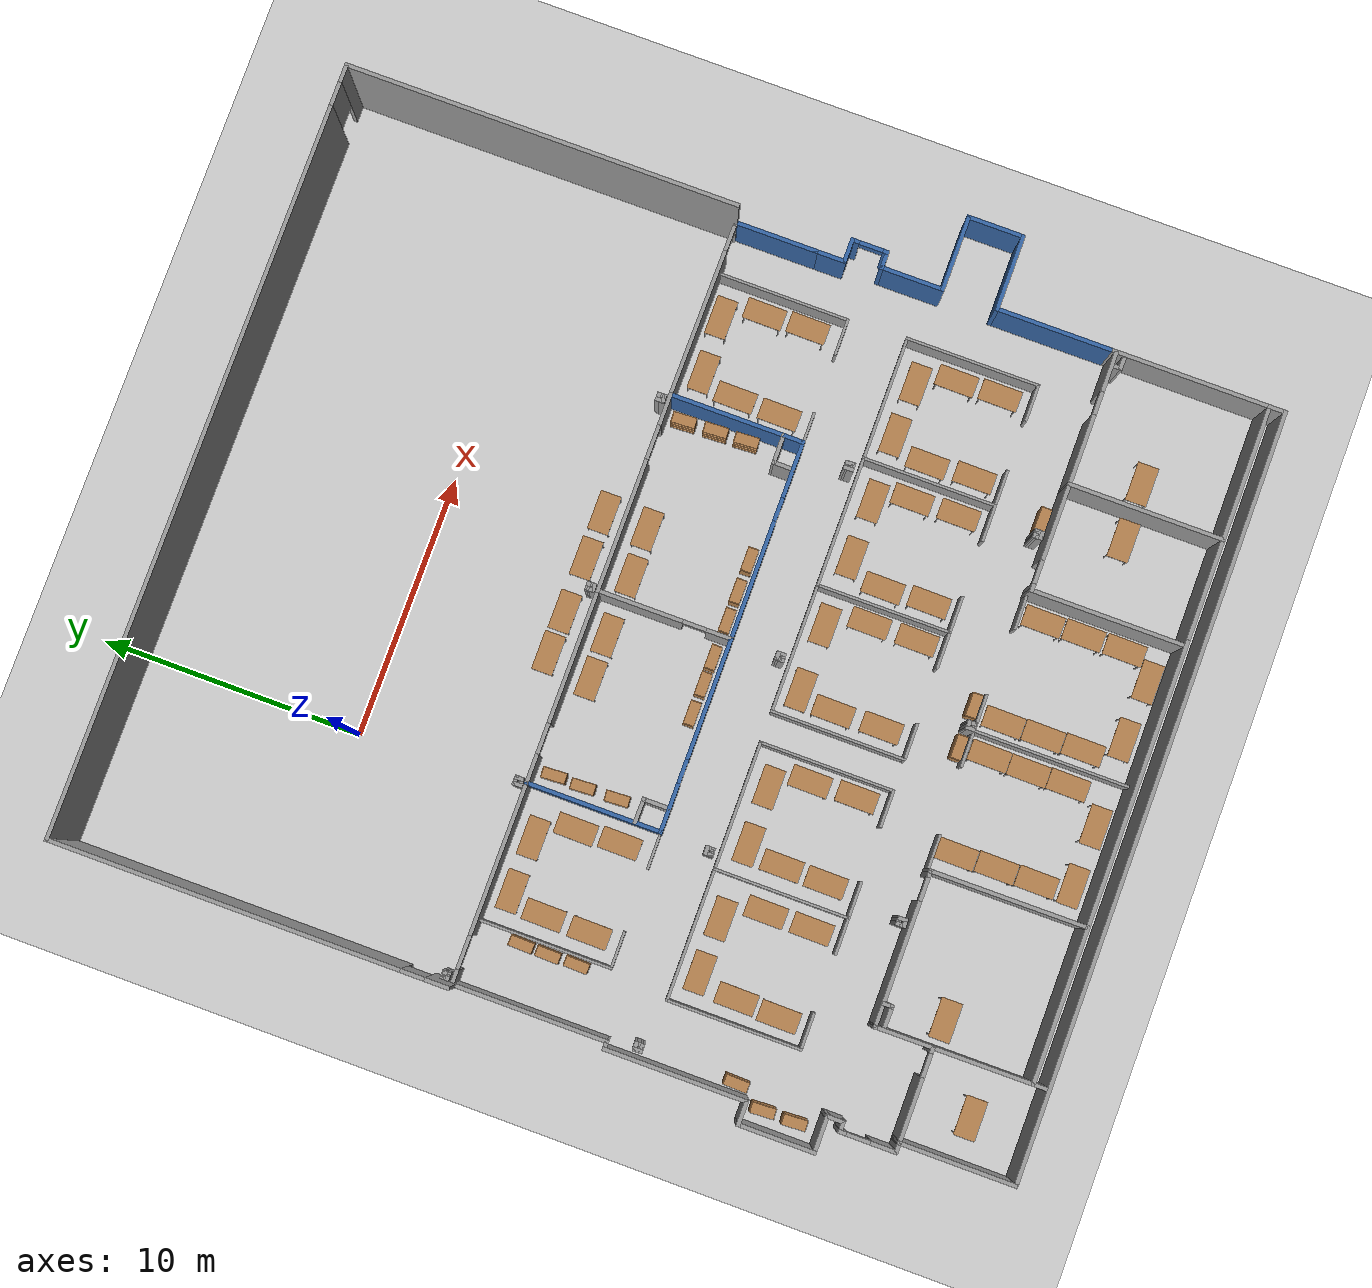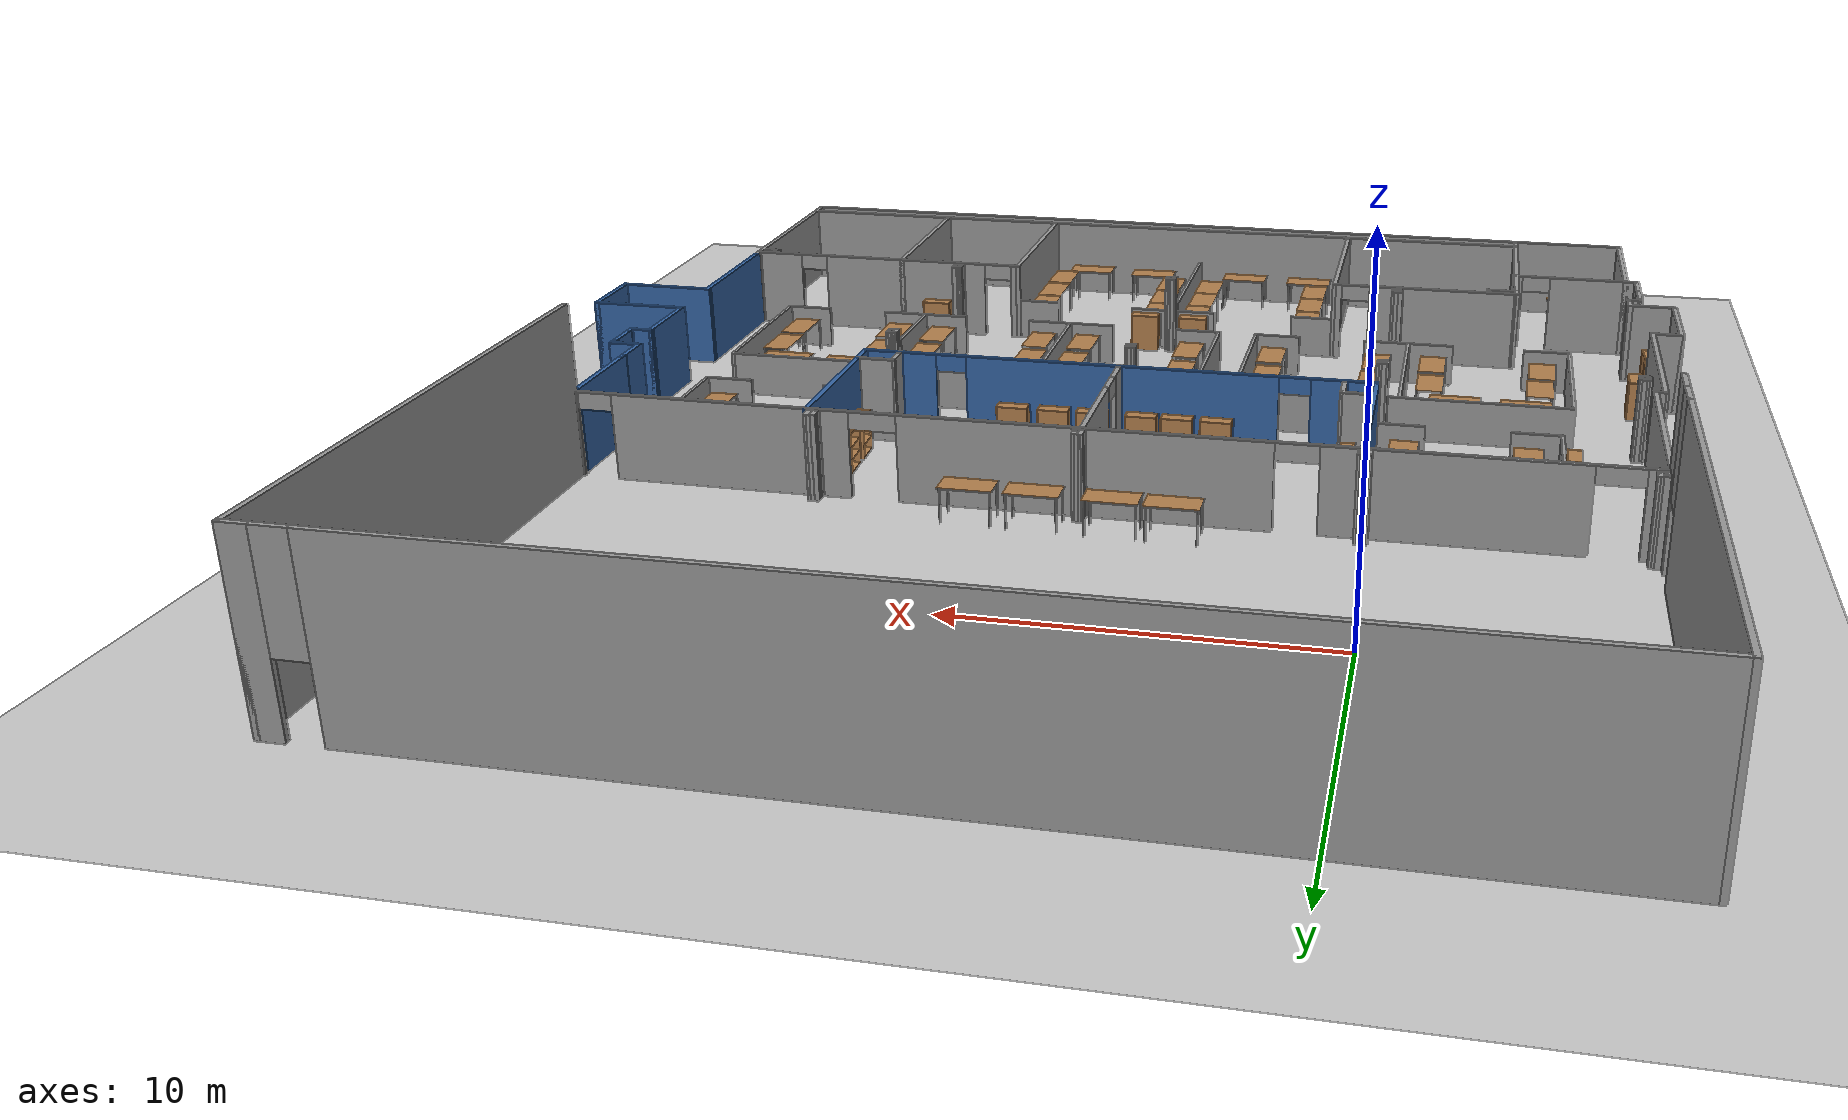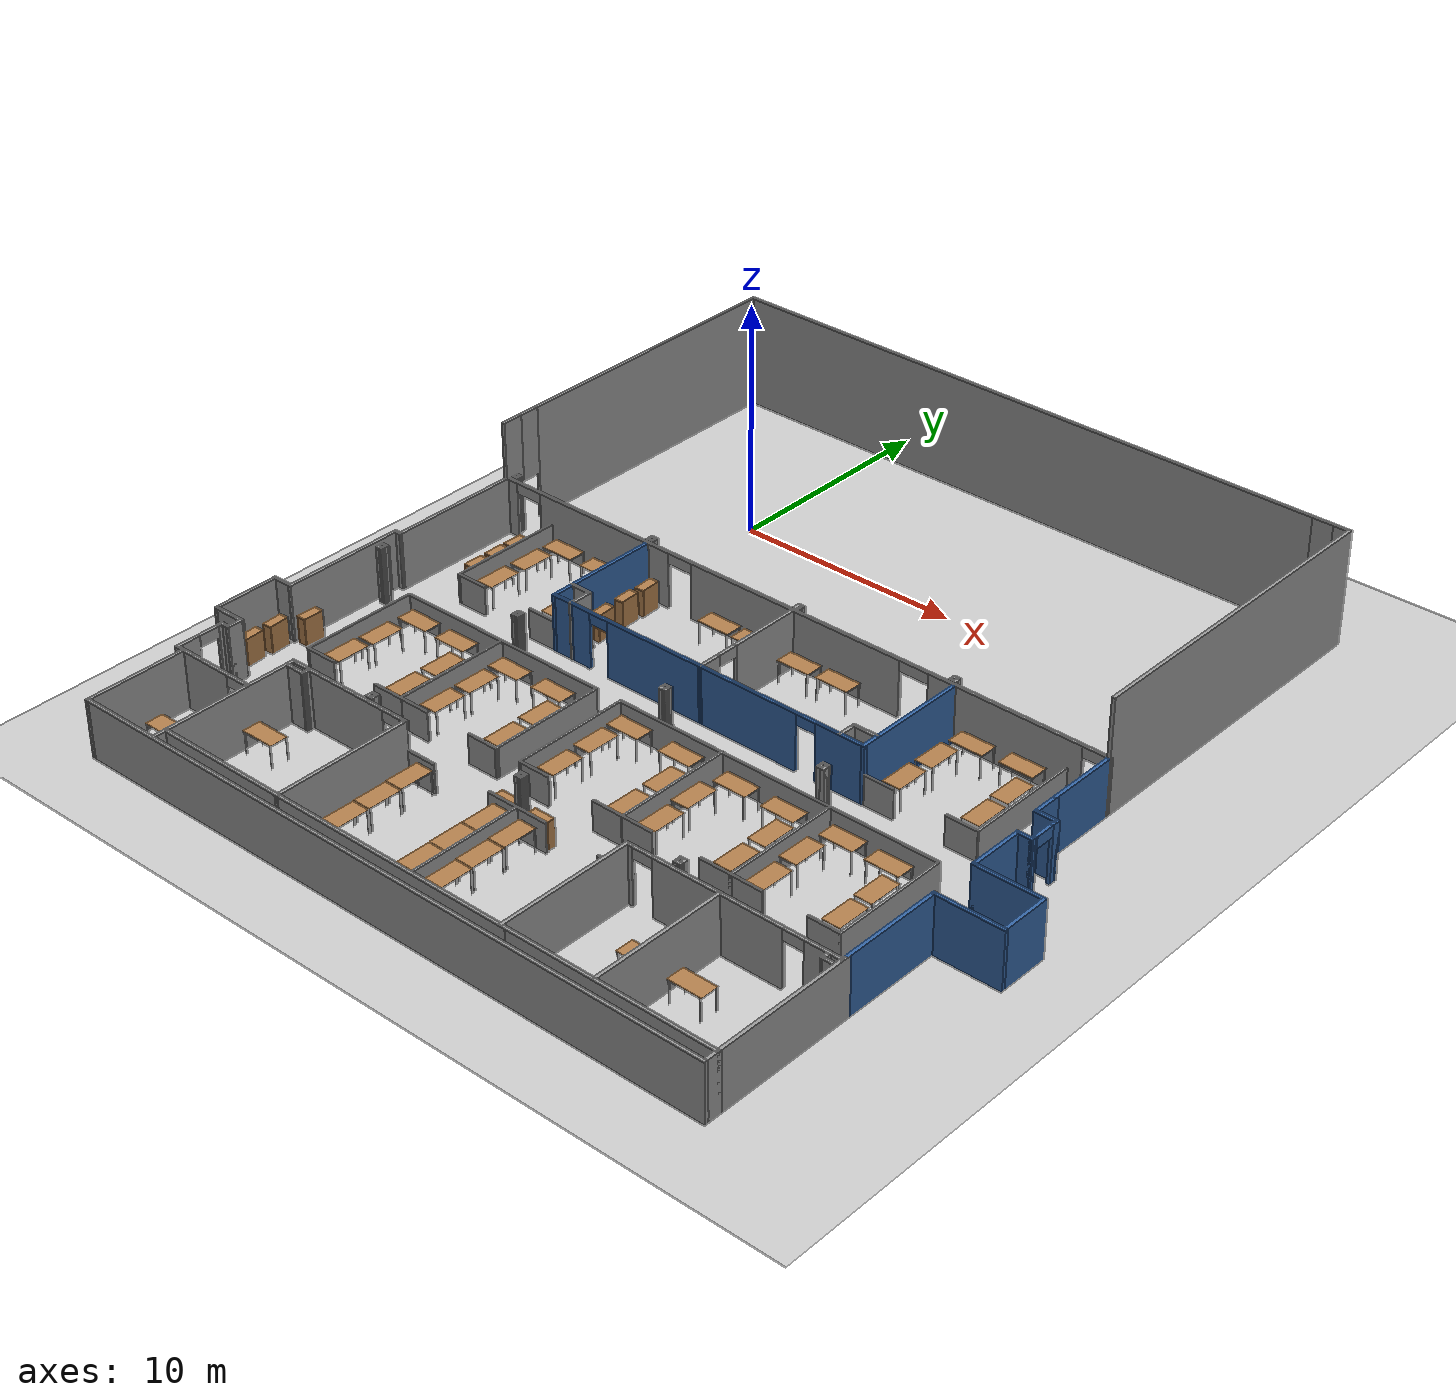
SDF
<sdf version="1.7">
 <world name="default">
  <plugin name="gazebo_ros_state" filename="libgazebo_ros_state.so">
   <ros>
    <namespace>/plug</namespace>
    <argument>model_states:=model_states_plug</argument>
    <argument>link_states:=link_states_plug</argument>
   </ros>
   <update_rate>100.0</update_rate>
  </plugin>
  <plugin name="disable_physics" filename="libdisable_physics.so"/>
  <light name="light" type="directional">
   <pose>0 0 10 0 -0 0</pose>
   <diffuse>0.8 0.8 0.8 1</diffuse>
   <specular>0.2 0.2 0.2 1</specular>
   <attenuation>
    <range>1000</range>
    <constant>0.9</constant>
    <linear>0.01</linear>
    <quadratic>0.001</quadratic>
   </attenuation>
   <direction>-0.5 0.1 -0.9</direction>
   <spot><inner_angle>0</inner_angle><outer_angle>0</outer_angle><falloff>0</falloff></spot>
  </light>
  <model name="ground_plane">
   <static>1</static>
   <link name="link">
    <collision name="collision">
     <geometry><plane><normal>0 0 1</normal><size>100 100</size></plane></geometry>
     <surface>
      <contact><collide_bitmask>65535</collide_bitmask></contact>
      <friction><ode><mu>100</mu><mu2>50</mu2></ode></friction>
     </surface>
    </collision>
    <visual name="visual">
     <cast_shadows>0</cast_shadows>
     <geometry><plane><normal>0 0 1</normal><size>100 100</size></plane></geometry>
     <material>
      <script><uri>file://media/materials/scripts/gazebo.material</uri><name>Gazebo/Grey</name></script>
     </material>
    </visual>
   </link>
  </model>
  <gravity>0 0 -9.8</gravity>
  <magnetic_field>6e-06 2.3e-05 -4.2e-05</magnetic_field>
  <atmosphere type="adiabatic"/>
  <physics type="ode">
   <max_step_size>0.01</max_step_size>
   <real_time_factor>1</real_time_factor>
   <real_time_update_rate>100</real_time_update_rate>
  </physics>
  <scene><ambient>0.4 0.4 0.4 1</ambient><background>0.7 0.7 0.7 1</background><shadows>1</shadows></scene>
  <spherical_coordinates>
   <surface_model>EARTH_WGS84</surface_model>
   <latitude_deg>0</latitude_deg>
   <longitude_deg>0</longitude_deg>
   <elevation>0</elevation>
   <heading_deg>0</heading_deg>
  </spherical_coordinates>
  <model name="ACL_office_centered">
   <pose>8.45773 -9.64315 0 0 -0 0</pose>
   <link name="Wall_0">
    <pose>-15.6747 10.5251 0 0 -0 1.5708</pose>
    <visual name="Wall_0_Visual_0">
     <pose>-7.03494 0 2.5 0 -0 0</pose>
     <geometry><box><size>0.930116 0.15 5</size></box></geometry>
     <material>
      <script><uri>file://media/materials/scripts/gazebo.material</uri><name>Gazebo/Grey</name></script>
      <ambient>1 1 1 1</ambient>
     </material>
     <meta><layer>0</layer></meta>
    </visual>
    <collision name="Wall_0_Collision_0">
     <geometry><box><size>0.930116 0.15 5</size></box></geometry>
     <pose>-7.03494 0 2.5 0 -0 0</pose>
    </collision>
    <visual name="Wall_0_Visual_1">
     <pose>0.915058 0 2.5 0 -0 0</pose>
     <geometry><box><size>13.1699 0.15 5</size></box></geometry>
     <material>
      <script><uri>file://media/materials/scripts/gazebo.material</uri><name>Gazebo/Grey</name></script>
      <ambient>1 1 1 1</ambient>
     </material>
     <meta><layer>0</layer></meta>
    </visual>
    <collision name="Wall_0_Collision_1">
     <geometry><box><size>13.1699 0.15 5</size></box></geometry>
     <pose>0.915058 0 2.5 0 -0 0</pose>
    </collision>
    <visual name="Wall_0_Visual_2">
     <pose>-6.11988 0 3.5 0 -0 0</pose>
     <geometry><box><size>0.9 0.15 3</size></box></geometry>
     <material>
      <script><uri>file://media/materials/scripts/gazebo.material</uri><name>Gazebo/Grey</name></script>
      <ambient>1 1 1 1</ambient>
     </material>
     <meta><layer>0</layer></meta>
    </visual>
    <collision name="Wall_0_Collision_2">
     <geometry><box><size>0.9 0.15 3</size></box></geometry>
     <pose>-6.11988 0 3.5 0 -0 0</pose>
    </collision>
   </link>
   <link name="Wall_1">
    <pose>-0.999727 17.9501 0 0 -0 0</pose>
    <visual name="Wall_1_Visual_0">
     <pose>-0.823754 0 2.5 0 -0 0</pose>
     <geometry><box><size>27.8525 0.15 5</size></box></geometry>
     <material>
      <script><uri>file://media/materials/scripts/gazebo.material</uri><name>Gazebo/Grey</name></script>
      <ambient>1 1 1 1</ambient>
     </material>
     <meta><layer>0</layer></meta>
    </visual>
    <collision name="Wall_1_Collision_0">
     <geometry><box><size>27.8525 0.15 5</size></box></geometry>
     <pose>-0.823754 0 2.5 0 -0 0</pose>
    </collision>
    <visual name="Wall_1_Visual_1">
     <pose>14.3762 0 2.5 0 -0 0</pose>
     <geometry><box><size>0.747508 0.15 5</size></box></geometry>
     <material>
      <script><uri>file://media/materials/scripts/gazebo.material</uri><name>Gazebo/Grey</name></script>
      <ambient>1 1 1 1</ambient>
     </material>
     <meta><layer>0</layer></meta>
    </visual>
    <collision name="Wall_1_Collision_1">
     <geometry><box><size>0.747508 0.15 5</size></box></geometry>
     <pose>14.3762 0 2.5 0 -0 0</pose>
    </collision>
    <visual name="Wall_1_Visual_2">
     <pose>13.5525 0 3.5 0 -0 0</pose>
     <geometry><box><size>0.9 0.15 3</size></box></geometry>
     <material>
      <script><uri>file://media/materials/scripts/gazebo.material</uri><name>Gazebo/Grey</name></script>
      <ambient>1 1 1 1</ambient>
     </material>
     <meta><layer>0</layer></meta>
    </visual>
    <collision name="Wall_1_Collision_2">
     <geometry><box><size>0.9 0.15 3</size></box></geometry>
     <pose>13.5525 0 3.5 0 -0 0</pose>
    </collision>
   </link>
   <link name="Wall_10">
    <collision name="Wall_10_Collision">
     <geometry><box><size>2.25 0.15 2.5</size></box></geometry>
     <pose>0 0 1.25 0 -0 0</pose>
    </collision>
    <visual name="Wall_10_Visual">
     <pose>0 0 1.25 0 -0 0</pose>
     <geometry><box><size>2.25 0.15 2.5</size></box></geometry>
     <material>
      <script><uri>file://media/materials/scripts/gazebo.material</uri><name>Gazebo/Grey</name></script>
      <ambient>0.203922 0.396078 0.643137 1</ambient>
     </material>
     <meta><layer>0</layer></meta>
    </visual>
    <pose>16.775 -5.85015 0 0 -0 -1.5708</pose>
   </link>
   <link name="Wall_100">
    <collision name="Wall_100_Collision">
     <geometry><box><size>0.341623 0.15 2.5</size></box></geometry>
     <pose>0 0 1.25 0 -0 0</pose>
    </collision>
    <visual name="Wall_100_Visual">
     <pose>0 0 1.25 0 -0 0</pose>
     <geometry><box><size>0.341623 0.15 2.5</size></box></geometry>
     <material>
      <script><uri>file://media/materials/scripts/gazebo.material</uri><name>Gazebo/Grey</name></script>
      <ambient>1 1 1 1</ambient>
     </material>
     <meta><layer>0</layer></meta>
    </visual>
    <pose>-8.09905 -3.91466 0 0 -0 3.11175</pose>
   </link>
   <link name="Wall_102">
    <collision name="Wall_102_Collision">
     <geometry><box><size>0.374413 0.15 2.5</size></box></geometry>
     <pose>0 0 1.25 0 -0 0</pose>
    </collision>
    <visual name="Wall_102_Visual">
     <pose>0 0 1.25 0 -0 0</pose>
     <geometry><box><size>0.374413 0.15 2.5</size></box></geometry>
     <material>
      <script><uri>file://media/materials/scripts/gazebo.material</uri><name>Gazebo/Grey</name></script>
      <ambient>1 1 1 1</ambient>
     </material>
     <meta><layer>0</layer></meta>
    </visual>
    <pose>-0.793469 -3.8239 0 0 -0 1.5708</pose>
   </link>
   <link name="Wall_103">
    <collision name="Wall_103_Collision">
     <geometry><box><size>0.348689 0.15 2.5</size></box></geometry>
     <pose>0 0 1.25 0 -0 0</pose>
    </collision>
    <visual name="Wall_103_Visual">
     <pose>0 0 1.25 0 -0 0</pose>
     <geometry><box><size>0.348689 0.15 2.5</size></box></geometry>
     <material>
      <script><uri>file://media/materials/scripts/gazebo.material</uri><name>Gazebo/Grey</name></script>
      <ambient>1 1 1 1</ambient>
     </material>
     <meta><layer>0</layer></meta>
    </visual>
    <pose>-0.694128 -3.71241 0 0 -0 -0.007194</pose>
   </link>
   <link name="Wall_104">
    <collision name="Wall_104_Collision">
     <geometry><box><size>0.355851 0.15 2.5</size></box></geometry>
     <pose>0 0 1.25 0 -0 0</pose>
    </collision>
    <visual name="Wall_104_Visual">
     <pose>0 0 1.25 0 -0 0</pose>
     <geometry><box><size>0.355851 0.15 2.5</size></box></geometry>
     <material>
      <script><uri>file://media/materials/scripts/gazebo.material</uri><name>Gazebo/Grey</name></script>
      <ambient>1 1 1 1</ambient>
     </material>
     <meta><layer>0</layer></meta>
    </visual>
    <pose>-0.593356 -3.81604 0 0 -0 -1.55691</pose>
   </link>
   <link name="Wall_105">
    <collision name="Wall_105_Collision">
     <geometry><box><size>0.337255 0.15 2.5</size></box></geometry>
     <pose>0 0 1.25 0 -0 0</pose>
    </collision>
    <visual name="Wall_105_Visual">
     <pose>0 0 1.25 0 -0 0</pose>
     <geometry><box><size>0.337255 0.15 2.5</size></box></geometry>
     <material>
      <script><uri>file://media/materials/scripts/gazebo.material</uri><name>Gazebo/Grey</name></script>
      <ambient>1 1 1 1</ambient>
     </material>
     <meta><layer>0</layer></meta>
    </visual>
    <pose>-0.685551 -3.91967 0 0 -0 -3.13396</pose>
   </link>
   <link name="Wall_107">
    <collision name="Wall_107_Collision">
     <geometry><box><size>0.391604 0.15 2.5</size></box></geometry>
     <pose>0 0 1.25 0 -0 0</pose>
    </collision>
    <visual name="Wall_107_Visual">
     <pose>0 0 1.25 0 -0 0</pose>
     <geometry><box><size>0.391604 0.15 2.5</size></box></geometry>
     <material>
      <script><uri>file://media/materials/scripts/gazebo.material</uri><name>Gazebo/Grey</name></script>
      <ambient>1 1 1 1</ambient>
     </material>
     <meta><layer>0</layer></meta>
    </visual>
    <pose>6.55713 -3.81389 0 0 -0 1.58855</pose>
   </link>
   <link name="Wall_108">
    <collision name="Wall_108_Collision">
     <geometry><box><size>0.352972 0.15 2.5</size></box></geometry>
     <pose>0 0 1.25 0 -0 0</pose>
    </collision>
    <visual name="Wall_108_Visual">
     <pose>0 0 1.25 0 -0 0</pose>
     <geometry><box><size>0.352972 0.15 2.5</size></box></geometry>
     <material>
      <script><uri>file://media/materials/scripts/gazebo.material</uri><name>Gazebo/Grey</name></script>
      <ambient>1 1 1 1</ambient>
     </material>
     <meta><layer>0</layer></meta>
    </visual>
    <pose>6.65648 -3.69239 0 0 -0 0.007042</pose>
   </link>
   <link name="Wall_109">
    <collision name="Wall_109_Collision">
     <geometry><box><size>0.388707 0.15 2.5</size></box></geometry>
     <pose>0 0 1.25 0 -0 0</pose>
    </collision>
    <visual name="Wall_109_Visual">
     <pose>0 0 1.25 0 -0 0</pose>
     <geometry><box><size>0.388707 0.15 2.5</size></box></geometry>
     <material>
      <script><uri>file://media/materials/scripts/gazebo.material</uri><name>Gazebo/Grey</name></script>
      <ambient>1 1 1 1</ambient>
     </material>
     <meta><layer>0</layer></meta>
    </visual>
    <pose>6.75796 -3.81103 0 0 -0 -1.5708</pose>
   </link>
   <link name="Wall_11">
    <collision name="Wall_11_Collision">
     <geometry><box><size>3 0.15 2.5</size></box></geometry>
     <pose>0 0 1.25 0 -0 0</pose>
    </collision>
    <visual name="Wall_11_Visual">
     <pose>0 0 1.25 0 -0 0</pose>
     <geometry><box><size>3 0.15 2.5</size></box></geometry>
     <material>
      <script><uri>file://media/materials/scripts/gazebo.material</uri><name>Gazebo/Grey</name></script>
      <ambient>0.203922 0.396078 0.643137 1</ambient>
     </material>
     <meta><layer>0</layer></meta>
    </visual>
    <pose>15.35 -6.90015 0 0 -0 3.14159</pose>
   </link>
   <link name="Wall_110">
    <collision name="Wall_110_Collision">
     <geometry><box><size>0.342967 0.15 2.5</size></box></geometry>
     <pose>0 0 1.25 0 -0 0</pose>
    </collision>
    <visual name="Wall_110_Visual">
     <pose>0 0 1.25 0 -0 0</pose>
     <geometry><box><size>0.342967 0.15 2.5</size></box></geometry>
     <material>
      <script><uri>file://media/materials/scripts/gazebo.material</uri><name>Gazebo/Grey</name></script>
      <ambient>1 1 1 1</ambient>
     </material>
     <meta><layer>0</layer></meta>
    </visual>
    <pose>6.66148 -3.93039 0 0 -0 3.14159</pose>
   </link>
   <link name="Wall_112">
    <collision name="Wall_112_Collision">
     <geometry><box><size>0.358506 0.15 2.5</size></box></geometry>
     <pose>0 0 1.25 0 -0 0</pose>
    </collision>
    <visual name="Wall_112_Visual">
     <pose>0 0 1.25 0 -0 0</pose>
     <geometry><box><size>0.358506 0.15 2.5</size></box></geometry>
     <material>
      <script><uri>file://media/materials/scripts/gazebo.material</uri><name>Gazebo/Grey</name></script>
      <ambient>1 1 1 1</ambient>
     </material>
     <meta><layer>0</layer></meta>
    </visual>
    <pose>-15.455 3.56311 0 0 -0 -0.010309</pose>
   </link>
   <link name="Wall_113">
    <collision name="Wall_113_Collision">
     <geometry><box><size>0.341348 0.15 2.5</size></box></geometry>
     <pose>0 0 1.25 0 -0 0</pose>
    </collision>
    <visual name="Wall_113_Visual">
     <pose>0 0 1.25 0 -0 0</pose>
     <geometry><box><size>0.341348 0.15 2.5</size></box></geometry>
     <material>
      <script><uri>file://media/materials/scripts/gazebo.material</uri><name>Gazebo/Grey</name></script>
      <ambient>1 1 1 1</ambient>
     </material>
     <meta><layer>0</layer></meta>
    </visual>
    <pose>-15.3539 3.46638 0 0 -0 -1.60449</pose>
   </link>
   <link name="Wall_114">
    <collision name="Wall_114_Collision">
     <geometry><box><size>0.337013 0.15 2.5</size></box></geometry>
     <pose>0 0 1.25 0 -0 0</pose>
    </collision>
    <visual name="Wall_114_Visual">
     <pose>0 0 1.25 0 -0 0</pose>
     <geometry><box><size>0.337013 0.15 2.5</size></box></geometry>
     <material>
      <script><uri>file://media/materials/scripts/gazebo.material</uri><name>Gazebo/Grey</name></script>
      <ambient>1 1 1 1</ambient>
     </material>
     <meta><layer>0</layer></meta>
    </visual>
    <pose>-15.4507 3.37181 0 0 -0 3.1301</pose>
   </link>
   <link name="Wall_115">
    <collision name="Wall_115_Collision">
     <geometry><box><size>0.326267 0.15 2.5</size></box></geometry>
     <pose>0 0 1.25 0 -0 0</pose>
    </collision>
    <visual name="Wall_115_Visual">
     <pose>0 0 1.25 0 -0 0</pose>
     <geometry><box><size>0.326267 0.15 2.5</size></box></geometry>
     <material>
      <script><uri>file://media/materials/scripts/gazebo.material</uri><name>Gazebo/Grey</name></script>
      <ambient>1 1 1 1</ambient>
     </material>
     <meta><layer>0</layer></meta>
    </visual>
    <pose>-15.5452 3.46101 0 0 -0 1.58299</pose>
   </link>
   <link name="Wall_117">
    <collision name="Wall_117_Collision">
     <geometry><box><size>0.384377 0.15 2.5</size></box></geometry>
     <pose>0 0 1.25 0 -0 0</pose>
    </collision>
    <visual name="Wall_117_Visual">
     <pose>0 0 1.25 0 -0 0</pose>
     <geometry><box><size>0.384377 0.15 2.5</size></box></geometry>
     <material>
      <script><uri>file://media/materials/scripts/gazebo.material</uri><name>Gazebo/Grey</name></script>
      <ambient>1 1 1 1</ambient>
     </material>
     <meta><layer>0</layer></meta>
    </visual>
    <pose>-8.21891 3.44274 0 0 -0 1.60748</pose>
   </link>
   <link name="Wall_118">
    <collision name="Wall_118_Collision">
     <geometry><box><size>0.378002 0.15 2.5</size></box></geometry>
     <pose>0 0 1.25 0 -0 0</pose>
    </collision>
    <visual name="Wall_118_Visual">
     <pose>0 0 1.25 0 -0 0</pose>
     <geometry><box><size>0.378002 0.15 2.5</size></box></geometry>
     <material>
      <script><uri>file://media/materials/scripts/gazebo.material</uri><name>Gazebo/Grey</name></script>
      <ambient>1 1 1 1</ambient>
     </material>
     <meta><layer>0</layer></meta>
    </visual>
    <pose>-8.10928 3.55881 0 0 -0 -0.009434</pose>
   </link>
   <link name="Wall_119">
    <collision name="Wall_119_Collision">
     <geometry><box><size>0.364986 0.15 2.5</size></box></geometry>
     <pose>0 0 1.25 0 -0 0</pose>
    </collision>
    <visual name="Wall_119_Visual">
     <pose>0 0 1.25 0 -0 0</pose>
     <geometry><box><size>0.364986 0.15 2.5</size></box></geometry>
     <material>
      <script><uri>file://media/materials/scripts/gazebo.material</uri><name>Gazebo/Grey</name></script>
      <ambient>1 1 1 1</ambient>
     </material>
     <meta><layer>0</layer></meta>
    </visual>
    <pose>-7.99429 3.45026 0 0 -0 -1.5608</pose>
   </link>
   <link name="Wall_12">
    <collision name="Wall_12_Collision">
     <geometry><box><size>4.5 0.15 2.5</size></box></geometry>
     <pose>0 0 1.25 0 -0 0</pose>
    </collision>
    <visual name="Wall_12_Visual">
     <pose>0 0 1.25 0 -0 0</pose>
     <geometry><box><size>4.5 0.15 2.5</size></box></geometry>
     <material>
      <script><uri>file://media/materials/scripts/gazebo.material</uri><name>Gazebo/Grey</name></script>
      <ambient>0.203922 0.396078 0.643137 1</ambient>
     </material>
     <meta><layer>0</layer></meta>
    </visual>
    <pose>13.925 -9.07515 0 0 -0 -1.5708</pose>
   </link>
   <link name="Wall_120">
    <collision name="Wall_120_Collision">
     <geometry><box><size>0.362837 0.15 2.5</size></box></geometry>
     <pose>0 0 1.25 0 -0 0</pose>
    </collision>
    <visual name="Wall_120_Visual">
     <pose>0 0 1.25 0 -0 0</pose>
     <geometry><box><size>0.362837 0.15 2.5</size></box></geometry>
     <material>
      <script><uri>file://media/materials/scripts/gazebo.material</uri><name>Gazebo/Grey</name></script>
      <ambient>1 1 1 1</ambient>
     </material>
     <meta><layer>0</layer></meta>
    </visual>
    <pose>-8.09961 3.34064 0 0 -0 -3.12139</pose>
   </link>
   <link name="Wall_122">
    <collision name="Wall_122_Collision">
     <geometry><box><size>0.382149 0.15 2.5</size></box></geometry>
     <pose>0 0 1.25 0 -0 0</pose>
    </collision>
    <visual name="Wall_122_Visual">
     <pose>0 0 1.25 0 -0 0</pose>
     <geometry><box><size>0.382149 0.15 2.5</size></box></geometry>
     <material>
      <script><uri>file://media/materials/scripts/gazebo.material</uri><name>Gazebo/Grey</name></script>
      <ambient>1 1 1 1</ambient>
     </material>
     <meta><layer>0</layer></meta>
    </visual>
    <pose>-0.757152 3.43307 0 0 -0 1.58005</pose>
   </link>
   <link name="Wall_123">
    <collision name="Wall_123_Collision">
     <geometry><box><size>0.330552 0.15 2.5</size></box></geometry>
     <pose>0 0 1.25 0 -0 0</pose>
    </collision>
    <visual name="Wall_123_Visual">
     <pose>0 0 1.25 0 -0 0</pose>
     <geometry><box><size>0.330552 0.15 2.5</size></box></geometry>
     <material>
      <script><uri>file://media/materials/scripts/gazebo.material</uri><name>Gazebo/Grey</name></script>
      <ambient>1 1 1 1</ambient>
     </material>
     <meta><layer>0</layer></meta>
    </visual>
    <pose>-0.66795 3.54914 0 0 -0 0</pose>
   </link>
   <link name="Wall_124">
    <collision name="Wall_124_Collision">
     <geometry><box><size>0.375731 0.15 2.5</size></box></geometry>
     <pose>0 0 1.25 0 -0 0</pose>
    </collision>
    <visual name="Wall_124_Visual">
     <pose>0 0 1.25 0 -0 0</pose>
     <geometry><box><size>0.375731 0.15 2.5</size></box></geometry>
     <material>
      <script><uri>file://media/materials/scripts/gazebo.material</uri><name>Gazebo/Grey</name></script>
      <ambient>1 1 1 1</ambient>
     </material>
     <meta><layer>0</layer></meta>
    </visual>
    <pose>-0.575524 3.43629 0 0 -0 -1.55175</pose>
   </link>
   <link name="Wall_125">
    <collision name="Wall_125_Collision">
     <geometry><box><size>0.319819 0.15 2.5</size></box></geometry>
     <pose>0 0 1.25 0 -0 0</pose>
    </collision>
    <visual name="Wall_125_Visual">
     <pose>0 0 1.25 0 -0 0</pose>
     <geometry><box><size>0.319819 0.15 2.5</size></box></geometry>
     <material>
      <script><uri>file://media/materials/scripts/gazebo.material</uri><name>Gazebo/Grey</name></script>
      <ambient>1 1 1 1</ambient>
     </material>
     <meta><layer>0</layer></meta>
    </visual>
    <pose>-0.658278 3.32452 0 0 -0 3.12893</pose>
   </link>
   <link name="Wall_127">
    <collision name="Wall_127_Collision">
     <geometry><box><size>0.371402 0.15 2.5</size></box></geometry>
     <pose>0 0 1.25 0 -0 0</pose>
    </collision>
    <visual name="Wall_127_Visual">
     <pose>0 0 1.25 0 -0 0</pose>
     <geometry><box><size>0.371402 0.15 2.5</size></box></geometry>
     <material>
      <script><uri>file://media/materials/scripts/gazebo.material</uri><name>Gazebo/Grey</name></script>
      <ambient>1 1 1 1</ambient>
     </material>
     <meta><layer>0</layer></meta>
    </visual>
    <pose>6.56704 3.43844 0 0 -0 1.5708</pose>
   </link>
   <link name="Wall_128">
    <collision name="Wall_128_Collision">
     <geometry><box><size>0.33915 0.15 2.5</size></box></geometry>
     <pose>0 0 1.25 0 -0 0</pose>
    </collision>
    <visual name="Wall_128_Visual">
     <pose>0 0 1.25 0 -0 0</pose>
     <geometry><box><size>0.33915 0.15 2.5</size></box></geometry>
     <material>
      <script><uri>file://media/materials/scripts/gazebo.material</uri><name>Gazebo/Grey</name></script>
      <ambient>1 1 1 1</ambient>
     </material>
     <meta><layer>0</layer></meta>
    </visual>
    <pose>6.66161 3.54914 0 0 -0 0</pose>
   </link>
   <link name="Wall_129">
    <collision name="Wall_129_Collision">
     <geometry><box><size>0.371402 0.15 2.5</size></box></geometry>
     <pose>0 0 1.25 0 -0 0</pose>
    </collision>
    <visual name="Wall_129_Visual">
     <pose>0 0 1.25 0 -0 0</pose>
     <geometry><box><size>0.371402 0.15 2.5</size></box></geometry>
     <material>
      <script><uri>file://media/materials/scripts/gazebo.material</uri><name>Gazebo/Grey</name></script>
      <ambient>1 1 1 1</ambient>
     </material>
     <meta><layer>0</layer></meta>
    </visual>
    <pose>6.75726 3.43844 0 0 -0 -1.56109</pose>
   </link>
   <link name="Wall_13">
    <collision name="Wall_13_Collision">
     <geometry><box><size>6.25 0.15 2.5</size></box></geometry>
     <pose>0 0 1.25 0 -0 0</pose>
    </collision>
    <visual name="Wall_13_Visual">
     <pose>0 0 1.25 0 -0 0</pose>
     <geometry><box><size>6.25 0.15 2.5</size></box></geometry>
     <material>
      <script><uri>file://media/materials/scripts/gazebo.material</uri><name>Gazebo/Grey</name></script>
      <ambient>1 1 1 1</ambient>
     </material>
     <meta><layer>0</layer></meta>
    </visual>
    <pose>13.925 -14.3001 0 0 -0 -1.5708</pose>
   </link>
   <link name="Wall_130">
    <collision name="Wall_130_Collision">
     <geometry><box><size>0.321968 0.15 2.5</size></box></geometry>
     <pose>0 0 1.25 0 -0 0</pose>
    </collision>
    <visual name="Wall_130_Visual">
     <pose>0 0 1.25 0 -0 0</pose>
     <geometry><box><size>0.321968 0.15 2.5</size></box></geometry>
     <material>
      <script><uri>file://media/materials/scripts/gazebo.material</uri><name>Gazebo/Grey</name></script>
      <ambient>1 1 1 1</ambient>
     </material>
     <meta><layer>0</layer></meta>
    </visual>
    <pose>6.67236 3.32775 0 0 -0 3.14159</pose>
   </link>
   <link name="Wall_132">
    <collision name="Wall_132_Collision">
     <geometry><box><size>5.2 0.1 1.3</size></box></geometry>
     <pose>0 0 0.65 0 -0 0</pose>
    </collision>
    <visual name="Wall_132_Visual">
     <pose>0 0 0.65 0 -0 0</pose>
     <geometry><box><size>5.2 0.1 1.3</size></box></geometry>
     <material>
      <script><uri>file://media/materials/scripts/gazebo.material</uri><name>Gazebo/Grey</name></script>
      <ambient>1 1 1 1</ambient>
     </material>
     <meta><layer>0</layer></meta>
    </visual>
    <pose>-13.2287 0.610146 0 0 -0 -1.5708</pose>
   </link>
   <link name="Wall_133">
    <collision name="Wall_133_Collision">
     <geometry><box><size>1.45 0.1 1.3</size></box></geometry>
     <pose>0 0 0.65 0 -0 0</pose>
    </collision>
    <visual name="Wall_133_Visual">
     <pose>0 0 0.65 0 -0 0</pose>
     <geometry><box><size>1.45 0.1 1.3</size></box></geometry>
     <material>
      <script><uri>file://media/materials/scripts/gazebo.material</uri><name>Gazebo/Grey</name></script>
      <ambient>1 1 1 1</ambient>
     </material>
     <meta><layer>0</layer></meta>
    </visual>
    <pose>-12.5537 -1.93985 0 0 -0 0</pose>
   </link>
   <link name="Wall_135">
    <collision name="Wall_135_Collision">
     <geometry><box><size>1.44963 0.1 1.3</size></box></geometry>
     <pose>0 0 0.65 0 -0 0</pose>
    </collision>
    <visual name="Wall_135_Visual">
     <pose>0 0 0.65 0 -0 0</pose>
     <geometry><box><size>1.44963 0.1 1.3</size></box></geometry>
     <material>
      <script><uri>file://media/materials/scripts/gazebo.material</uri><name>Gazebo/Grey</name></script>
      <ambient>1 1 1 1</ambient>
     </material>
     <meta><layer>0</layer></meta>
    </visual>
    <pose>-8.72873 -1.94485 0 0 -0 3.14159</pose>
   </link>
   <link name="Wall_14">
    <collision name="Wall_14_Collision">
     <geometry><box><size>9.25 0.15 2.5</size></box></geometry>
     <pose>0 0 1.25 0 -0 0</pose>
    </collision>
    <visual name="Wall_14_Visual">
     <pose>0 0 1.25 0 -0 0</pose>
     <geometry><box><size>9.25 0.15 2.5</size></box></geometry>
     <material>
      <script><uri>file://media/materials/scripts/gazebo.material</uri><name>Gazebo/Grey</name></script>
      <ambient>1 1 1 1</ambient>
     </material>
     <meta><layer>0</layer></meta>
    </visual>
    <pose>9.375 -17.3501 0 0 -0 3.14159</pose>
   </link>
   <link name="Wall_140">
    <collision name="Wall_140_Collision">
     <geometry><box><size>5.12902 0.1 1.3</size></box></geometry>
     <pose>0 0 0.65 0 -0 0</pose>
    </collision>
    <visual name="Wall_140_Visual">
     <pose>0 0 0.65 0 -0 0</pose>
     <geometry><box><size>5.12902 0.1 1.3</size></box></geometry>
     <material>
      <script><uri>file://media/materials/scripts/gazebo.material</uri><name>Gazebo/Grey</name></script>
      <ambient>1 1 1 1</ambient>
     </material>
     <meta><layer>0</layer></meta>
    </visual>
    <pose>11.9498 0.580646 0 0 -0 -1.57338</pose>
   </link>
   <link name="Wall_141">
    <collision name="Wall_141_Collision">
     <geometry><box><size>1.4496 0.1 1.3</size></box></geometry>
     <pose>0 0 0.65 0 -0 0</pose>
    </collision>
    <visual name="Wall_141_Visual">
     <pose>0 0 0.65 0 -0 0</pose>
     <geometry><box><size>1.4496 0.1 1.3</size></box></geometry>
     <material>
      <script><uri>file://media/materials/scripts/gazebo.material</uri><name>Gazebo/Grey</name></script>
      <ambient>1 1 1 1</ambient>
     </material>
     <meta><layer>0</layer></meta>
    </visual>
    <pose>11.2683 -1.93385 0 0 -0 3.14159</pose>
   </link>
   <link name="Wall_143">
    <collision name="Wall_143_Collision">
     <geometry><box><size>1.45037 0.1 1.3</size></box></geometry>
     <pose>0 0 0.65 0 -0 0</pose>
    </collision>
    <visual name="Wall_143_Visual">
     <pose>0 0 0.65 0 -0 0</pose>
     <geometry><box><size>1.45037 0.1 1.3</size></box></geometry>
     <material>
      <script><uri>file://media/materials/scripts/gazebo.material</uri><name>Gazebo/Grey</name></script>
      <ambient>1 1 1 1</ambient>
     </material>
     <meta><layer>0</layer></meta>
    </visual>
    <pose>7.57127 -1.94485 0 0 -0 0</pose>
   </link>
   <link name="Wall_145">
    <collision name="Wall_145_Collision">
     <geometry><box><size>5.20019 0.1 1.3</size></box></geometry>
     <pose>0 0 0.65 0 -0 0</pose>
    </collision>
    <visual name="Wall_145_Visual">
     <pose>0 0 0.65 0 -0 0</pose>
     <geometry><box><size>5.20019 0.1 1.3</size></box></geometry>
     <material>
      <script><uri>file://media/materials/scripts/gazebo.material</uri><name>Gazebo/Grey</name></script>
      <ambient>1 1 1 1</ambient>
     </material>
     <meta><layer>0</layer></meta>
    </visual>
    <pose>-2.54973 -6.76685 0 0 -0 1.5708</pose>
   </link>
   <link name="Wall_146">
    <collision name="Wall_146_Collision">
     <geometry><box><size>14.7 0.1 1.3</size></box></geometry>
     <pose>0 0 0.65 0 -0 0</pose>
    </collision>
    <visual name="Wall_146_Visual">
     <pose>0 0 0.65 0 -0 0</pose>
     <geometry><box><size>14.7 0.1 1.3</size></box></geometry>
     <material>
      <script><uri>file://media/materials/scripts/gazebo.material</uri><name>Gazebo/Grey</name></script>
      <ambient>1 1 1 1</ambient>
     </material>
     <meta><layer>0</layer></meta>
    </visual>
    <pose>4.75027 -4.21685 0 0 -0 0</pose>
   </link>
   <link name="Wall_147">
    <collision name="Wall_147_Collision">
     <geometry><box><size>5.2 0.1 1.3</size></box></geometry>
     <pose>0 0 0.65 0 -0 0</pose>
    </collision>
    <visual name="Wall_147_Visual">
     <pose>0 0 0.65 0 -0 0</pose>
     <geometry><box><size>5.2 0.1 1.3</size></box></geometry>
     <material>
      <script><uri>file://media/materials/scripts/gazebo.material</uri><name>Gazebo/Grey</name></script>
      <ambient>1 1 1 1</ambient>
     </material>
     <meta><layer>0</layer></meta>
    </visual>
    <pose>12.0503 -6.76685 0 0 -0 -1.5708</pose>
   </link>
   <link name="Wall_148">
    <collision name="Wall_148_Collision">
     <geometry><box><size>1.4498 0.1 1.3</size></box></geometry>
     <pose>0 0 0.65 0 -0 0</pose>
    </collision>
    <visual name="Wall_148_Visual">
     <pose>0 0 0.65 0 -0 0</pose>
     <geometry><box><size>1.4498 0.1 1.3</size></box></geometry>
     <material>
      <script><uri>file://media/materials/scripts/gazebo.material</uri><name>Gazebo/Grey</name></script>
      <ambient>1 1 1 1</ambient>
     </material>
     <meta><layer>0</layer></meta>
    </visual>
    <pose>11.3753 -9.31685 0 0 -0 3.14159</pose>
   </link>
   <link name="Wall_15">
    <collision name="Wall_15_Collision">
     <geometry><box><size>11 0.15 2.5</size></box></geometry>
     <pose>0 0 1.25 0 -0 0</pose>
    </collision>
    <visual name="Wall_15_Visual">
     <pose>0 0 1.25 0 -0 0</pose>
     <geometry><box><size>11 0.15 2.5</size></box></geometry>
     <material>
      <script><uri>file://media/materials/scripts/gazebo.material</uri><name>Gazebo/Grey</name></script>
      <ambient>1 1 1 1</ambient>
     </material>
     <meta><layer>0</layer></meta>
    </visual>
    <pose>-0.6 -17.3501 0 0 -0 3.14159</pose>
   </link>
   <link name="Wall_150">
    <collision name="Wall_150_Collision">
     <geometry><box><size>5.2 0.1 1.3</size></box></geometry>
     <pose>0 0 0.65 0 -0 0</pose>
    </collision>
    <visual name="Wall_150_Visual">
     <pose>0 0 0.65 0 -0 0</pose>
     <geometry><box><size>5.2 0.1 1.3</size></box></geometry>
     <material>
      <script><uri>file://media/materials/scripts/gazebo.material</uri><name>Gazebo/Grey</name></script>
      <ambient>1 1 1 1</ambient>
     </material>
     <meta><layer>0</layer></meta>
    </visual>
    <pose>2.35877 -6.75985 0 0 -0 -1.56746</pose>
   </link>
   <link name="Wall_151">
    <collision name="Wall_151_Collision">
     <geometry><box><size>1.45032 0.1 1.3</size></box></geometry>
     <pose>0 0 0.65 0 -0 0</pose>
    </collision>
    <visual name="Wall_151_Visual">
     <pose>0 0 0.65 0 -0 0</pose>
     <geometry><box><size>1.45032 0.1 1.3</size></box></geometry>
     <material>
      <script><uri>file://media/materials/scripts/gazebo.material</uri><name>Gazebo/Grey</name></script>
      <ambient>1 1 1 1</ambient>
     </material>
     <meta><layer>0</layer></meta>
    </visual>
    <pose>3.04227 -9.30985 0 0 -0 0</pose>
   </link>
   <link name="Wall_153">
    <collision name="Wall_153_Collision">
     <geometry><box><size>1.4502 0.1 1.3</size></box></geometry>
     <pose>0 0 0.65 0 -0 0</pose>
    </collision>
    <visual name="Wall_153_Visual">
     <pose>0 0 0.65 0 -0 0</pose>
     <geometry><box><size>1.4502 0.1 1.3</size></box></geometry>
     <material>
      <script><uri>file://media/materials/scripts/gazebo.material</uri><name>Gazebo/Grey</name></script>
      <ambient>1 1 1 1</ambient>
     </material>
     <meta><layer>0</layer></meta>
    </visual>
    <pose>-1.87473 -9.31685 0 0 -0 0</pose>
   </link>
   <link name="Wall_155">
    <collision name="Wall_155_Collision">
     <geometry><box><size>1.467 0.1 1.3</size></box></geometry>
     <pose>0 0 0.65 0 -0 0</pose>
    </collision>
    <visual name="Wall_155_Visual">
     <pose>0 0 0.65 0 -0 0</pose>
     <geometry><box><size>1.467 0.1 1.3</size></box></geometry>
     <material>
      <script><uri>file://media/materials/scripts/gazebo.material</uri><name>Gazebo/Grey</name></script>
      <ambient>1 1 1 1</ambient>
     </material>
     <meta><layer>0</layer></meta>
    </visual>
    <pose>1.68377 -9.30985 0 0 -0 3.14159</pose>
   </link>
   <link name="Wall_157">
    <collision name="Wall_157_Collision">
     <geometry><box><size>5.2 0.1 1.3</size></box></geometry>
     <pose>0 0 0.65 0 -0 0</pose>
    </collision>
    <visual name="Wall_157_Visual">
     <pose>0 0 0.65 0 -0 0</pose>
     <geometry><box><size>5.2 0.1 1.3</size></box></geometry>
     <material>
      <script><uri>file://media/materials/scripts/gazebo.material</uri><name>Gazebo/Grey</name></script>
      <ambient>1 1 1 1</ambient>
     </material>
     <meta><layer>0</layer></meta>
    </visual>
    <pose>7.31527 -6.75985 0 0 -0 -1.5708</pose>
   </link>
   <link name="Wall_158">
    <collision name="Wall_158_Collision">
     <geometry><box><size>1.44989 0.1 1.3</size></box></geometry>
     <pose>0 0 0.65 0 -0 0</pose>
    </collision>
    <visual name="Wall_158_Visual">
     <pose>0 0 0.65 0 -0 0</pose>
     <geometry><box><size>1.44989 0.1 1.3</size></box></geometry>
     <material>
      <script><uri>file://media/materials/scripts/gazebo.material</uri><name>Gazebo/Grey</name></script>
      <ambient>1 1 1 1</ambient>
     </material>
     <meta><layer>0</layer></meta>
    </visual>
    <pose>7.99027 -9.30985 0 0 -0 0</pose>
   </link>
   <link name="Wall_16">
    <collision name="Wall_16_Collision">
     <geometry><box><size>6 0.15 2.5</size></box></geometry>
     <pose>0 0 1.25 0 -0 0</pose>
    </collision>
    <visual name="Wall_16_Visual">
     <pose>0 0 1.25 0 -0 0</pose>
     <geometry><box><size>6 0.15 2.5</size></box></geometry>
     <material>
      <script><uri>file://media/materials/scripts/gazebo.material</uri><name>Gazebo/Grey</name></script>
      <ambient>1 1 1 1</ambient>
     </material>
     <meta><layer>0</layer></meta>
    </visual>
    <pose>-8.95 -17.3501 0 0 -0 3.14159</pose>
   </link>
   <link name="Wall_160">
    <collision name="Wall_160_Collision">
     <geometry><box><size>1.45011 0.1 1.3</size></box></geometry>
     <pose>0 0 0.65 0 -0 0</pose>
    </collision>
    <visual name="Wall_160_Visual">
     <pose>0 0 0.65 0 -0 0</pose>
     <geometry><box><size>1.45011 0.1 1.3</size></box></geometry>
     <material>
      <script><uri>file://media/materials/scripts/gazebo.material</uri><name>Gazebo/Grey</name></script>
      <ambient>1 1 1 1</ambient>
     </material>
     <meta><layer>0</layer></meta>
    </visual>
    <pose>6.64027 -9.30985 0 0 -0 3.14159</pose>
   </link>
   <link name="Wall_166">
    <collision name="Wall_166_Collision">
     <geometry><box><size>5.20019 0.1 1.3</size></box></geometry>
     <pose>0 0 0.65 0 -0 0</pose>
    </collision>
    <visual name="Wall_166_Visual">
     <pose>0 0 0.65 0 -0 0</pose>
     <geometry><box><size>5.20019 0.1 1.3</size></box></geometry>
     <material>
      <script><uri>file://media/materials/scripts/gazebo.material</uri><name>Gazebo/Grey</name></script>
      <ambient>1 1 1 1</ambient>
     </material>
     <meta><layer>0</layer></meta>
    </visual>
    <pose>-3.75173 -6.76685 0 0 -0 1.5708</pose>
   </link>
   <link name="Wall_167">
    <collision name="Wall_167_Collision">
     <geometry><box><size>9.95 0.1 1.3</size></box></geometry>
     <pose>0 0 0.65 0 -0 0</pose>
    </collision>
    <visual name="Wall_167_Visual">
     <pose>0 0 0.65 0 -0 0</pose>
     <geometry><box><size>9.95 0.1 1.3</size></box></geometry>
     <material>
      <script><uri>file://media/materials/scripts/gazebo.material</uri><name>Gazebo/Grey</name></script>
      <ambient>1 1 1 1</ambient>
     </material>
     <meta><layer>0</layer></meta>
    </visual>
    <pose>-8.67673 -4.21685 0 0 -0 3.14159</pose>
   </link>
   <link name="Wall_168">
    <collision name="Wall_168_Collision">
     <geometry><box><size>5.2 0.1 1.3</size></box></geometry>
     <pose>0 0 0.65 0 -0 0</pose>
    </collision>
    <visual name="Wall_168_Visual">
     <pose>0 0 0.65 0 -0 0</pose>
     <geometry><box><size>5.2 0.1 1.3</size></box></geometry>
     <material>
      <script><uri>file://media/materials/scripts/gazebo.material</uri><name>Gazebo/Grey</name></script>
      <ambient>1 1 1 1</ambient>
     </material>
     <meta><layer>0</layer></meta>
    </visual>
    <pose>-13.6017 -6.76685 0 0 -0 -1.5708</pose>
   </link>
   <link name="Wall_169">
    <collision name="Wall_169_Collision">
     <geometry><box><size>1.44982 0.1 1.3</size></box></geometry>
     <pose>0 0 0.65 0 -0 0</pose>
    </collision>
    <visual name="Wall_169_Visual">
     <pose>0 0 0.65 0 -0 0</pose>
     <geometry><box><size>1.44982 0.1 1.3</size></box></geometry>
     <material>
      <script><uri>file://media/materials/scripts/gazebo.material</uri><name>Gazebo/Grey</name></script>
      <ambient>1 1 1 1</ambient>
     </material>
     <meta><layer>0</layer></meta>
    </visual>
    <pose>-12.9267 -9.31685 0 0 -0 0</pose>
   </link>
   <link name="Wall_17">
    <collision name="Wall_17_Collision">
     <geometry><box><size>6.06274 0.15 2.5</size></box></geometry>
     <pose>0 0 1.25 0 -0 0</pose>
    </collision>
    <visual name="Wall_17_Visual">
     <pose>0 0 1.25 0 -0 0</pose>
     <geometry><box><size>6.06274 0.15 2.5</size></box></geometry>
     <material>
      <script><uri>file://media/materials/scripts/gazebo.material</uri><name>Gazebo/Grey</name></script>
      <ambient>1 1 1 1</ambient>
     </material>
     <meta><layer>0</layer></meta>
    </visual>
    <pose>-11.8884 -14.3938 0 0 -0 1.57532</pose>
   </link>
   <link name="Wall_171">
    <collision name="Wall_171_Collision">
     <geometry><box><size>5.2 0.1 1.3</size></box></geometry>
     <pose>0 0 0.65 0 -0 0</pose>
    </collision>
    <visual name="Wall_171_Visual">
     <pose>0 0 0.65 0 -0 0</pose>
     <geometry><box><size>5.2 0.1 1.3</size></box></geometry>
     <material>
      <script><uri>file://media/materials/scripts/gazebo.material</uri><name>Gazebo/Grey</name></script>
      <ambient>1 1 1 1</ambient>
     </material>
     <meta><layer>0</layer></meta>
    </visual>
    <pose>-8.61273 -6.78585 0 0 -0 -1.5708</pose>
   </link>
   <link name="Wall_172">
    <collision name="Wall_172_Collision">
     <geometry><box><size>1.45042 0.1 1.3</size></box></geometry>
     <pose>0 0 0.65 0 -0 0</pose>
    </collision>
    <visual name="Wall_172_Visual">
     <pose>0 0 0.65 0 -0 0</pose>
     <geometry><box><size>1.45042 0.1 1.3</size></box></geometry>
     <material>
      <script><uri>file://media/materials/scripts/gazebo.material</uri><name>Gazebo/Grey</name></script>
      <ambient>1 1 1 1</ambient>
     </material>
     <meta><layer>0</layer></meta>
    </visual>
    <pose>-9.28773 -9.33585 0 0 -0 3.14159</pose>
   </link>
   <link name="Wall_174">
    <collision name="Wall_174_Collision">
     <geometry><box><size>1.44958 0.1 1.3</size></box></geometry>
     <pose>0 0 0.65 0 -0 0</pose>
    </collision>
    <visual name="Wall_174_Visual">
     <pose>0 0 0.65 0 -0 0</pose>
     <geometry><box><size>1.44958 0.1 1.3</size></box></geometry>
     <material>
      <script><uri>file://media/materials/scripts/gazebo.material</uri><name>Gazebo/Grey</name></script>
      <ambient>1 1 1 1</ambient>
     </material>
     <meta><layer>0</layer></meta>
    </visual>
    <pose>-7.93773 -9.33585 0 0 -0 0</pose>
   </link>
   <link name="Wall_176">
    <collision name="Wall_176_Collision">
     <geometry><box><size>1.45018 0.1 1.3</size></box></geometry>
     <pose>0 0 0.65 0 -0 0</pose>
    </collision>
    <visual name="Wall_176_Visual">
     <pose>0 0 0.65 0 -0 0</pose>
     <geometry><box><size>1.45018 0.1 1.3</size></box></geometry>
     <material>
      <script><uri>file://media/materials/scripts/gazebo.material</uri><name>Gazebo/Grey</name></script>
      <ambient>1 1 1 1</ambient>
     </material>
     <meta><layer>0</layer></meta>
    </visual>
    <pose>-4.42673 -9.31685 0 0 -0 3.14159</pose>
   </link>
   <link name="Wall_178">
    <collision name="Wall_178_Collision">
     <geometry><box><size>6.11833 0.1 1.3</size></box></geometry>
     <pose>0 0 0.65 0 -0 0</pose>
    </collision>
    <visual name="Wall_178_Visual">
     <pose>0 0 0.65 0 -0 0</pose>
     <geometry><box><size>6.11833 0.1 1.3</size></box></geometry>
     <material>
      <script><uri>file://media/materials/scripts/gazebo.material</uri><name>Gazebo/Grey</name></script>
      <ambient>1 1 1 1</ambient>
     </material>
     <meta><layer>0</layer></meta>
    </visual>
    <pose>-0.698728 -14.3349 0 0 -0 1.5708</pose>
   </link>
   <link name="Wall_179">
    <collision name="Wall_179_Collision">
     <geometry><box><size>1.44999 0.1 1.3</size></box></geometry>
     <pose>0 0 0.65 0 -0 0</pose>
    </collision>
    <visual name="Wall_179_Visual">
     <pose>0 0 0.65 0 -0 0</pose>
     <geometry><box><size>1.44999 0.1 1.3</size></box></geometry>
     <material>
      <script><uri>file://media/materials/scripts/gazebo.material</uri><name>Gazebo/Grey</name></script>
      <ambient>1 1 1 1</ambient>
     </material>
     <meta><layer>0</layer></meta>
    </visual>
    <pose>-0.023727 -11.3259 0 0 -0 0</pose>
   </link>
   <link name="Wall_18">
    <pose>-8.98343 -11.4376 0 0 -0 -7.6e-05</pose>
    <visual name="Wall_18_Visual_0">
     <pose>-0.603862 0 1.25 0 -0 0</pose>
     <geometry><box><size>4.80568 0.15 2.5</size></box></geometry>
     <material>
      <script><uri>file://media/materials/scripts/gazebo.material</uri><name>Gazebo/Grey</name></script>
      <ambient>1 1 1 1</ambient>
     </material>
     <meta><layer>0</layer></meta>
    </visual>
    <collision name="Wall_18_Collision_0">
     <geometry><box><size>4.80568 0.15 2.5</size></box></geometry>
     <pose>-0.603862 0 1.25 0 -0 0</pose>
    </collision>
    <visual name="Wall_18_Visual_1">
     <pose>2.85284 0 1.25 0 -0 0</pose>
     <geometry><box><size>0.307723 0.15 2.5</size></box></geometry>
     <material>
      <script><uri>file://media/materials/scripts/gazebo.material</uri><name>Gazebo/Grey</name></script>
      <ambient>1 1 1 1</ambient>
     </material>
     <meta><layer>0</layer></meta>
    </visual>
    <collision name="Wall_18_Collision_1">
     <geometry><box><size>0.307723 0.15 2.5</size></box></geometry>
     <pose>2.85284 0 1.25 0 -0 0</pose>
    </collision>
    <visual name="Wall_18_Visual_2">
     <pose>2.24898 0 2.25 0 -0 0</pose>
     <geometry><box><size>0.9 0.15 0.5</size></box></geometry>
     <material>
      <script><uri>file://media/materials/scripts/gazebo.material</uri><name>Gazebo/Grey</name></script>
      <ambient>1 1 1 1</ambient>
     </material>
     <meta><layer>0</layer></meta>
    </visual>
    <collision name="Wall_18_Collision_2">
     <geometry><box><size>0.9 0.15 0.5</size></box></geometry>
     <pose>2.24898 0 2.25 0 -0 0</pose>
    </collision>
   </link>
   <link name="Wall_181">
    <collision name="Wall_181_Collision">
     <geometry><box><size>1.45001 0.1 1.3</size></box></geometry>
     <pose>0 0 0.65 0 -0 0</pose>
    </collision>
    <visual name="Wall_181_Visual">
     <pose>0 0 0.65 0 -0 0</pose>
     <geometry><box><size>1.45001 0.1 1.3</size></box></geometry>
     <material>
      <script><uri>file://media/materials/scripts/gazebo.material</uri><name>Gazebo/Grey</name></script>
      <ambient>1 1 1 1</ambient>
     </material>
     <meta><layer>0</layer></meta>
    </visual>
    <pose>-1.37373 -11.3259 0 0 -0 3.14159</pose>
   </link>
   <link name="Wall_183">
    <collision name="Wall_183_Collision">
     <geometry><box><size>1.44998 0.1 1.3</size></box></geometry>
     <pose>0 0 0.65 0 -0 0</pose>
    </collision>
    <visual name="Wall_183_Visual">
     <pose>0 0 0.65 0 -0 0</pose>
     <geometry><box><size>1.44998 0.1 1.3</size></box></geometry>
     <material>
      <script><uri>file://media/materials/scripts/gazebo.material</uri><name>Gazebo/Grey</name></script>
      <ambient>1 1 1 1</ambient>
     </material>
     <meta><layer>0</layer></meta>
    </visual>
    <pose>-5.37673 -11.4379 0 0 -0 0</pose>
   </link>
   <link name="Wall_185">
    <collision name="Wall_185_Collision">
     <geometry><box><size>1.44981 0.1 1.3</size></box></geometry>
     <pose>0 0 0.65 0 -0 0</pose>
    </collision>
    <visual name="Wall_185_Visual">
     <pose>0 0 0.65 0 -0 0</pose>
     <geometry><box><size>1.44981 0.1 1.3</size></box></geometry>
     <material>
      <script><uri>file://media/materials/scripts/gazebo.material</uri><name>Gazebo/Grey</name></script>
      <ambient>1 1 1 1</ambient>
     </material>
     <meta><layer>0</layer></meta>
    </visual>
    <pose>3.99027 -11.4899 0 0 -0 3.14159</pose>
   </link>
   <link name="Wall_19">
    <collision name="Wall_19_Collision">
     <geometry><box><size>6.06274 0.15 2.5</size></box></geometry>
     <pose>0 0 1.25 0 -0 0</pose>
    </collision>
    <visual name="Wall_19_Visual">
     <pose>0 0 1.25 0 -0 0</pose>
     <geometry><box><size>6.06274 0.15 2.5</size></box></geometry>
     <material>
      <script><uri>file://media/materials/scripts/gazebo.material</uri><name>Gazebo/Grey</name></script>
      <ambient>1 1 1 1</ambient>
     </material>
     <meta><layer>0</layer></meta>
    </visual>
    <pose>-6.03836 -14.394 0 0 -0 -1.56628</pose>
   </link>
   <link name="Wall_2">
    <collision name="Wall_2_Collision">
     <geometry><box><size>15 0.15 5</size></box></geometry>
     <pose>0 0 2.5 0 -0 0</pose>
    </collision>
    <visual name="Wall_2_Visual">
     <pose>0 0 2.5 0 -0 0</pose>
     <geometry><box><size>15 0.15 5</size></box></geometry>
     <material>
      <script><uri>file://media/materials/scripts/gazebo.material</uri><name>Gazebo/Grey</name></script>
      <ambient>1 1 1 1</ambient>
     </material>
     <meta><layer>0</layer></meta>
    </visual>
    <pose>13.6753 10.5251 0 0 -0 -1.5708</pose>
   </link>
   <link name="Wall_21">
    <collision name="Wall_21_Collision">
     <geometry><box><size>0.75 0.15 2.5</size></box></geometry>
     <pose>0 0 1.25 0 -0 0</pose>
    </collision>
    <visual name="Wall_21_Visual">
     <pose>0 0 1.25 0 -0 0</pose>
     <geometry><box><size>0.75 0.15 2.5</size></box></geometry>
     <material>
      <script><uri>file://media/materials/scripts/gazebo.material</uri><name>Gazebo/Grey</name></script>
      <ambient>1 1 1 1</ambient>
     </material>
     <meta><layer>0</layer></meta>
    </visual>
    <pose>13.925 -17.6501 0 0 -0 -1.5708</pose>
   </link>
   <link name="Wall_22">
    <collision name="Wall_22_Collision">
     <geometry><box><size>29.5 0.15 2.5</size></box></geometry>
     <pose>0 0 1.25 0 -0 0</pose>
    </collision>
    <visual name="Wall_22_Visual">
     <pose>0 0 1.25 0 -0 0</pose>
     <geometry><box><size>29.5 0.15 2.5</size></box></geometry>
     <material>
      <script><uri>file://media/materials/scripts/gazebo.material</uri><name>Gazebo/Grey</name></script>
      <ambient>1 1 1 1</ambient>
     </material>
     <meta><layer>0</layer></meta>
    </visual>
    <pose>-0.75 -17.9501 0 0 -0 3.14159</pose>
   </link>
   <link name="Wall_23">
    <collision name="Wall_23_Collision">
     <geometry><box><size>4.5 0.15 2.5</size></box></geometry>
     <pose>0 0 1.25 0 -0 0</pose>
    </collision>
    <visual name="Wall_23_Visual">
     <pose>0 0 1.25 0 -0 0</pose>
     <geometry><box><size>4.5 0.15 2.5</size></box></geometry>
     <material>
      <script><uri>file://media/materials/scripts/gazebo.material</uri><name>Gazebo/Grey</name></script>
      <ambient>1 1 1 1</ambient>
     </material>
     <meta><layer>0</layer></meta>
    </visual>
    <pose>-15.425 -15.7751 0 0 -0 1.5708</pose>
   </link>
   <link name="Wall_24">
    <collision name="Wall_24_Collision">
     <geometry><box><size>0.5 0.15 2.5</size></box></geometry>
     <pose>0 0 1.25 0 -0 0</pose>
    </collision>
    <visual name="Wall_24_Visual">
     <pose>0 0 1.25 0 -0 0</pose>
     <geometry><box><size>0.5 0.15 2.5</size></box></geometry>
     <material>
      <script><uri>file://media/materials/scripts/gazebo.material</uri><name>Gazebo/Grey</name></script>
      <ambient>1 1 1 1</ambient>
     </material>
     <meta><layer>0</layer></meta>
    </visual>
    <pose>-15.6 -13.6001 0 0 -0 3.14159</pose>
   </link>
   <link name="Wall_25">
    <pose>-15.775 -12.5501 0 0 -0 1.5708</pose>
    <visual name="Wall_25_Visual_0">
     <pose>-0.602648 0 1.25 0 -0 0</pose>
     <geometry><box><size>1.0447 0.15 2.5</size></box></geometry>
     <material>
      <script><uri>file://media/materials/scripts/gazebo.material</uri><name>Gazebo/Grey</name></script>
      <ambient>1 1 1 1</ambient>
     </material>
     <meta><layer>0</layer></meta>
    </visual>
    <collision name="Wall_25_Collision_0">
     <geometry><box><size>1.0447 0.15 2.5</size></box></geometry>
     <pose>-0.602648 0 1.25 0 -0 0</pose>
    </collision>
    <visual name="Wall_25_Visual_1">
     <pose>0.972352 0 1.25 0 -0 0</pose>
     <geometry><box><size>0.305297 0.15 2.5</size></box></geometry>
     <material>
      <script><uri>file://media/materials/scripts/gazebo.material</uri><name>Gazebo/Grey</name></script>
      <ambient>1 1 1 1</ambient>
     </material>
     <meta><layer>0</layer></meta>
    </visual>
    <collision name="Wall_25_Collision_1">
     <geometry><box><size>0.305297 0.15 2.5</size></box></geometry>
     <pose>0.972352 0 1.25 0 -0 0</pose>
    </collision>
    <visual name="Wall_25_Visual_2">
     <pose>0.369703 0 2.25 0 -0 0</pose>
     <geometry><box><size>0.9 0.15 0.5</size></box></geometry>
     <material>
      <script><uri>file://media/materials/scripts/gazebo.material</uri><name>Gazebo/Grey</name></script>
      <ambient>1 1 1 1</ambient>
     </material>
     <meta><layer>0</layer></meta>
    </visual>
    <collision name="Wall_25_Collision_2">
     <geometry><box><size>0.9 0.15 0.5</size></box></geometry>
     <pose>0.369703 0 2.25 0 -0 0</pose>
    </collision>
   </link>
   <link name="Wall_26">
    <collision name="Wall_26_Collision">
     <geometry><box><size>0.5 0.15 2.5</size></box></geometry>
     <pose>0 0 1.25 0 -0 0</pose>
    </collision>
    <visual name="Wall_26_Visual">
     <pose>0 0 1.25 0 -0 0</pose>
     <geometry><box><size>0.5 0.15 2.5</size></box></geometry>
     <material>
      <script><uri>file://media/materials/scripts/gazebo.material</uri><name>Gazebo/Grey</name></script>
      <ambient>1 1 1 1</ambient>
     </material>
     <meta><layer>0</layer></meta>
    </visual>
    <pose>-15.6 -11.5001 0 0 -0 0</pose>
   </link>
   <link name="Wall_27">
    <collision name="Wall_27_Collision">
     <geometry><box><size>0.75 0.15 2.5</size></box></geometry>
     <pose>0 0 1.25 0 -0 0</pose>
    </collision>
    <visual name="Wall_27_Visual">
     <pose>0 0 1.25 0 -0 0</pose>
     <geometry><box><size>0.75 0.15 2.5</size></box></geometry>
     <material>
      <script><uri>file://media/materials/scripts/gazebo.material</uri><name>Gazebo/Grey</name></script>
      <ambient>1 1 1 1</ambient>
     </material>
     <meta><layer>0</layer></meta>
    </visual>
    <pose>-15.425 -11.2001 0 0 -0 1.5708</pose>
   </link>
   <link name="Wall_28">
    <collision name="Wall_28_Collision">
     <geometry><box><size>1.5 0.15 2.5</size></box></geometry>
     <pose>0 0 1.25 0 -0 0</pose>
    </collision>
    <visual name="Wall_28_Visual">
     <pose>0 0 1.25 0 -0 0</pose>
     <geometry><box><size>1.5 0.15 2.5</size></box></geometry>
     <material>
      <script><uri>file://media/materials/scripts/gazebo.material</uri><name>Gazebo/Grey</name></script>
      <ambient>1 1 1 1</ambient>
     </material>
     <meta><layer>0</layer></meta>
    </visual>
    <pose>-16.1 -10.9001 0 0 -0 3.14159</pose>
   </link>
   <link name="Wall_29">
    <collision name="Wall_29_Collision">
     <geometry><box><size>3 0.15 2.5</size></box></geometry>
     <pose>0 0 1.25 0 -0 0</pose>
    </collision>
    <visual name="Wall_29_Visual">
     <pose>0 0 1.25 0 -0 0</pose>
     <geometry><box><size>3 0.15 2.5</size></box></geometry>
     <material>
      <script><uri>file://media/materials/scripts/gazebo.material</uri><name>Gazebo/Grey</name></script>
      <ambient>1 1 1 1</ambient>
     </material>
     <meta><layer>0</layer></meta>
    </visual>
    <pose>-16.775 -9.47515 0 0 -0 1.5708</pose>
   </link>
   <link name="Wall_3">
    <collision name="Wall_3_Collision">
     <geometry><box><size>3.25 0.15 2.5</size></box></geometry>
     <pose>0 0 1.25 0 -0 0</pose>
    </collision>
    <visual name="Wall_3_Visual">
     <pose>0 0 1.25 0 -0 0</pose>
     <geometry><box><size>3.25 0.15 2.5</size></box></geometry>
     <material>
      <script><uri>file://media/materials/scripts/gazebo.material</uri><name>Gazebo/Grey</name></script>
      <ambient>0.203922 0.396078 0.643137 1</ambient>
     </material>
     <meta><layer>0</layer></meta>
    </visual>
    <pose>13.6751 1.55 0 0 -0 -1.57088</pose>
   </link>
   <link name="Wall_30">
    <collision name="Wall_30_Collision">
     <geometry><box><size>1 0.15 2.5</size></box></geometry>
     <pose>0 0 1.25 0 -0 0</pose>
    </collision>
    <visual name="Wall_30_Visual">
     <pose>0 0 1.25 0 -0 0</pose>
     <geometry><box><size>1 0.15 2.5</size></box></geometry>
     <material>
      <script><uri>file://media/materials/scripts/gazebo.material</uri><name>Gazebo/Grey</name></script>
      <ambient>1 1 1 1</ambient>
     </material>
     <meta><layer>0</layer></meta>
    </visual>
    <pose>-16.35 -8.05015 0 0 -0 0</pose>
   </link>
   <link name="Wall_31">
    <collision name="Wall_31_Collision">
     <geometry><box><size>5.5 0.15 2.5</size></box></geometry>
     <pose>0 0 1.25 0 -0 0</pose>
    </collision>
    <visual name="Wall_31_Visual">
     <pose>0 0 1.25 0 -0 0</pose>
     <geometry><box><size>5.5 0.15 2.5</size></box></geometry>
     <material>
      <script><uri>file://media/materials/scripts/gazebo.material</uri><name>Gazebo/Grey</name></script>
      <ambient>1 1 1 1</ambient>
     </material>
     <meta><layer>0</layer></meta>
    </visual>
    <pose>-15.925 -5.37515 0 0 -0 1.5708</pose>
   </link>
   <link name="Wall_34">
    <collision name="Wall_34_Collision">
     <geometry><box><size>0.421671 0.15 2.5</size></box></geometry>
     <pose>0 0 1.25 0 -0 0</pose>
    </collision>
    <visual name="Wall_34_Visual">
     <pose>0 0 1.25 0 -0 0</pose>
     <geometry><box><size>0.421671 0.15 2.5</size></box></geometry>
     <material>
      <script><uri>file://media/materials/scripts/gazebo.material</uri><name>Gazebo/Grey</name></script>
      <ambient>1 1 1 1</ambient>
     </material>
     <meta><layer>0</layer></meta>
    </visual>
    <pose>-15.7892 -2.69755 0 0 -0 0.019104</pose>
   </link>
   <link name="Wall_35">
    <collision name="Wall_35_Collision">
     <geometry><box><size>6 0.15 2.5</size></box></geometry>
     <pose>0 0 1.25 0 -0 0</pose>
    </collision>
    <visual name="Wall_35_Visual">
     <pose>0 0 1.25 0 -0 0</pose>
     <geometry><box><size>6 0.15 2.5</size></box></geometry>
     <material>
      <script><uri>file://media/materials/scripts/gazebo.material</uri><name>Gazebo/Grey</name></script>
      <ambient>1 1 1 1</ambient>
     </material>
     <meta><layer>0</layer></meta>
    </visual>
    <pose>-15.6534 0.230043 0 0 -0 1.5708</pose>
   </link>
   <link name="Wall_36">
    <pose>-11.8534 3.15504 0 0 -0 0</pose>
    <visual name="Wall_36_Visual_0">
     <pose>-3.55705 0 1.25 0 -0 0</pose>
     <geometry><box><size>0.635899 0.15 2.5</size></box></geometry>
     <material>
      <script><uri>file://media/materials/scripts/gazebo.material</uri><name>Gazebo/Grey</name></script>
      <ambient>1 1 1 1</ambient>
     </material>
     <meta><layer>0</layer></meta>
    </visual>
    <collision name="Wall_36_Collision_0">
     <geometry><box><size>0.635899 0.15 2.5</size></box></geometry>
     <pose>-3.55705 0 1.25 0 -0 0</pose>
    </collision>
    <visual name="Wall_36_Visual_1">
     <pose>0.956031 0 1.25 0 -0 0</pose>
     <geometry><box><size>5.83794 0.15 2.5</size></box></geometry>
     <material>
      <script><uri>file://media/materials/scripts/gazebo.material</uri><name>Gazebo/Grey</name></script>
      <ambient>1 1 1 1</ambient>
     </material>
     <meta><layer>0</layer></meta>
    </visual>
    <collision name="Wall_36_Collision_1">
     <geometry><box><size>5.83794 0.15 2.5</size></box></geometry>
     <pose>0.956031 0 1.25 0 -0 0</pose>
    </collision>
    <visual name="Wall_36_Visual_2">
     <pose>-2.60102 0 2.25 0 -0 0</pose>
     <geometry><box><size>1.27616 0.15 0.5</size></box></geometry>
     <material>
      <script><uri>file://media/materials/scripts/gazebo.material</uri><name>Gazebo/Grey</name></script>
      <ambient>1 1 1 1</ambient>
     </material>
     <meta><layer>0</layer></meta>
    </visual>
    <collision name="Wall_36_Collision_2">
     <geometry><box><size>1.27616 0.15 0.5</size></box></geometry>
     <pose>-2.60102 0 2.25 0 -0 0</pose>
    </collision>
   </link>
   <link name="Wall_37">
    <pose>-4.37835 3.15504 0 0 -0 0</pose>
    <visual name="Wall_37_Visual_0">
     <pose>-3.16264 0 1.25 0 -0 0</pose>
     <geometry><box><size>1.17472 0.15 2.5</size></box></geometry>
     <material>
      <script><uri>file://media/materials/scripts/gazebo.material</uri><name>Gazebo/Grey</name></script>
      <ambient>1 1 1 1</ambient>
     </material>
     <meta><layer>0</layer></meta>
    </visual>
    <collision name="Wall_37_Collision_0">
     <geometry><box><size>1.17472 0.15 2.5</size></box></geometry>
     <pose>-3.16264 0 1.25 0 -0 0</pose>
    </collision>
    <visual name="Wall_37_Visual_1">
     <pose>1.17415 0 1.25 0 -0 0</pose>
     <geometry><box><size>5.15171 0.15 2.5</size></box></geometry>
     <material>
      <script><uri>file://media/materials/scripts/gazebo.material</uri><name>Gazebo/Grey</name></script>
      <ambient>1 1 1 1</ambient>
     </material>
     <meta><layer>0</layer></meta>
    </visual>
    <collision name="Wall_37_Collision_1">
     <geometry><box><size>5.15171 0.15 2.5</size></box></geometry>
     <pose>1.17415 0 1.25 0 -0 0</pose>
    </collision>
    <visual name="Wall_37_Visual_2">
     <pose>-1.98849 0 2.25 0 -0 0</pose>
     <geometry><box><size>1.17357 0.15 0.5</size></box></geometry>
     <material>
      <script><uri>file://media/materials/scripts/gazebo.material</uri><name>Gazebo/Grey</name></script>
      <ambient>1 1 1 1</ambient>
     </material>
     <meta><layer>0</layer></meta>
    </visual>
    <collision name="Wall_37_Collision_2">
     <geometry><box><size>1.17357 0.15 0.5</size></box></geometry>
     <pose>-1.98849 0 2.25 0 -0 0</pose>
    </collision>
   </link>
   <link name="Wall_38">
    <pose>3.09665 3.15504 0 0 -0 0</pose>
    <visual name="Wall_38_Visual_0">
     <pose>-1.29453 0 1.25 0 -0 0</pose>
     <geometry><box><size>5.16094 0.15 2.5</size></box></geometry>
     <material>
      <script><uri>file://media/materials/scripts/gazebo.material</uri><name>Gazebo/Grey</name></script>
      <ambient>1 1 1 1</ambient>
     </material>
     <meta><layer>0</layer></meta>
    </visual>
    <collision name="Wall_38_Collision_0">
     <geometry><box><size>5.16094 0.15 2.5</size></box></geometry>
     <pose>-1.29453 0 1.25 0 -0 0</pose>
    </collision>
    <visual name="Wall_38_Visual_1">
     <pose>3.2442 0 1.25 0 -0 0</pose>
     <geometry><box><size>1.26161 0.15 2.5</size></box></geometry>
     <material>
      <script><uri>file://media/materials/scripts/gazebo.material</uri><name>Gazebo/Grey</name></script>
      <ambient>1 1 1 1</ambient>
     </material>
     <meta><layer>0</layer></meta>
    </visual>
    <collision name="Wall_38_Collision_1">
     <geometry><box><size>1.26161 0.15 2.5</size></box></geometry>
     <pose>3.2442 0 1.25 0 -0 0</pose>
    </collision>
    <visual name="Wall_38_Visual_2">
     <pose>1.94966 0 2.25 0 -0 0</pose>
     <geometry><box><size>1.32746 0.15 0.5</size></box></geometry>
     <material>
      <script><uri>file://media/materials/scripts/gazebo.material</uri><name>Gazebo/Grey</name></script>
      <ambient>1 1 1 1</ambient>
     </material>
     <meta><layer>0</layer></meta>
    </visual>
    <collision name="Wall_38_Collision_2">
     <geometry><box><size>1.32746 0.15 0.5</size></box></geometry>
     <pose>1.94966 0 2.25 0 -0 0</pose>
    </collision>
   </link>
   <link name="Wall_39">
    <pose>10.286 3.12759 0 0 -0 -0.008098</pose>
    <visual name="Wall_39_Visual_0">
     <pose>-0.596566 0 1.25 0 -0 0</pose>
     <geometry><box><size>5.73545 0.15 2.5</size></box></geometry>
     <material>
      <script><uri>file://media/materials/scripts/gazebo.material</uri><name>Gazebo/Grey</name></script>
      <ambient>1 1 1 1</ambient>
     </material>
     <meta><layer>0</layer></meta>
    </visual>
    <collision name="Wall_39_Collision_0">
     <geometry><box><size>5.73545 0.15 2.5</size></box></geometry>
     <pose>-0.596566 0 1.25 0 -0 0</pose>
    </collision>
    <visual name="Wall_39_Visual_1">
     <pose>3.36061 0 1.25 0 -0 0</pose>
     <geometry><box><size>0.207364 0.15 2.5</size></box></geometry>
     <material>
      <script><uri>file://media/materials/scripts/gazebo.material</uri><name>Gazebo/Grey</name></script>
      <ambient>1 1 1 1</ambient>
     </material>
     <meta><layer>0</layer></meta>
    </visual>
    <collision name="Wall_39_Collision_1">
     <geometry><box><size>0.207364 0.15 2.5</size></box></geometry>
     <pose>3.36061 0 1.25 0 -0 0</pose>
    </collision>
    <visual name="Wall_39_Visual_2">
     <pose>2.76404 0 2.25 0 -0 0</pose>
     <geometry><box><size>0.985767 0.15 0.5</size></box></geometry>
     <material>
      <script><uri>file://media/materials/scripts/gazebo.material</uri><name>Gazebo/Grey</name></script>
      <ambient>1 1 1 1</ambient>
     </material>
     <meta><layer>0</layer></meta>
    </visual>
    <collision name="Wall_39_Collision_2">
     <geometry><box><size>0.985767 0.15 0.5</size></box></geometry>
     <pose>2.76404 0 2.25 0 -0 0</pose>
    </collision>
   </link>
   <link name="Wall_4">
    <collision name="Wall_4_Collision">
     <geometry><box><size>1.25 0.15 2.5</size></box></geometry>
     <pose>0 0 1.25 0 -0 0</pose>
    </collision>
    <visual name="Wall_4_Visual">
     <pose>0 0 1.25 0 -0 0</pose>
     <geometry><box><size>1.25 0.15 2.5</size></box></geometry>
     <material>
      <script><uri>file://media/materials/scripts/gazebo.material</uri><name>Gazebo/Grey</name></script>
      <ambient>0.203922 0.396078 0.643137 1</ambient>
     </material>
     <meta><layer>0</layer></meta>
    </visual>
    <pose>13.675 -0.550147 0 0 -0 -1.5708</pose>
   </link>
   <link name="Wall_41">
    <collision name="Wall_41_Collision">
     <geometry><box><size>5.25 0.15 2.5</size></box></geometry>
     <pose>0 0 1.25 0 -0 0</pose>
    </collision>
    <visual name="Wall_41_Visual">
     <pose>0 0 1.25 0 -0 0</pose>
     <geometry><box><size>5.25 0.15 2.5</size></box></geometry>
     <material>
      <script><uri>file://media/materials/scripts/gazebo.material</uri><name>Gazebo/Grey</name></script>
      <ambient>0.203922 0.396078 0.643137 1</ambient>
     </material>
     <meta><layer>0</layer></meta>
    </visual>
    <pose>-8.05354 0.605094 0 0 -0 -1.57087</pose>
   </link>
   <link name="Wall_42">
    <pose>-4.37854 -1.94491 0 0 -0 -1.4e-05</pose>
    <visual name="Wall_42_Visual_0">
     <pose>-2.79066 0 1.25 0 -0 0</pose>
     <geometry><box><size>1.91868 0.15 2.5</size></box></geometry>
     <material>
      <script><uri>file://media/materials/scripts/gazebo.material</uri><name>Gazebo/Grey</name></script>
      <ambient>0.203922 0.396078 0.643137 1</ambient>
     </material>
     <meta><layer>0</layer></meta>
    </visual>
    <collision name="Wall_42_Collision_0">
     <geometry><box><size>1.91868 0.15 2.5</size></box></geometry>
     <pose>-2.79066 0 1.25 0 -0 0</pose>
    </collision>
    <visual name="Wall_42_Visual_1">
     <pose>1.40934 0 1.25 0 -0 0</pose>
     <geometry><box><size>4.68131 0.15 2.5</size></box></geometry>
     <material>
      <script><uri>file://media/materials/scripts/gazebo.material</uri><name>Gazebo/Grey</name></script>
      <ambient>0.203922 0.396078 0.643137 1</ambient>
     </material>
     <meta><layer>0</layer></meta>
    </visual>
    <collision name="Wall_42_Collision_1">
     <geometry><box><size>4.68131 0.15 2.5</size></box></geometry>
     <pose>1.40934 0 1.25 0 -0 0</pose>
    </collision>
    <visual name="Wall_42_Visual_2">
     <pose>-1.38132 0 2.25 0 -0 0</pose>
     <geometry><box><size>0.9 0.15 0.5</size></box></geometry>
     <material>
      <script><uri>file://media/materials/scripts/gazebo.material</uri><name>Gazebo/Grey</name></script>
      <ambient>0.203922 0.396078 0.643137 1</ambient>
     </material>
     <meta><layer>0</layer></meta>
    </visual>
    <collision name="Wall_42_Collision_2">
     <geometry><box><size>0.9 0.15 0.5</size></box></geometry>
     <pose>-1.38132 0 2.25 0 -0 0</pose>
    </collision>
   </link>
   <link name="Wall_43">
    <pose>3.09646 -1.94491 0 0 -0 1.4e-05</pose>
    <visual name="Wall_43_Visual_0">
     <pose>-1.56374 0 1.25 0 -0 0</pose>
     <geometry><box><size>4.62252 0.15 2.5</size></box></geometry>
     <material>
      <script><uri>file://media/materials/scripts/gazebo.material</uri><name>Gazebo/Grey</name></script>
      <ambient>0.203922 0.396078 0.643137 1</ambient>
     </material>
     <meta><layer>0</layer></meta>
    </visual>
    <collision name="Wall_43_Collision_0">
     <geometry><box><size>4.62252 0.15 2.5</size></box></geometry>
     <pose>-1.56374 0 1.25 0 -0 0</pose>
    </collision>
    <visual name="Wall_43_Visual_1">
     <pose>2.76126 0 1.25 0 -0 0</pose>
     <geometry><box><size>2.22748 0.15 2.5</size></box></geometry>
     <material>
      <script><uri>file://media/materials/scripts/gazebo.material</uri><name>Gazebo/Grey</name></script>
      <ambient>0.203922 0.396078 0.643137 1</ambient>
     </material>
     <meta><layer>0</layer></meta>
    </visual>
    <collision name="Wall_43_Collision_1">
     <geometry><box><size>2.22748 0.15 2.5</size></box></geometry>
     <pose>2.76126 0 1.25 0 -0 0</pose>
    </collision>
    <visual name="Wall_43_Visual_2">
     <pose>1.19752 0 2.25 0 -0 0</pose>
     <geometry><box><size>0.9 0.15 0.5</size></box></geometry>
     <material>
      <script><uri>file://media/materials/scripts/gazebo.material</uri><name>Gazebo/Grey</name></script>
      <ambient>0.203922 0.396078 0.643137 1</ambient>
     </material>
     <meta><layer>0</layer></meta>
    </visual>
    <collision name="Wall_43_Collision_2">
     <geometry><box><size>0.9 0.15 0.5</size></box></geometry>
     <pose>1.19752 0 2.25 0 -0 0</pose>
    </collision>
   </link>
   <link name="Wall_44">
    <collision name="Wall_44_Collision">
     <geometry><box><size>5.25 0.15 2.5</size></box></geometry>
     <pose>0 0 1.25 0 -0 0</pose>
    </collision>
    <visual name="Wall_44_Visual">
     <pose>0 0 1.25 0 -0 0</pose>
     <geometry><box><size>5.25 0.15 2.5</size></box></geometry>
     <material>
      <script><uri>file://media/materials/scripts/gazebo.material</uri><name>Gazebo/Grey</name></script>
      <ambient>0.203922 0.396078 0.643137 1</ambient>
     </material>
     <meta><layer>0</layer></meta>
    </visual>
    <pose>6.89646 0.605094 0 0 -0 1.57072</pose>
   </link>
   <link name="Wall_46">
    <pose>-0.703353 0.605043 0 0 -0 1.5708</pose>
    <visual name="Wall_46_Visual_0">
     <pose>-2.11145 0 1.25 0 -0 0</pose>
     <geometry><box><size>1.0271 0.15 2.5</size></box></geometry>
     <material>
      <script><uri>file://media/materials/scripts/gazebo.material</uri><name>Gazebo/Grey</name></script>
      <ambient>1 1 1 1</ambient>
     </material>
     <meta><layer>0</layer></meta>
    </visual>
    <collision name="Wall_46_Collision_0">
     <geometry><box><size>1.0271 0.15 2.5</size></box></geometry>
     <pose>-2.11145 0 1.25 0 -0 0</pose>
    </collision>
    <visual name="Wall_46_Visual_1">
     <pose>0.963547 0 1.25 0 -0 0</pose>
     <geometry><box><size>3.3229 0.15 2.5</size></box></geometry>
     <material>
      <script><uri>file://media/materials/scripts/gazebo.material</uri><name>Gazebo/Grey</name></script>
      <ambient>1 1 1 1</ambient>
     </material>
     <meta><layer>0</layer></meta>
    </visual>
    <collision name="Wall_46_Collision_1">
     <geometry><box><size>3.3229 0.15 2.5</size></box></geometry>
     <pose>0.963547 0 1.25 0 -0 0</pose>
    </collision>
    <visual name="Wall_46_Visual_2">
     <pose>-1.1479 0 2.25 0 -0 0</pose>
     <geometry><box><size>0.9 0.15 0.5</size></box></geometry>
     <material>
      <script><uri>file://media/materials/scripts/gazebo.material</uri><name>Gazebo/Grey</name></script>
      <ambient>1 1 1 1</ambient>
     </material>
     <meta><layer>0</layer></meta>
    </visual>
    <collision name="Wall_46_Collision_2">
     <geometry><box><size>0.9 0.15 0.5</size></box></geometry>
     <pose>-1.1479 0 2.25 0 -0 0</pose>
    </collision>
   </link>
   <link name="Wall_5">
    <collision name="Wall_5_Collision">
     <geometry><box><size>1 0.15 2.5</size></box></geometry>
     <pose>0 0 1.25 0 -0 0</pose>
    </collision>
    <visual name="Wall_5_Visual">
     <pose>0 0 1.25 0 -0 0</pose>
     <geometry><box><size>1 0.15 2.5</size></box></geometry>
     <material>
      <script><uri>file://media/materials/scripts/gazebo.material</uri><name>Gazebo/Grey</name></script>
      <ambient>0.203922 0.396078 0.643137 1</ambient>
     </material>
     <meta><layer>0</layer></meta>
    </visual>
    <pose>14.1 -1.10015 0 0 -0 0</pose>
   </link>
   <link name="Wall_51">
    <collision name="Wall_51_Collision">
     <geometry><box><size>1.12149 0.15 2.5</size></box></geometry>
     <pose>0 0 1.25 0 -0 0</pose>
    </collision>
    <visual name="Wall_51_Visual">
     <pose>0 0 1.25 0 -0 0</pose>
     <geometry><box><size>1.12149 0.15 2.5</size></box></geometry>
     <material>
      <script><uri>file://media/materials/scripts/gazebo.material</uri><name>Gazebo/Grey</name></script>
      <ambient>1 1 1 1</ambient>
     </material>
     <meta><layer>0</layer></meta>
    </visual>
    <pose>-7.1714 -1.46267 0 0 -0 1.5708</pose>
   </link>
   <link name="Wall_52">
    <collision name="Wall_52_Collision">
     <geometry><box><size>1.01742 0.15 2.5</size></box></geometry>
     <pose>0 0 1.25 0 -0 0</pose>
    </collision>
    <visual name="Wall_52_Visual">
     <pose>0 0 1.25 0 -0 0</pose>
     <geometry><box><size>1.01742 0.15 2.5</size></box></geometry>
     <material>
      <script><uri>file://media/materials/scripts/gazebo.material</uri><name>Gazebo/Grey</name></script>
      <ambient>1 1 1 1</ambient>
     </material>
     <meta><layer>0</layer></meta>
    </visual>
    <pose>-7.6051 -0.971145 0 0 -0 3.12826</pose>
   </link>
   <link name="Wall_54">
    <collision name="Wall_54_Collision">
     <geometry><box><size>0.890202 0.15 2.5</size></box></geometry>
     <pose>0 0 1.25 0 -0 0</pose>
    </collision>
    <visual name="Wall_54_Visual">
     <pose>0 0 1.25 0 -0 0</pose>
     <geometry><box><size>0.890202 0.15 2.5</size></box></geometry>
     <material>
      <script><uri>file://media/materials/scripts/gazebo.material</uri><name>Gazebo/Grey</name></script>
      <ambient>1 1 1 1</ambient>
     </material>
     <meta><layer>0</layer></meta>
    </visual>
    <pose>5.84246 -1.57254 0 0 -0 1.56298</pose>
   </link>
   <link name="Wall_55">
    <collision name="Wall_55_Collision">
     <geometry><box><size>1.17933 0.15 2.5</size></box></geometry>
     <pose>0 0 1.25 0 -0 0</pose>
    </collision>
    <visual name="Wall_55_Visual">
     <pose>0 0 1.25 0 -0 0</pose>
     <geometry><box><size>1.17933 0.15 2.5</size></box></geometry>
     <material>
      <script><uri>file://media/materials/scripts/gazebo.material</uri><name>Gazebo/Grey</name></script>
      <ambient>1 1 1 1</ambient>
     </material>
     <meta><layer>0</layer></meta>
    </visual>
    <pose>6.36001 -1.19956 0 0 -0 0.005618</pose>
   </link>
   <link name="Wall_59">
    <collision name="Wall_59_Collision">
     <geometry><box><size>6 0.15 2.5</size></box></geometry>
     <pose>0 0 1.25 0 -0 0</pose>
    </collision>
    <visual name="Wall_59_Visual">
     <pose>0 0 1.25 0 -0 0</pose>
     <geometry><box><size>6 0.15 2.5</size></box></geometry>
     <material>
      <script><uri>file://media/materials/scripts/gazebo.material</uri><name>Gazebo/Grey</name></script>
      <ambient>1 1 1 1</ambient>
     </material>
     <meta><layer>0</layer></meta>
    </visual>
    <pose>4.66537 -14.4148 0 0 -0 1.57083</pose>
   </link>
   <link name="Wall_6">
    <pose>14.525 -1.77515 0 0 -0 -1.5708</pose>
    <visual name="Wall_6_Visual_0">
     <pose>-0.569607 0 1.25 0 -0 0</pose>
     <geometry><box><size>0.360786 0.15 2.5</size></box></geometry>
     <material>
      <script><uri>file://media/materials/scripts/gazebo.material</uri><name>Gazebo/Grey</name></script>
      <ambient>0.203922 0.396078 0.643137 1</ambient>
     </material>
     <meta><layer>0</layer></meta>
    </visual>
    <collision name="Wall_6_Collision_0">
     <geometry><box><size>0.360786 0.15 2.5</size></box></geometry>
     <pose>-0.569607 0 1.25 0 -0 0</pose>
    </collision>
    <visual name="Wall_6_Visual_1">
     <pose>0.630393 0 1.25 0 -0 0</pose>
     <geometry><box><size>0.239214 0.15 2.5</size></box></geometry>
     <material>
      <script><uri>file://media/materials/scripts/gazebo.material</uri><name>Gazebo/Grey</name></script>
      <ambient>0.203922 0.396078 0.643137 1</ambient>
     </material>
     <meta><layer>0</layer></meta>
    </visual>
    <collision name="Wall_6_Collision_1">
     <geometry><box><size>0.239214 0.15 2.5</size></box></geometry>
     <pose>0.630393 0 1.25 0 -0 0</pose>
    </collision>
    <visual name="Wall_6_Visual_2">
     <pose>0.060786 0 2.25 0 -0 0</pose>
     <geometry><box><size>0.9 0.15 0.5</size></box></geometry>
     <material>
      <script><uri>file://media/materials/scripts/gazebo.material</uri><name>Gazebo/Grey</name></script>
      <ambient>0.203922 0.396078 0.643137 1</ambient>
     </material>
     <meta><layer>0</layer></meta>
    </visual>
    <collision name="Wall_6_Collision_2">
     <geometry><box><size>0.9 0.15 0.5</size></box></geometry>
     <pose>0.060786 0 2.25 0 -0 0</pose>
    </collision>
   </link>
   <link name="Wall_60">
    <pose>6.71537 -11.4898 0 0 -0 3.5e-05</pose>
    <visual name="Wall_60_Visual_0">
     <pose>-1.95788 0 1.25 0 -0 0</pose>
     <geometry><box><size>0.33424 0.15 2.5</size></box></geometry>
     <material>
      <script><uri>file://media/materials/scripts/gazebo.material</uri><name>Gazebo/Grey</name></script>
      <ambient>1 1 1 1</ambient>
     </material>
     <meta><layer>0</layer></meta>
    </visual>
    <collision name="Wall_60_Collision_0">
     <geometry><box><size>0.33424 0.15 2.5</size></box></geometry>
     <pose>-1.95788 0 1.25 0 -0 0</pose>
    </collision>
    <visual name="Wall_60_Visual_1">
     <pose>0.61712 0 1.25 0 -0 0</pose>
     <geometry><box><size>3.01576 0.15 2.5</size></box></geometry>
     <material>
      <script><uri>file://media/materials/scripts/gazebo.material</uri><name>Gazebo/Grey</name></script>
      <ambient>1 1 1 1</ambient>
     </material>
     <meta><layer>0</layer></meta>
    </visual>
    <collision name="Wall_60_Collision_1">
     <geometry><box><size>3.01576 0.15 2.5</size></box></geometry>
     <pose>0.61712 0 1.25 0 -0 0</pose>
    </collision>
    <visual name="Wall_60_Visual_2">
     <pose>-1.34076 0 2.25 0 -0 0</pose>
     <geometry><box><size>0.9 0.15 0.5</size></box></geometry>
     <material>
      <script><uri>file://media/materials/scripts/gazebo.material</uri><name>Gazebo/Grey</name></script>
      <ambient>1 1 1 1</ambient>
     </material>
     <meta><layer>0</layer></meta>
    </visual>
    <collision name="Wall_60_Collision_2">
     <geometry><box><size>0.9 0.15 0.5</size></box></geometry>
     <pose>-1.34076 0 2.25 0 -0 0</pose>
    </collision>
   </link>
   <link name="Wall_61">
    <pose>11.3155 -11.4897 0 0 -0 0</pose>
    <visual name="Wall_61_Visual_0">
     <pose>-1.2353 0 1.25 0 -0 0</pose>
     <geometry><box><size>2.77939 0.15 2.5</size></box></geometry>
     <material>
      <script><uri>file://media/materials/scripts/gazebo.material</uri><name>Gazebo/Grey</name></script>
      <ambient>1 1 1 1</ambient>
     </material>
     <meta><layer>0</layer></meta>
    </visual>
    <collision name="Wall_61_Collision_0">
     <geometry><box><size>2.77939 0.15 2.5</size></box></geometry>
     <pose>-1.2353 0 1.25 0 -0 0</pose>
    </collision>
    <visual name="Wall_61_Visual_1">
     <pose>1.8397 0 1.25 0 -0 0</pose>
     <geometry><box><size>1.57061 0.15 2.5</size></box></geometry>
     <material>
      <script><uri>file://media/materials/scripts/gazebo.material</uri><name>Gazebo/Grey</name></script>
      <ambient>1 1 1 1</ambient>
     </material>
     <meta><layer>0</layer></meta>
    </visual>
    <collision name="Wall_61_Collision_1">
     <geometry><box><size>1.57061 0.15 2.5</size></box></geometry>
     <pose>1.8397 0 1.25 0 -0 0</pose>
    </collision>
    <visual name="Wall_61_Visual_2">
     <pose>0.604391 0 2.25 0 -0 0</pose>
     <geometry><box><size>0.9 0.15 0.5</size></box></geometry>
     <material>
      <script><uri>file://media/materials/scripts/gazebo.material</uri><name>Gazebo/Grey</name></script>
      <ambient>1 1 1 1</ambient>
     </material>
     <meta><layer>0</layer></meta>
    </visual>
    <collision name="Wall_61_Collision_2">
     <geometry><box><size>0.9 0.15 0.5</size></box></geometry>
     <pose>0.604391 0 2.25 0 -0 0</pose>
    </collision>
   </link>
   <link name="Wall_63">
    <collision name="Wall_63_Collision">
     <geometry><box><size>6 0.15 2.5</size></box></geometry>
     <pose>0 0 1.25 0 -0 0</pose>
    </collision>
    <visual name="Wall_63_Visual">
     <pose>0 0 1.25 0 -0 0</pose>
     <geometry><box><size>6 0.15 2.5</size></box></geometry>
     <material>
      <script><uri>file://media/materials/scripts/gazebo.material</uri><name>Gazebo/Grey</name></script>
      <ambient>1 1 1 1</ambient>
     </material>
     <meta><layer>0</layer></meta>
    </visual>
    <pose>8.76546 -14.4147 0 0 -0 -1.5708</pose>
   </link>
   <link name="Wall_65">
    <collision name="Wall_65_Collision">
     <geometry><box><size>0.959175 0.15 2.5</size></box></geometry>
     <pose>0 0 1.25 0 -0 0</pose>
    </collision>
    <visual name="Wall_65_Visual">
     <pose>0 0 1.25 0 -0 0</pose>
     <geometry><box><size>0.959175 0.15 2.5</size></box></geometry>
     <material>
      <script><uri>file://media/materials/scripts/gazebo.material</uri><name>Gazebo/Grey</name></script>
      <ambient>1 1 1 1</ambient>
     </material>
     <meta><layer>0</layer></meta>
    </visual>
    <pose>-11.4354 -11.7519 0 0 -0 -0.012499</pose>
   </link>
   <link name="Wall_66">
    <collision name="Wall_66_Collision">
     <geometry><box><size>0.453417 0.15 2.5</size></box></geometry>
     <pose>0 0 1.25 0 -0 0</pose>
    </collision>
    <visual name="Wall_66_Visual">
     <pose>0 0 1.25 0 -0 0</pose>
     <geometry><box><size>0.453417 0.15 2.5</size></box></geometry>
     <material>
      <script><uri>file://media/materials/scripts/gazebo.material</uri><name>Gazebo/Grey</name></script>
      <ambient>1 1 1 1</ambient>
     </material>
     <meta><layer>0</layer></meta>
    </visual>
    <pose>-11.0308 -11.6053 0 0 -0 1.5708</pose>
   </link>
   <link name="Wall_69">
    <collision name="Wall_69_Collision">
     <geometry><box><size>0.5 0.15 2.5</size></box></geometry>
     <pose>0 0 1.25 0 -0 0</pose>
    </collision>
    <visual name="Wall_69_Visual">
     <pose>0 0 1.25 0 -0 0</pose>
     <geometry><box><size>0.5 0.15 2.5</size></box></geometry>
     <material>
      <script><uri>file://media/materials/scripts/gazebo.material</uri><name>Gazebo/Grey</name></script>
      <ambient>1 1 1 1</ambient>
     </material>
     <meta><layer>0</layer></meta>
    </visual>
    <pose>13.5793 -11.8238 0 0 -0 0</pose>
   </link>
   <link name="Wall_7">
    <collision name="Wall_7_Collision">
     <geometry><box><size>0.75 0.15 2.5</size></box></geometry>
     <pose>0 0 1.25 0 -0 0</pose>
    </collision>
    <visual name="Wall_7_Visual">
     <pose>0 0 1.25 0 -0 0</pose>
     <geometry><box><size>0.75 0.15 2.5</size></box></geometry>
     <material>
      <script><uri>file://media/materials/scripts/gazebo.material</uri><name>Gazebo/Grey</name></script>
      <ambient>0.203922 0.396078 0.643137 1</ambient>
     </material>
     <meta><layer>0</layer></meta>
    </visual>
    <pose>14.225 -2.45015 0 0 -0 3.14159</pose>
   </link>
   <link name="Wall_71">
    <collision name="Wall_71_Collision">
     <geometry><box><size>0.420382 0.15 2.5</size></box></geometry>
     <pose>0 0 1.25 0 -0 0</pose>
    </collision>
    <visual name="Wall_71_Visual">
     <pose>0 0 1.25 0 -0 0</pose>
     <geometry><box><size>0.420382 0.15 2.5</size></box></geometry>
     <material>
      <script><uri>file://media/materials/scripts/gazebo.material</uri><name>Gazebo/Grey</name></script>
      <ambient>1 1 1 1</ambient>
     </material>
     <meta><layer>0</layer></meta>
    </visual>
    <pose>13.4012 -11.6886 0 0 -0 1.5939</pose>
   </link>
   <link name="Wall_73">
    <collision name="Wall_73_Collision">
     <geometry><box><size>0.740743 0.15 2.5</size></box></geometry>
     <pose>0 0 1.25 0 -0 0</pose>
    </collision>
    <visual name="Wall_73_Visual">
     <pose>0 0 1.25 0 -0 0</pose>
     <geometry><box><size>0.740743 0.15 2.5</size></box></geometry>
     <material>
      <script><uri>file://media/materials/scripts/gazebo.material</uri><name>Gazebo/Grey</name></script>
      <ambient>1 1 1 1</ambient>
     </material>
     <meta><layer>0</layer></meta>
    </visual>
    <pose>-11.8748 -17.6455 0 0 -0 -1.57005</pose>
   </link>
   <link name="Wall_75">
    <pose>-13.6757 -13.6019 0 0 -0 -0.000995</pose>
    <visual name="Wall_75_Visual_0">
     <pose>-0.573308 0 1.25 0 -0 0</pose>
     <geometry><box><size>2.50208 0.15 2.5</size></box></geometry>
     <material>
      <script><uri>file://media/materials/scripts/gazebo.material</uri><name>Gazebo/Grey</name></script>
      <ambient>1 1 1 1</ambient>
     </material>
     <meta><layer>0</layer></meta>
    </visual>
    <collision name="Wall_75_Collision_0">
     <geometry><box><size>2.50208 0.15 2.5</size></box></geometry>
     <pose>-0.573308 0 1.25 0 -0 0</pose>
    </collision>
    <visual name="Wall_75_Visual_1">
     <pose>1.70104 0 1.25 0 -0 0</pose>
     <geometry><box><size>0.246616 0.15 2.5</size></box></geometry>
     <material>
      <script><uri>file://media/materials/scripts/gazebo.material</uri><name>Gazebo/Grey</name></script>
      <ambient>1 1 1 1</ambient>
     </material>
     <meta><layer>0</layer></meta>
    </visual>
    <collision name="Wall_75_Collision_1">
     <geometry><box><size>0.246616 0.15 2.5</size></box></geometry>
     <pose>1.70104 0 1.25 0 -0 0</pose>
    </collision>
    <visual name="Wall_75_Visual_2">
     <pose>1.12773 0 2.25 0 -0 0</pose>
     <geometry><box><size>0.9 0.15 0.5</size></box></geometry>
     <material>
      <script><uri>file://media/materials/scripts/gazebo.material</uri><name>Gazebo/Grey</name></script>
      <ambient>1 1 1 1</ambient>
     </material>
     <meta><layer>0</layer></meta>
    </visual>
    <collision name="Wall_75_Collision_2">
     <geometry><box><size>0.9 0.15 0.5</size></box></geometry>
     <pose>1.12773 0 2.25 0 -0 0</pose>
    </collision>
   </link>
   <link name="Wall_77">
    <collision name="Wall_77_Collision">
     <geometry><box><size>0.374922 0.15 2.5</size></box></geometry>
     <pose>0 0 1.25 0 -0 0</pose>
    </collision>
    <visual name="Wall_77_Visual">
     <pose>0 0 1.25 0 -0 0</pose>
     <geometry><box><size>0.374922 0.15 2.5</size></box></geometry>
     <material>
      <script><uri>file://media/materials/scripts/gazebo.material</uri><name>Gazebo/Grey</name></script>
      <ambient>1 1 1 1</ambient>
     </material>
     <meta><layer>0</layer></meta>
    </visual>
    <pose>-8.21046 -11.0817 0 0 -0 1.5708</pose>
   </link>
   <link name="Wall_78">
    <collision name="Wall_78_Collision">
     <geometry><box><size>0.358294 0.15 2.5</size></box></geometry>
     <pose>0 0 1.25 0 -0 0</pose>
    </collision>
    <visual name="Wall_78_Visual">
     <pose>0 0 1.25 0 -0 0</pose>
     <geometry><box><size>0.358294 0.15 2.5</size></box></geometry>
     <material>
      <script><uri>file://media/materials/scripts/gazebo.material</uri><name>Gazebo/Grey</name></script>
      <ambient>1 1 1 1</ambient>
     </material>
     <meta><layer>0</layer></meta>
    </visual>
    <pose>-8.10631 -10.9693 0 0 -0 0</pose>
   </link>
   <link name="Wall_79">
    <collision name="Wall_79_Collision">
     <geometry><box><size>0.381532 0.15 2.5</size></box></geometry>
     <pose>0 0 1.25 0 -0 0</pose>
    </collision>
    <visual name="Wall_79_Visual">
     <pose>0 0 1.25 0 -0 0</pose>
     <geometry><box><size>0.381532 0.15 2.5</size></box></geometry>
     <material>
      <script><uri>file://media/materials/scripts/gazebo.material</uri><name>Gazebo/Grey</name></script>
      <ambient>1 1 1 1</ambient>
     </material>
     <meta><layer>0</layer></meta>
    </visual>
    <pose>-8.00051 -11.085 0 0 -0 -1.55651</pose>
   </link>
   <link name="Wall_8">
    <collision name="Wall_8_Collision">
     <geometry><box><size>2.5 0.15 2.5</size></box></geometry>
     <pose>0 0 1.25 0 -0 0</pose>
    </collision>
    <visual name="Wall_8_Visual">
     <pose>0 0 1.25 0 -0 0</pose>
     <geometry><box><size>2.5 0.15 2.5</size></box></geometry>
     <material>
      <script><uri>file://media/materials/scripts/gazebo.material</uri><name>Gazebo/Grey</name></script>
      <ambient>0.203922 0.396078 0.643137 1</ambient>
     </material>
     <meta><layer>0</layer></meta>
    </visual>
    <pose>13.925 -3.62515 0 0 -0 -1.5708</pose>
   </link>
   <link name="Wall_80">
    <collision name="Wall_80_Collision">
     <geometry><box><size>0.358399 0.15 2.5</size></box></geometry>
     <pose>0 0 1.25 0 -0 0</pose>
    </collision>
    <visual name="Wall_80_Visual">
     <pose>0 0 1.25 0 -0 0</pose>
     <geometry><box><size>0.358399 0.15 2.5</size></box></geometry>
     <material>
      <script><uri>file://media/materials/scripts/gazebo.material</uri><name>Gazebo/Grey</name></script>
      <ambient>1 1 1 1</ambient>
     </material>
     <meta><layer>0</layer></meta>
    </visual>
    <pose>-8.10301 -11.2041 0 0 -0 -3.10986</pose>
   </link>
   <link name="Wall_82">
    <collision name="Wall_82_Collision">
     <geometry><box><size>0.355014 0.15 2.5</size></box></geometry>
     <pose>0 0 1.25 0 -0 0</pose>
    </collision>
    <visual name="Wall_82_Visual">
     <pose>0 0 1.25 0 -0 0</pose>
     <geometry><box><size>0.355014 0.15 2.5</size></box></geometry>
     <material>
      <script><uri>file://media/materials/scripts/gazebo.material</uri><name>Gazebo/Grey</name></script>
      <ambient>1 1 1 1</ambient>
     </material>
     <meta><layer>0</layer></meta>
    </visual>
    <pose>-0.782969 -11.0784 0 0 -0 1.55467</pose>
   </link>
   <link name="Wall_83">
    <collision name="Wall_83_Collision">
     <geometry><box><size>0.35832 0.15 2.5</size></box></geometry>
     <pose>0 0 1.25 0 -0 0</pose>
    </collision>
    <visual name="Wall_83_Visual">
     <pose>0 0 1.25 0 -0 0</pose>
     <geometry><box><size>0.35832 0.15 2.5</size></box></geometry>
     <material>
      <script><uri>file://media/materials/scripts/gazebo.material</uri><name>Gazebo/Grey</name></script>
      <ambient>1 1 1 1</ambient>
     </material>
     <meta><layer>0</layer></meta>
    </visual>
    <pose>-0.677169 -10.9743 0 0 -0 0.015872</pose>
   </link>
   <link name="Wall_84">
    <collision name="Wall_84_Collision">
     <geometry><box><size>0.354987 0.15 2.5</size></box></geometry>
     <pose>0 0 1.25 0 -0 0</pose>
    </collision>
    <visual name="Wall_84_Visual">
     <pose>0 0 1.25 0 -0 0</pose>
     <geometry><box><size>0.354987 0.15 2.5</size></box></geometry>
     <material>
      <script><uri>file://media/materials/scripts/gazebo.material</uri><name>Gazebo/Grey</name></script>
      <ambient>1 1 1 1</ambient>
     </material>
     <meta><layer>0</layer></meta>
    </visual>
    <pose>-0.573022 -11.0751 0 0 -0 -1.5708</pose>
   </link>
   <link name="Wall_85">
    <collision name="Wall_85_Collision">
     <geometry><box><size>0.32866 0.15 2.5</size></box></geometry>
     <pose>0 0 1.25 0 -0 0</pose>
    </collision>
    <visual name="Wall_85_Visual">
     <pose>0 0 1.25 0 -0 0</pose>
     <geometry><box><size>0.32866 0.15 2.5</size></box></geometry>
     <material>
      <script><uri>file://media/materials/scripts/gazebo.material</uri><name>Gazebo/Grey</name></script>
      <ambient>1 1 1 1</ambient>
     </material>
     <meta><layer>0</layer></meta>
    </visual>
    <pose>-0.662291 -11.1743 0 0 -0 3.10457</pose>
   </link>
   <link name="Wall_87">
    <collision name="Wall_87_Collision">
     <geometry><box><size>0.381532 0.15 2.5</size></box></geometry>
     <pose>0 0 1.25 0 -0 0</pose>
    </collision>
    <visual name="Wall_87_Visual">
     <pose>0 0 1.25 0 -0 0</pose>
     <geometry><box><size>0.381532 0.15 2.5</size></box></geometry>
     <material>
      <script><uri>file://media/materials/scripts/gazebo.material</uri><name>Gazebo/Grey</name></script>
      <ambient>1 1 1 1</ambient>
     </material>
     <meta><layer>0</layer></meta>
    </visual>
    <pose>6.55525 -11.0619 0 0 -0 1.59936</pose>
   </link>
   <link name="Wall_88">
    <collision name="Wall_88_Collision">
     <geometry><box><size>0.348375 0.15 2.5</size></box></geometry>
     <pose>0 0 1.25 0 -0 0</pose>
    </collision>
    <visual name="Wall_88_Visual">
     <pose>0 0 1.25 0 -0 0</pose>
     <geometry><box><size>0.348375 0.15 2.5</size></box></geometry>
     <material>
      <script><uri>file://media/materials/scripts/gazebo.material</uri><name>Gazebo/Grey</name></script>
      <ambient>1 1 1 1</ambient>
     </material>
     <meta><layer>0</layer></meta>
    </visual>
    <pose>6.65113 -10.9462 0 0 -0 0</pose>
   </link>
   <link name="Wall_89">
    <collision name="Wall_89_Collision">
     <geometry><box><size>0.368613 0.15 2.5</size></box></geometry>
     <pose>0 0 1.25 0 -0 0</pose>
    </collision>
    <visual name="Wall_89_Visual">
     <pose>0 0 1.25 0 -0 0</pose>
     <geometry><box><size>0.368613 0.15 2.5</size></box></geometry>
     <material>
      <script><uri>file://media/materials/scripts/gazebo.material</uri><name>Gazebo/Grey</name></script>
      <ambient>1 1 1 1</ambient>
     </material>
     <meta><layer>0</layer></meta>
    </visual>
    <pose>6.75032 -11.0553 0 0 -0 -1.5708</pose>
   </link>
   <link name="Wall_9">
    <collision name="Wall_9_Collision">
     <geometry><box><size>3 0.15 2.5</size></box></geometry>
     <pose>0 0 1.25 0 -0 0</pose>
    </collision>
    <visual name="Wall_9_Visual">
     <pose>0 0 1.25 0 -0 0</pose>
     <geometry><box><size>3 0.15 2.5</size></box></geometry>
     <material>
      <script><uri>file://media/materials/scripts/gazebo.material</uri><name>Gazebo/Grey</name></script>
      <ambient>0.203922 0.396078 0.643137 1</ambient>
     </material>
     <meta><layer>0</layer></meta>
    </visual>
    <pose>15.35 -4.80015 0 0 -0 0</pose>
   </link>
   <link name="Wall_90">
    <collision name="Wall_90_Collision">
     <geometry><box><size>0.331874 0.15 2.5</size></box></geometry>
     <pose>0 0 1.25 0 -0 0</pose>
    </collision>
    <visual name="Wall_90_Visual">
     <pose>0 0 1.25 0 -0 0</pose>
     <geometry><box><size>0.331874 0.15 2.5</size></box></geometry>
     <material>
      <script><uri>file://media/materials/scripts/gazebo.material</uri><name>Gazebo/Grey</name></script>
      <ambient>1 1 1 1</ambient>
     </material>
     <meta><layer>0</layer></meta>
    </visual>
    <pose>6.6594 -11.1611 0 0 -0 3.10525</pose>
   </link>
   <link name="Wall_92">
    <collision name="Wall_92_Collision">
     <geometry><box><size>0.382989 0.15 2.5</size></box></geometry>
     <pose>0 0 1.25 0 -0 0</pose>
    </collision>
    <visual name="Wall_92_Visual">
     <pose>0 0 1.25 0 -0 0</pose>
     <geometry><box><size>0.382989 0.15 2.5</size></box></geometry>
     <material>
      <script><uri>file://media/materials/scripts/gazebo.material</uri><name>Gazebo/Grey</name></script>
      <ambient>1 1 1 1</ambient>
     </material>
     <meta><layer>0</layer></meta>
    </visual>
    <pose>-15.559 -3.82104 0 0 -0 1.58307</pose>
   </link>
   <link name="Wall_93">
    <collision name="Wall_93_Collision">
     <geometry><box><size>0.358695 0.15 2.5</size></box></geometry>
     <pose>0 0 1.25 0 -0 0</pose>
    </collision>
    <visual name="Wall_93_Visual">
     <pose>0 0 1.25 0 -0 0</pose>
     <geometry><box><size>0.358695 0.15 2.5</size></box></geometry>
     <material>
      <script><uri>file://media/materials/scripts/gazebo.material</uri><name>Gazebo/Grey</name></script>
      <ambient>1 1 1 1</ambient>
     </material>
     <meta><layer>0</layer></meta>
    </visual>
    <pose>-15.4561 -3.70383 0 0 -0 0.006849</pose>
   </link>
   <link name="Wall_94">
    <collision name="Wall_94_Collision">
     <geometry><box><size>0.37729 0.15 2.5</size></box></geometry>
     <pose>0 0 1.25 0 -0 0</pose>
    </collision>
    <visual name="Wall_94_Visual">
     <pose>0 0 1.25 0 -0 0</pose>
     <geometry><box><size>0.37729 0.15 2.5</size></box></geometry>
     <material>
      <script><uri>file://media/materials/scripts/gazebo.material</uri><name>Gazebo/Grey</name></script>
      <ambient>1 1 1 1</ambient>
     </material>
     <meta><layer>0</layer></meta>
    </visual>
    <pose>-15.3503 -3.81675 0 0 -0 -1.55822</pose>
   </link>
   <link name="Wall_95">
    <collision name="Wall_95_Collision">
     <geometry><box><size>0.341585 0.15 2.5</size></box></geometry>
     <pose>0 0 1.25 0 -0 0</pose>
    </collision>
    <visual name="Wall_95_Visual">
     <pose>0 0 1.25 0 -0 0</pose>
     <geometry><box><size>0.341585 0.15 2.5</size></box></geometry>
     <material>
      <script><uri>file://media/materials/scripts/gazebo.material</uri><name>Gazebo/Grey</name></script>
      <ambient>1 1 1 1</ambient>
     </material>
     <meta><layer>0</layer></meta>
    </visual>
    <pose>-15.4446 -3.92824 0 0 -0 3.11921</pose>
   </link>
   <link name="Wall_97">
    <collision name="Wall_97_Collision">
     <geometry><box><size>0.380131 0.15 2.5</size></box></geometry>
     <pose>0 0 1.25 0 -0 0</pose>
    </collision>
    <visual name="Wall_97_Visual">
     <pose>0 0 1.25 0 -0 0</pose>
     <geometry><box><size>0.380131 0.15 2.5</size></box></geometry>
     <material>
      <script><uri>file://media/materials/scripts/gazebo.material</uri><name>Gazebo/Grey</name></script>
      <ambient>1 1 1 1</ambient>
     </material>
     <meta><layer>0</layer></meta>
    </visual>
    <pose>-8.21054 -3.81818 0 0 -0 1.5708</pose>
   </link>
   <link name="Wall_98">
    <collision name="Wall_98_Collision">
     <geometry><box><size>0.361568 0.15 2.5</size></box></geometry>
     <pose>0 0 1.25 0 -0 0</pose>
    </collision>
    <visual name="Wall_98_Visual">
     <pose>0 0 1.25 0 -0 0</pose>
     <geometry><box><size>0.361568 0.15 2.5</size></box></geometry>
     <material>
      <script><uri>file://media/materials/scripts/gazebo.material</uri><name>Gazebo/Grey</name></script>
      <ambient>1 1 1 1</ambient>
     </material>
     <meta><layer>0</layer></meta>
    </visual>
    <pose>-8.10476 -3.70168 0 0 -0 0.013513</pose>
   </link>
   <link name="Wall_99">
    <collision name="Wall_99_Collision">
     <geometry><box><size>0.367384 0.15 2.5</size></box></geometry>
     <pose>0 0 1.25 0 -0 0</pose>
    </collision>
    <visual name="Wall_99_Visual">
     <pose>0 0 1.25 0 -0 0</pose>
     <geometry><box><size>0.367384 0.15 2.5</size></box></geometry>
     <material>
      <script><uri>file://media/materials/scripts/gazebo.material</uri><name>Gazebo/Grey</name></script>
      <ambient>1 1 1 1</ambient>
     </material>
     <meta><layer>0</layer></meta>
    </visual>
    <pose>-8.00113 -3.80889 0 0 -0 -1.59053</pose>
   </link>
   <static>1</static>
  </model>
  <model name="table">
   <static>1</static>
   <link name="link">
    <collision name="surface">
     <pose>0 0 1 0 -0 0</pose>
     <geometry><box><size>1.5 0.8 0.03</size></box></geometry>
     <surface><friction><ode><mu>0.6</mu><mu2>0.6</mu2></ode></friction></surface>
    </collision>
    <visual name="visual1">
     <pose>0 0 1 0 -0 0</pose>
     <geometry><box><size>1.5 0.8 0.03</size></box></geometry>
     <material>
      <script><uri>file://media/materials/scripts/gazebo.material</uri><name>Gazebo/Wood</name></script>
     </material>
    </visual>
    <collision name="collision_front_left_leg">
     <pose>0.68 0.38 0.5 0 -0 0</pose>
     <geometry><cylinder><radius>0.02</radius><length>1</length></cylinder></geometry>
    </collision>
    <visual name="visual_front_left_leg">
     <pose>0.68 0.38 0.5 0 -0 0</pose>
     <geometry><cylinder><radius>0.02</radius><length>1</length></cylinder></geometry>
     <material>
      <script><uri>file://media/materials/scripts/gazebo.material</uri><name>Gazebo/Grey</name></script>
     </material>
    </visual>
    <collision name="collision_front_right_leg">
     <pose>0.68 -0.38 0.5 0 -0 0</pose>
     <geometry><cylinder><radius>0.02</radius><length>1</length></cylinder></geometry>
    </collision>
    <visual name="visual_front_right_leg">
     <pose>0.68 -0.38 0.5 0 -0 0</pose>
     <geometry><cylinder><radius>0.02</radius><length>1</length></cylinder></geometry>
     <material>
      <script><uri>file://media/materials/scripts/gazebo.material</uri><name>Gazebo/Grey</name></script>
     </material>
    </visual>
    <collision name="collision_back_right_leg">
     <pose>-0.68 -0.38 0.5 0 -0 0</pose>
     <geometry><cylinder><radius>0.02</radius><length>1</length></cylinder></geometry>
    </collision>
    <visual name="visual_back_right_leg">
     <pose>-0.68 -0.38 0.5 0 -0 0</pose>
     <geometry><cylinder><radius>0.02</radius><length>1</length></cylinder></geometry>
     <material>
      <script><uri>file://media/materials/scripts/gazebo.material</uri><name>Gazebo/Grey</name></script>
     </material>
    </visual>
    <collision name="collision_back_left_leg">
     <pose>-0.68 0.38 0.5 0 -0 0</pose>
     <geometry><cylinder><radius>0.02</radius><length>1</length></cylinder></geometry>
    </collision>
    <visual name="visual_back_left_leg">
     <pose>-0.68 0.38 0.5 0 -0 0</pose>
     <geometry><cylinder><radius>0.02</radius><length>1</length></cylinder></geometry>
     <material>
      <script><uri>file://media/materials/scripts/gazebo.material</uri><name>Gazebo/Grey</name></script>
     </material>
    </visual>
   </link>
   <pose>-2.38595 -23.5052 0 0 -0 0</pose>
  </model>
  <model name="table_0">
   <static>1</static>
   <link name="link">
    <collision name="surface">
     <pose>0 0 1 0 -0 0</pose>
     <geometry><box><size>1.5 0.8 0.03</size></box></geometry>
     <surface><friction><ode><mu>0.6</mu><mu2>0.6</mu2></ode></friction></surface>
    </collision>
    <visual name="visual1">
     <pose>0 0 1 0 -0 0</pose>
     <geometry><box><size>1.5 0.8 0.03</size></box></geometry>
     <material>
      <script><uri>file://media/materials/scripts/gazebo.material</uri><name>Gazebo/Wood</name></script>
     </material>
    </visual>
    <collision name="collision_front_left_leg">
     <pose>0.68 0.38 0.5 0 -0 0</pose>
     <geometry><cylinder><radius>0.02</radius><length>1</length></cylinder></geometry>
    </collision>
    <visual name="visual_front_left_leg">
     <pose>0.68 0.38 0.5 0 -0 0</pose>
     <geometry><cylinder><radius>0.02</radius><length>1</length></cylinder></geometry>
     <material>
      <script><uri>file://media/materials/scripts/gazebo.material</uri><name>Gazebo/Grey</name></script>
     </material>
    </visual>
    <collision name="collision_front_right_leg">
     <pose>0.68 -0.38 0.5 0 -0 0</pose>
     <geometry><cylinder><radius>0.02</radius><length>1</length></cylinder></geometry>
    </collision>
    <visual name="visual_front_right_leg">
     <pose>0.68 -0.38 0.5 0 -0 0</pose>
     <geometry><cylinder><radius>0.02</radius><length>1</length></cylinder></geometry>
     <material>
      <script><uri>file://media/materials/scripts/gazebo.material</uri><name>Gazebo/Grey</name></script>
     </material>
    </visual>
    <collision name="collision_back_right_leg">
     <pose>-0.68 -0.38 0.5 0 -0 0</pose>
     <geometry><cylinder><radius>0.02</radius><length>1</length></cylinder></geometry>
    </collision>
    <visual name="visual_back_right_leg">
     <pose>-0.68 -0.38 0.5 0 -0 0</pose>
     <geometry><cylinder><radius>0.02</radius><length>1</length></cylinder></geometry>
     <material>
      <script><uri>file://media/materials/scripts/gazebo.material</uri><name>Gazebo/Grey</name></script>
     </material>
    </visual>
    <collision name="collision_back_left_leg">
     <pose>-0.68 0.38 0.5 0 -0 0</pose>
     <geometry><cylinder><radius>0.02</radius><length>1</length></cylinder></geometry>
    </collision>
    <visual name="visual_back_left_leg">
     <pose>-0.68 0.38 0.5 0 -0 0</pose>
     <geometry><cylinder><radius>0.02</radius><length>1</length></cylinder></geometry>
     <material>
      <script><uri>file://media/materials/scripts/gazebo.material</uri><name>Gazebo/Grey</name></script>
     </material>
    </visual>
   </link>
   <pose>16.2224 -23.8076 0 0 -0 0</pose>
  </model>
  <model name="table_1">
   <static>1</static>
   <link name="link">
    <collision name="surface">
     <pose>0 0 1 0 -0 0</pose>
     <geometry><box><size>1.5 0.8 0.03</size></box></geometry>
     <surface><friction><ode><mu>0.6</mu><mu2>0.6</mu2></ode></friction></surface>
    </collision>
    <visual name="visual1">
     <pose>0 0 1 0 -0 0</pose>
     <geometry><box><size>1.5 0.8 0.03</size></box></geometry>
     <material>
      <script><uri>file://media/materials/scripts/gazebo.material</uri><name>Gazebo/Wood</name></script>
     </material>
    </visual>
    <collision name="collision_front_left_leg">
     <pose>0.68 0.38 0.5 0 -0 0</pose>
     <geometry><cylinder><radius>0.02</radius><length>1</length></cylinder></geometry>
    </collision>
    <visual name="visual_front_left_leg">
     <pose>0.68 0.38 0.5 0 -0 0</pose>
     <geometry><cylinder><radius>0.02</radius><length>1</length></cylinder></geometry>
     <material>
      <script><uri>file://media/materials/scripts/gazebo.material</uri><name>Gazebo/Grey</name></script>
     </material>
    </visual>
    <collision name="collision_front_right_leg">
     <pose>0.68 -0.38 0.5 0 -0 0</pose>
     <geometry><cylinder><radius>0.02</radius><length>1</length></cylinder></geometry>
    </collision>
    <visual name="visual_front_right_leg">
     <pose>0.68 -0.38 0.5 0 -0 0</pose>
     <geometry><cylinder><radius>0.02</radius><length>1</length></cylinder></geometry>
     <material>
      <script><uri>file://media/materials/scripts/gazebo.material</uri><name>Gazebo/Grey</name></script>
     </material>
    </visual>
    <collision name="collision_back_right_leg">
     <pose>-0.68 -0.38 0.5 0 -0 0</pose>
     <geometry><cylinder><radius>0.02</radius><length>1</length></cylinder></geometry>
    </collision>
    <visual name="visual_back_right_leg">
     <pose>-0.68 -0.38 0.5 0 -0 0</pose>
     <geometry><cylinder><radius>0.02</radius><length>1</length></cylinder></geometry>
     <material>
      <script><uri>file://media/materials/scripts/gazebo.material</uri><name>Gazebo/Grey</name></script>
     </material>
    </visual>
    <collision name="collision_back_left_leg">
     <pose>-0.68 0.38 0.5 0 -0 0</pose>
     <geometry><cylinder><radius>0.02</radius><length>1</length></cylinder></geometry>
    </collision>
    <visual name="visual_back_left_leg">
     <pose>-0.68 0.38 0.5 0 -0 0</pose>
     <geometry><cylinder><radius>0.02</radius><length>1</length></cylinder></geometry>
     <material>
      <script><uri>file://media/materials/scripts/gazebo.material</uri><name>Gazebo/Grey</name></script>
     </material>
    </visual>
   </link>
   <pose>18.4098 -23.7596 0 0 -0 0</pose>
  </model>
  <model name="table_2">
   <static>1</static>
   <link name="link">
    <collision name="surface">
     <pose>0 0 1 0 -0 0</pose>
     <geometry><box><size>1.5 0.8 0.03</size></box></geometry>
     <surface><friction><ode><mu>0.6</mu><mu2>0.6</mu2></ode></friction></surface>
    </collision>
    <visual name="visual1">
     <pose>0 0 1 0 -0 0</pose>
     <geometry><box><size>1.5 0.8 0.03</size></box></geometry>
     <material>
      <script><uri>file://media/materials/scripts/gazebo.material</uri><name>Gazebo/Wood</name></script>
     </material>
    </visual>
    <collision name="collision_front_left_leg">
     <pose>0.68 0.38 0.5 0 -0 0</pose>
     <geometry><cylinder><radius>0.02</radius><length>1</length></cylinder></geometry>
    </collision>
    <visual name="visual_front_left_leg">
     <pose>0.68 0.38 0.5 0 -0 0</pose>
     <geometry><cylinder><radius>0.02</radius><length>1</length></cylinder></geometry>
     <material>
      <script><uri>file://media/materials/scripts/gazebo.material</uri><name>Gazebo/Grey</name></script>
     </material>
    </visual>
    <collision name="collision_front_right_leg">
     <pose>0.68 -0.38 0.5 0 -0 0</pose>
     <geometry><cylinder><radius>0.02</radius><length>1</length></cylinder></geometry>
    </collision>
    <visual name="visual_front_right_leg">
     <pose>0.68 -0.38 0.5 0 -0 0</pose>
     <geometry><cylinder><radius>0.02</radius><length>1</length></cylinder></geometry>
     <material>
      <script><uri>file://media/materials/scripts/gazebo.material</uri><name>Gazebo/Grey</name></script>
     </material>
    </visual>
    <collision name="collision_back_right_leg">
     <pose>-0.68 -0.38 0.5 0 -0 0</pose>
     <geometry><cylinder><radius>0.02</radius><length>1</length></cylinder></geometry>
    </collision>
    <visual name="visual_back_right_leg">
     <pose>-0.68 -0.38 0.5 0 -0 0</pose>
     <geometry><cylinder><radius>0.02</radius><length>1</length></cylinder></geometry>
     <material>
      <script><uri>file://media/materials/scripts/gazebo.material</uri><name>Gazebo/Grey</name></script>
     </material>
    </visual>
    <collision name="collision_back_left_leg">
     <pose>-0.68 0.38 0.5 0 -0 0</pose>
     <geometry><cylinder><radius>0.02</radius><length>1</length></cylinder></geometry>
    </collision>
    <visual name="visual_back_left_leg">
     <pose>-0.68 0.38 0.5 0 -0 0</pose>
     <geometry><cylinder><radius>0.02</radius><length>1</length></cylinder></geometry>
     <material>
      <script><uri>file://media/materials/scripts/gazebo.material</uri><name>Gazebo/Grey</name></script>
     </material>
    </visual>
   </link>
   <pose>-3.82224 -14.6388 0 0 -0 0</pose>
  </model>
  <model name="table_3">
   <static>1</static>
   <link name="link">
    <collision name="surface">
     <pose>0 0 1 0 -0 0</pose>
     <geometry><box><size>1.5 0.8 0.03</size></box></geometry>
     <surface><friction><ode><mu>0.6</mu><mu2>0.6</mu2></ode></friction></surface>
    </collision>
    <visual name="visual1">
     <pose>0 0 1 0 -0 0</pose>
     <geometry><box><size>1.5 0.8 0.03</size></box></geometry>
     <material>
      <script><uri>file://media/materials/scripts/gazebo.material</uri><name>Gazebo/Wood</name></script>
     </material>
    </visual>
    <collision name="collision_front_left_leg">
     <pose>0.68 0.38 0.5 0 -0 0</pose>
     <geometry><cylinder><radius>0.02</radius><length>1</length></cylinder></geometry>
    </collision>
    <visual name="visual_front_left_leg">
     <pose>0.68 0.38 0.5 0 -0 0</pose>
     <geometry><cylinder><radius>0.02</radius><length>1</length></cylinder></geometry>
     <material>
      <script><uri>file://media/materials/scripts/gazebo.material</uri><name>Gazebo/Grey</name></script>
     </material>
    </visual>
    <collision name="collision_front_right_leg">
     <pose>0.68 -0.38 0.5 0 -0 0</pose>
     <geometry><cylinder><radius>0.02</radius><length>1</length></cylinder></geometry>
    </collision>
    <visual name="visual_front_right_leg">
     <pose>0.68 -0.38 0.5 0 -0 0</pose>
     <geometry><cylinder><radius>0.02</radius><length>1</length></cylinder></geometry>
     <material>
      <script><uri>file://media/materials/scripts/gazebo.material</uri><name>Gazebo/Grey</name></script>
     </material>
    </visual>
    <collision name="collision_back_right_leg">
     <pose>-0.68 -0.38 0.5 0 -0 0</pose>
     <geometry><cylinder><radius>0.02</radius><length>1</length></cylinder></geometry>
    </collision>
    <visual name="visual_back_right_leg">
     <pose>-0.68 -0.38 0.5 0 -0 0</pose>
     <geometry><cylinder><radius>0.02</radius><length>1</length></cylinder></geometry>
     <material>
      <script><uri>file://media/materials/scripts/gazebo.material</uri><name>Gazebo/Grey</name></script>
     </material>
    </visual>
    <collision name="collision_back_left_leg">
     <pose>-0.68 0.38 0.5 0 -0 0</pose>
     <geometry><cylinder><radius>0.02</radius><length>1</length></cylinder></geometry>
    </collision>
    <visual name="visual_back_left_leg">
     <pose>-0.68 0.38 0.5 0 -0 0</pose>
     <geometry><cylinder><radius>0.02</radius><length>1</length></cylinder></geometry>
     <material>
      <script><uri>file://media/materials/scripts/gazebo.material</uri><name>Gazebo/Grey</name></script>
     </material>
    </visual>
   </link>
   <pose>-1.75125 -14.685 0 0 -0 0</pose>
  </model>
  <model name="table_4">
   <static>1</static>
   <link name="link">
    <collision name="surface">
     <pose>0 0 1 0 -0 0</pose>
     <geometry><box><size>1.5 0.8 0.03</size></box></geometry>
     <surface><friction><ode><mu>0.6</mu><mu2>0.6</mu2></ode></friction></surface>
    </collision>
    <visual name="visual1">
     <pose>0 0 1 0 -0 0</pose>
     <geometry><box><size>1.5 0.8 0.03</size></box></geometry>
     <material>
      <script><uri>file://media/materials/scripts/gazebo.material</uri><name>Gazebo/Wood</name></script>
     </material>
    </visual>
    <collision name="collision_front_left_leg">
     <pose>0.68 0.38 0.5 0 -0 0</pose>
     <geometry><cylinder><radius>0.02</radius><length>1</length></cylinder></geometry>
    </collision>
    <visual name="visual_front_left_leg">
     <pose>0.68 0.38 0.5 0 -0 0</pose>
     <geometry><cylinder><radius>0.02</radius><length>1</length></cylinder></geometry>
     <material>
      <script><uri>file://media/materials/scripts/gazebo.material</uri><name>Gazebo/Grey</name></script>
     </material>
    </visual>
    <collision name="collision_front_right_leg">
     <pose>0.68 -0.38 0.5 0 -0 0</pose>
     <geometry><cylinder><radius>0.02</radius><length>1</length></cylinder></geometry>
    </collision>
    <visual name="visual_front_right_leg">
     <pose>0.68 -0.38 0.5 0 -0 0</pose>
     <geometry><cylinder><radius>0.02</radius><length>1</length></cylinder></geometry>
     <material>
      <script><uri>file://media/materials/scripts/gazebo.material</uri><name>Gazebo/Grey</name></script>
     </material>
    </visual>
    <collision name="collision_back_right_leg">
     <pose>-0.68 -0.38 0.5 0 -0 0</pose>
     <geometry><cylinder><radius>0.02</radius><length>1</length></cylinder></geometry>
    </collision>
    <visual name="visual_back_right_leg">
     <pose>-0.68 -0.38 0.5 0 -0 0</pose>
     <geometry><cylinder><radius>0.02</radius><length>1</length></cylinder></geometry>
     <material>
      <script><uri>file://media/materials/scripts/gazebo.material</uri><name>Gazebo/Grey</name></script>
     </material>
    </visual>
    <collision name="collision_back_left_leg">
     <pose>-0.68 0.38 0.5 0 -0 0</pose>
     <geometry><cylinder><radius>0.02</radius><length>1</length></cylinder></geometry>
    </collision>
    <visual name="visual_back_left_leg">
     <pose>-0.68 0.38 0.5 0 -0 0</pose>
     <geometry><cylinder><radius>0.02</radius><length>1</length></cylinder></geometry>
     <material>
      <script><uri>file://media/materials/scripts/gazebo.material</uri><name>Gazebo/Grey</name></script>
     </material>
    </visual>
   </link>
   <pose>1.10768 -14.7151 0 0 -0 0</pose>
  </model>
  <model name="table_5">
   <static>1</static>
   <link name="link">
    <collision name="surface">
     <pose>0 0 1 0 -0 0</pose>
     <geometry><box><size>1.5 0.8 0.03</size></box></geometry>
     <surface><friction><ode><mu>0.6</mu><mu2>0.6</mu2></ode></friction></surface>
    </collision>
    <visual name="visual1">
     <pose>0 0 1 0 -0 0</pose>
     <geometry><box><size>1.5 0.8 0.03</size></box></geometry>
     <material>
      <script><uri>file://media/materials/scripts/gazebo.material</uri><name>Gazebo/Wood</name></script>
     </material>
    </visual>
    <collision name="collision_front_left_leg">
     <pose>0.68 0.38 0.5 0 -0 0</pose>
     <geometry><cylinder><radius>0.02</radius><length>1</length></cylinder></geometry>
    </collision>
    <visual name="visual_front_left_leg">
     <pose>0.68 0.38 0.5 0 -0 0</pose>
     <geometry><cylinder><radius>0.02</radius><length>1</length></cylinder></geometry>
     <material>
      <script><uri>file://media/materials/scripts/gazebo.material</uri><name>Gazebo/Grey</name></script>
     </material>
    </visual>
    <collision name="collision_front_right_leg">
     <pose>0.68 -0.38 0.5 0 -0 0</pose>
     <geometry><cylinder><radius>0.02</radius><length>1</length></cylinder></geometry>
    </collision>
    <visual name="visual_front_right_leg">
     <pose>0.68 -0.38 0.5 0 -0 0</pose>
     <geometry><cylinder><radius>0.02</radius><length>1</length></cylinder></geometry>
     <material>
      <script><uri>file://media/materials/scripts/gazebo.material</uri><name>Gazebo/Grey</name></script>
     </material>
    </visual>
    <collision name="collision_back_right_leg">
     <pose>-0.68 -0.38 0.5 0 -0 0</pose>
     <geometry><cylinder><radius>0.02</radius><length>1</length></cylinder></geometry>
    </collision>
    <visual name="visual_back_right_leg">
     <pose>-0.68 -0.38 0.5 0 -0 0</pose>
     <geometry><cylinder><radius>0.02</radius><length>1</length></cylinder></geometry>
     <material>
      <script><uri>file://media/materials/scripts/gazebo.material</uri><name>Gazebo/Grey</name></script>
     </material>
    </visual>
    <collision name="collision_back_left_leg">
     <pose>-0.68 0.38 0.5 0 -0 0</pose>
     <geometry><cylinder><radius>0.02</radius><length>1</length></cylinder></geometry>
    </collision>
    <visual name="visual_back_left_leg">
     <pose>-0.68 0.38 0.5 0 -0 0</pose>
     <geometry><cylinder><radius>0.02</radius><length>1</length></cylinder></geometry>
     <material>
      <script><uri>file://media/materials/scripts/gazebo.material</uri><name>Gazebo/Grey</name></script>
     </material>
    </visual>
   </link>
   <pose>3.29963 -14.6952 0 0 -0 0</pose>
  </model>
  <model name="table_6">
   <static>1</static>
   <link name="link">
    <collision name="surface">
     <pose>0 0 1 0 -0 0</pose>
     <geometry><box><size>1.5 0.8 0.03</size></box></geometry>
     <surface><friction><ode><mu>0.6</mu><mu2>0.6</mu2></ode></friction></surface>
    </collision>
    <visual name="visual1">
     <pose>0 0 1 0 -0 0</pose>
     <geometry><box><size>1.5 0.8 0.03</size></box></geometry>
     <material>
      <script><uri>file://media/materials/scripts/gazebo.material</uri><name>Gazebo/Wood</name></script>
     </material>
    </visual>
    <collision name="collision_front_left_leg">
     <pose>0.68 0.38 0.5 0 -0 0</pose>
     <geometry><cylinder><radius>0.02</radius><length>1</length></cylinder></geometry>
    </collision>
    <visual name="visual_front_left_leg">
     <pose>0.68 0.38 0.5 0 -0 0</pose>
     <geometry><cylinder><radius>0.02</radius><length>1</length></cylinder></geometry>
     <material>
      <script><uri>file://media/materials/scripts/gazebo.material</uri><name>Gazebo/Grey</name></script>
     </material>
    </visual>
    <collision name="collision_front_right_leg">
     <pose>0.68 -0.38 0.5 0 -0 0</pose>
     <geometry><cylinder><radius>0.02</radius><length>1</length></cylinder></geometry>
    </collision>
    <visual name="visual_front_right_leg">
     <pose>0.68 -0.38 0.5 0 -0 0</pose>
     <geometry><cylinder><radius>0.02</radius><length>1</length></cylinder></geometry>
     <material>
      <script><uri>file://media/materials/scripts/gazebo.material</uri><name>Gazebo/Grey</name></script>
     </material>
    </visual>
    <collision name="collision_back_right_leg">
     <pose>-0.68 -0.38 0.5 0 -0 0</pose>
     <geometry><cylinder><radius>0.02</radius><length>1</length></cylinder></geometry>
    </collision>
    <visual name="visual_back_right_leg">
     <pose>-0.68 -0.38 0.5 0 -0 0</pose>
     <geometry><cylinder><radius>0.02</radius><length>1</length></cylinder></geometry>
     <material>
      <script><uri>file://media/materials/scripts/gazebo.material</uri><name>Gazebo/Grey</name></script>
     </material>
    </visual>
    <collision name="collision_back_left_leg">
     <pose>-0.68 0.38 0.5 0 -0 0</pose>
     <geometry><cylinder><radius>0.02</radius><length>1</length></cylinder></geometry>
    </collision>
    <visual name="visual_back_left_leg">
     <pose>-0.68 0.38 0.5 0 -0 0</pose>
     <geometry><cylinder><radius>0.02</radius><length>1</length></cylinder></geometry>
     <material>
      <script><uri>file://media/materials/scripts/gazebo.material</uri><name>Gazebo/Grey</name></script>
     </material>
    </visual>
   </link>
   <pose>7.01892 -14.5885 0 0 -0 0</pose>
  </model>
  <model name="table_7">
   <static>1</static>
   <link name="link">
    <collision name="surface">
     <pose>0 0 1 0 -0 0</pose>
     <geometry><box><size>1.5 0.8 0.03</size></box></geometry>
     <surface><friction><ode><mu>0.6</mu><mu2>0.6</mu2></ode></friction></surface>
    </collision>
    <visual name="visual1">
     <pose>0 0 1 0 -0 0</pose>
     <geometry><box><size>1.5 0.8 0.03</size></box></geometry>
     <material>
      <script><uri>file://media/materials/scripts/gazebo.material</uri><name>Gazebo/Wood</name></script>
     </material>
    </visual>
    <collision name="collision_front_left_leg">
     <pose>0.68 0.38 0.5 0 -0 0</pose>
     <geometry><cylinder><radius>0.02</radius><length>1</length></cylinder></geometry>
    </collision>
    <visual name="visual_front_left_leg">
     <pose>0.68 0.38 0.5 0 -0 0</pose>
     <geometry><cylinder><radius>0.02</radius><length>1</length></cylinder></geometry>
     <material>
      <script><uri>file://media/materials/scripts/gazebo.material</uri><name>Gazebo/Grey</name></script>
     </material>
    </visual>
    <collision name="collision_front_right_leg">
     <pose>0.68 -0.38 0.5 0 -0 0</pose>
     <geometry><cylinder><radius>0.02</radius><length>1</length></cylinder></geometry>
    </collision>
    <visual name="visual_front_right_leg">
     <pose>0.68 -0.38 0.5 0 -0 0</pose>
     <geometry><cylinder><radius>0.02</radius><length>1</length></cylinder></geometry>
     <material>
      <script><uri>file://media/materials/scripts/gazebo.material</uri><name>Gazebo/Grey</name></script>
     </material>
    </visual>
    <collision name="collision_back_right_leg">
     <pose>-0.68 -0.38 0.5 0 -0 0</pose>
     <geometry><cylinder><radius>0.02</radius><length>1</length></cylinder></geometry>
    </collision>
    <visual name="visual_back_right_leg">
     <pose>-0.68 -0.38 0.5 0 -0 0</pose>
     <geometry><cylinder><radius>0.02</radius><length>1</length></cylinder></geometry>
     <material>
      <script><uri>file://media/materials/scripts/gazebo.material</uri><name>Gazebo/Grey</name></script>
     </material>
    </visual>
    <collision name="collision_back_left_leg">
     <pose>-0.68 0.38 0.5 0 -0 0</pose>
     <geometry><cylinder><radius>0.02</radius><length>1</length></cylinder></geometry>
    </collision>
    <visual name="visual_back_left_leg">
     <pose>-0.68 0.38 0.5 0 -0 0</pose>
     <geometry><cylinder><radius>0.02</radius><length>1</length></cylinder></geometry>
     <material>
      <script><uri>file://media/materials/scripts/gazebo.material</uri><name>Gazebo/Grey</name></script>
     </material>
    </visual>
   </link>
   <pose>9.53853 -14.6102 0 0 -0 0</pose>
  </model>
  <model name="table_8">
   <static>1</static>
   <link name="link">
    <collision name="surface">
     <pose>0 0 1 0 -0 0</pose>
     <geometry><box><size>1.5 0.8 0.03</size></box></geometry>
     <surface><friction><ode><mu>0.6</mu><mu2>0.6</mu2></ode></friction></surface>
    </collision>
    <visual name="visual1">
     <pose>0 0 1 0 -0 0</pose>
     <geometry><box><size>1.5 0.8 0.03</size></box></geometry>
     <material>
      <script><uri>file://media/materials/scripts/gazebo.material</uri><name>Gazebo/Wood</name></script>
     </material>
    </visual>
    <collision name="collision_front_left_leg">
     <pose>0.68 0.38 0.5 0 -0 0</pose>
     <geometry><cylinder><radius>0.02</radius><length>1</length></cylinder></geometry>
    </collision>
    <visual name="visual_front_left_leg">
     <pose>0.68 0.38 0.5 0 -0 0</pose>
     <geometry><cylinder><radius>0.02</radius><length>1</length></cylinder></geometry>
     <material>
      <script><uri>file://media/materials/scripts/gazebo.material</uri><name>Gazebo/Grey</name></script>
     </material>
    </visual>
    <collision name="collision_front_right_leg">
     <pose>0.68 -0.38 0.5 0 -0 0</pose>
     <geometry><cylinder><radius>0.02</radius><length>1</length></cylinder></geometry>
    </collision>
    <visual name="visual_front_right_leg">
     <pose>0.68 -0.38 0.5 0 -0 0</pose>
     <geometry><cylinder><radius>0.02</radius><length>1</length></cylinder></geometry>
     <material>
      <script><uri>file://media/materials/scripts/gazebo.material</uri><name>Gazebo/Grey</name></script>
     </material>
    </visual>
    <collision name="collision_back_right_leg">
     <pose>-0.68 -0.38 0.5 0 -0 0</pose>
     <geometry><cylinder><radius>0.02</radius><length>1</length></cylinder></geometry>
    </collision>
    <visual name="visual_back_right_leg">
     <pose>-0.68 -0.38 0.5 0 -0 0</pose>
     <geometry><cylinder><radius>0.02</radius><length>1</length></cylinder></geometry>
     <material>
      <script><uri>file://media/materials/scripts/gazebo.material</uri><name>Gazebo/Grey</name></script>
     </material>
    </visual>
    <collision name="collision_back_left_leg">
     <pose>-0.68 0.38 0.5 0 -0 0</pose>
     <geometry><cylinder><radius>0.02</radius><length>1</length></cylinder></geometry>
    </collision>
    <visual name="visual_back_left_leg">
     <pose>-0.68 0.38 0.5 0 -0 0</pose>
     <geometry><cylinder><radius>0.02</radius><length>1</length></cylinder></geometry>
     <material>
      <script><uri>file://media/materials/scripts/gazebo.material</uri><name>Gazebo/Grey</name></script>
     </material>
    </visual>
   </link>
   <pose>12.2109 -14.6879 0 0 -0 0</pose>
  </model>
  <model name="table_9">
   <static>1</static>
   <link name="link">
    <collision name="surface">
     <pose>0 0 1 0 -0 0</pose>
     <geometry><box><size>1.5 0.8 0.03</size></box></geometry>
     <surface><friction><ode><mu>0.6</mu><mu2>0.6</mu2></ode></friction></surface>
    </collision>
    <visual name="visual1">
     <pose>0 0 1 0 -0 0</pose>
     <geometry><box><size>1.5 0.8 0.03</size></box></geometry>
     <material>
      <script><uri>file://media/materials/scripts/gazebo.material</uri><name>Gazebo/Wood</name></script>
     </material>
    </visual>
    <collision name="collision_front_left_leg">
     <pose>0.68 0.38 0.5 0 -0 0</pose>
     <geometry><cylinder><radius>0.02</radius><length>1</length></cylinder></geometry>
    </collision>
    <visual name="visual_front_left_leg">
     <pose>0.68 0.38 0.5 0 -0 0</pose>
     <geometry><cylinder><radius>0.02</radius><length>1</length></cylinder></geometry>
     <material>
      <script><uri>file://media/materials/scripts/gazebo.material</uri><name>Gazebo/Grey</name></script>
     </material>
    </visual>
    <collision name="collision_front_right_leg">
     <pose>0.68 -0.38 0.5 0 -0 0</pose>
     <geometry><cylinder><radius>0.02</radius><length>1</length></cylinder></geometry>
    </collision>
    <visual name="visual_front_right_leg">
     <pose>0.68 -0.38 0.5 0 -0 0</pose>
     <geometry><cylinder><radius>0.02</radius><length>1</length></cylinder></geometry>
     <material>
      <script><uri>file://media/materials/scripts/gazebo.material</uri><name>Gazebo/Grey</name></script>
     </material>
    </visual>
    <collision name="collision_back_right_leg">
     <pose>-0.68 -0.38 0.5 0 -0 0</pose>
     <geometry><cylinder><radius>0.02</radius><length>1</length></cylinder></geometry>
    </collision>
    <visual name="visual_back_right_leg">
     <pose>-0.68 -0.38 0.5 0 -0 0</pose>
     <geometry><cylinder><radius>0.02</radius><length>1</length></cylinder></geometry>
     <material>
      <script><uri>file://media/materials/scripts/gazebo.material</uri><name>Gazebo/Grey</name></script>
     </material>
    </visual>
    <collision name="collision_back_left_leg">
     <pose>-0.68 0.38 0.5 0 -0 0</pose>
     <geometry><cylinder><radius>0.02</radius><length>1</length></cylinder></geometry>
    </collision>
    <visual name="visual_back_left_leg">
     <pose>-0.68 0.38 0.5 0 -0 0</pose>
     <geometry><cylinder><radius>0.02</radius><length>1</length></cylinder></geometry>
     <material>
      <script><uri>file://media/materials/scripts/gazebo.material</uri><name>Gazebo/Grey</name></script>
     </material>
    </visual>
   </link>
   <pose>14.4395 -14.7208 0 0 -0 0</pose>
  </model>
  <model name="table_10">
   <static>1</static>
   <link name="link">
    <collision name="surface">
     <pose>0 0 1 0 -0 0</pose>
     <geometry><box><size>1.5 0.8 0.03</size></box></geometry>
     <surface><friction><ode><mu>0.6</mu><mu2>0.6</mu2></ode></friction></surface>
    </collision>
    <visual name="visual1">
     <pose>0 0 1 0 -0 0</pose>
     <geometry><box><size>1.5 0.8 0.03</size></box></geometry>
     <material>
      <script><uri>file://media/materials/scripts/gazebo.material</uri><name>Gazebo/Wood</name></script>
     </material>
    </visual>
    <collision name="collision_front_left_leg">
     <pose>0.68 0.38 0.5 0 -0 0</pose>
     <geometry><cylinder><radius>0.02</radius><length>1</length></cylinder></geometry>
    </collision>
    <visual name="visual_front_left_leg">
     <pose>0.68 0.38 0.5 0 -0 0</pose>
     <geometry><cylinder><radius>0.02</radius><length>1</length></cylinder></geometry>
     <material>
      <script><uri>file://media/materials/scripts/gazebo.material</uri><name>Gazebo/Grey</name></script>
     </material>
    </visual>
    <collision name="collision_front_right_leg">
     <pose>0.68 -0.38 0.5 0 -0 0</pose>
     <geometry><cylinder><radius>0.02</radius><length>1</length></cylinder></geometry>
    </collision>
    <visual name="visual_front_right_leg">
     <pose>0.68 -0.38 0.5 0 -0 0</pose>
     <geometry><cylinder><radius>0.02</radius><length>1</length></cylinder></geometry>
     <material>
      <script><uri>file://media/materials/scripts/gazebo.material</uri><name>Gazebo/Grey</name></script>
     </material>
    </visual>
    <collision name="collision_back_right_leg">
     <pose>-0.68 -0.38 0.5 0 -0 0</pose>
     <geometry><cylinder><radius>0.02</radius><length>1</length></cylinder></geometry>
    </collision>
    <visual name="visual_back_right_leg">
     <pose>-0.68 -0.38 0.5 0 -0 0</pose>
     <geometry><cylinder><radius>0.02</radius><length>1</length></cylinder></geometry>
     <material>
      <script><uri>file://media/materials/scripts/gazebo.material</uri><name>Gazebo/Grey</name></script>
     </material>
    </visual>
    <collision name="collision_back_left_leg">
     <pose>-0.68 0.38 0.5 0 -0 0</pose>
     <geometry><cylinder><radius>0.02</radius><length>1</length></cylinder></geometry>
    </collision>
    <visual name="visual_back_left_leg">
     <pose>-0.68 0.38 0.5 0 -0 0</pose>
     <geometry><cylinder><radius>0.02</radius><length>1</length></cylinder></geometry>
     <material>
      <script><uri>file://media/materials/scripts/gazebo.material</uri><name>Gazebo/Grey</name></script>
     </material>
    </visual>
   </link>
   <pose>17.0157 -14.6568 0 0 -0 0</pose>
  </model>
  <model name="table_11">
   <static>1</static>
   <link name="link">
    <collision name="surface">
     <pose>0 0 1 0 -0 0</pose>
     <geometry><box><size>1.5 0.8 0.03</size></box></geometry>
     <surface><friction><ode><mu>0.6</mu><mu2>0.6</mu2></ode></friction></surface>
    </collision>
    <visual name="visual1">
     <pose>0 0 1 0 -0 0</pose>
     <geometry><box><size>1.5 0.8 0.03</size></box></geometry>
     <material>
      <script><uri>file://media/materials/scripts/gazebo.material</uri><name>Gazebo/Wood</name></script>
     </material>
    </visual>
    <collision name="collision_front_left_leg">
     <pose>0.68 0.38 0.5 0 -0 0</pose>
     <geometry><cylinder><radius>0.02</radius><length>1</length></cylinder></geometry>
    </collision>
    <visual name="visual_front_left_leg">
     <pose>0.68 0.38 0.5 0 -0 0</pose>
     <geometry><cylinder><radius>0.02</radius><length>1</length></cylinder></geometry>
     <material>
      <script><uri>file://media/materials/scripts/gazebo.material</uri><name>Gazebo/Grey</name></script>
     </material>
    </visual>
    <collision name="collision_front_right_leg">
     <pose>0.68 -0.38 0.5 0 -0 0</pose>
     <geometry><cylinder><radius>0.02</radius><length>1</length></cylinder></geometry>
    </collision>
    <visual name="visual_front_right_leg">
     <pose>0.68 -0.38 0.5 0 -0 0</pose>
     <geometry><cylinder><radius>0.02</radius><length>1</length></cylinder></geometry>
     <material>
      <script><uri>file://media/materials/scripts/gazebo.material</uri><name>Gazebo/Grey</name></script>
     </material>
    </visual>
    <collision name="collision_back_right_leg">
     <pose>-0.68 -0.38 0.5 0 -0 0</pose>
     <geometry><cylinder><radius>0.02</radius><length>1</length></cylinder></geometry>
    </collision>
    <visual name="visual_back_right_leg">
     <pose>-0.68 -0.38 0.5 0 -0 0</pose>
     <geometry><cylinder><radius>0.02</radius><length>1</length></cylinder></geometry>
     <material>
      <script><uri>file://media/materials/scripts/gazebo.material</uri><name>Gazebo/Grey</name></script>
     </material>
    </visual>
    <collision name="collision_back_left_leg">
     <pose>-0.68 0.38 0.5 0 -0 0</pose>
     <geometry><cylinder><radius>0.02</radius><length>1</length></cylinder></geometry>
    </collision>
    <visual name="visual_back_left_leg">
     <pose>-0.68 0.38 0.5 0 -0 0</pose>
     <geometry><cylinder><radius>0.02</radius><length>1</length></cylinder></geometry>
     <material>
      <script><uri>file://media/materials/scripts/gazebo.material</uri><name>Gazebo/Grey</name></script>
     </material>
    </visual>
   </link>
   <pose>19.0717 -14.7207 0 0 -0 0</pose>
  </model>
  <model name="table_12">
   <static>1</static>
   <link name="link">
    <collision name="surface">
     <pose>0 0 1 0 -0 0</pose>
     <geometry><box><size>1.5 0.8 0.03</size></box></geometry>
     <surface><friction><ode><mu>0.6</mu><mu2>0.6</mu2></ode></friction></surface>
    </collision>
    <visual name="visual1">
     <pose>0 0 1 0 -0 0</pose>
     <geometry><box><size>1.5 0.8 0.03</size></box></geometry>
     <material>
      <script><uri>file://media/materials/scripts/gazebo.material</uri><name>Gazebo/Wood</name></script>
     </material>
    </visual>
    <collision name="collision_front_left_leg">
     <pose>0.68 0.38 0.5 0 -0 0</pose>
     <geometry><cylinder><radius>0.02</radius><length>1</length></cylinder></geometry>
    </collision>
    <visual name="visual_front_left_leg">
     <pose>0.68 0.38 0.5 0 -0 0</pose>
     <geometry><cylinder><radius>0.02</radius><length>1</length></cylinder></geometry>
     <material>
      <script><uri>file://media/materials/scripts/gazebo.material</uri><name>Gazebo/Grey</name></script>
     </material>
    </visual>
    <collision name="collision_front_right_leg">
     <pose>0.68 -0.38 0.5 0 -0 0</pose>
     <geometry><cylinder><radius>0.02</radius><length>1</length></cylinder></geometry>
    </collision>
    <visual name="visual_front_right_leg">
     <pose>0.68 -0.38 0.5 0 -0 0</pose>
     <geometry><cylinder><radius>0.02</radius><length>1</length></cylinder></geometry>
     <material>
      <script><uri>file://media/materials/scripts/gazebo.material</uri><name>Gazebo/Grey</name></script>
     </material>
    </visual>
    <collision name="collision_back_right_leg">
     <pose>-0.68 -0.38 0.5 0 -0 0</pose>
     <geometry><cylinder><radius>0.02</radius><length>1</length></cylinder></geometry>
    </collision>
    <visual name="visual_back_right_leg">
     <pose>-0.68 -0.38 0.5 0 -0 0</pose>
     <geometry><cylinder><radius>0.02</radius><length>1</length></cylinder></geometry>
     <material>
      <script><uri>file://media/materials/scripts/gazebo.material</uri><name>Gazebo/Grey</name></script>
     </material>
    </visual>
    <collision name="collision_back_left_leg">
     <pose>-0.68 0.38 0.5 0 -0 0</pose>
     <geometry><cylinder><radius>0.02</radius><length>1</length></cylinder></geometry>
    </collision>
    <visual name="visual_back_left_leg">
     <pose>-0.68 0.38 0.5 0 -0 0</pose>
     <geometry><cylinder><radius>0.02</radius><length>1</length></cylinder></geometry>
     <material>
      <script><uri>file://media/materials/scripts/gazebo.material</uri><name>Gazebo/Grey</name></script>
     </material>
    </visual>
   </link>
   <pose>3.71612 -26.2266 0 0 -0 0</pose>
  </model>
  <model name="table_13">
   <static>1</static>
   <link name="link">
    <collision name="surface">
     <pose>0 0 1 0 -0 0</pose>
     <geometry><box><size>1.5 0.8 0.03</size></box></geometry>
     <surface><friction><ode><mu>0.6</mu><mu2>0.6</mu2></ode></friction></surface>
    </collision>
    <visual name="visual1">
     <pose>0 0 1 0 -0 0</pose>
     <geometry><box><size>1.5 0.8 0.03</size></box></geometry>
     <material>
      <script><uri>file://media/materials/scripts/gazebo.material</uri><name>Gazebo/Wood</name></script>
     </material>
    </visual>
    <collision name="collision_front_left_leg">
     <pose>0.68 0.38 0.5 0 -0 0</pose>
     <geometry><cylinder><radius>0.02</radius><length>1</length></cylinder></geometry>
    </collision>
    <visual name="visual_front_left_leg">
     <pose>0.68 0.38 0.5 0 -0 0</pose>
     <geometry><cylinder><radius>0.02</radius><length>1</length></cylinder></geometry>
     <material>
      <script><uri>file://media/materials/scripts/gazebo.material</uri><name>Gazebo/Grey</name></script>
     </material>
    </visual>
    <collision name="collision_front_right_leg">
     <pose>0.68 -0.38 0.5 0 -0 0</pose>
     <geometry><cylinder><radius>0.02</radius><length>1</length></cylinder></geometry>
    </collision>
    <visual name="visual_front_right_leg">
     <pose>0.68 -0.38 0.5 0 -0 0</pose>
     <geometry><cylinder><radius>0.02</radius><length>1</length></cylinder></geometry>
     <material>
      <script><uri>file://media/materials/scripts/gazebo.material</uri><name>Gazebo/Grey</name></script>
     </material>
    </visual>
    <collision name="collision_back_right_leg">
     <pose>-0.68 -0.38 0.5 0 -0 0</pose>
     <geometry><cylinder><radius>0.02</radius><length>1</length></cylinder></geometry>
    </collision>
    <visual name="visual_back_right_leg">
     <pose>-0.68 -0.38 0.5 0 -0 0</pose>
     <geometry><cylinder><radius>0.02</radius><length>1</length></cylinder></geometry>
     <material>
      <script><uri>file://media/materials/scripts/gazebo.material</uri><name>Gazebo/Grey</name></script>
     </material>
    </visual>
    <collision name="collision_back_left_leg">
     <pose>-0.68 0.38 0.5 0 -0 0</pose>
     <geometry><cylinder><radius>0.02</radius><length>1</length></cylinder></geometry>
    </collision>
    <visual name="visual_back_left_leg">
     <pose>-0.68 0.38 0.5 0 -0 0</pose>
     <geometry><cylinder><radius>0.02</radius><length>1</length></cylinder></geometry>
     <material>
      <script><uri>file://media/materials/scripts/gazebo.material</uri><name>Gazebo/Grey</name></script>
     </material>
    </visual>
   </link>
   <pose>6.01356 -26.2944 0 0 -0 0</pose>
  </model>
  <model name="table_14">
   <static>1</static>
   <link name="link">
    <collision name="surface">
     <pose>0 0 1 0 -0 0</pose>
     <geometry><box><size>1.5 0.8 0.03</size></box></geometry>
     <surface><friction><ode><mu>0.6</mu><mu2>0.6</mu2></ode></friction></surface>
    </collision>
    <visual name="visual1">
     <pose>0 0 1 0 -0 0</pose>
     <geometry><box><size>1.5 0.8 0.03</size></box></geometry>
     <material>
      <script><uri>file://media/materials/scripts/gazebo.material</uri><name>Gazebo/Wood</name></script>
     </material>
    </visual>
    <collision name="collision_front_left_leg">
     <pose>0.68 0.38 0.5 0 -0 0</pose>
     <geometry><cylinder><radius>0.02</radius><length>1</length></cylinder></geometry>
    </collision>
    <visual name="visual_front_left_leg">
     <pose>0.68 0.38 0.5 0 -0 0</pose>
     <geometry><cylinder><radius>0.02</radius><length>1</length></cylinder></geometry>
     <material>
      <script><uri>file://media/materials/scripts/gazebo.material</uri><name>Gazebo/Grey</name></script>
     </material>
    </visual>
    <collision name="collision_front_right_leg">
     <pose>0.68 -0.38 0.5 0 -0 0</pose>
     <geometry><cylinder><radius>0.02</radius><length>1</length></cylinder></geometry>
    </collision>
    <visual name="visual_front_right_leg">
     <pose>0.68 -0.38 0.5 0 -0 0</pose>
     <geometry><cylinder><radius>0.02</radius><length>1</length></cylinder></geometry>
     <material>
      <script><uri>file://media/materials/scripts/gazebo.material</uri><name>Gazebo/Grey</name></script>
     </material>
    </visual>
    <collision name="collision_back_right_leg">
     <pose>-0.68 -0.38 0.5 0 -0 0</pose>
     <geometry><cylinder><radius>0.02</radius><length>1</length></cylinder></geometry>
    </collision>
    <visual name="visual_back_right_leg">
     <pose>-0.68 -0.38 0.5 0 -0 0</pose>
     <geometry><cylinder><radius>0.02</radius><length>1</length></cylinder></geometry>
     <material>
      <script><uri>file://media/materials/scripts/gazebo.material</uri><name>Gazebo/Grey</name></script>
     </material>
    </visual>
    <collision name="collision_back_left_leg">
     <pose>-0.68 0.38 0.5 0 -0 0</pose>
     <geometry><cylinder><radius>0.02</radius><length>1</length></cylinder></geometry>
    </collision>
    <visual name="visual_back_left_leg">
     <pose>-0.68 0.38 0.5 0 -0 0</pose>
     <geometry><cylinder><radius>0.02</radius><length>1</length></cylinder></geometry>
     <material>
      <script><uri>file://media/materials/scripts/gazebo.material</uri><name>Gazebo/Grey</name></script>
     </material>
    </visual>
   </link>
   <pose>9.3402 -26.2238 0 0 -0 0</pose>
  </model>
  <model name="table_15">
   <static>1</static>
   <link name="link">
    <collision name="surface">
     <pose>0 0 1 0 -0 0</pose>
     <geometry><box><size>1.5 0.8 0.03</size></box></geometry>
     <surface><friction><ode><mu>0.6</mu><mu2>0.6</mu2></ode></friction></surface>
    </collision>
    <visual name="visual1">
     <pose>0 0 1 0 -0 0</pose>
     <geometry><box><size>1.5 0.8 0.03</size></box></geometry>
     <material>
      <script><uri>file://media/materials/scripts/gazebo.material</uri><name>Gazebo/Wood</name></script>
     </material>
    </visual>
    <collision name="collision_front_left_leg">
     <pose>0.68 0.38 0.5 0 -0 0</pose>
     <geometry><cylinder><radius>0.02</radius><length>1</length></cylinder></geometry>
    </collision>
    <visual name="visual_front_left_leg">
     <pose>0.68 0.38 0.5 0 -0 0</pose>
     <geometry><cylinder><radius>0.02</radius><length>1</length></cylinder></geometry>
     <material>
      <script><uri>file://media/materials/scripts/gazebo.material</uri><name>Gazebo/Grey</name></script>
     </material>
    </visual>
    <collision name="collision_front_right_leg">
     <pose>0.68 -0.38 0.5 0 -0 0</pose>
     <geometry><cylinder><radius>0.02</radius><length>1</length></cylinder></geometry>
    </collision>
    <visual name="visual_front_right_leg">
     <pose>0.68 -0.38 0.5 0 -0 0</pose>
     <geometry><cylinder><radius>0.02</radius><length>1</length></cylinder></geometry>
     <material>
      <script><uri>file://media/materials/scripts/gazebo.material</uri><name>Gazebo/Grey</name></script>
     </material>
    </visual>
    <collision name="collision_back_right_leg">
     <pose>-0.68 -0.38 0.5 0 -0 0</pose>
     <geometry><cylinder><radius>0.02</radius><length>1</length></cylinder></geometry>
    </collision>
    <visual name="visual_back_right_leg">
     <pose>-0.68 -0.38 0.5 0 -0 0</pose>
     <geometry><cylinder><radius>0.02</radius><length>1</length></cylinder></geometry>
     <material>
      <script><uri>file://media/materials/scripts/gazebo.material</uri><name>Gazebo/Grey</name></script>
     </material>
    </visual>
    <collision name="collision_back_left_leg">
     <pose>-0.68 0.38 0.5 0 -0 0</pose>
     <geometry><cylinder><radius>0.02</radius><length>1</length></cylinder></geometry>
    </collision>
    <visual name="visual_back_left_leg">
     <pose>-0.68 0.38 0.5 0 -0 0</pose>
     <geometry><cylinder><radius>0.02</radius><length>1</length></cylinder></geometry>
     <material>
      <script><uri>file://media/materials/scripts/gazebo.material</uri><name>Gazebo/Grey</name></script>
     </material>
    </visual>
   </link>
   <pose>11.6172 -26.3433 0 0 -0 0</pose>
  </model>
  <model name="table_16">
   <static>1</static>
   <link name="link">
    <collision name="surface">
     <pose>0 0 1 0 -0 0</pose>
     <geometry><box><size>1.5 0.8 0.03</size></box></geometry>
     <surface><friction><ode><mu>0.6</mu><mu2>0.6</mu2></ode></friction></surface>
    </collision>
    <visual name="visual1">
     <pose>0 0 1 0 -0 0</pose>
     <geometry><box><size>1.5 0.8 0.03</size></box></geometry>
     <material>
      <script><uri>file://media/materials/scripts/gazebo.material</uri><name>Gazebo/Wood</name></script>
     </material>
    </visual>
    <collision name="collision_front_left_leg">
     <pose>0.68 0.38 0.5 0 -0 0</pose>
     <geometry><cylinder><radius>0.02</radius><length>1</length></cylinder></geometry>
    </collision>
    <visual name="visual_front_left_leg">
     <pose>0.68 0.38 0.5 0 -0 0</pose>
     <geometry><cylinder><radius>0.02</radius><length>1</length></cylinder></geometry>
     <material>
      <script><uri>file://media/materials/scripts/gazebo.material</uri><name>Gazebo/Grey</name></script>
     </material>
    </visual>
    <collision name="collision_front_right_leg">
     <pose>0.68 -0.38 0.5 0 -0 0</pose>
     <geometry><cylinder><radius>0.02</radius><length>1</length></cylinder></geometry>
    </collision>
    <visual name="visual_front_right_leg">
     <pose>0.68 -0.38 0.5 0 -0 0</pose>
     <geometry><cylinder><radius>0.02</radius><length>1</length></cylinder></geometry>
     <material>
      <script><uri>file://media/materials/scripts/gazebo.material</uri><name>Gazebo/Grey</name></script>
     </material>
    </visual>
    <collision name="collision_back_right_leg">
     <pose>-0.68 -0.38 0.5 0 -0 0</pose>
     <geometry><cylinder><radius>0.02</radius><length>1</length></cylinder></geometry>
    </collision>
    <visual name="visual_back_right_leg">
     <pose>-0.68 -0.38 0.5 0 -0 0</pose>
     <geometry><cylinder><radius>0.02</radius><length>1</length></cylinder></geometry>
     <material>
      <script><uri>file://media/materials/scripts/gazebo.material</uri><name>Gazebo/Grey</name></script>
     </material>
    </visual>
    <collision name="collision_back_left_leg">
     <pose>-0.68 0.38 0.5 0 -0 0</pose>
     <geometry><cylinder><radius>0.02</radius><length>1</length></cylinder></geometry>
    </collision>
    <visual name="visual_back_left_leg">
     <pose>-0.68 0.38 0.5 0 -0 0</pose>
     <geometry><cylinder><radius>0.02</radius><length>1</length></cylinder></geometry>
     <material>
      <script><uri>file://media/materials/scripts/gazebo.material</uri><name>Gazebo/Grey</name></script>
     </material>
    </visual>
   </link>
   <pose>-3.41113 -7.2797 0 0 -0 0</pose>
  </model>
  <model name="table_17">
   <static>1</static>
   <link name="link">
    <collision name="surface">
     <pose>0 0 1 0 -0 0</pose>
     <geometry><box><size>1.5 0.8 0.03</size></box></geometry>
     <surface><friction><ode><mu>0.6</mu><mu2>0.6</mu2></ode></friction></surface>
    </collision>
    <visual name="visual1">
     <pose>0 0 1 0 -0 0</pose>
     <geometry><box><size>1.5 0.8 0.03</size></box></geometry>
     <material>
      <script><uri>file://media/materials/scripts/gazebo.material</uri><name>Gazebo/Wood</name></script>
     </material>
    </visual>
    <collision name="collision_front_left_leg">
     <pose>0.68 0.38 0.5 0 -0 0</pose>
     <geometry><cylinder><radius>0.02</radius><length>1</length></cylinder></geometry>
    </collision>
    <visual name="visual_front_left_leg">
     <pose>0.68 0.38 0.5 0 -0 0</pose>
     <geometry><cylinder><radius>0.02</radius><length>1</length></cylinder></geometry>
     <material>
      <script><uri>file://media/materials/scripts/gazebo.material</uri><name>Gazebo/Grey</name></script>
     </material>
    </visual>
    <collision name="collision_front_right_leg">
     <pose>0.68 -0.38 0.5 0 -0 0</pose>
     <geometry><cylinder><radius>0.02</radius><length>1</length></cylinder></geometry>
    </collision>
    <visual name="visual_front_right_leg">
     <pose>0.68 -0.38 0.5 0 -0 0</pose>
     <geometry><cylinder><radius>0.02</radius><length>1</length></cylinder></geometry>
     <material>
      <script><uri>file://media/materials/scripts/gazebo.material</uri><name>Gazebo/Grey</name></script>
     </material>
    </visual>
    <collision name="collision_back_right_leg">
     <pose>-0.68 -0.38 0.5 0 -0 0</pose>
     <geometry><cylinder><radius>0.02</radius><length>1</length></cylinder></geometry>
    </collision>
    <visual name="visual_back_right_leg">
     <pose>-0.68 -0.38 0.5 0 -0 0</pose>
     <geometry><cylinder><radius>0.02</radius><length>1</length></cylinder></geometry>
     <material>
      <script><uri>file://media/materials/scripts/gazebo.material</uri><name>Gazebo/Grey</name></script>
     </material>
    </visual>
    <collision name="collision_back_left_leg">
     <pose>-0.68 0.38 0.5 0 -0 0</pose>
     <geometry><cylinder><radius>0.02</radius><length>1</length></cylinder></geometry>
    </collision>
    <visual name="visual_back_left_leg">
     <pose>-0.68 0.38 0.5 0 -0 0</pose>
     <geometry><cylinder><radius>0.02</radius><length>1</length></cylinder></geometry>
     <material>
      <script><uri>file://media/materials/scripts/gazebo.material</uri><name>Gazebo/Grey</name></script>
     </material>
    </visual>
   </link>
   <pose>-1.34659 -7.32695 0 0 -0 0</pose>
  </model>
  <model name="table_18">
   <static>1</static>
   <link name="link">
    <collision name="surface">
     <pose>0 0 1 0 -0 0</pose>
     <geometry><box><size>1.5 0.8 0.03</size></box></geometry>
     <surface><friction><ode><mu>0.6</mu><mu2>0.6</mu2></ode></friction></surface>
    </collision>
    <visual name="visual1">
     <pose>0 0 1 0 -0 0</pose>
     <geometry><box><size>1.5 0.8 0.03</size></box></geometry>
     <material>
      <script><uri>file://media/materials/scripts/gazebo.material</uri><name>Gazebo/Wood</name></script>
     </material>
    </visual>
    <collision name="collision_front_left_leg">
     <pose>0.68 0.38 0.5 0 -0 0</pose>
     <geometry><cylinder><radius>0.02</radius><length>1</length></cylinder></geometry>
    </collision>
    <visual name="visual_front_left_leg">
     <pose>0.68 0.38 0.5 0 -0 0</pose>
     <geometry><cylinder><radius>0.02</radius><length>1</length></cylinder></geometry>
     <material>
      <script><uri>file://media/materials/scripts/gazebo.material</uri><name>Gazebo/Grey</name></script>
     </material>
    </visual>
    <collision name="collision_front_right_leg">
     <pose>0.68 -0.38 0.5 0 -0 0</pose>
     <geometry><cylinder><radius>0.02</radius><length>1</length></cylinder></geometry>
    </collision>
    <visual name="visual_front_right_leg">
     <pose>0.68 -0.38 0.5 0 -0 0</pose>
     <geometry><cylinder><radius>0.02</radius><length>1</length></cylinder></geometry>
     <material>
      <script><uri>file://media/materials/scripts/gazebo.material</uri><name>Gazebo/Grey</name></script>
     </material>
    </visual>
    <collision name="collision_back_right_leg">
     <pose>-0.68 -0.38 0.5 0 -0 0</pose>
     <geometry><cylinder><radius>0.02</radius><length>1</length></cylinder></geometry>
    </collision>
    <visual name="visual_back_right_leg">
     <pose>-0.68 -0.38 0.5 0 -0 0</pose>
     <geometry><cylinder><radius>0.02</radius><length>1</length></cylinder></geometry>
     <material>
      <script><uri>file://media/materials/scripts/gazebo.material</uri><name>Gazebo/Grey</name></script>
     </material>
    </visual>
    <collision name="collision_back_left_leg">
     <pose>-0.68 0.38 0.5 0 -0 0</pose>
     <geometry><cylinder><radius>0.02</radius><length>1</length></cylinder></geometry>
    </collision>
    <visual name="visual_back_left_leg">
     <pose>-0.68 0.38 0.5 0 -0 0</pose>
     <geometry><cylinder><radius>0.02</radius><length>1</length></cylinder></geometry>
     <material>
      <script><uri>file://media/materials/scripts/gazebo.material</uri><name>Gazebo/Grey</name></script>
     </material>
    </visual>
   </link>
   <pose>16.801 -7.26422 0 0 -0 0</pose>
  </model>
  <model name="table_19">
   <static>1</static>
   <link name="link">
    <collision name="surface">
     <pose>0 0 1 0 -0 0</pose>
     <geometry><box><size>1.5 0.8 0.03</size></box></geometry>
     <surface><friction><ode><mu>0.6</mu><mu2>0.6</mu2></ode></friction></surface>
    </collision>
    <visual name="visual1">
     <pose>0 0 1 0 -0 0</pose>
     <geometry><box><size>1.5 0.8 0.03</size></box></geometry>
     <material>
      <script><uri>file://media/materials/scripts/gazebo.material</uri><name>Gazebo/Wood</name></script>
     </material>
    </visual>
    <collision name="collision_front_left_leg">
     <pose>0.68 0.38 0.5 0 -0 0</pose>
     <geometry><cylinder><radius>0.02</radius><length>1</length></cylinder></geometry>
    </collision>
    <visual name="visual_front_left_leg">
     <pose>0.68 0.38 0.5 0 -0 0</pose>
     <geometry><cylinder><radius>0.02</radius><length>1</length></cylinder></geometry>
     <material>
      <script><uri>file://media/materials/scripts/gazebo.material</uri><name>Gazebo/Grey</name></script>
     </material>
    </visual>
    <collision name="collision_front_right_leg">
     <pose>0.68 -0.38 0.5 0 -0 0</pose>
     <geometry><cylinder><radius>0.02</radius><length>1</length></cylinder></geometry>
    </collision>
    <visual name="visual_front_right_leg">
     <pose>0.68 -0.38 0.5 0 -0 0</pose>
     <geometry><cylinder><radius>0.02</radius><length>1</length></cylinder></geometry>
     <material>
      <script><uri>file://media/materials/scripts/gazebo.material</uri><name>Gazebo/Grey</name></script>
     </material>
    </visual>
    <collision name="collision_back_right_leg">
     <pose>-0.68 -0.38 0.5 0 -0 0</pose>
     <geometry><cylinder><radius>0.02</radius><length>1</length></cylinder></geometry>
    </collision>
    <visual name="visual_back_right_leg">
     <pose>-0.68 -0.38 0.5 0 -0 0</pose>
     <geometry><cylinder><radius>0.02</radius><length>1</length></cylinder></geometry>
     <material>
      <script><uri>file://media/materials/scripts/gazebo.material</uri><name>Gazebo/Grey</name></script>
     </material>
    </visual>
    <collision name="collision_back_left_leg">
     <pose>-0.68 0.38 0.5 0 -0 0</pose>
     <geometry><cylinder><radius>0.02</radius><length>1</length></cylinder></geometry>
    </collision>
    <visual name="visual_back_left_leg">
     <pose>-0.68 0.38 0.5 0 -0 0</pose>
     <geometry><cylinder><radius>0.02</radius><length>1</length></cylinder></geometry>
     <material>
      <script><uri>file://media/materials/scripts/gazebo.material</uri><name>Gazebo/Grey</name></script>
     </material>
    </visual>
   </link>
   <pose>18.946 -7.16758 0 0 -0 0</pose>
  </model>
  <model name="table_20">
   <static>1</static>
   <link name="link">
    <collision name="surface">
     <pose>0 0 1 0 -0 0</pose>
     <geometry><box><size>1.5 0.8 0.03</size></box></geometry>
     <surface><friction><ode><mu>0.6</mu><mu2>0.6</mu2></ode></friction></surface>
    </collision>
    <visual name="visual1">
     <pose>0 0 1 0 -0 0</pose>
     <geometry><box><size>1.5 0.8 0.03</size></box></geometry>
     <material>
      <script><uri>file://media/materials/scripts/gazebo.material</uri><name>Gazebo/Wood</name></script>
     </material>
    </visual>
    <collision name="collision_front_left_leg">
     <pose>0.68 0.38 0.5 0 -0 0</pose>
     <geometry><cylinder><radius>0.02</radius><length>1</length></cylinder></geometry>
    </collision>
    <visual name="visual_front_left_leg">
     <pose>0.68 0.38 0.5 0 -0 0</pose>
     <geometry><cylinder><radius>0.02</radius><length>1</length></cylinder></geometry>
     <material>
      <script><uri>file://media/materials/scripts/gazebo.material</uri><name>Gazebo/Grey</name></script>
     </material>
    </visual>
    <collision name="collision_front_right_leg">
     <pose>0.68 -0.38 0.5 0 -0 0</pose>
     <geometry><cylinder><radius>0.02</radius><length>1</length></cylinder></geometry>
    </collision>
    <visual name="visual_front_right_leg">
     <pose>0.68 -0.38 0.5 0 -0 0</pose>
     <geometry><cylinder><radius>0.02</radius><length>1</length></cylinder></geometry>
     <material>
      <script><uri>file://media/materials/scripts/gazebo.material</uri><name>Gazebo/Grey</name></script>
     </material>
    </visual>
    <collision name="collision_back_right_leg">
     <pose>-0.68 -0.38 0.5 0 -0 0</pose>
     <geometry><cylinder><radius>0.02</radius><length>1</length></cylinder></geometry>
    </collision>
    <visual name="visual_back_right_leg">
     <pose>-0.68 -0.38 0.5 0 -0 0</pose>
     <geometry><cylinder><radius>0.02</radius><length>1</length></cylinder></geometry>
     <material>
      <script><uri>file://media/materials/scripts/gazebo.material</uri><name>Gazebo/Grey</name></script>
     </material>
    </visual>
    <collision name="collision_back_left_leg">
     <pose>-0.68 0.38 0.5 0 -0 0</pose>
     <geometry><cylinder><radius>0.02</radius><length>1</length></cylinder></geometry>
    </collision>
    <visual name="visual_back_left_leg">
     <pose>-0.68 0.38 0.5 0 -0 0</pose>
     <geometry><cylinder><radius>0.02</radius><length>1</length></cylinder></geometry>
     <material>
      <script><uri>file://media/materials/scripts/gazebo.material</uri><name>Gazebo/Grey</name></script>
     </material>
    </visual>
   </link>
   <pose>6.47913 -7.29137 0 0 -0 0</pose>
  </model>
  <model name="table_21">
   <static>1</static>
   <link name="link">
    <collision name="surface">
     <pose>0 0 1 0 -0 0</pose>
     <geometry><box><size>1.5 0.8 0.03</size></box></geometry>
     <surface><friction><ode><mu>0.6</mu><mu2>0.6</mu2></ode></friction></surface>
    </collision>
    <visual name="visual1">
     <pose>0 0 1 0 -0 0</pose>
     <geometry><box><size>1.5 0.8 0.03</size></box></geometry>
     <material>
      <script><uri>file://media/materials/scripts/gazebo.material</uri><name>Gazebo/Wood</name></script>
     </material>
    </visual>
    <collision name="collision_front_left_leg">
     <pose>0.68 0.38 0.5 0 -0 0</pose>
     <geometry><cylinder><radius>0.02</radius><length>1</length></cylinder></geometry>
    </collision>
    <visual name="visual_front_left_leg">
     <pose>0.68 0.38 0.5 0 -0 0</pose>
     <geometry><cylinder><radius>0.02</radius><length>1</length></cylinder></geometry>
     <material>
      <script><uri>file://media/materials/scripts/gazebo.material</uri><name>Gazebo/Grey</name></script>
     </material>
    </visual>
    <collision name="collision_front_right_leg">
     <pose>0.68 -0.38 0.5 0 -0 0</pose>
     <geometry><cylinder><radius>0.02</radius><length>1</length></cylinder></geometry>
    </collision>
    <visual name="visual_front_right_leg">
     <pose>0.68 -0.38 0.5 0 -0 0</pose>
     <geometry><cylinder><radius>0.02</radius><length>1</length></cylinder></geometry>
     <material>
      <script><uri>file://media/materials/scripts/gazebo.material</uri><name>Gazebo/Grey</name></script>
     </material>
    </visual>
    <collision name="collision_back_right_leg">
     <pose>-0.68 -0.38 0.5 0 -0 0</pose>
     <geometry><cylinder><radius>0.02</radius><length>1</length></cylinder></geometry>
    </collision>
    <visual name="visual_back_right_leg">
     <pose>-0.68 -0.38 0.5 0 -0 0</pose>
     <geometry><cylinder><radius>0.02</radius><length>1</length></cylinder></geometry>
     <material>
      <script><uri>file://media/materials/scripts/gazebo.material</uri><name>Gazebo/Grey</name></script>
     </material>
    </visual>
    <collision name="collision_back_left_leg">
     <pose>-0.68 0.38 0.5 0 -0 0</pose>
     <geometry><cylinder><radius>0.02</radius><length>1</length></cylinder></geometry>
    </collision>
    <visual name="visual_back_left_leg">
     <pose>-0.68 0.38 0.5 0 -0 0</pose>
     <geometry><cylinder><radius>0.02</radius><length>1</length></cylinder></geometry>
     <material>
      <script><uri>file://media/materials/scripts/gazebo.material</uri><name>Gazebo/Grey</name></script>
     </material>
    </visual>
   </link>
   <pose>4.78093 -7.27118 0 0 -0 0</pose>
  </model>
  <model name="table_22">
   <static>1</static>
   <link name="link">
    <collision name="surface">
     <pose>0 0 1 0 -0 0</pose>
     <geometry><box><size>1.5 0.8 0.03</size></box></geometry>
     <surface><friction><ode><mu>0.6</mu><mu2>0.6</mu2></ode></friction></surface>
    </collision>
    <visual name="visual1">
     <pose>0 0 1 0 -0 0</pose>
     <geometry><box><size>1.5 0.8 0.03</size></box></geometry>
     <material>
      <script><uri>file://media/materials/scripts/gazebo.material</uri><name>Gazebo/Wood</name></script>
     </material>
    </visual>
    <collision name="collision_front_left_leg">
     <pose>0.68 0.38 0.5 0 -0 0</pose>
     <geometry><cylinder><radius>0.02</radius><length>1</length></cylinder></geometry>
    </collision>
    <visual name="visual_front_left_leg">
     <pose>0.68 0.38 0.5 0 -0 0</pose>
     <geometry><cylinder><radius>0.02</radius><length>1</length></cylinder></geometry>
     <material>
      <script><uri>file://media/materials/scripts/gazebo.material</uri><name>Gazebo/Grey</name></script>
     </material>
    </visual>
    <collision name="collision_front_right_leg">
     <pose>0.68 -0.38 0.5 0 -0 0</pose>
     <geometry><cylinder><radius>0.02</radius><length>1</length></cylinder></geometry>
    </collision>
    <visual name="visual_front_right_leg">
     <pose>0.68 -0.38 0.5 0 -0 0</pose>
     <geometry><cylinder><radius>0.02</radius><length>1</length></cylinder></geometry>
     <material>
      <script><uri>file://media/materials/scripts/gazebo.material</uri><name>Gazebo/Grey</name></script>
     </material>
    </visual>
    <collision name="collision_back_right_leg">
     <pose>-0.68 -0.38 0.5 0 -0 0</pose>
     <geometry><cylinder><radius>0.02</radius><length>1</length></cylinder></geometry>
    </collision>
    <visual name="visual_back_right_leg">
     <pose>-0.68 -0.38 0.5 0 -0 0</pose>
     <geometry><cylinder><radius>0.02</radius><length>1</length></cylinder></geometry>
     <material>
      <script><uri>file://media/materials/scripts/gazebo.material</uri><name>Gazebo/Grey</name></script>
     </material>
    </visual>
    <collision name="collision_back_left_leg">
     <pose>-0.68 0.38 0.5 0 -0 0</pose>
     <geometry><cylinder><radius>0.02</radius><length>1</length></cylinder></geometry>
    </collision>
    <visual name="visual_back_left_leg">
     <pose>-0.68 0.38 0.5 0 -0 0</pose>
     <geometry><cylinder><radius>0.02</radius><length>1</length></cylinder></geometry>
     <material>
      <script><uri>file://media/materials/scripts/gazebo.material</uri><name>Gazebo/Grey</name></script>
     </material>
    </visual>
   </link>
   <pose>8.82493 -7.36244 0 0 -0 0</pose>
  </model>
  <model name="table_23">
   <static>1</static>
   <link name="link">
    <collision name="surface">
     <pose>0 0 1 0 -0 0</pose>
     <geometry><box><size>1.5 0.8 0.03</size></box></geometry>
     <surface><friction><ode><mu>0.6</mu><mu2>0.6</mu2></ode></friction></surface>
    </collision>
    <visual name="visual1">
     <pose>0 0 1 0 -0 0</pose>
     <geometry><box><size>1.5 0.8 0.03</size></box></geometry>
     <material>
      <script><uri>file://media/materials/scripts/gazebo.material</uri><name>Gazebo/Wood</name></script>
     </material>
    </visual>
    <collision name="collision_front_left_leg">
     <pose>0.68 0.38 0.5 0 -0 0</pose>
     <geometry><cylinder><radius>0.02</radius><length>1</length></cylinder></geometry>
    </collision>
    <visual name="visual_front_left_leg">
     <pose>0.68 0.38 0.5 0 -0 0</pose>
     <geometry><cylinder><radius>0.02</radius><length>1</length></cylinder></geometry>
     <material>
      <script><uri>file://media/materials/scripts/gazebo.material</uri><name>Gazebo/Grey</name></script>
     </material>
    </visual>
    <collision name="collision_front_right_leg">
     <pose>0.68 -0.38 0.5 0 -0 0</pose>
     <geometry><cylinder><radius>0.02</radius><length>1</length></cylinder></geometry>
    </collision>
    <visual name="visual_front_right_leg">
     <pose>0.68 -0.38 0.5 0 -0 0</pose>
     <geometry><cylinder><radius>0.02</radius><length>1</length></cylinder></geometry>
     <material>
      <script><uri>file://media/materials/scripts/gazebo.material</uri><name>Gazebo/Grey</name></script>
     </material>
    </visual>
    <collision name="collision_back_right_leg">
     <pose>-0.68 -0.38 0.5 0 -0 0</pose>
     <geometry><cylinder><radius>0.02</radius><length>1</length></cylinder></geometry>
    </collision>
    <visual name="visual_back_right_leg">
     <pose>-0.68 -0.38 0.5 0 -0 0</pose>
     <geometry><cylinder><radius>0.02</radius><length>1</length></cylinder></geometry>
     <material>
      <script><uri>file://media/materials/scripts/gazebo.material</uri><name>Gazebo/Grey</name></script>
     </material>
    </visual>
    <collision name="collision_back_left_leg">
     <pose>-0.68 0.38 0.5 0 -0 0</pose>
     <geometry><cylinder><radius>0.02</radius><length>1</length></cylinder></geometry>
    </collision>
    <visual name="visual_back_left_leg">
     <pose>-0.68 0.38 0.5 0 -0 0</pose>
     <geometry><cylinder><radius>0.02</radius><length>1</length></cylinder></geometry>
     <material>
      <script><uri>file://media/materials/scripts/gazebo.material</uri><name>Gazebo/Grey</name></script>
     </material>
    </visual>
   </link>
   <pose>10.6298 -7.31254 0 0 -0 0</pose>
  </model>
  <model name="table_24">
   <static>1</static>
   <link name="link">
    <collision name="surface">
     <pose>0 0 1 0 -0 0</pose>
     <geometry><box><size>1.5 0.8 0.03</size></box></geometry>
     <surface><friction><ode><mu>0.6</mu><mu2>0.6</mu2></ode></friction></surface>
    </collision>
    <visual name="visual1">
     <pose>0 0 1 0 -0 0</pose>
     <geometry><box><size>1.5 0.8 0.03</size></box></geometry>
     <material>
      <script><uri>file://media/materials/scripts/gazebo.material</uri><name>Gazebo/Wood</name></script>
     </material>
    </visual>
    <collision name="collision_front_left_leg">
     <pose>0.68 0.38 0.5 0 -0 0</pose>
     <geometry><cylinder><radius>0.02</radius><length>1</length></cylinder></geometry>
    </collision>
    <visual name="visual_front_left_leg">
     <pose>0.68 0.38 0.5 0 -0 0</pose>
     <geometry><cylinder><radius>0.02</radius><length>1</length></cylinder></geometry>
     <material>
      <script><uri>file://media/materials/scripts/gazebo.material</uri><name>Gazebo/Grey</name></script>
     </material>
    </visual>
    <collision name="collision_front_right_leg">
     <pose>0.68 -0.38 0.5 0 -0 0</pose>
     <geometry><cylinder><radius>0.02</radius><length>1</length></cylinder></geometry>
    </collision>
    <visual name="visual_front_right_leg">
     <pose>0.68 -0.38 0.5 0 -0 0</pose>
     <geometry><cylinder><radius>0.02</radius><length>1</length></cylinder></geometry>
     <material>
      <script><uri>file://media/materials/scripts/gazebo.material</uri><name>Gazebo/Grey</name></script>
     </material>
    </visual>
    <collision name="collision_back_right_leg">
     <pose>-0.68 -0.38 0.5 0 -0 0</pose>
     <geometry><cylinder><radius>0.02</radius><length>1</length></cylinder></geometry>
    </collision>
    <visual name="visual_back_right_leg">
     <pose>-0.68 -0.38 0.5 0 -0 0</pose>
     <geometry><cylinder><radius>0.02</radius><length>1</length></cylinder></geometry>
     <material>
      <script><uri>file://media/materials/scripts/gazebo.material</uri><name>Gazebo/Grey</name></script>
     </material>
    </visual>
    <collision name="collision_back_left_leg">
     <pose>-0.68 0.38 0.5 0 -0 0</pose>
     <geometry><cylinder><radius>0.02</radius><length>1</length></cylinder></geometry>
    </collision>
    <visual name="visual_back_left_leg">
     <pose>-0.68 0.38 0.5 0 -0 0</pose>
     <geometry><cylinder><radius>0.02</radius><length>1</length></cylinder></geometry>
     <material>
      <script><uri>file://media/materials/scripts/gazebo.material</uri><name>Gazebo/Grey</name></script>
     </material>
    </visual>
   </link>
   <pose>6.75369 -5.54528 0 0 -0 0</pose>
  </model>
  <model name="table_25">
   <static>1</static>
   <link name="link">
    <collision name="surface">
     <pose>0 0 1 0 -0 0</pose>
     <geometry><box><size>1.5 0.8 0.03</size></box></geometry>
     <surface><friction><ode><mu>0.6</mu><mu2>0.6</mu2></ode></friction></surface>
    </collision>
    <visual name="visual1">
     <pose>0 0 1 0 -0 0</pose>
     <geometry><box><size>1.5 0.8 0.03</size></box></geometry>
     <material>
      <script><uri>file://media/materials/scripts/gazebo.material</uri><name>Gazebo/Wood</name></script>
     </material>
    </visual>
    <collision name="collision_front_left_leg">
     <pose>0.68 0.38 0.5 0 -0 0</pose>
     <geometry><cylinder><radius>0.02</radius><length>1</length></cylinder></geometry>
    </collision>
    <visual name="visual_front_left_leg">
     <pose>0.68 0.38 0.5 0 -0 0</pose>
     <geometry><cylinder><radius>0.02</radius><length>1</length></cylinder></geometry>
     <material>
      <script><uri>file://media/materials/scripts/gazebo.material</uri><name>Gazebo/Grey</name></script>
     </material>
    </visual>
    <collision name="collision_front_right_leg">
     <pose>0.68 -0.38 0.5 0 -0 0</pose>
     <geometry><cylinder><radius>0.02</radius><length>1</length></cylinder></geometry>
    </collision>
    <visual name="visual_front_right_leg">
     <pose>0.68 -0.38 0.5 0 -0 0</pose>
     <geometry><cylinder><radius>0.02</radius><length>1</length></cylinder></geometry>
     <material>
      <script><uri>file://media/materials/scripts/gazebo.material</uri><name>Gazebo/Grey</name></script>
     </material>
    </visual>
    <collision name="collision_back_right_leg">
     <pose>-0.68 -0.38 0.5 0 -0 0</pose>
     <geometry><cylinder><radius>0.02</radius><length>1</length></cylinder></geometry>
    </collision>
    <visual name="visual_back_right_leg">
     <pose>-0.68 -0.38 0.5 0 -0 0</pose>
     <geometry><cylinder><radius>0.02</radius><length>1</length></cylinder></geometry>
     <material>
      <script><uri>file://media/materials/scripts/gazebo.material</uri><name>Gazebo/Grey</name></script>
     </material>
    </visual>
    <collision name="collision_back_left_leg">
     <pose>-0.68 0.38 0.5 0 -0 0</pose>
     <geometry><cylinder><radius>0.02</radius><length>1</length></cylinder></geometry>
    </collision>
    <visual name="visual_back_left_leg">
     <pose>-0.68 0.38 0.5 0 -0 0</pose>
     <geometry><cylinder><radius>0.02</radius><length>1</length></cylinder></geometry>
     <material>
      <script><uri>file://media/materials/scripts/gazebo.material</uri><name>Gazebo/Grey</name></script>
     </material>
    </visual>
   </link>
   <pose>5.1313 -5.51044 0 0 -0 0</pose>
  </model>
  <model name="table_27">
   <static>1</static>
   <link name="link">
    <collision name="surface">
     <pose>0 0 1 0 -0 0</pose>
     <geometry><box><size>1.5 0.8 0.03</size></box></geometry>
     <surface><friction><ode><mu>0.6</mu><mu2>0.6</mu2></ode></friction></surface>
    </collision>
    <visual name="visual1">
     <pose>0 0 1 0 -0 0</pose>
     <geometry><box><size>1.5 0.8 0.03</size></box></geometry>
     <material>
      <script><uri>file://media/materials/scripts/gazebo.material</uri><name>Gazebo/Wood</name></script>
     </material>
    </visual>
    <collision name="collision_front_left_leg">
     <pose>0.68 0.38 0.5 0 -0 0</pose>
     <geometry><cylinder><radius>0.02</radius><length>1</length></cylinder></geometry>
    </collision>
    <visual name="visual_front_left_leg">
     <pose>0.68 0.38 0.5 0 -0 0</pose>
     <geometry><cylinder><radius>0.02</radius><length>1</length></cylinder></geometry>
     <material>
      <script><uri>file://media/materials/scripts/gazebo.material</uri><name>Gazebo/Grey</name></script>
     </material>
    </visual>
    <collision name="collision_front_right_leg">
     <pose>0.68 -0.38 0.5 0 -0 0</pose>
     <geometry><cylinder><radius>0.02</radius><length>1</length></cylinder></geometry>
    </collision>
    <visual name="visual_front_right_leg">
     <pose>0.68 -0.38 0.5 0 -0 0</pose>
     <geometry><cylinder><radius>0.02</radius><length>1</length></cylinder></geometry>
     <material>
      <script><uri>file://media/materials/scripts/gazebo.material</uri><name>Gazebo/Grey</name></script>
     </material>
    </visual>
    <collision name="collision_back_right_leg">
     <pose>-0.68 -0.38 0.5 0 -0 0</pose>
     <geometry><cylinder><radius>0.02</radius><length>1</length></cylinder></geometry>
    </collision>
    <visual name="visual_back_right_leg">
     <pose>-0.68 -0.38 0.5 0 -0 0</pose>
     <geometry><cylinder><radius>0.02</radius><length>1</length></cylinder></geometry>
     <material>
      <script><uri>file://media/materials/scripts/gazebo.material</uri><name>Gazebo/Grey</name></script>
     </material>
    </visual>
    <collision name="collision_back_left_leg">
     <pose>-0.68 0.38 0.5 0 -0 0</pose>
     <geometry><cylinder><radius>0.02</radius><length>1</length></cylinder></geometry>
    </collision>
    <visual name="visual_back_left_leg">
     <pose>-0.68 0.38 0.5 0 -0 0</pose>
     <geometry><cylinder><radius>0.02</radius><length>1</length></cylinder></geometry>
     <material>
      <script><uri>file://media/materials/scripts/gazebo.material</uri><name>Gazebo/Grey</name></script>
     </material>
    </visual>
   </link>
   <pose>8.8621 -5.59459 0 0 -0 0</pose>
  </model>
  <model name="table_28">
   <static>1</static>
   <link name="link">
    <collision name="surface">
     <pose>0 0 1 0 -0 0</pose>
     <geometry><box><size>1.5 0.8 0.03</size></box></geometry>
     <surface><friction><ode><mu>0.6</mu><mu2>0.6</mu2></ode></friction></surface>
    </collision>
    <visual name="visual1">
     <pose>0 0 1 0 -0 0</pose>
     <geometry><box><size>1.5 0.8 0.03</size></box></geometry>
     <material>
      <script><uri>file://media/materials/scripts/gazebo.material</uri><name>Gazebo/Wood</name></script>
     </material>
    </visual>
    <collision name="collision_front_left_leg">
     <pose>0.68 0.38 0.5 0 -0 0</pose>
     <geometry><cylinder><radius>0.02</radius><length>1</length></cylinder></geometry>
    </collision>
    <visual name="visual_front_left_leg">
     <pose>0.68 0.38 0.5 0 -0 0</pose>
     <geometry><cylinder><radius>0.02</radius><length>1</length></cylinder></geometry>
     <material>
      <script><uri>file://media/materials/scripts/gazebo.material</uri><name>Gazebo/Grey</name></script>
     </material>
    </visual>
    <collision name="collision_front_right_leg">
     <pose>0.68 -0.38 0.5 0 -0 0</pose>
     <geometry><cylinder><radius>0.02</radius><length>1</length></cylinder></geometry>
    </collision>
    <visual name="visual_front_right_leg">
     <pose>0.68 -0.38 0.5 0 -0 0</pose>
     <geometry><cylinder><radius>0.02</radius><length>1</length></cylinder></geometry>
     <material>
      <script><uri>file://media/materials/scripts/gazebo.material</uri><name>Gazebo/Grey</name></script>
     </material>
    </visual>
    <collision name="collision_back_right_leg">
     <pose>-0.68 -0.38 0.5 0 -0 0</pose>
     <geometry><cylinder><radius>0.02</radius><length>1</length></cylinder></geometry>
    </collision>
    <visual name="visual_back_right_leg">
     <pose>-0.68 -0.38 0.5 0 -0 0</pose>
     <geometry><cylinder><radius>0.02</radius><length>1</length></cylinder></geometry>
     <material>
      <script><uri>file://media/materials/scripts/gazebo.material</uri><name>Gazebo/Grey</name></script>
     </material>
    </visual>
    <collision name="collision_back_left_leg">
     <pose>-0.68 0.38 0.5 0 -0 0</pose>
     <geometry><cylinder><radius>0.02</radius><length>1</length></cylinder></geometry>
    </collision>
    <visual name="visual_back_left_leg">
     <pose>-0.68 0.38 0.5 0 -0 0</pose>
     <geometry><cylinder><radius>0.02</radius><length>1</length></cylinder></geometry>
     <material>
      <script><uri>file://media/materials/scripts/gazebo.material</uri><name>Gazebo/Grey</name></script>
     </material>
    </visual>
   </link>
   <pose>10.6567 -5.63519 0 0 -0 0</pose>
  </model>
  <model name="table_29">
   <static>1</static>
   <link name="link">
    <collision name="surface">
     <pose>0 0 1 0 -0 0</pose>
     <geometry><box><size>1.5 0.8 0.03</size></box></geometry>
     <surface><friction><ode><mu>0.6</mu><mu2>0.6</mu2></ode></friction></surface>
    </collision>
    <visual name="visual1">
     <pose>0 0 1 0 -0 0</pose>
     <geometry><box><size>1.5 0.8 0.03</size></box></geometry>
     <material>
      <script><uri>file://media/materials/scripts/gazebo.material</uri><name>Gazebo/Wood</name></script>
     </material>
    </visual>
    <collision name="collision_front_left_leg">
     <pose>0.68 0.38 0.5 0 -0 0</pose>
     <geometry><cylinder><radius>0.02</radius><length>1</length></cylinder></geometry>
    </collision>
    <visual name="visual_front_left_leg">
     <pose>0.68 0.38 0.5 0 -0 0</pose>
     <geometry><cylinder><radius>0.02</radius><length>1</length></cylinder></geometry>
     <material>
      <script><uri>file://media/materials/scripts/gazebo.material</uri><name>Gazebo/Grey</name></script>
     </material>
    </visual>
    <collision name="collision_front_right_leg">
     <pose>0.68 -0.38 0.5 0 -0 0</pose>
     <geometry><cylinder><radius>0.02</radius><length>1</length></cylinder></geometry>
    </collision>
    <visual name="visual_front_right_leg">
     <pose>0.68 -0.38 0.5 0 -0 0</pose>
     <geometry><cylinder><radius>0.02</radius><length>1</length></cylinder></geometry>
     <material>
      <script><uri>file://media/materials/scripts/gazebo.material</uri><name>Gazebo/Grey</name></script>
     </material>
    </visual>
    <collision name="collision_back_right_leg">
     <pose>-0.68 -0.38 0.5 0 -0 0</pose>
     <geometry><cylinder><radius>0.02</radius><length>1</length></cylinder></geometry>
    </collision>
    <visual name="visual_back_right_leg">
     <pose>-0.68 -0.38 0.5 0 -0 0</pose>
     <geometry><cylinder><radius>0.02</radius><length>1</length></cylinder></geometry>
     <material>
      <script><uri>file://media/materials/scripts/gazebo.material</uri><name>Gazebo/Grey</name></script>
     </material>
    </visual>
    <collision name="collision_back_left_leg">
     <pose>-0.68 0.38 0.5 0 -0 0</pose>
     <geometry><cylinder><radius>0.02</radius><length>1</length></cylinder></geometry>
    </collision>
    <visual name="visual_back_left_leg">
     <pose>-0.68 0.38 0.5 0 -0 0</pose>
     <geometry><cylinder><radius>0.02</radius><length>1</length></cylinder></geometry>
     <material>
      <script><uri>file://media/materials/scripts/gazebo.material</uri><name>Gazebo/Grey</name></script>
     </material>
    </visual>
   </link>
   <pose>-5.35612 -25.5085 0 0 -0 0</pose>
  </model>
  <model name="table_26">
   <static>1</static>
   <link name="link">
    <collision name="surface">
     <pose>0 0 1 0 -0 0</pose>
     <geometry><box><size>1.5 0.8 0.03</size></box></geometry>
     <surface><friction><ode><mu>0.6</mu><mu2>0.6</mu2></ode></friction></surface>
    </collision>
    <visual name="visual1">
     <pose>0 0 1 0 -0 0</pose>
     <geometry><box><size>1.5 0.8 0.03</size></box></geometry>
     <material>
      <script><uri>file://media/materials/scripts/gazebo.material</uri><name>Gazebo/Wood</name></script>
     </material>
    </visual>
    <collision name="collision_front_left_leg">
     <pose>0.68 0.38 0.5 0 -0 0</pose>
     <geometry><cylinder><radius>0.02</radius><length>1</length></cylinder></geometry>
    </collision>
    <visual name="visual_front_left_leg">
     <pose>0.68 0.38 0.5 0 -0 0</pose>
     <geometry><cylinder><radius>0.02</radius><length>1</length></cylinder></geometry>
     <material>
      <script><uri>file://media/materials/scripts/gazebo.material</uri><name>Gazebo/Grey</name></script>
     </material>
    </visual>
    <collision name="collision_front_right_leg">
     <pose>0.68 -0.38 0.5 0 -0 0</pose>
     <geometry><cylinder><radius>0.02</radius><length>1</length></cylinder></geometry>
    </collision>
    <visual name="visual_front_right_leg">
     <pose>0.68 -0.38 0.5 0 -0 0</pose>
     <geometry><cylinder><radius>0.02</radius><length>1</length></cylinder></geometry>
     <material>
      <script><uri>file://media/materials/scripts/gazebo.material</uri><name>Gazebo/Grey</name></script>
     </material>
    </visual>
    <collision name="collision_back_right_leg">
     <pose>-0.68 -0.38 0.5 0 -0 0</pose>
     <geometry><cylinder><radius>0.02</radius><length>1</length></cylinder></geometry>
    </collision>
    <visual name="visual_back_right_leg">
     <pose>-0.68 -0.38 0.5 0 -0 0</pose>
     <geometry><cylinder><radius>0.02</radius><length>1</length></cylinder></geometry>
     <material>
      <script><uri>file://media/materials/scripts/gazebo.material</uri><name>Gazebo/Grey</name></script>
     </material>
    </visual>
    <collision name="collision_back_left_leg">
     <pose>-0.68 0.38 0.5 0 -0 0</pose>
     <geometry><cylinder><radius>0.02</radius><length>1</length></cylinder></geometry>
    </collision>
    <visual name="visual_back_left_leg">
     <pose>-0.68 0.38 0.5 0 -0 0</pose>
     <geometry><cylinder><radius>0.02</radius><length>1</length></cylinder></geometry>
     <material>
      <script><uri>file://media/materials/scripts/gazebo.material</uri><name>Gazebo/Grey</name></script>
     </material>
    </visual>
   </link>
   <pose>-0.530167 -8.66431 0 0 0 -1.57974</pose>
  </model>
  <model name="table_26_clone">
   <static>1</static>
   <link name="link">
    <collision name="surface">
     <pose>0 0 1 0 -0 0</pose>
     <geometry><box><size>1.5 0.8 0.03</size></box></geometry>
     <surface><friction><ode><mu>0.6</mu><mu2>0.6</mu2></ode></friction></surface>
    </collision>
    <visual name="visual1">
     <pose>0 0 1 0 -0 0</pose>
     <geometry><box><size>1.5 0.8 0.03</size></box></geometry>
     <material>
      <script><uri>file://media/materials/scripts/gazebo.material</uri><name>Gazebo/Wood</name></script>
     </material>
    </visual>
    <collision name="collision_front_left_leg">
     <pose>0.68 0.38 0.5 0 -0 0</pose>
     <geometry><cylinder><radius>0.02</radius><length>1</length></cylinder></geometry>
    </collision>
    <visual name="visual_front_left_leg">
     <pose>0.68 0.38 0.5 0 -0 0</pose>
     <geometry><cylinder><radius>0.02</radius><length>1</length></cylinder></geometry>
     <material>
      <script><uri>file://media/materials/scripts/gazebo.material</uri><name>Gazebo/Grey</name></script>
     </material>
    </visual>
    <collision name="collision_front_right_leg">
     <pose>0.68 -0.38 0.5 0 -0 0</pose>
     <geometry><cylinder><radius>0.02</radius><length>1</length></cylinder></geometry>
    </collision>
    <visual name="visual_front_right_leg">
     <pose>0.68 -0.38 0.5 0 -0 0</pose>
     <geometry><cylinder><radius>0.02</radius><length>1</length></cylinder></geometry>
     <material>
      <script><uri>file://media/materials/scripts/gazebo.material</uri><name>Gazebo/Grey</name></script>
     </material>
    </visual>
    <collision name="collision_back_right_leg">
     <pose>-0.68 -0.38 0.5 0 -0 0</pose>
     <geometry><cylinder><radius>0.02</radius><length>1</length></cylinder></geometry>
    </collision>
    <visual name="visual_back_right_leg">
     <pose>-0.68 -0.38 0.5 0 -0 0</pose>
     <geometry><cylinder><radius>0.02</radius><length>1</length></cylinder></geometry>
     <material>
      <script><uri>file://media/materials/scripts/gazebo.material</uri><name>Gazebo/Grey</name></script>
     </material>
    </visual>
    <collision name="collision_back_left_leg">
     <pose>-0.68 0.38 0.5 0 -0 0</pose>
     <geometry><cylinder><radius>0.02</radius><length>1</length></cylinder></geometry>
    </collision>
    <visual name="visual_back_left_leg">
     <pose>-0.68 0.38 0.5 0 -0 0</pose>
     <geometry><cylinder><radius>0.02</radius><length>1</length></cylinder></geometry>
     <material>
      <script><uri>file://media/materials/scripts/gazebo.material</uri><name>Gazebo/Grey</name></script>
     </material>
    </visual>
   </link>
   <pose>-0.4624 -10.3376 0 0 0 -1.57974</pose>
  </model>
  <model name="table_26_clone_0">
   <static>1</static>
   <link name="link">
    <collision name="surface">
     <pose>0 0 1 0 -0 0</pose>
     <geometry><box><size>1.5 0.8 0.03</size></box></geometry>
     <surface><friction><ode><mu>0.6</mu><mu2>0.6</mu2></ode></friction></surface>
    </collision>
    <visual name="visual1">
     <pose>0 0 1 0 -0 0</pose>
     <geometry><box><size>1.5 0.8 0.03</size></box></geometry>
     <material>
      <script><uri>file://media/materials/scripts/gazebo.material</uri><name>Gazebo/Wood</name></script>
     </material>
    </visual>
    <collision name="collision_front_left_leg">
     <pose>0.68 0.38 0.5 0 -0 0</pose>
     <geometry><cylinder><radius>0.02</radius><length>1</length></cylinder></geometry>
    </collision>
    <visual name="visual_front_left_leg">
     <pose>0.68 0.38 0.5 0 -0 0</pose>
     <geometry><cylinder><radius>0.02</radius><length>1</length></cylinder></geometry>
     <material>
      <script><uri>file://media/materials/scripts/gazebo.material</uri><name>Gazebo/Grey</name></script>
     </material>
    </visual>
    <collision name="collision_front_right_leg">
     <pose>0.68 -0.38 0.5 0 -0 0</pose>
     <geometry><cylinder><radius>0.02</radius><length>1</length></cylinder></geometry>
    </collision>
    <visual name="visual_front_right_leg">
     <pose>0.68 -0.38 0.5 0 -0 0</pose>
     <geometry><cylinder><radius>0.02</radius><length>1</length></cylinder></geometry>
     <material>
      <script><uri>file://media/materials/scripts/gazebo.material</uri><name>Gazebo/Grey</name></script>
     </material>
    </visual>
    <collision name="collision_back_right_leg">
     <pose>-0.68 -0.38 0.5 0 -0 0</pose>
     <geometry><cylinder><radius>0.02</radius><length>1</length></cylinder></geometry>
    </collision>
    <visual name="visual_back_right_leg">
     <pose>-0.68 -0.38 0.5 0 -0 0</pose>
     <geometry><cylinder><radius>0.02</radius><length>1</length></cylinder></geometry>
     <material>
      <script><uri>file://media/materials/scripts/gazebo.material</uri><name>Gazebo/Grey</name></script>
     </material>
    </visual>
    <collision name="collision_back_left_leg">
     <pose>-0.68 0.38 0.5 0 -0 0</pose>
     <geometry><cylinder><radius>0.02</radius><length>1</length></cylinder></geometry>
    </collision>
    <visual name="visual_back_left_leg">
     <pose>-0.68 0.38 0.5 0 -0 0</pose>
     <geometry><cylinder><radius>0.02</radius><length>1</length></cylinder></geometry>
     <material>
      <script><uri>file://media/materials/scripts/gazebo.material</uri><name>Gazebo/Grey</name></script>
     </material>
    </visual>
   </link>
   <pose>-3.82855 -8.64751 0 0 0 -1.57974</pose>
  </model>
  <model name="table_26_clone_1">
   <static>1</static>
   <link name="link">
    <collision name="surface">
     <pose>0 0 1 0 -0 0</pose>
     <geometry><box><size>1.5 0.8 0.03</size></box></geometry>
     <surface><friction><ode><mu>0.6</mu><mu2>0.6</mu2></ode></friction></surface>
    </collision>
    <visual name="visual1">
     <pose>0 0 1 0 -0 0</pose>
     <geometry><box><size>1.5 0.8 0.03</size></box></geometry>
     <material>
      <script><uri>file://media/materials/scripts/gazebo.material</uri><name>Gazebo/Wood</name></script>
     </material>
    </visual>
    <collision name="collision_front_left_leg">
     <pose>0.68 0.38 0.5 0 -0 0</pose>
     <geometry><cylinder><radius>0.02</radius><length>1</length></cylinder></geometry>
    </collision>
    <visual name="visual_front_left_leg">
     <pose>0.68 0.38 0.5 0 -0 0</pose>
     <geometry><cylinder><radius>0.02</radius><length>1</length></cylinder></geometry>
     <material>
      <script><uri>file://media/materials/scripts/gazebo.material</uri><name>Gazebo/Grey</name></script>
     </material>
    </visual>
    <collision name="collision_front_right_leg">
     <pose>0.68 -0.38 0.5 0 -0 0</pose>
     <geometry><cylinder><radius>0.02</radius><length>1</length></cylinder></geometry>
    </collision>
    <visual name="visual_front_right_leg">
     <pose>0.68 -0.38 0.5 0 -0 0</pose>
     <geometry><cylinder><radius>0.02</radius><length>1</length></cylinder></geometry>
     <material>
      <script><uri>file://media/materials/scripts/gazebo.material</uri><name>Gazebo/Grey</name></script>
     </material>
    </visual>
    <collision name="collision_back_right_leg">
     <pose>-0.68 -0.38 0.5 0 -0 0</pose>
     <geometry><cylinder><radius>0.02</radius><length>1</length></cylinder></geometry>
    </collision>
    <visual name="visual_back_right_leg">
     <pose>-0.68 -0.38 0.5 0 -0 0</pose>
     <geometry><cylinder><radius>0.02</radius><length>1</length></cylinder></geometry>
     <material>
      <script><uri>file://media/materials/scripts/gazebo.material</uri><name>Gazebo/Grey</name></script>
     </material>
    </visual>
    <collision name="collision_back_left_leg">
     <pose>-0.68 0.38 0.5 0 -0 0</pose>
     <geometry><cylinder><radius>0.02</radius><length>1</length></cylinder></geometry>
    </collision>
    <visual name="visual_back_left_leg">
     <pose>-0.68 0.38 0.5 0 -0 0</pose>
     <geometry><cylinder><radius>0.02</radius><length>1</length></cylinder></geometry>
     <material>
      <script><uri>file://media/materials/scripts/gazebo.material</uri><name>Gazebo/Grey</name></script>
     </material>
    </visual>
   </link>
   <pose>-3.85752 -10.4144 0 0 0 -1.57974</pose>
  </model>
  <model name="table_26_clone_2">
   <static>1</static>
   <link name="link">
    <collision name="surface">
     <pose>0 0 1 0 -0 0</pose>
     <geometry><box><size>1.5 0.8 0.03</size></box></geometry>
     <surface><friction><ode><mu>0.6</mu><mu2>0.6</mu2></ode></friction></surface>
    </collision>
    <visual name="visual1">
     <pose>0 0 1 0 -0 0</pose>
     <geometry><box><size>1.5 0.8 0.03</size></box></geometry>
     <material>
      <script><uri>file://media/materials/scripts/gazebo.material</uri><name>Gazebo/Wood</name></script>
     </material>
    </visual>
    <collision name="collision_front_left_leg">
     <pose>0.68 0.38 0.5 0 -0 0</pose>
     <geometry><cylinder><radius>0.02</radius><length>1</length></cylinder></geometry>
    </collision>
    <visual name="visual_front_left_leg">
     <pose>0.68 0.38 0.5 0 -0 0</pose>
     <geometry><cylinder><radius>0.02</radius><length>1</length></cylinder></geometry>
     <material>
      <script><uri>file://media/materials/scripts/gazebo.material</uri><name>Gazebo/Grey</name></script>
     </material>
    </visual>
    <collision name="collision_front_right_leg">
     <pose>0.68 -0.38 0.5 0 -0 0</pose>
     <geometry><cylinder><radius>0.02</radius><length>1</length></cylinder></geometry>
    </collision>
    <visual name="visual_front_right_leg">
     <pose>0.68 -0.38 0.5 0 -0 0</pose>
     <geometry><cylinder><radius>0.02</radius><length>1</length></cylinder></geometry>
     <material>
      <script><uri>file://media/materials/scripts/gazebo.material</uri><name>Gazebo/Grey</name></script>
     </material>
    </visual>
    <collision name="collision_back_right_leg">
     <pose>-0.68 -0.38 0.5 0 -0 0</pose>
     <geometry><cylinder><radius>0.02</radius><length>1</length></cylinder></geometry>
    </collision>
    <visual name="visual_back_right_leg">
     <pose>-0.68 -0.38 0.5 0 -0 0</pose>
     <geometry><cylinder><radius>0.02</radius><length>1</length></cylinder></geometry>
     <material>
      <script><uri>file://media/materials/scripts/gazebo.material</uri><name>Gazebo/Grey</name></script>
     </material>
    </visual>
    <collision name="collision_back_left_leg">
     <pose>-0.68 0.38 0.5 0 -0 0</pose>
     <geometry><cylinder><radius>0.02</radius><length>1</length></cylinder></geometry>
    </collision>
    <visual name="visual_back_left_leg">
     <pose>-0.68 0.38 0.5 0 -0 0</pose>
     <geometry><cylinder><radius>0.02</radius><length>1</length></cylinder></geometry>
     <material>
      <script><uri>file://media/materials/scripts/gazebo.material</uri><name>Gazebo/Grey</name></script>
     </material>
    </visual>
   </link>
   <pose>16.3141 -8.67587 0 0 0 -1.57974</pose>
  </model>
  <model name="table_26_clone_3">
   <static>1</static>
   <link name="link">
    <collision name="surface">
     <pose>0 0 1 0 -0 0</pose>
     <geometry><box><size>1.5 0.8 0.03</size></box></geometry>
     <surface><friction><ode><mu>0.6</mu><mu2>0.6</mu2></ode></friction></surface>
    </collision>
    <visual name="visual1">
     <pose>0 0 1 0 -0 0</pose>
     <geometry><box><size>1.5 0.8 0.03</size></box></geometry>
     <material>
      <script><uri>file://media/materials/scripts/gazebo.material</uri><name>Gazebo/Wood</name></script>
     </material>
    </visual>
    <collision name="collision_front_left_leg">
     <pose>0.68 0.38 0.5 0 -0 0</pose>
     <geometry><cylinder><radius>0.02</radius><length>1</length></cylinder></geometry>
    </collision>
    <visual name="visual_front_left_leg">
     <pose>0.68 0.38 0.5 0 -0 0</pose>
     <geometry><cylinder><radius>0.02</radius><length>1</length></cylinder></geometry>
     <material>
      <script><uri>file://media/materials/scripts/gazebo.material</uri><name>Gazebo/Grey</name></script>
     </material>
    </visual>
    <collision name="collision_front_right_leg">
     <pose>0.68 -0.38 0.5 0 -0 0</pose>
     <geometry><cylinder><radius>0.02</radius><length>1</length></cylinder></geometry>
    </collision>
    <visual name="visual_front_right_leg">
     <pose>0.68 -0.38 0.5 0 -0 0</pose>
     <geometry><cylinder><radius>0.02</radius><length>1</length></cylinder></geometry>
     <material>
      <script><uri>file://media/materials/scripts/gazebo.material</uri><name>Gazebo/Grey</name></script>
     </material>
    </visual>
    <collision name="collision_back_right_leg">
     <pose>-0.68 -0.38 0.5 0 -0 0</pose>
     <geometry><cylinder><radius>0.02</radius><length>1</length></cylinder></geometry>
    </collision>
    <visual name="visual_back_right_leg">
     <pose>-0.68 -0.38 0.5 0 -0 0</pose>
     <geometry><cylinder><radius>0.02</radius><length>1</length></cylinder></geometry>
     <material>
      <script><uri>file://media/materials/scripts/gazebo.material</uri><name>Gazebo/Grey</name></script>
     </material>
    </visual>
    <collision name="collision_back_left_leg">
     <pose>-0.68 0.38 0.5 0 -0 0</pose>
     <geometry><cylinder><radius>0.02</radius><length>1</length></cylinder></geometry>
    </collision>
    <visual name="visual_back_left_leg">
     <pose>-0.68 0.38 0.5 0 -0 0</pose>
     <geometry><cylinder><radius>0.02</radius><length>1</length></cylinder></geometry>
     <material>
      <script><uri>file://media/materials/scripts/gazebo.material</uri><name>Gazebo/Grey</name></script>
     </material>
    </visual>
   </link>
   <pose>16.27 -10.4153 0 0 0 -1.57974</pose>
  </model>
  <model name="table_26_clone_4">
   <static>1</static>
   <link name="link">
    <collision name="surface">
     <pose>0 0 1 0 -0 0</pose>
     <geometry><box><size>1.5 0.8 0.03</size></box></geometry>
     <surface><friction><ode><mu>0.6</mu><mu2>0.6</mu2></ode></friction></surface>
    </collision>
    <visual name="visual1">
     <pose>0 0 1 0 -0 0</pose>
     <geometry><box><size>1.5 0.8 0.03</size></box></geometry>
     <material>
      <script><uri>file://media/materials/scripts/gazebo.material</uri><name>Gazebo/Wood</name></script>
     </material>
    </visual>
    <collision name="collision_front_left_leg">
     <pose>0.68 0.38 0.5 0 -0 0</pose>
     <geometry><cylinder><radius>0.02</radius><length>1</length></cylinder></geometry>
    </collision>
    <visual name="visual_front_left_leg">
     <pose>0.68 0.38 0.5 0 -0 0</pose>
     <geometry><cylinder><radius>0.02</radius><length>1</length></cylinder></geometry>
     <material>
      <script><uri>file://media/materials/scripts/gazebo.material</uri><name>Gazebo/Grey</name></script>
     </material>
    </visual>
    <collision name="collision_front_right_leg">
     <pose>0.68 -0.38 0.5 0 -0 0</pose>
     <geometry><cylinder><radius>0.02</radius><length>1</length></cylinder></geometry>
    </collision>
    <visual name="visual_front_right_leg">
     <pose>0.68 -0.38 0.5 0 -0 0</pose>
     <geometry><cylinder><radius>0.02</radius><length>1</length></cylinder></geometry>
     <material>
      <script><uri>file://media/materials/scripts/gazebo.material</uri><name>Gazebo/Grey</name></script>
     </material>
    </visual>
    <collision name="collision_back_right_leg">
     <pose>-0.68 -0.38 0.5 0 -0 0</pose>
     <geometry><cylinder><radius>0.02</radius><length>1</length></cylinder></geometry>
    </collision>
    <visual name="visual_back_right_leg">
     <pose>-0.68 -0.38 0.5 0 -0 0</pose>
     <geometry><cylinder><radius>0.02</radius><length>1</length></cylinder></geometry>
     <material>
      <script><uri>file://media/materials/scripts/gazebo.material</uri><name>Gazebo/Grey</name></script>
     </material>
    </visual>
    <collision name="collision_back_left_leg">
     <pose>-0.68 0.38 0.5 0 -0 0</pose>
     <geometry><cylinder><radius>0.02</radius><length>1</length></cylinder></geometry>
    </collision>
    <visual name="visual_back_left_leg">
     <pose>-0.68 0.38 0.5 0 -0 0</pose>
     <geometry><cylinder><radius>0.02</radius><length>1</length></cylinder></geometry>
     <material>
      <script><uri>file://media/materials/scripts/gazebo.material</uri><name>Gazebo/Grey</name></script>
     </material>
    </visual>
   </link>
   <pose>19.614 -8.62445 0 0 0 -1.57974</pose>
  </model>
  <model name="table_26_clone_5">
   <static>1</static>
   <link name="link">
    <collision name="surface">
     <pose>0 0 1 0 -0 0</pose>
     <geometry><box><size>1.5 0.8 0.03</size></box></geometry>
     <surface><friction><ode><mu>0.6</mu><mu2>0.6</mu2></ode></friction></surface>
    </collision>
    <visual name="visual1">
     <pose>0 0 1 0 -0 0</pose>
     <geometry><box><size>1.5 0.8 0.03</size></box></geometry>
     <material>
      <script><uri>file://media/materials/scripts/gazebo.material</uri><name>Gazebo/Wood</name></script>
     </material>
    </visual>
    <collision name="collision_front_left_leg">
     <pose>0.68 0.38 0.5 0 -0 0</pose>
     <geometry><cylinder><radius>0.02</radius><length>1</length></cylinder></geometry>
    </collision>
    <visual name="visual_front_left_leg">
     <pose>0.68 0.38 0.5 0 -0 0</pose>
     <geometry><cylinder><radius>0.02</radius><length>1</length></cylinder></geometry>
     <material>
      <script><uri>file://media/materials/scripts/gazebo.material</uri><name>Gazebo/Grey</name></script>
     </material>
    </visual>
    <collision name="collision_front_right_leg">
     <pose>0.68 -0.38 0.5 0 -0 0</pose>
     <geometry><cylinder><radius>0.02</radius><length>1</length></cylinder></geometry>
    </collision>
    <visual name="visual_front_right_leg">
     <pose>0.68 -0.38 0.5 0 -0 0</pose>
     <geometry><cylinder><radius>0.02</radius><length>1</length></cylinder></geometry>
     <material>
      <script><uri>file://media/materials/scripts/gazebo.material</uri><name>Gazebo/Grey</name></script>
     </material>
    </visual>
    <collision name="collision_back_right_leg">
     <pose>-0.68 -0.38 0.5 0 -0 0</pose>
     <geometry><cylinder><radius>0.02</radius><length>1</length></cylinder></geometry>
    </collision>
    <visual name="visual_back_right_leg">
     <pose>-0.68 -0.38 0.5 0 -0 0</pose>
     <geometry><cylinder><radius>0.02</radius><length>1</length></cylinder></geometry>
     <material>
      <script><uri>file://media/materials/scripts/gazebo.material</uri><name>Gazebo/Grey</name></script>
     </material>
    </visual>
    <collision name="collision_back_left_leg">
     <pose>-0.68 0.38 0.5 0 -0 0</pose>
     <geometry><cylinder><radius>0.02</radius><length>1</length></cylinder></geometry>
    </collision>
    <visual name="visual_back_left_leg">
     <pose>-0.68 0.38 0.5 0 -0 0</pose>
     <geometry><cylinder><radius>0.02</radius><length>1</length></cylinder></geometry>
     <material>
      <script><uri>file://media/materials/scripts/gazebo.material</uri><name>Gazebo/Grey</name></script>
     </material>
    </visual>
   </link>
   <pose>19.6648 -10.3074 0 0 0 -1.57974</pose>
  </model>
  <model name="table_26_clone_6">
   <static>1</static>
   <link name="link">
    <collision name="surface">
     <pose>0 0 1 0 -0 0</pose>
     <geometry><box><size>1.5 0.8 0.03</size></box></geometry>
     <surface><friction><ode><mu>0.6</mu><mu2>0.6</mu2></ode></friction></surface>
    </collision>
    <visual name="visual1">
     <pose>0 0 1 0 -0 0</pose>
     <geometry><box><size>1.5 0.8 0.03</size></box></geometry>
     <material>
      <script><uri>file://media/materials/scripts/gazebo.material</uri><name>Gazebo/Wood</name></script>
     </material>
    </visual>
    <collision name="collision_front_left_leg">
     <pose>0.68 0.38 0.5 0 -0 0</pose>
     <geometry><cylinder><radius>0.02</radius><length>1</length></cylinder></geometry>
    </collision>
    <visual name="visual_front_left_leg">
     <pose>0.68 0.38 0.5 0 -0 0</pose>
     <geometry><cylinder><radius>0.02</radius><length>1</length></cylinder></geometry>
     <material>
      <script><uri>file://media/materials/scripts/gazebo.material</uri><name>Gazebo/Grey</name></script>
     </material>
    </visual>
    <collision name="collision_front_right_leg">
     <pose>0.68 -0.38 0.5 0 -0 0</pose>
     <geometry><cylinder><radius>0.02</radius><length>1</length></cylinder></geometry>
    </collision>
    <visual name="visual_front_right_leg">
     <pose>0.68 -0.38 0.5 0 -0 0</pose>
     <geometry><cylinder><radius>0.02</radius><length>1</length></cylinder></geometry>
     <material>
      <script><uri>file://media/materials/scripts/gazebo.material</uri><name>Gazebo/Grey</name></script>
     </material>
    </visual>
    <collision name="collision_back_right_leg">
     <pose>-0.68 -0.38 0.5 0 -0 0</pose>
     <geometry><cylinder><radius>0.02</radius><length>1</length></cylinder></geometry>
    </collision>
    <visual name="visual_back_right_leg">
     <pose>-0.68 -0.38 0.5 0 -0 0</pose>
     <geometry><cylinder><radius>0.02</radius><length>1</length></cylinder></geometry>
     <material>
      <script><uri>file://media/materials/scripts/gazebo.material</uri><name>Gazebo/Grey</name></script>
     </material>
    </visual>
    <collision name="collision_back_left_leg">
     <pose>-0.68 0.38 0.5 0 -0 0</pose>
     <geometry><cylinder><radius>0.02</radius><length>1</length></cylinder></geometry>
    </collision>
    <visual name="visual_back_left_leg">
     <pose>-0.68 0.38 0.5 0 -0 0</pose>
     <geometry><cylinder><radius>0.02</radius><length>1</length></cylinder></geometry>
     <material>
      <script><uri>file://media/materials/scripts/gazebo.material</uri><name>Gazebo/Grey</name></script>
     </material>
    </visual>
   </link>
   <pose>19.6908 -16.0998 0 0 0 -1.57974</pose>
  </model>
  <model name="table_26_clone_7">
   <static>1</static>
   <link name="link">
    <collision name="surface">
     <pose>0 0 1 0 -0 0</pose>
     <geometry><box><size>1.5 0.8 0.03</size></box></geometry>
     <surface><friction><ode><mu>0.6</mu><mu2>0.6</mu2></ode></friction></surface>
    </collision>
    <visual name="visual1">
     <pose>0 0 1 0 -0 0</pose>
     <geometry><box><size>1.5 0.8 0.03</size></box></geometry>
     <material>
      <script><uri>file://media/materials/scripts/gazebo.material</uri><name>Gazebo/Wood</name></script>
     </material>
    </visual>
    <collision name="collision_front_left_leg">
     <pose>0.68 0.38 0.5 0 -0 0</pose>
     <geometry><cylinder><radius>0.02</radius><length>1</length></cylinder></geometry>
    </collision>
    <visual name="visual_front_left_leg">
     <pose>0.68 0.38 0.5 0 -0 0</pose>
     <geometry><cylinder><radius>0.02</radius><length>1</length></cylinder></geometry>
     <material>
      <script><uri>file://media/materials/scripts/gazebo.material</uri><name>Gazebo/Grey</name></script>
     </material>
    </visual>
    <collision name="collision_front_right_leg">
     <pose>0.68 -0.38 0.5 0 -0 0</pose>
     <geometry><cylinder><radius>0.02</radius><length>1</length></cylinder></geometry>
    </collision>
    <visual name="visual_front_right_leg">
     <pose>0.68 -0.38 0.5 0 -0 0</pose>
     <geometry><cylinder><radius>0.02</radius><length>1</length></cylinder></geometry>
     <material>
      <script><uri>file://media/materials/scripts/gazebo.material</uri><name>Gazebo/Grey</name></script>
     </material>
    </visual>
    <collision name="collision_back_right_leg">
     <pose>-0.68 -0.38 0.5 0 -0 0</pose>
     <geometry><cylinder><radius>0.02</radius><length>1</length></cylinder></geometry>
    </collision>
    <visual name="visual_back_right_leg">
     <pose>-0.68 -0.38 0.5 0 -0 0</pose>
     <geometry><cylinder><radius>0.02</radius><length>1</length></cylinder></geometry>
     <material>
      <script><uri>file://media/materials/scripts/gazebo.material</uri><name>Gazebo/Grey</name></script>
     </material>
    </visual>
    <collision name="collision_back_left_leg">
     <pose>-0.68 0.38 0.5 0 -0 0</pose>
     <geometry><cylinder><radius>0.02</radius><length>1</length></cylinder></geometry>
    </collision>
    <visual name="visual_back_left_leg">
     <pose>-0.68 0.38 0.5 0 -0 0</pose>
     <geometry><cylinder><radius>0.02</radius><length>1</length></cylinder></geometry>
     <material>
      <script><uri>file://media/materials/scripts/gazebo.material</uri><name>Gazebo/Grey</name></script>
     </material>
    </visual>
   </link>
   <pose>19.7317 -17.7824 0 0 0 -1.57974</pose>
  </model>
  <model name="table_26_clone_8">
   <static>1</static>
   <link name="link">
    <collision name="surface">
     <pose>0 0 1 0 -0 0</pose>
     <geometry><box><size>1.5 0.8 0.03</size></box></geometry>
     <surface><friction><ode><mu>0.6</mu><mu2>0.6</mu2></ode></friction></surface>
    </collision>
    <visual name="visual1">
     <pose>0 0 1 0 -0 0</pose>
     <geometry><box><size>1.5 0.8 0.03</size></box></geometry>
     <material>
      <script><uri>file://media/materials/scripts/gazebo.material</uri><name>Gazebo/Wood</name></script>
     </material>
    </visual>
    <collision name="collision_front_left_leg">
     <pose>0.68 0.38 0.5 0 -0 0</pose>
     <geometry><cylinder><radius>0.02</radius><length>1</length></cylinder></geometry>
    </collision>
    <visual name="visual_front_left_leg">
     <pose>0.68 0.38 0.5 0 -0 0</pose>
     <geometry><cylinder><radius>0.02</radius><length>1</length></cylinder></geometry>
     <material>
      <script><uri>file://media/materials/scripts/gazebo.material</uri><name>Gazebo/Grey</name></script>
     </material>
    </visual>
    <collision name="collision_front_right_leg">
     <pose>0.68 -0.38 0.5 0 -0 0</pose>
     <geometry><cylinder><radius>0.02</radius><length>1</length></cylinder></geometry>
    </collision>
    <visual name="visual_front_right_leg">
     <pose>0.68 -0.38 0.5 0 -0 0</pose>
     <geometry><cylinder><radius>0.02</radius><length>1</length></cylinder></geometry>
     <material>
      <script><uri>file://media/materials/scripts/gazebo.material</uri><name>Gazebo/Grey</name></script>
     </material>
    </visual>
    <collision name="collision_back_right_leg">
     <pose>-0.68 -0.38 0.5 0 -0 0</pose>
     <geometry><cylinder><radius>0.02</radius><length>1</length></cylinder></geometry>
    </collision>
    <visual name="visual_back_right_leg">
     <pose>-0.68 -0.38 0.5 0 -0 0</pose>
     <geometry><cylinder><radius>0.02</radius><length>1</length></cylinder></geometry>
     <material>
      <script><uri>file://media/materials/scripts/gazebo.material</uri><name>Gazebo/Grey</name></script>
     </material>
    </visual>
    <collision name="collision_back_left_leg">
     <pose>-0.68 0.38 0.5 0 -0 0</pose>
     <geometry><cylinder><radius>0.02</radius><length>1</length></cylinder></geometry>
    </collision>
    <visual name="visual_back_left_leg">
     <pose>-0.68 0.38 0.5 0 -0 0</pose>
     <geometry><cylinder><radius>0.02</radius><length>1</length></cylinder></geometry>
     <material>
      <script><uri>file://media/materials/scripts/gazebo.material</uri><name>Gazebo/Grey</name></script>
     </material>
    </visual>
   </link>
   <pose>16.5327 -17.9141 0 0 0 -1.57974</pose>
  </model>
  <model name="table_26_clone_9">
   <static>1</static>
   <link name="link">
    <collision name="surface">
     <pose>0 0 1 0 -0 0</pose>
     <geometry><box><size>1.5 0.8 0.03</size></box></geometry>
     <surface><friction><ode><mu>0.6</mu><mu2>0.6</mu2></ode></friction></surface>
    </collision>
    <visual name="visual1">
     <pose>0 0 1 0 -0 0</pose>
     <geometry><box><size>1.5 0.8 0.03</size></box></geometry>
     <material>
      <script><uri>file://media/materials/scripts/gazebo.material</uri><name>Gazebo/Wood</name></script>
     </material>
    </visual>
    <collision name="collision_front_left_leg">
     <pose>0.68 0.38 0.5 0 -0 0</pose>
     <geometry><cylinder><radius>0.02</radius><length>1</length></cylinder></geometry>
    </collision>
    <visual name="visual_front_left_leg">
     <pose>0.68 0.38 0.5 0 -0 0</pose>
     <geometry><cylinder><radius>0.02</radius><length>1</length></cylinder></geometry>
     <material>
      <script><uri>file://media/materials/scripts/gazebo.material</uri><name>Gazebo/Grey</name></script>
     </material>
    </visual>
    <collision name="collision_front_right_leg">
     <pose>0.68 -0.38 0.5 0 -0 0</pose>
     <geometry><cylinder><radius>0.02</radius><length>1</length></cylinder></geometry>
    </collision>
    <visual name="visual_front_right_leg">
     <pose>0.68 -0.38 0.5 0 -0 0</pose>
     <geometry><cylinder><radius>0.02</radius><length>1</length></cylinder></geometry>
     <material>
      <script><uri>file://media/materials/scripts/gazebo.material</uri><name>Gazebo/Grey</name></script>
     </material>
    </visual>
    <collision name="collision_back_right_leg">
     <pose>-0.68 -0.38 0.5 0 -0 0</pose>
     <geometry><cylinder><radius>0.02</radius><length>1</length></cylinder></geometry>
    </collision>
    <visual name="visual_back_right_leg">
     <pose>-0.68 -0.38 0.5 0 -0 0</pose>
     <geometry><cylinder><radius>0.02</radius><length>1</length></cylinder></geometry>
     <material>
      <script><uri>file://media/materials/scripts/gazebo.material</uri><name>Gazebo/Grey</name></script>
     </material>
    </visual>
    <collision name="collision_back_left_leg">
     <pose>-0.68 0.38 0.5 0 -0 0</pose>
     <geometry><cylinder><radius>0.02</radius><length>1</length></cylinder></geometry>
    </collision>
    <visual name="visual_back_left_leg">
     <pose>-0.68 0.38 0.5 0 -0 0</pose>
     <geometry><cylinder><radius>0.02</radius><length>1</length></cylinder></geometry>
     <material>
      <script><uri>file://media/materials/scripts/gazebo.material</uri><name>Gazebo/Grey</name></script>
     </material>
    </visual>
   </link>
   <pose>16.4412 -16.1164 0 0 0 -1.57974</pose>
  </model>
  <model name="table_26_clone_10">
   <static>1</static>
   <link name="link">
    <collision name="surface">
     <pose>0 0 1 0 -0 0</pose>
     <geometry><box><size>1.5 0.8 0.03</size></box></geometry>
     <surface><friction><ode><mu>0.6</mu><mu2>0.6</mu2></ode></friction></surface>
    </collision>
    <visual name="visual1">
     <pose>0 0 1 0 -0 0</pose>
     <geometry><box><size>1.5 0.8 0.03</size></box></geometry>
     <material>
      <script><uri>file://media/materials/scripts/gazebo.material</uri><name>Gazebo/Wood</name></script>
     </material>
    </visual>
    <collision name="collision_front_left_leg">
     <pose>0.68 0.38 0.5 0 -0 0</pose>
     <geometry><cylinder><radius>0.02</radius><length>1</length></cylinder></geometry>
    </collision>
    <visual name="visual_front_left_leg">
     <pose>0.68 0.38 0.5 0 -0 0</pose>
     <geometry><cylinder><radius>0.02</radius><length>1</length></cylinder></geometry>
     <material>
      <script><uri>file://media/materials/scripts/gazebo.material</uri><name>Gazebo/Grey</name></script>
     </material>
    </visual>
    <collision name="collision_front_right_leg">
     <pose>0.68 -0.38 0.5 0 -0 0</pose>
     <geometry><cylinder><radius>0.02</radius><length>1</length></cylinder></geometry>
    </collision>
    <visual name="visual_front_right_leg">
     <pose>0.68 -0.38 0.5 0 -0 0</pose>
     <geometry><cylinder><radius>0.02</radius><length>1</length></cylinder></geometry>
     <material>
      <script><uri>file://media/materials/scripts/gazebo.material</uri><name>Gazebo/Grey</name></script>
     </material>
    </visual>
    <collision name="collision_back_right_leg">
     <pose>-0.68 -0.38 0.5 0 -0 0</pose>
     <geometry><cylinder><radius>0.02</radius><length>1</length></cylinder></geometry>
    </collision>
    <visual name="visual_back_right_leg">
     <pose>-0.68 -0.38 0.5 0 -0 0</pose>
     <geometry><cylinder><radius>0.02</radius><length>1</length></cylinder></geometry>
     <material>
      <script><uri>file://media/materials/scripts/gazebo.material</uri><name>Gazebo/Grey</name></script>
     </material>
    </visual>
    <collision name="collision_back_left_leg">
     <pose>-0.68 0.38 0.5 0 -0 0</pose>
     <geometry><cylinder><radius>0.02</radius><length>1</length></cylinder></geometry>
    </collision>
    <visual name="visual_back_left_leg">
     <pose>-0.68 0.38 0.5 0 -0 0</pose>
     <geometry><cylinder><radius>0.02</radius><length>1</length></cylinder></geometry>
     <material>
      <script><uri>file://media/materials/scripts/gazebo.material</uri><name>Gazebo/Grey</name></script>
     </material>
    </visual>
   </link>
   <pose>14.9932 -16.0495 0 0 0 -1.57974</pose>
  </model>
  <model name="table_26_clone_11">
   <static>1</static>
   <link name="link">
    <collision name="surface">
     <pose>0 0 1 0 -0 0</pose>
     <geometry><box><size>1.5 0.8 0.03</size></box></geometry>
     <surface><friction><ode><mu>0.6</mu><mu2>0.6</mu2></ode></friction></surface>
    </collision>
    <visual name="visual1">
     <pose>0 0 1 0 -0 0</pose>
     <geometry><box><size>1.5 0.8 0.03</size></box></geometry>
     <material>
      <script><uri>file://media/materials/scripts/gazebo.material</uri><name>Gazebo/Wood</name></script>
     </material>
    </visual>
    <collision name="collision_front_left_leg">
     <pose>0.68 0.38 0.5 0 -0 0</pose>
     <geometry><cylinder><radius>0.02</radius><length>1</length></cylinder></geometry>
    </collision>
    <visual name="visual_front_left_leg">
     <pose>0.68 0.38 0.5 0 -0 0</pose>
     <geometry><cylinder><radius>0.02</radius><length>1</length></cylinder></geometry>
     <material>
      <script><uri>file://media/materials/scripts/gazebo.material</uri><name>Gazebo/Grey</name></script>
     </material>
    </visual>
    <collision name="collision_front_right_leg">
     <pose>0.68 -0.38 0.5 0 -0 0</pose>
     <geometry><cylinder><radius>0.02</radius><length>1</length></cylinder></geometry>
    </collision>
    <visual name="visual_front_right_leg">
     <pose>0.68 -0.38 0.5 0 -0 0</pose>
     <geometry><cylinder><radius>0.02</radius><length>1</length></cylinder></geometry>
     <material>
      <script><uri>file://media/materials/scripts/gazebo.material</uri><name>Gazebo/Grey</name></script>
     </material>
    </visual>
    <collision name="collision_back_right_leg">
     <pose>-0.68 -0.38 0.5 0 -0 0</pose>
     <geometry><cylinder><radius>0.02</radius><length>1</length></cylinder></geometry>
    </collision>
    <visual name="visual_back_right_leg">
     <pose>-0.68 -0.38 0.5 0 -0 0</pose>
     <geometry><cylinder><radius>0.02</radius><length>1</length></cylinder></geometry>
     <material>
      <script><uri>file://media/materials/scripts/gazebo.material</uri><name>Gazebo/Grey</name></script>
     </material>
    </visual>
    <collision name="collision_back_left_leg">
     <pose>-0.68 0.38 0.5 0 -0 0</pose>
     <geometry><cylinder><radius>0.02</radius><length>1</length></cylinder></geometry>
    </collision>
    <visual name="visual_back_left_leg">
     <pose>-0.68 0.38 0.5 0 -0 0</pose>
     <geometry><cylinder><radius>0.02</radius><length>1</length></cylinder></geometry>
     <material>
      <script><uri>file://media/materials/scripts/gazebo.material</uri><name>Gazebo/Grey</name></script>
     </material>
    </visual>
   </link>
   <pose>15.0368 -17.8398 0 0 0 -1.57974</pose>
  </model>
  <model name="table_26_clone_12">
   <static>1</static>
   <link name="link">
    <collision name="surface">
     <pose>0 0 1 0 -0 0</pose>
     <geometry><box><size>1.5 0.8 0.03</size></box></geometry>
     <surface><friction><ode><mu>0.6</mu><mu2>0.6</mu2></ode></friction></surface>
    </collision>
    <visual name="visual1">
     <pose>0 0 1 0 -0 0</pose>
     <geometry><box><size>1.5 0.8 0.03</size></box></geometry>
     <material>
      <script><uri>file://media/materials/scripts/gazebo.material</uri><name>Gazebo/Wood</name></script>
     </material>
    </visual>
    <collision name="collision_front_left_leg">
     <pose>0.68 0.38 0.5 0 -0 0</pose>
     <geometry><cylinder><radius>0.02</radius><length>1</length></cylinder></geometry>
    </collision>
    <visual name="visual_front_left_leg">
     <pose>0.68 0.38 0.5 0 -0 0</pose>
     <geometry><cylinder><radius>0.02</radius><length>1</length></cylinder></geometry>
     <material>
      <script><uri>file://media/materials/scripts/gazebo.material</uri><name>Gazebo/Grey</name></script>
     </material>
    </visual>
    <collision name="collision_front_right_leg">
     <pose>0.68 -0.38 0.5 0 -0 0</pose>
     <geometry><cylinder><radius>0.02</radius><length>1</length></cylinder></geometry>
    </collision>
    <visual name="visual_front_right_leg">
     <pose>0.68 -0.38 0.5 0 -0 0</pose>
     <geometry><cylinder><radius>0.02</radius><length>1</length></cylinder></geometry>
     <material>
      <script><uri>file://media/materials/scripts/gazebo.material</uri><name>Gazebo/Grey</name></script>
     </material>
    </visual>
    <collision name="collision_back_right_leg">
     <pose>-0.68 -0.38 0.5 0 -0 0</pose>
     <geometry><cylinder><radius>0.02</radius><length>1</length></cylinder></geometry>
    </collision>
    <visual name="visual_back_right_leg">
     <pose>-0.68 -0.38 0.5 0 -0 0</pose>
     <geometry><cylinder><radius>0.02</radius><length>1</length></cylinder></geometry>
     <material>
      <script><uri>file://media/materials/scripts/gazebo.material</uri><name>Gazebo/Grey</name></script>
     </material>
    </visual>
    <collision name="collision_back_left_leg">
     <pose>-0.68 0.38 0.5 0 -0 0</pose>
     <geometry><cylinder><radius>0.02</radius><length>1</length></cylinder></geometry>
    </collision>
    <visual name="visual_back_left_leg">
     <pose>-0.68 0.38 0.5 0 -0 0</pose>
     <geometry><cylinder><radius>0.02</radius><length>1</length></cylinder></geometry>
     <material>
      <script><uri>file://media/materials/scripts/gazebo.material</uri><name>Gazebo/Grey</name></script>
     </material>
    </visual>
   </link>
   <pose>11.6314 -17.8937 0 0 0 -1.57974</pose>
  </model>
  <model name="table_26_clone_13">
   <static>1</static>
   <link name="link">
    <collision name="surface">
     <pose>0 0 1 0 -0 0</pose>
     <geometry><box><size>1.5 0.8 0.03</size></box></geometry>
     <surface><friction><ode><mu>0.6</mu><mu2>0.6</mu2></ode></friction></surface>
    </collision>
    <visual name="visual1">
     <pose>0 0 1 0 -0 0</pose>
     <geometry><box><size>1.5 0.8 0.03</size></box></geometry>
     <material>
      <script><uri>file://media/materials/scripts/gazebo.material</uri><name>Gazebo/Wood</name></script>
     </material>
    </visual>
    <collision name="collision_front_left_leg">
     <pose>0.68 0.38 0.5 0 -0 0</pose>
     <geometry><cylinder><radius>0.02</radius><length>1</length></cylinder></geometry>
    </collision>
    <visual name="visual_front_left_leg">
     <pose>0.68 0.38 0.5 0 -0 0</pose>
     <geometry><cylinder><radius>0.02</radius><length>1</length></cylinder></geometry>
     <material>
      <script><uri>file://media/materials/scripts/gazebo.material</uri><name>Gazebo/Grey</name></script>
     </material>
    </visual>
    <collision name="collision_front_right_leg">
     <pose>0.68 -0.38 0.5 0 -0 0</pose>
     <geometry><cylinder><radius>0.02</radius><length>1</length></cylinder></geometry>
    </collision>
    <visual name="visual_front_right_leg">
     <pose>0.68 -0.38 0.5 0 -0 0</pose>
     <geometry><cylinder><radius>0.02</radius><length>1</length></cylinder></geometry>
     <material>
      <script><uri>file://media/materials/scripts/gazebo.material</uri><name>Gazebo/Grey</name></script>
     </material>
    </visual>
    <collision name="collision_back_right_leg">
     <pose>-0.68 -0.38 0.5 0 -0 0</pose>
     <geometry><cylinder><radius>0.02</radius><length>1</length></cylinder></geometry>
    </collision>
    <visual name="visual_back_right_leg">
     <pose>-0.68 -0.38 0.5 0 -0 0</pose>
     <geometry><cylinder><radius>0.02</radius><length>1</length></cylinder></geometry>
     <material>
      <script><uri>file://media/materials/scripts/gazebo.material</uri><name>Gazebo/Grey</name></script>
     </material>
    </visual>
    <collision name="collision_back_left_leg">
     <pose>-0.68 0.38 0.5 0 -0 0</pose>
     <geometry><cylinder><radius>0.02</radius><length>1</length></cylinder></geometry>
    </collision>
    <visual name="visual_back_left_leg">
     <pose>-0.68 0.38 0.5 0 -0 0</pose>
     <geometry><cylinder><radius>0.02</radius><length>1</length></cylinder></geometry>
     <material>
      <script><uri>file://media/materials/scripts/gazebo.material</uri><name>Gazebo/Grey</name></script>
     </material>
    </visual>
   </link>
   <pose>11.5459 -16.1358 0 0 0 -1.57974</pose>
  </model>
  <model name="table_26_clone_14">
   <static>1</static>
   <link name="link">
    <collision name="surface">
     <pose>0 0 1 0 -0 0</pose>
     <geometry><box><size>1.5 0.8 0.03</size></box></geometry>
     <surface><friction><ode><mu>0.6</mu><mu2>0.6</mu2></ode></friction></surface>
    </collision>
    <visual name="visual1">
     <pose>0 0 1 0 -0 0</pose>
     <geometry><box><size>1.5 0.8 0.03</size></box></geometry>
     <material>
      <script><uri>file://media/materials/scripts/gazebo.material</uri><name>Gazebo/Wood</name></script>
     </material>
    </visual>
    <collision name="collision_front_left_leg">
     <pose>0.68 0.38 0.5 0 -0 0</pose>
     <geometry><cylinder><radius>0.02</radius><length>1</length></cylinder></geometry>
    </collision>
    <visual name="visual_front_left_leg">
     <pose>0.68 0.38 0.5 0 -0 0</pose>
     <geometry><cylinder><radius>0.02</radius><length>1</length></cylinder></geometry>
     <material>
      <script><uri>file://media/materials/scripts/gazebo.material</uri><name>Gazebo/Grey</name></script>
     </material>
    </visual>
    <collision name="collision_front_right_leg">
     <pose>0.68 -0.38 0.5 0 -0 0</pose>
     <geometry><cylinder><radius>0.02</radius><length>1</length></cylinder></geometry>
    </collision>
    <visual name="visual_front_right_leg">
     <pose>0.68 -0.38 0.5 0 -0 0</pose>
     <geometry><cylinder><radius>0.02</radius><length>1</length></cylinder></geometry>
     <material>
      <script><uri>file://media/materials/scripts/gazebo.material</uri><name>Gazebo/Grey</name></script>
     </material>
    </visual>
    <collision name="collision_back_right_leg">
     <pose>-0.68 -0.38 0.5 0 -0 0</pose>
     <geometry><cylinder><radius>0.02</radius><length>1</length></cylinder></geometry>
    </collision>
    <visual name="visual_back_right_leg">
     <pose>-0.68 -0.38 0.5 0 -0 0</pose>
     <geometry><cylinder><radius>0.02</radius><length>1</length></cylinder></geometry>
     <material>
      <script><uri>file://media/materials/scripts/gazebo.material</uri><name>Gazebo/Grey</name></script>
     </material>
    </visual>
    <collision name="collision_back_left_leg">
     <pose>-0.68 0.38 0.5 0 -0 0</pose>
     <geometry><cylinder><radius>0.02</radius><length>1</length></cylinder></geometry>
    </collision>
    <visual name="visual_back_left_leg">
     <pose>-0.68 0.38 0.5 0 -0 0</pose>
     <geometry><cylinder><radius>0.02</radius><length>1</length></cylinder></geometry>
     <material>
      <script><uri>file://media/materials/scripts/gazebo.material</uri><name>Gazebo/Grey</name></script>
     </material>
    </visual>
   </link>
   <pose>10.1779 -17.9415 0 0 0 -1.57974</pose>
  </model>
  <model name="table_26_clone_15">
   <static>1</static>
   <link name="link">
    <collision name="surface">
     <pose>0 0 1 0 -0 0</pose>
     <geometry><box><size>1.5 0.8 0.03</size></box></geometry>
     <surface><friction><ode><mu>0.6</mu><mu2>0.6</mu2></ode></friction></surface>
    </collision>
    <visual name="visual1">
     <pose>0 0 1 0 -0 0</pose>
     <geometry><box><size>1.5 0.8 0.03</size></box></geometry>
     <material>
      <script><uri>file://media/materials/scripts/gazebo.material</uri><name>Gazebo/Wood</name></script>
     </material>
    </visual>
    <collision name="collision_front_left_leg">
     <pose>0.68 0.38 0.5 0 -0 0</pose>
     <geometry><cylinder><radius>0.02</radius><length>1</length></cylinder></geometry>
    </collision>
    <visual name="visual_front_left_leg">
     <pose>0.68 0.38 0.5 0 -0 0</pose>
     <geometry><cylinder><radius>0.02</radius><length>1</length></cylinder></geometry>
     <material>
      <script><uri>file://media/materials/scripts/gazebo.material</uri><name>Gazebo/Grey</name></script>
     </material>
    </visual>
    <collision name="collision_front_right_leg">
     <pose>0.68 -0.38 0.5 0 -0 0</pose>
     <geometry><cylinder><radius>0.02</radius><length>1</length></cylinder></geometry>
    </collision>
    <visual name="visual_front_right_leg">
     <pose>0.68 -0.38 0.5 0 -0 0</pose>
     <geometry><cylinder><radius>0.02</radius><length>1</length></cylinder></geometry>
     <material>
      <script><uri>file://media/materials/scripts/gazebo.material</uri><name>Gazebo/Grey</name></script>
     </material>
    </visual>
    <collision name="collision_back_right_leg">
     <pose>-0.68 -0.38 0.5 0 -0 0</pose>
     <geometry><cylinder><radius>0.02</radius><length>1</length></cylinder></geometry>
    </collision>
    <visual name="visual_back_right_leg">
     <pose>-0.68 -0.38 0.5 0 -0 0</pose>
     <geometry><cylinder><radius>0.02</radius><length>1</length></cylinder></geometry>
     <material>
      <script><uri>file://media/materials/scripts/gazebo.material</uri><name>Gazebo/Grey</name></script>
     </material>
    </visual>
    <collision name="collision_back_left_leg">
     <pose>-0.68 0.38 0.5 0 -0 0</pose>
     <geometry><cylinder><radius>0.02</radius><length>1</length></cylinder></geometry>
    </collision>
    <visual name="visual_back_left_leg">
     <pose>-0.68 0.38 0.5 0 -0 0</pose>
     <geometry><cylinder><radius>0.02</radius><length>1</length></cylinder></geometry>
     <material>
      <script><uri>file://media/materials/scripts/gazebo.material</uri><name>Gazebo/Grey</name></script>
     </material>
    </visual>
   </link>
   <pose>10.166 -16.1139 0 0 0 -1.57974</pose>
  </model>
  <model name="table_26_clone_16">
   <static>1</static>
   <link name="link">
    <collision name="surface">
     <pose>0 0 1 0 -0 0</pose>
     <geometry><box><size>1.5 0.8 0.03</size></box></geometry>
     <surface><friction><ode><mu>0.6</mu><mu2>0.6</mu2></ode></friction></surface>
    </collision>
    <visual name="visual1">
     <pose>0 0 1 0 -0 0</pose>
     <geometry><box><size>1.5 0.8 0.03</size></box></geometry>
     <material>
      <script><uri>file://media/materials/scripts/gazebo.material</uri><name>Gazebo/Wood</name></script>
     </material>
    </visual>
    <collision name="collision_front_left_leg">
     <pose>0.68 0.38 0.5 0 -0 0</pose>
     <geometry><cylinder><radius>0.02</radius><length>1</length></cylinder></geometry>
    </collision>
    <visual name="visual_front_left_leg">
     <pose>0.68 0.38 0.5 0 -0 0</pose>
     <geometry><cylinder><radius>0.02</radius><length>1</length></cylinder></geometry>
     <material>
      <script><uri>file://media/materials/scripts/gazebo.material</uri><name>Gazebo/Grey</name></script>
     </material>
    </visual>
    <collision name="collision_front_right_leg">
     <pose>0.68 -0.38 0.5 0 -0 0</pose>
     <geometry><cylinder><radius>0.02</radius><length>1</length></cylinder></geometry>
    </collision>
    <visual name="visual_front_right_leg">
     <pose>0.68 -0.38 0.5 0 -0 0</pose>
     <geometry><cylinder><radius>0.02</radius><length>1</length></cylinder></geometry>
     <material>
      <script><uri>file://media/materials/scripts/gazebo.material</uri><name>Gazebo/Grey</name></script>
     </material>
    </visual>
    <collision name="collision_back_right_leg">
     <pose>-0.68 -0.38 0.5 0 -0 0</pose>
     <geometry><cylinder><radius>0.02</radius><length>1</length></cylinder></geometry>
    </collision>
    <visual name="visual_back_right_leg">
     <pose>-0.68 -0.38 0.5 0 -0 0</pose>
     <geometry><cylinder><radius>0.02</radius><length>1</length></cylinder></geometry>
     <material>
      <script><uri>file://media/materials/scripts/gazebo.material</uri><name>Gazebo/Grey</name></script>
     </material>
    </visual>
    <collision name="collision_back_left_leg">
     <pose>-0.68 0.38 0.5 0 -0 0</pose>
     <geometry><cylinder><radius>0.02</radius><length>1</length></cylinder></geometry>
    </collision>
    <visual name="visual_back_left_leg">
     <pose>-0.68 0.38 0.5 0 -0 0</pose>
     <geometry><cylinder><radius>0.02</radius><length>1</length></cylinder></geometry>
     <material>
      <script><uri>file://media/materials/scripts/gazebo.material</uri><name>Gazebo/Grey</name></script>
     </material>
    </visual>
   </link>
   <pose>6.68534 -15.96 0 0 0 -1.57974</pose>
  </model>
  <model name="table_26_clone_17">
   <static>1</static>
   <link name="link">
    <collision name="surface">
     <pose>0 0 1 0 -0 0</pose>
     <geometry><box><size>1.5 0.8 0.03</size></box></geometry>
     <surface><friction><ode><mu>0.6</mu><mu2>0.6</mu2></ode></friction></surface>
    </collision>
    <visual name="visual1">
     <pose>0 0 1 0 -0 0</pose>
     <geometry><box><size>1.5 0.8 0.03</size></box></geometry>
     <material>
      <script><uri>file://media/materials/scripts/gazebo.material</uri><name>Gazebo/Wood</name></script>
     </material>
    </visual>
    <collision name="collision_front_left_leg">
     <pose>0.68 0.38 0.5 0 -0 0</pose>
     <geometry><cylinder><radius>0.02</radius><length>1</length></cylinder></geometry>
    </collision>
    <visual name="visual_front_left_leg">
     <pose>0.68 0.38 0.5 0 -0 0</pose>
     <geometry><cylinder><radius>0.02</radius><length>1</length></cylinder></geometry>
     <material>
      <script><uri>file://media/materials/scripts/gazebo.material</uri><name>Gazebo/Grey</name></script>
     </material>
    </visual>
    <collision name="collision_front_right_leg">
     <pose>0.68 -0.38 0.5 0 -0 0</pose>
     <geometry><cylinder><radius>0.02</radius><length>1</length></cylinder></geometry>
    </collision>
    <visual name="visual_front_right_leg">
     <pose>0.68 -0.38 0.5 0 -0 0</pose>
     <geometry><cylinder><radius>0.02</radius><length>1</length></cylinder></geometry>
     <material>
      <script><uri>file://media/materials/scripts/gazebo.material</uri><name>Gazebo/Grey</name></script>
     </material>
    </visual>
    <collision name="collision_back_right_leg">
     <pose>-0.68 -0.38 0.5 0 -0 0</pose>
     <geometry><cylinder><radius>0.02</radius><length>1</length></cylinder></geometry>
    </collision>
    <visual name="visual_back_right_leg">
     <pose>-0.68 -0.38 0.5 0 -0 0</pose>
     <geometry><cylinder><radius>0.02</radius><length>1</length></cylinder></geometry>
     <material>
      <script><uri>file://media/materials/scripts/gazebo.material</uri><name>Gazebo/Grey</name></script>
     </material>
    </visual>
    <collision name="collision_back_left_leg">
     <pose>-0.68 0.38 0.5 0 -0 0</pose>
     <geometry><cylinder><radius>0.02</radius><length>1</length></cylinder></geometry>
    </collision>
    <visual name="visual_back_left_leg">
     <pose>-0.68 0.38 0.5 0 -0 0</pose>
     <geometry><cylinder><radius>0.02</radius><length>1</length></cylinder></geometry>
     <material>
      <script><uri>file://media/materials/scripts/gazebo.material</uri><name>Gazebo/Grey</name></script>
     </material>
    </visual>
   </link>
   <pose>6.71927 -17.8047 0 0 0 -1.57974</pose>
  </model>
  <model name="table_26_clone_18">
   <static>1</static>
   <link name="link">
    <collision name="surface">
     <pose>0 0 1 0 -0 0</pose>
     <geometry><box><size>1.5 0.8 0.03</size></box></geometry>
     <surface><friction><ode><mu>0.6</mu><mu2>0.6</mu2></ode></friction></surface>
    </collision>
    <visual name="visual1">
     <pose>0 0 1 0 -0 0</pose>
     <geometry><box><size>1.5 0.8 0.03</size></box></geometry>
     <material>
      <script><uri>file://media/materials/scripts/gazebo.material</uri><name>Gazebo/Wood</name></script>
     </material>
    </visual>
    <collision name="collision_front_left_leg">
     <pose>0.68 0.38 0.5 0 -0 0</pose>
     <geometry><cylinder><radius>0.02</radius><length>1</length></cylinder></geometry>
    </collision>
    <visual name="visual_front_left_leg">
     <pose>0.68 0.38 0.5 0 -0 0</pose>
     <geometry><cylinder><radius>0.02</radius><length>1</length></cylinder></geometry>
     <material>
      <script><uri>file://media/materials/scripts/gazebo.material</uri><name>Gazebo/Grey</name></script>
     </material>
    </visual>
    <collision name="collision_front_right_leg">
     <pose>0.68 -0.38 0.5 0 -0 0</pose>
     <geometry><cylinder><radius>0.02</radius><length>1</length></cylinder></geometry>
    </collision>
    <visual name="visual_front_right_leg">
     <pose>0.68 -0.38 0.5 0 -0 0</pose>
     <geometry><cylinder><radius>0.02</radius><length>1</length></cylinder></geometry>
     <material>
      <script><uri>file://media/materials/scripts/gazebo.material</uri><name>Gazebo/Grey</name></script>
     </material>
    </visual>
    <collision name="collision_back_right_leg">
     <pose>-0.68 -0.38 0.5 0 -0 0</pose>
     <geometry><cylinder><radius>0.02</radius><length>1</length></cylinder></geometry>
    </collision>
    <visual name="visual_back_right_leg">
     <pose>-0.68 -0.38 0.5 0 -0 0</pose>
     <geometry><cylinder><radius>0.02</radius><length>1</length></cylinder></geometry>
     <material>
      <script><uri>file://media/materials/scripts/gazebo.material</uri><name>Gazebo/Grey</name></script>
     </material>
    </visual>
    <collision name="collision_back_left_leg">
     <pose>-0.68 0.38 0.5 0 -0 0</pose>
     <geometry><cylinder><radius>0.02</radius><length>1</length></cylinder></geometry>
    </collision>
    <visual name="visual_back_left_leg">
     <pose>-0.68 0.38 0.5 0 -0 0</pose>
     <geometry><cylinder><radius>0.02</radius><length>1</length></cylinder></geometry>
     <material>
      <script><uri>file://media/materials/scripts/gazebo.material</uri><name>Gazebo/Grey</name></script>
     </material>
    </visual>
   </link>
   <pose>4.05406 -17.8198 0 0 0 -1.57974</pose>
  </model>
  <model name="table_26_clone_19">
   <static>1</static>
   <link name="link">
    <collision name="surface">
     <pose>0 0 1 0 -0 0</pose>
     <geometry><box><size>1.5 0.8 0.03</size></box></geometry>
     <surface><friction><ode><mu>0.6</mu><mu2>0.6</mu2></ode></friction></surface>
    </collision>
    <visual name="visual1">
     <pose>0 0 1 0 -0 0</pose>
     <geometry><box><size>1.5 0.8 0.03</size></box></geometry>
     <material>
      <script><uri>file://media/materials/scripts/gazebo.material</uri><name>Gazebo/Wood</name></script>
     </material>
    </visual>
    <collision name="collision_front_left_leg">
     <pose>0.68 0.38 0.5 0 -0 0</pose>
     <geometry><cylinder><radius>0.02</radius><length>1</length></cylinder></geometry>
    </collision>
    <visual name="visual_front_left_leg">
     <pose>0.68 0.38 0.5 0 -0 0</pose>
     <geometry><cylinder><radius>0.02</radius><length>1</length></cylinder></geometry>
     <material>
      <script><uri>file://media/materials/scripts/gazebo.material</uri><name>Gazebo/Grey</name></script>
     </material>
    </visual>
    <collision name="collision_front_right_leg">
     <pose>0.68 -0.38 0.5 0 -0 0</pose>
     <geometry><cylinder><radius>0.02</radius><length>1</length></cylinder></geometry>
    </collision>
    <visual name="visual_front_right_leg">
     <pose>0.68 -0.38 0.5 0 -0 0</pose>
     <geometry><cylinder><radius>0.02</radius><length>1</length></cylinder></geometry>
     <material>
      <script><uri>file://media/materials/scripts/gazebo.material</uri><name>Gazebo/Grey</name></script>
     </material>
    </visual>
    <collision name="collision_back_right_leg">
     <pose>-0.68 -0.38 0.5 0 -0 0</pose>
     <geometry><cylinder><radius>0.02</radius><length>1</length></cylinder></geometry>
    </collision>
    <visual name="visual_back_right_leg">
     <pose>-0.68 -0.38 0.5 0 -0 0</pose>
     <geometry><cylinder><radius>0.02</radius><length>1</length></cylinder></geometry>
     <material>
      <script><uri>file://media/materials/scripts/gazebo.material</uri><name>Gazebo/Grey</name></script>
     </material>
    </visual>
    <collision name="collision_back_left_leg">
     <pose>-0.68 0.38 0.5 0 -0 0</pose>
     <geometry><cylinder><radius>0.02</radius><length>1</length></cylinder></geometry>
    </collision>
    <visual name="visual_back_left_leg">
     <pose>-0.68 0.38 0.5 0 -0 0</pose>
     <geometry><cylinder><radius>0.02</radius><length>1</length></cylinder></geometry>
     <material>
      <script><uri>file://media/materials/scripts/gazebo.material</uri><name>Gazebo/Grey</name></script>
     </material>
    </visual>
   </link>
   <pose>4.0033 -16.0331 0 0 0 -1.57974</pose>
  </model>
  <model name="table_26_clone_20">
   <static>1</static>
   <link name="link">
    <collision name="surface">
     <pose>0 0 1 0 -0 0</pose>
     <geometry><box><size>1.5 0.8 0.03</size></box></geometry>
     <surface><friction><ode><mu>0.6</mu><mu2>0.6</mu2></ode></friction></surface>
    </collision>
    <visual name="visual1">
     <pose>0 0 1 0 -0 0</pose>
     <geometry><box><size>1.5 0.8 0.03</size></box></geometry>
     <material>
      <script><uri>file://media/materials/scripts/gazebo.material</uri><name>Gazebo/Wood</name></script>
     </material>
    </visual>
    <collision name="collision_front_left_leg">
     <pose>0.68 0.38 0.5 0 -0 0</pose>
     <geometry><cylinder><radius>0.02</radius><length>1</length></cylinder></geometry>
    </collision>
    <visual name="visual_front_left_leg">
     <pose>0.68 0.38 0.5 0 -0 0</pose>
     <geometry><cylinder><radius>0.02</radius><length>1</length></cylinder></geometry>
     <material>
      <script><uri>file://media/materials/scripts/gazebo.material</uri><name>Gazebo/Grey</name></script>
     </material>
    </visual>
    <collision name="collision_front_right_leg">
     <pose>0.68 -0.38 0.5 0 -0 0</pose>
     <geometry><cylinder><radius>0.02</radius><length>1</length></cylinder></geometry>
    </collision>
    <visual name="visual_front_right_leg">
     <pose>0.68 -0.38 0.5 0 -0 0</pose>
     <geometry><cylinder><radius>0.02</radius><length>1</length></cylinder></geometry>
     <material>
      <script><uri>file://media/materials/scripts/gazebo.material</uri><name>Gazebo/Grey</name></script>
     </material>
    </visual>
    <collision name="collision_back_right_leg">
     <pose>-0.68 -0.38 0.5 0 -0 0</pose>
     <geometry><cylinder><radius>0.02</radius><length>1</length></cylinder></geometry>
    </collision>
    <visual name="visual_back_right_leg">
     <pose>-0.68 -0.38 0.5 0 -0 0</pose>
     <geometry><cylinder><radius>0.02</radius><length>1</length></cylinder></geometry>
     <material>
      <script><uri>file://media/materials/scripts/gazebo.material</uri><name>Gazebo/Grey</name></script>
     </material>
    </visual>
    <collision name="collision_back_left_leg">
     <pose>-0.68 0.38 0.5 0 -0 0</pose>
     <geometry><cylinder><radius>0.02</radius><length>1</length></cylinder></geometry>
    </collision>
    <visual name="visual_back_left_leg">
     <pose>-0.68 0.38 0.5 0 -0 0</pose>
     <geometry><cylinder><radius>0.02</radius><length>1</length></cylinder></geometry>
     <material>
      <script><uri>file://media/materials/scripts/gazebo.material</uri><name>Gazebo/Grey</name></script>
     </material>
    </visual>
   </link>
   <pose>0.785889 -16.1027 0 0 0 -1.57974</pose>
  </model>
  <model name="table_26_clone_21">
   <static>1</static>
   <link name="link">
    <collision name="surface">
     <pose>0 0 1 0 -0 0</pose>
     <geometry><box><size>1.5 0.8 0.03</size></box></geometry>
     <surface><friction><ode><mu>0.6</mu><mu2>0.6</mu2></ode></friction></surface>
    </collision>
    <visual name="visual1">
     <pose>0 0 1 0 -0 0</pose>
     <geometry><box><size>1.5 0.8 0.03</size></box></geometry>
     <material>
      <script><uri>file://media/materials/scripts/gazebo.material</uri><name>Gazebo/Wood</name></script>
     </material>
    </visual>
    <collision name="collision_front_left_leg">
     <pose>0.68 0.38 0.5 0 -0 0</pose>
     <geometry><cylinder><radius>0.02</radius><length>1</length></cylinder></geometry>
    </collision>
    <visual name="visual_front_left_leg">
     <pose>0.68 0.38 0.5 0 -0 0</pose>
     <geometry><cylinder><radius>0.02</radius><length>1</length></cylinder></geometry>
     <material>
      <script><uri>file://media/materials/scripts/gazebo.material</uri><name>Gazebo/Grey</name></script>
     </material>
    </visual>
    <collision name="collision_front_right_leg">
     <pose>0.68 -0.38 0.5 0 -0 0</pose>
     <geometry><cylinder><radius>0.02</radius><length>1</length></cylinder></geometry>
    </collision>
    <visual name="visual_front_right_leg">
     <pose>0.68 -0.38 0.5 0 -0 0</pose>
     <geometry><cylinder><radius>0.02</radius><length>1</length></cylinder></geometry>
     <material>
      <script><uri>file://media/materials/scripts/gazebo.material</uri><name>Gazebo/Grey</name></script>
     </material>
    </visual>
    <collision name="collision_back_right_leg">
     <pose>-0.68 -0.38 0.5 0 -0 0</pose>
     <geometry><cylinder><radius>0.02</radius><length>1</length></cylinder></geometry>
    </collision>
    <visual name="visual_back_right_leg">
     <pose>-0.68 -0.38 0.5 0 -0 0</pose>
     <geometry><cylinder><radius>0.02</radius><length>1</length></cylinder></geometry>
     <material>
      <script><uri>file://media/materials/scripts/gazebo.material</uri><name>Gazebo/Grey</name></script>
     </material>
    </visual>
    <collision name="collision_back_left_leg">
     <pose>-0.68 0.38 0.5 0 -0 0</pose>
     <geometry><cylinder><radius>0.02</radius><length>1</length></cylinder></geometry>
    </collision>
    <visual name="visual_back_left_leg">
     <pose>-0.68 0.38 0.5 0 -0 0</pose>
     <geometry><cylinder><radius>0.02</radius><length>1</length></cylinder></geometry>
     <material>
      <script><uri>file://media/materials/scripts/gazebo.material</uri><name>Gazebo/Grey</name></script>
     </material>
    </visual>
   </link>
   <pose>0.765195 -17.7967 0 0 0 -1.57974</pose>
  </model>
  <model name="table_26_clone_22">
   <static>1</static>
   <link name="link">
    <collision name="surface">
     <pose>0 0 1 0 -0 0</pose>
     <geometry><box><size>1.5 0.8 0.03</size></box></geometry>
     <surface><friction><ode><mu>0.6</mu><mu2>0.6</mu2></ode></friction></surface>
    </collision>
    <visual name="visual1">
     <pose>0 0 1 0 -0 0</pose>
     <geometry><box><size>1.5 0.8 0.03</size></box></geometry>
     <material>
      <script><uri>file://media/materials/scripts/gazebo.material</uri><name>Gazebo/Wood</name></script>
     </material>
    </visual>
    <collision name="collision_front_left_leg">
     <pose>0.68 0.38 0.5 0 -0 0</pose>
     <geometry><cylinder><radius>0.02</radius><length>1</length></cylinder></geometry>
    </collision>
    <visual name="visual_front_left_leg">
     <pose>0.68 0.38 0.5 0 -0 0</pose>
     <geometry><cylinder><radius>0.02</radius><length>1</length></cylinder></geometry>
     <material>
      <script><uri>file://media/materials/scripts/gazebo.material</uri><name>Gazebo/Grey</name></script>
     </material>
    </visual>
    <collision name="collision_front_right_leg">
     <pose>0.68 -0.38 0.5 0 -0 0</pose>
     <geometry><cylinder><radius>0.02</radius><length>1</length></cylinder></geometry>
    </collision>
    <visual name="visual_front_right_leg">
     <pose>0.68 -0.38 0.5 0 -0 0</pose>
     <geometry><cylinder><radius>0.02</radius><length>1</length></cylinder></geometry>
     <material>
      <script><uri>file://media/materials/scripts/gazebo.material</uri><name>Gazebo/Grey</name></script>
     </material>
    </visual>
    <collision name="collision_back_right_leg">
     <pose>-0.68 -0.38 0.5 0 -0 0</pose>
     <geometry><cylinder><radius>0.02</radius><length>1</length></cylinder></geometry>
    </collision>
    <visual name="visual_back_right_leg">
     <pose>-0.68 -0.38 0.5 0 -0 0</pose>
     <geometry><cylinder><radius>0.02</radius><length>1</length></cylinder></geometry>
     <material>
      <script><uri>file://media/materials/scripts/gazebo.material</uri><name>Gazebo/Grey</name></script>
     </material>
    </visual>
    <collision name="collision_back_left_leg">
     <pose>-0.68 0.38 0.5 0 -0 0</pose>
     <geometry><cylinder><radius>0.02</radius><length>1</length></cylinder></geometry>
    </collision>
    <visual name="visual_back_left_leg">
     <pose>-0.68 0.38 0.5 0 -0 0</pose>
     <geometry><cylinder><radius>0.02</radius><length>1</length></cylinder></geometry>
     <material>
      <script><uri>file://media/materials/scripts/gazebo.material</uri><name>Gazebo/Grey</name></script>
     </material>
    </visual>
   </link>
   <pose>-0.970021 -17.8896 0 0 0 -1.57974</pose>
  </model>
  <model name="table_26_clone_23">
   <static>1</static>
   <link name="link">
    <collision name="surface">
     <pose>0 0 1 0 -0 0</pose>
     <geometry><box><size>1.5 0.8 0.03</size></box></geometry>
     <surface><friction><ode><mu>0.6</mu><mu2>0.6</mu2></ode></friction></surface>
    </collision>
    <visual name="visual1">
     <pose>0 0 1 0 -0 0</pose>
     <geometry><box><size>1.5 0.8 0.03</size></box></geometry>
     <material>
      <script><uri>file://media/materials/scripts/gazebo.material</uri><name>Gazebo/Wood</name></script>
     </material>
    </visual>
    <collision name="collision_front_left_leg">
     <pose>0.68 0.38 0.5 0 -0 0</pose>
     <geometry><cylinder><radius>0.02</radius><length>1</length></cylinder></geometry>
    </collision>
    <visual name="visual_front_left_leg">
     <pose>0.68 0.38 0.5 0 -0 0</pose>
     <geometry><cylinder><radius>0.02</radius><length>1</length></cylinder></geometry>
     <material>
      <script><uri>file://media/materials/scripts/gazebo.material</uri><name>Gazebo/Grey</name></script>
     </material>
    </visual>
    <collision name="collision_front_right_leg">
     <pose>0.68 -0.38 0.5 0 -0 0</pose>
     <geometry><cylinder><radius>0.02</radius><length>1</length></cylinder></geometry>
    </collision>
    <visual name="visual_front_right_leg">
     <pose>0.68 -0.38 0.5 0 -0 0</pose>
     <geometry><cylinder><radius>0.02</radius><length>1</length></cylinder></geometry>
     <material>
      <script><uri>file://media/materials/scripts/gazebo.material</uri><name>Gazebo/Grey</name></script>
     </material>
    </visual>
    <collision name="collision_back_right_leg">
     <pose>-0.68 -0.38 0.5 0 -0 0</pose>
     <geometry><cylinder><radius>0.02</radius><length>1</length></cylinder></geometry>
    </collision>
    <visual name="visual_back_right_leg">
     <pose>-0.68 -0.38 0.5 0 -0 0</pose>
     <geometry><cylinder><radius>0.02</radius><length>1</length></cylinder></geometry>
     <material>
      <script><uri>file://media/materials/scripts/gazebo.material</uri><name>Gazebo/Grey</name></script>
     </material>
    </visual>
    <collision name="collision_back_left_leg">
     <pose>-0.68 0.38 0.5 0 -0 0</pose>
     <geometry><cylinder><radius>0.02</radius><length>1</length></cylinder></geometry>
    </collision>
    <visual name="visual_back_left_leg">
     <pose>-0.68 0.38 0.5 0 -0 0</pose>
     <geometry><cylinder><radius>0.02</radius><length>1</length></cylinder></geometry>
     <material>
      <script><uri>file://media/materials/scripts/gazebo.material</uri><name>Gazebo/Grey</name></script>
     </material>
    </visual>
   </link>
   <pose>-0.974973 -16.1285 0 0 0 -1.57974</pose>
  </model>
  <model name="table_26_clone_24">
   <static>1</static>
   <link name="link">
    <collision name="surface">
     <pose>0 0 1 0 -0 0</pose>
     <geometry><box><size>1.5 0.8 0.03</size></box></geometry>
     <surface><friction><ode><mu>0.6</mu><mu2>0.6</mu2></ode></friction></surface>
    </collision>
    <visual name="visual1">
     <pose>0 0 1 0 -0 0</pose>
     <geometry><box><size>1.5 0.8 0.03</size></box></geometry>
     <material>
      <script><uri>file://media/materials/scripts/gazebo.material</uri><name>Gazebo/Wood</name></script>
     </material>
    </visual>
    <collision name="collision_front_left_leg">
     <pose>0.68 0.38 0.5 0 -0 0</pose>
     <geometry><cylinder><radius>0.02</radius><length>1</length></cylinder></geometry>
    </collision>
    <visual name="visual_front_left_leg">
     <pose>0.68 0.38 0.5 0 -0 0</pose>
     <geometry><cylinder><radius>0.02</radius><length>1</length></cylinder></geometry>
     <material>
      <script><uri>file://media/materials/scripts/gazebo.material</uri><name>Gazebo/Grey</name></script>
     </material>
    </visual>
    <collision name="collision_front_right_leg">
     <pose>0.68 -0.38 0.5 0 -0 0</pose>
     <geometry><cylinder><radius>0.02</radius><length>1</length></cylinder></geometry>
    </collision>
    <visual name="visual_front_right_leg">
     <pose>0.68 -0.38 0.5 0 -0 0</pose>
     <geometry><cylinder><radius>0.02</radius><length>1</length></cylinder></geometry>
     <material>
      <script><uri>file://media/materials/scripts/gazebo.material</uri><name>Gazebo/Grey</name></script>
     </material>
    </visual>
    <collision name="collision_back_right_leg">
     <pose>-0.68 -0.38 0.5 0 -0 0</pose>
     <geometry><cylinder><radius>0.02</radius><length>1</length></cylinder></geometry>
    </collision>
    <visual name="visual_back_right_leg">
     <pose>-0.68 -0.38 0.5 0 -0 0</pose>
     <geometry><cylinder><radius>0.02</radius><length>1</length></cylinder></geometry>
     <material>
      <script><uri>file://media/materials/scripts/gazebo.material</uri><name>Gazebo/Grey</name></script>
     </material>
    </visual>
    <collision name="collision_back_left_leg">
     <pose>-0.68 0.38 0.5 0 -0 0</pose>
     <geometry><cylinder><radius>0.02</radius><length>1</length></cylinder></geometry>
    </collision>
    <visual name="visual_back_left_leg">
     <pose>-0.68 0.38 0.5 0 -0 0</pose>
     <geometry><cylinder><radius>0.02</radius><length>1</length></cylinder></geometry>
     <material>
      <script><uri>file://media/materials/scripts/gazebo.material</uri><name>Gazebo/Grey</name></script>
     </material>
    </visual>
   </link>
   <pose>-4.25524 -16.1898 0 0 0 -1.57974</pose>
  </model>
  <model name="table_26_clone_25">
   <static>1</static>
   <link name="link">
    <collision name="surface">
     <pose>0 0 1 0 -0 0</pose>
     <geometry><box><size>1.5 0.8 0.03</size></box></geometry>
     <surface><friction><ode><mu>0.6</mu><mu2>0.6</mu2></ode></friction></surface>
    </collision>
    <visual name="visual1">
     <pose>0 0 1 0 -0 0</pose>
     <geometry><box><size>1.5 0.8 0.03</size></box></geometry>
     <material>
      <script><uri>file://media/materials/scripts/gazebo.material</uri><name>Gazebo/Wood</name></script>
     </material>
    </visual>
    <collision name="collision_front_left_leg">
     <pose>0.68 0.38 0.5 0 -0 0</pose>
     <geometry><cylinder><radius>0.02</radius><length>1</length></cylinder></geometry>
    </collision>
    <visual name="visual_front_left_leg">
     <pose>0.68 0.38 0.5 0 -0 0</pose>
     <geometry><cylinder><radius>0.02</radius><length>1</length></cylinder></geometry>
     <material>
      <script><uri>file://media/materials/scripts/gazebo.material</uri><name>Gazebo/Grey</name></script>
     </material>
    </visual>
    <collision name="collision_front_right_leg">
     <pose>0.68 -0.38 0.5 0 -0 0</pose>
     <geometry><cylinder><radius>0.02</radius><length>1</length></cylinder></geometry>
    </collision>
    <visual name="visual_front_right_leg">
     <pose>0.68 -0.38 0.5 0 -0 0</pose>
     <geometry><cylinder><radius>0.02</radius><length>1</length></cylinder></geometry>
     <material>
      <script><uri>file://media/materials/scripts/gazebo.material</uri><name>Gazebo/Grey</name></script>
     </material>
    </visual>
    <collision name="collision_back_right_leg">
     <pose>-0.68 -0.38 0.5 0 -0 0</pose>
     <geometry><cylinder><radius>0.02</radius><length>1</length></cylinder></geometry>
    </collision>
    <visual name="visual_back_right_leg">
     <pose>-0.68 -0.38 0.5 0 -0 0</pose>
     <geometry><cylinder><radius>0.02</radius><length>1</length></cylinder></geometry>
     <material>
      <script><uri>file://media/materials/scripts/gazebo.material</uri><name>Gazebo/Grey</name></script>
     </material>
    </visual>
    <collision name="collision_back_left_leg">
     <pose>-0.68 0.38 0.5 0 -0 0</pose>
     <geometry><cylinder><radius>0.02</radius><length>1</length></cylinder></geometry>
    </collision>
    <visual name="visual_back_left_leg">
     <pose>-0.68 0.38 0.5 0 -0 0</pose>
     <geometry><cylinder><radius>0.02</radius><length>1</length></cylinder></geometry>
     <material>
      <script><uri>file://media/materials/scripts/gazebo.material</uri><name>Gazebo/Grey</name></script>
     </material>
    </visual>
   </link>
   <pose>-4.3283 -17.8431 0 0 0 -1.57974</pose>
  </model>
  <model name="table_26_clone_26">
   <static>1</static>
   <link name="link">
    <collision name="surface">
     <pose>0 0 1 0 -0 0</pose>
     <geometry><box><size>1.5 0.8 0.03</size></box></geometry>
     <surface><friction><ode><mu>0.6</mu><mu2>0.6</mu2></ode></friction></surface>
    </collision>
    <visual name="visual1">
     <pose>0 0 1 0 -0 0</pose>
     <geometry><box><size>1.5 0.8 0.03</size></box></geometry>
     <material>
      <script><uri>file://media/materials/scripts/gazebo.material</uri><name>Gazebo/Wood</name></script>
     </material>
    </visual>
    <collision name="collision_front_left_leg">
     <pose>0.68 0.38 0.5 0 -0 0</pose>
     <geometry><cylinder><radius>0.02</radius><length>1</length></cylinder></geometry>
    </collision>
    <visual name="visual_front_left_leg">
     <pose>0.68 0.38 0.5 0 -0 0</pose>
     <geometry><cylinder><radius>0.02</radius><length>1</length></cylinder></geometry>
     <material>
      <script><uri>file://media/materials/scripts/gazebo.material</uri><name>Gazebo/Grey</name></script>
     </material>
    </visual>
    <collision name="collision_front_right_leg">
     <pose>0.68 -0.38 0.5 0 -0 0</pose>
     <geometry><cylinder><radius>0.02</radius><length>1</length></cylinder></geometry>
    </collision>
    <visual name="visual_front_right_leg">
     <pose>0.68 -0.38 0.5 0 -0 0</pose>
     <geometry><cylinder><radius>0.02</radius><length>1</length></cylinder></geometry>
     <material>
      <script><uri>file://media/materials/scripts/gazebo.material</uri><name>Gazebo/Grey</name></script>
     </material>
    </visual>
    <collision name="collision_back_right_leg">
     <pose>-0.68 -0.38 0.5 0 -0 0</pose>
     <geometry><cylinder><radius>0.02</radius><length>1</length></cylinder></geometry>
    </collision>
    <visual name="visual_back_right_leg">
     <pose>-0.68 -0.38 0.5 0 -0 0</pose>
     <geometry><cylinder><radius>0.02</radius><length>1</length></cylinder></geometry>
     <material>
      <script><uri>file://media/materials/scripts/gazebo.material</uri><name>Gazebo/Grey</name></script>
     </material>
    </visual>
    <collision name="collision_back_left_leg">
     <pose>-0.68 0.38 0.5 0 -0 0</pose>
     <geometry><cylinder><radius>0.02</radius><length>1</length></cylinder></geometry>
    </collision>
    <visual name="visual_back_left_leg">
     <pose>-0.68 0.38 0.5 0 -0 0</pose>
     <geometry><cylinder><radius>0.02</radius><length>1</length></cylinder></geometry>
     <material>
      <script><uri>file://media/materials/scripts/gazebo.material</uri><name>Gazebo/Grey</name></script>
     </material>
    </visual>
   </link>
   <pose>3.39464 -24.9426 0 0 0 -1.57974</pose>
  </model>
  <model name="table_26_clone_27">
   <static>1</static>
   <link name="link">
    <collision name="surface">
     <pose>0 0 1 0 -0 0</pose>
     <geometry><box><size>1.5 0.8 0.03</size></box></geometry>
     <surface><friction><ode><mu>0.6</mu><mu2>0.6</mu2></ode></friction></surface>
    </collision>
    <visual name="visual1">
     <pose>0 0 1 0 -0 0</pose>
     <geometry><box><size>1.5 0.8 0.03</size></box></geometry>
     <material>
      <script><uri>file://media/materials/scripts/gazebo.material</uri><name>Gazebo/Wood</name></script>
     </material>
    </visual>
    <collision name="collision_front_left_leg">
     <pose>0.68 0.38 0.5 0 -0 0</pose>
     <geometry><cylinder><radius>0.02</radius><length>1</length></cylinder></geometry>
    </collision>
    <visual name="visual_front_left_leg">
     <pose>0.68 0.38 0.5 0 -0 0</pose>
     <geometry><cylinder><radius>0.02</radius><length>1</length></cylinder></geometry>
     <material>
      <script><uri>file://media/materials/scripts/gazebo.material</uri><name>Gazebo/Grey</name></script>
     </material>
    </visual>
    <collision name="collision_front_right_leg">
     <pose>0.68 -0.38 0.5 0 -0 0</pose>
     <geometry><cylinder><radius>0.02</radius><length>1</length></cylinder></geometry>
    </collision>
    <visual name="visual_front_right_leg">
     <pose>0.68 -0.38 0.5 0 -0 0</pose>
     <geometry><cylinder><radius>0.02</radius><length>1</length></cylinder></geometry>
     <material>
      <script><uri>file://media/materials/scripts/gazebo.material</uri><name>Gazebo/Grey</name></script>
     </material>
    </visual>
    <collision name="collision_back_right_leg">
     <pose>-0.68 -0.38 0.5 0 -0 0</pose>
     <geometry><cylinder><radius>0.02</radius><length>1</length></cylinder></geometry>
    </collision>
    <visual name="visual_back_right_leg">
     <pose>-0.68 -0.38 0.5 0 -0 0</pose>
     <geometry><cylinder><radius>0.02</radius><length>1</length></cylinder></geometry>
     <material>
      <script><uri>file://media/materials/scripts/gazebo.material</uri><name>Gazebo/Grey</name></script>
     </material>
    </visual>
    <collision name="collision_back_left_leg">
     <pose>-0.68 0.38 0.5 0 -0 0</pose>
     <geometry><cylinder><radius>0.02</radius><length>1</length></cylinder></geometry>
    </collision>
    <visual name="visual_back_left_leg">
     <pose>-0.68 0.38 0.5 0 -0 0</pose>
     <geometry><cylinder><radius>0.02</radius><length>1</length></cylinder></geometry>
     <material>
      <script><uri>file://media/materials/scripts/gazebo.material</uri><name>Gazebo/Grey</name></script>
     </material>
    </visual>
   </link>
   <pose>3.38039 -23.4145 0 0 0 -1.57974</pose>
  </model>
  <model name="table_26_clone_28">
   <static>1</static>
   <link name="link">
    <collision name="surface">
     <pose>0 0 1 0 -0 0</pose>
     <geometry><box><size>1.5 0.8 0.03</size></box></geometry>
     <surface><friction><ode><mu>0.6</mu><mu2>0.6</mu2></ode></friction></surface>
    </collision>
    <visual name="visual1">
     <pose>0 0 1 0 -0 0</pose>
     <geometry><box><size>1.5 0.8 0.03</size></box></geometry>
     <material>
      <script><uri>file://media/materials/scripts/gazebo.material</uri><name>Gazebo/Wood</name></script>
     </material>
    </visual>
    <collision name="collision_front_left_leg">
     <pose>0.68 0.38 0.5 0 -0 0</pose>
     <geometry><cylinder><radius>0.02</radius><length>1</length></cylinder></geometry>
    </collision>
    <visual name="visual_front_left_leg">
     <pose>0.68 0.38 0.5 0 -0 0</pose>
     <geometry><cylinder><radius>0.02</radius><length>1</length></cylinder></geometry>
     <material>
      <script><uri>file://media/materials/scripts/gazebo.material</uri><name>Gazebo/Grey</name></script>
     </material>
    </visual>
    <collision name="collision_front_right_leg">
     <pose>0.68 -0.38 0.5 0 -0 0</pose>
     <geometry><cylinder><radius>0.02</radius><length>1</length></cylinder></geometry>
    </collision>
    <visual name="visual_front_right_leg">
     <pose>0.68 -0.38 0.5 0 -0 0</pose>
     <geometry><cylinder><radius>0.02</radius><length>1</length></cylinder></geometry>
     <material>
      <script><uri>file://media/materials/scripts/gazebo.material</uri><name>Gazebo/Grey</name></script>
     </material>
    </visual>
    <collision name="collision_back_right_leg">
     <pose>-0.68 -0.38 0.5 0 -0 0</pose>
     <geometry><cylinder><radius>0.02</radius><length>1</length></cylinder></geometry>
    </collision>
    <visual name="visual_back_right_leg">
     <pose>-0.68 -0.38 0.5 0 -0 0</pose>
     <geometry><cylinder><radius>0.02</radius><length>1</length></cylinder></geometry>
     <material>
      <script><uri>file://media/materials/scripts/gazebo.material</uri><name>Gazebo/Grey</name></script>
     </material>
    </visual>
    <collision name="collision_back_left_leg">
     <pose>-0.68 0.38 0.5 0 -0 0</pose>
     <geometry><cylinder><radius>0.02</radius><length>1</length></cylinder></geometry>
    </collision>
    <visual name="visual_back_left_leg">
     <pose>-0.68 0.38 0.5 0 -0 0</pose>
     <geometry><cylinder><radius>0.02</radius><length>1</length></cylinder></geometry>
     <material>
      <script><uri>file://media/materials/scripts/gazebo.material</uri><name>Gazebo/Grey</name></script>
     </material>
    </visual>
   </link>
   <pose>3.35083 -21.8848 0 0 0 -1.57974</pose>
  </model>
  <model name="table_26_clone_29">
   <static>1</static>
   <link name="link">
    <collision name="surface">
     <pose>0 0 1 0 -0 0</pose>
     <geometry><box><size>1.5 0.8 0.03</size></box></geometry>
     <surface><friction><ode><mu>0.6</mu><mu2>0.6</mu2></ode></friction></surface>
    </collision>
    <visual name="visual1">
     <pose>0 0 1 0 -0 0</pose>
     <geometry><box><size>1.5 0.8 0.03</size></box></geometry>
     <material>
      <script><uri>file://media/materials/scripts/gazebo.material</uri><name>Gazebo/Wood</name></script>
     </material>
    </visual>
    <collision name="collision_front_left_leg">
     <pose>0.68 0.38 0.5 0 -0 0</pose>
     <geometry><cylinder><radius>0.02</radius><length>1</length></cylinder></geometry>
    </collision>
    <visual name="visual_front_left_leg">
     <pose>0.68 0.38 0.5 0 -0 0</pose>
     <geometry><cylinder><radius>0.02</radius><length>1</length></cylinder></geometry>
     <material>
      <script><uri>file://media/materials/scripts/gazebo.material</uri><name>Gazebo/Grey</name></script>
     </material>
    </visual>
    <collision name="collision_front_right_leg">
     <pose>0.68 -0.38 0.5 0 -0 0</pose>
     <geometry><cylinder><radius>0.02</radius><length>1</length></cylinder></geometry>
    </collision>
    <visual name="visual_front_right_leg">
     <pose>0.68 -0.38 0.5 0 -0 0</pose>
     <geometry><cylinder><radius>0.02</radius><length>1</length></cylinder></geometry>
     <material>
      <script><uri>file://media/materials/scripts/gazebo.material</uri><name>Gazebo/Grey</name></script>
     </material>
    </visual>
    <collision name="collision_back_right_leg">
     <pose>-0.68 -0.38 0.5 0 -0 0</pose>
     <geometry><cylinder><radius>0.02</radius><length>1</length></cylinder></geometry>
    </collision>
    <visual name="visual_back_right_leg">
     <pose>-0.68 -0.38 0.5 0 -0 0</pose>
     <geometry><cylinder><radius>0.02</radius><length>1</length></cylinder></geometry>
     <material>
      <script><uri>file://media/materials/scripts/gazebo.material</uri><name>Gazebo/Grey</name></script>
     </material>
    </visual>
    <collision name="collision_back_left_leg">
     <pose>-0.68 0.38 0.5 0 -0 0</pose>
     <geometry><cylinder><radius>0.02</radius><length>1</length></cylinder></geometry>
    </collision>
    <visual name="visual_back_left_leg">
     <pose>-0.68 0.38 0.5 0 -0 0</pose>
     <geometry><cylinder><radius>0.02</radius><length>1</length></cylinder></geometry>
     <material>
      <script><uri>file://media/materials/scripts/gazebo.material</uri><name>Gazebo/Grey</name></script>
     </material>
    </visual>
   </link>
   <pose>7.10308 -21.8312 0 0 0 -1.57974</pose>
  </model>
  <model name="table_26_clone_30">
   <static>1</static>
   <link name="link">
    <collision name="surface">
     <pose>0 0 1 0 -0 0</pose>
     <geometry><box><size>1.5 0.8 0.03</size></box></geometry>
     <surface><friction><ode><mu>0.6</mu><mu2>0.6</mu2></ode></friction></surface>
    </collision>
    <visual name="visual1">
     <pose>0 0 1 0 -0 0</pose>
     <geometry><box><size>1.5 0.8 0.03</size></box></geometry>
     <material>
      <script><uri>file://media/materials/scripts/gazebo.material</uri><name>Gazebo/Wood</name></script>
     </material>
    </visual>
    <collision name="collision_front_left_leg">
     <pose>0.68 0.38 0.5 0 -0 0</pose>
     <geometry><cylinder><radius>0.02</radius><length>1</length></cylinder></geometry>
    </collision>
    <visual name="visual_front_left_leg">
     <pose>0.68 0.38 0.5 0 -0 0</pose>
     <geometry><cylinder><radius>0.02</radius><length>1</length></cylinder></geometry>
     <material>
      <script><uri>file://media/materials/scripts/gazebo.material</uri><name>Gazebo/Grey</name></script>
     </material>
    </visual>
    <collision name="collision_front_right_leg">
     <pose>0.68 -0.38 0.5 0 -0 0</pose>
     <geometry><cylinder><radius>0.02</radius><length>1</length></cylinder></geometry>
    </collision>
    <visual name="visual_front_right_leg">
     <pose>0.68 -0.38 0.5 0 -0 0</pose>
     <geometry><cylinder><radius>0.02</radius><length>1</length></cylinder></geometry>
     <material>
      <script><uri>file://media/materials/scripts/gazebo.material</uri><name>Gazebo/Grey</name></script>
     </material>
    </visual>
    <collision name="collision_back_right_leg">
     <pose>-0.68 -0.38 0.5 0 -0 0</pose>
     <geometry><cylinder><radius>0.02</radius><length>1</length></cylinder></geometry>
    </collision>
    <visual name="visual_back_right_leg">
     <pose>-0.68 -0.38 0.5 0 -0 0</pose>
     <geometry><cylinder><radius>0.02</radius><length>1</length></cylinder></geometry>
     <material>
      <script><uri>file://media/materials/scripts/gazebo.material</uri><name>Gazebo/Grey</name></script>
     </material>
    </visual>
    <collision name="collision_back_left_leg">
     <pose>-0.68 0.38 0.5 0 -0 0</pose>
     <geometry><cylinder><radius>0.02</radius><length>1</length></cylinder></geometry>
    </collision>
    <visual name="visual_back_left_leg">
     <pose>-0.68 0.38 0.5 0 -0 0</pose>
     <geometry><cylinder><radius>0.02</radius><length>1</length></cylinder></geometry>
     <material>
      <script><uri>file://media/materials/scripts/gazebo.material</uri><name>Gazebo/Grey</name></script>
     </material>
    </visual>
   </link>
   <pose>7.08354 -23.3452 0 0 0 -1.57974</pose>
  </model>
  <model name="table_26_clone_31">
   <static>1</static>
   <link name="link">
    <collision name="surface">
     <pose>0 0 1 0 -0 0</pose>
     <geometry><box><size>1.5 0.8 0.03</size></box></geometry>
     <surface><friction><ode><mu>0.6</mu><mu2>0.6</mu2></ode></friction></surface>
    </collision>
    <visual name="visual1">
     <pose>0 0 1 0 -0 0</pose>
     <geometry><box><size>1.5 0.8 0.03</size></box></geometry>
     <material>
      <script><uri>file://media/materials/scripts/gazebo.material</uri><name>Gazebo/Wood</name></script>
     </material>
    </visual>
    <collision name="collision_front_left_leg">
     <pose>0.68 0.38 0.5 0 -0 0</pose>
     <geometry><cylinder><radius>0.02</radius><length>1</length></cylinder></geometry>
    </collision>
    <visual name="visual_front_left_leg">
     <pose>0.68 0.38 0.5 0 -0 0</pose>
     <geometry><cylinder><radius>0.02</radius><length>1</length></cylinder></geometry>
     <material>
      <script><uri>file://media/materials/scripts/gazebo.material</uri><name>Gazebo/Grey</name></script>
     </material>
    </visual>
    <collision name="collision_front_right_leg">
     <pose>0.68 -0.38 0.5 0 -0 0</pose>
     <geometry><cylinder><radius>0.02</radius><length>1</length></cylinder></geometry>
    </collision>
    <visual name="visual_front_right_leg">
     <pose>0.68 -0.38 0.5 0 -0 0</pose>
     <geometry><cylinder><radius>0.02</radius><length>1</length></cylinder></geometry>
     <material>
      <script><uri>file://media/materials/scripts/gazebo.material</uri><name>Gazebo/Grey</name></script>
     </material>
    </visual>
    <collision name="collision_back_right_leg">
     <pose>-0.68 -0.38 0.5 0 -0 0</pose>
     <geometry><cylinder><radius>0.02</radius><length>1</length></cylinder></geometry>
    </collision>
    <visual name="visual_back_right_leg">
     <pose>-0.68 -0.38 0.5 0 -0 0</pose>
     <geometry><cylinder><radius>0.02</radius><length>1</length></cylinder></geometry>
     <material>
      <script><uri>file://media/materials/scripts/gazebo.material</uri><name>Gazebo/Grey</name></script>
     </material>
    </visual>
    <collision name="collision_back_left_leg">
     <pose>-0.68 0.38 0.5 0 -0 0</pose>
     <geometry><cylinder><radius>0.02</radius><length>1</length></cylinder></geometry>
    </collision>
    <visual name="visual_back_left_leg">
     <pose>-0.68 0.38 0.5 0 -0 0</pose>
     <geometry><cylinder><radius>0.02</radius><length>1</length></cylinder></geometry>
     <material>
      <script><uri>file://media/materials/scripts/gazebo.material</uri><name>Gazebo/Grey</name></script>
     </material>
    </visual>
   </link>
   <pose>7.09378 -24.8597 0 0 0 -1.57974</pose>
  </model>
  <model name="table_26_clone_32">
   <static>1</static>
   <link name="link">
    <collision name="surface">
     <pose>0 0 1 0 -0 0</pose>
     <geometry><box><size>1.5 0.8 0.03</size></box></geometry>
     <surface><friction><ode><mu>0.6</mu><mu2>0.6</mu2></ode></friction></surface>
    </collision>
    <visual name="visual1">
     <pose>0 0 1 0 -0 0</pose>
     <geometry><box><size>1.5 0.8 0.03</size></box></geometry>
     <material>
      <script><uri>file://media/materials/scripts/gazebo.material</uri><name>Gazebo/Wood</name></script>
     </material>
    </visual>
    <collision name="collision_front_left_leg">
     <pose>0.68 0.38 0.5 0 -0 0</pose>
     <geometry><cylinder><radius>0.02</radius><length>1</length></cylinder></geometry>
    </collision>
    <visual name="visual_front_left_leg">
     <pose>0.68 0.38 0.5 0 -0 0</pose>
     <geometry><cylinder><radius>0.02</radius><length>1</length></cylinder></geometry>
     <material>
      <script><uri>file://media/materials/scripts/gazebo.material</uri><name>Gazebo/Grey</name></script>
     </material>
    </visual>
    <collision name="collision_front_right_leg">
     <pose>0.68 -0.38 0.5 0 -0 0</pose>
     <geometry><cylinder><radius>0.02</radius><length>1</length></cylinder></geometry>
    </collision>
    <visual name="visual_front_right_leg">
     <pose>0.68 -0.38 0.5 0 -0 0</pose>
     <geometry><cylinder><radius>0.02</radius><length>1</length></cylinder></geometry>
     <material>
      <script><uri>file://media/materials/scripts/gazebo.material</uri><name>Gazebo/Grey</name></script>
     </material>
    </visual>
    <collision name="collision_back_right_leg">
     <pose>-0.68 -0.38 0.5 0 -0 0</pose>
     <geometry><cylinder><radius>0.02</radius><length>1</length></cylinder></geometry>
    </collision>
    <visual name="visual_back_right_leg">
     <pose>-0.68 -0.38 0.5 0 -0 0</pose>
     <geometry><cylinder><radius>0.02</radius><length>1</length></cylinder></geometry>
     <material>
      <script><uri>file://media/materials/scripts/gazebo.material</uri><name>Gazebo/Grey</name></script>
     </material>
    </visual>
    <collision name="collision_back_left_leg">
     <pose>-0.68 0.38 0.5 0 -0 0</pose>
     <geometry><cylinder><radius>0.02</radius><length>1</length></cylinder></geometry>
    </collision>
    <visual name="visual_back_left_leg">
     <pose>-0.68 0.38 0.5 0 -0 0</pose>
     <geometry><cylinder><radius>0.02</radius><length>1</length></cylinder></geometry>
     <material>
      <script><uri>file://media/materials/scripts/gazebo.material</uri><name>Gazebo/Grey</name></script>
     </material>
    </visual>
   </link>
   <pose>12.4004 -22.0335 0 0 0 -1.57974</pose>
  </model>
  <model name="table_26_clone_33">
   <static>1</static>
   <link name="link">
    <collision name="surface">
     <pose>0 0 1 0 -0 0</pose>
     <geometry><box><size>1.5 0.8 0.03</size></box></geometry>
     <surface><friction><ode><mu>0.6</mu><mu2>0.6</mu2></ode></friction></surface>
    </collision>
    <visual name="visual1">
     <pose>0 0 1 0 -0 0</pose>
     <geometry><box><size>1.5 0.8 0.03</size></box></geometry>
     <material>
      <script><uri>file://media/materials/scripts/gazebo.material</uri><name>Gazebo/Wood</name></script>
     </material>
    </visual>
    <collision name="collision_front_left_leg">
     <pose>0.68 0.38 0.5 0 -0 0</pose>
     <geometry><cylinder><radius>0.02</radius><length>1</length></cylinder></geometry>
    </collision>
    <visual name="visual_front_left_leg">
     <pose>0.68 0.38 0.5 0 -0 0</pose>
     <geometry><cylinder><radius>0.02</radius><length>1</length></cylinder></geometry>
     <material>
      <script><uri>file://media/materials/scripts/gazebo.material</uri><name>Gazebo/Grey</name></script>
     </material>
    </visual>
    <collision name="collision_front_right_leg">
     <pose>0.68 -0.38 0.5 0 -0 0</pose>
     <geometry><cylinder><radius>0.02</radius><length>1</length></cylinder></geometry>
    </collision>
    <visual name="visual_front_right_leg">
     <pose>0.68 -0.38 0.5 0 -0 0</pose>
     <geometry><cylinder><radius>0.02</radius><length>1</length></cylinder></geometry>
     <material>
      <script><uri>file://media/materials/scripts/gazebo.material</uri><name>Gazebo/Grey</name></script>
     </material>
    </visual>
    <collision name="collision_back_right_leg">
     <pose>-0.68 -0.38 0.5 0 -0 0</pose>
     <geometry><cylinder><radius>0.02</radius><length>1</length></cylinder></geometry>
    </collision>
    <visual name="visual_back_right_leg">
     <pose>-0.68 -0.38 0.5 0 -0 0</pose>
     <geometry><cylinder><radius>0.02</radius><length>1</length></cylinder></geometry>
     <material>
      <script><uri>file://media/materials/scripts/gazebo.material</uri><name>Gazebo/Grey</name></script>
     </material>
    </visual>
    <collision name="collision_back_left_leg">
     <pose>-0.68 0.38 0.5 0 -0 0</pose>
     <geometry><cylinder><radius>0.02</radius><length>1</length></cylinder></geometry>
    </collision>
    <visual name="visual_back_left_leg">
     <pose>-0.68 0.38 0.5 0 -0 0</pose>
     <geometry><cylinder><radius>0.02</radius><length>1</length></cylinder></geometry>
     <material>
      <script><uri>file://media/materials/scripts/gazebo.material</uri><name>Gazebo/Grey</name></script>
     </material>
    </visual>
   </link>
   <pose>12.4221 -23.5896 0 0 0 -1.57974</pose>
  </model>
  <model name="table_26_clone_34">
   <static>1</static>
   <link name="link">
    <collision name="surface">
     <pose>0 0 1 0 -0 0</pose>
     <geometry><box><size>1.5 0.8 0.03</size></box></geometry>
     <surface><friction><ode><mu>0.6</mu><mu2>0.6</mu2></ode></friction></surface>
    </collision>
    <visual name="visual1">
     <pose>0 0 1 0 -0 0</pose>
     <geometry><box><size>1.5 0.8 0.03</size></box></geometry>
     <material>
      <script><uri>file://media/materials/scripts/gazebo.material</uri><name>Gazebo/Wood</name></script>
     </material>
    </visual>
    <collision name="collision_front_left_leg">
     <pose>0.68 0.38 0.5 0 -0 0</pose>
     <geometry><cylinder><radius>0.02</radius><length>1</length></cylinder></geometry>
    </collision>
    <visual name="visual_front_left_leg">
     <pose>0.68 0.38 0.5 0 -0 0</pose>
     <geometry><cylinder><radius>0.02</radius><length>1</length></cylinder></geometry>
     <material>
      <script><uri>file://media/materials/scripts/gazebo.material</uri><name>Gazebo/Grey</name></script>
     </material>
    </visual>
    <collision name="collision_front_right_leg">
     <pose>0.68 -0.38 0.5 0 -0 0</pose>
     <geometry><cylinder><radius>0.02</radius><length>1</length></cylinder></geometry>
    </collision>
    <visual name="visual_front_right_leg">
     <pose>0.68 -0.38 0.5 0 -0 0</pose>
     <geometry><cylinder><radius>0.02</radius><length>1</length></cylinder></geometry>
     <material>
      <script><uri>file://media/materials/scripts/gazebo.material</uri><name>Gazebo/Grey</name></script>
     </material>
    </visual>
    <collision name="collision_back_right_leg">
     <pose>-0.68 -0.38 0.5 0 -0 0</pose>
     <geometry><cylinder><radius>0.02</radius><length>1</length></cylinder></geometry>
    </collision>
    <visual name="visual_back_right_leg">
     <pose>-0.68 -0.38 0.5 0 -0 0</pose>
     <geometry><cylinder><radius>0.02</radius><length>1</length></cylinder></geometry>
     <material>
      <script><uri>file://media/materials/scripts/gazebo.material</uri><name>Gazebo/Grey</name></script>
     </material>
    </visual>
    <collision name="collision_back_left_leg">
     <pose>-0.68 0.38 0.5 0 -0 0</pose>
     <geometry><cylinder><radius>0.02</radius><length>1</length></cylinder></geometry>
    </collision>
    <visual name="visual_back_left_leg">
     <pose>-0.68 0.38 0.5 0 -0 0</pose>
     <geometry><cylinder><radius>0.02</radius><length>1</length></cylinder></geometry>
     <material>
      <script><uri>file://media/materials/scripts/gazebo.material</uri><name>Gazebo/Grey</name></script>
     </material>
    </visual>
   </link>
   <pose>8.438 -21.898 0 0 0 -1.57974</pose>
  </model>
  <model name="table_26_clone_35">
   <static>1</static>
   <link name="link">
    <collision name="surface">
     <pose>0 0 1 0 -0 0</pose>
     <geometry><box><size>1.5 0.8 0.03</size></box></geometry>
     <surface><friction><ode><mu>0.6</mu><mu2>0.6</mu2></ode></friction></surface>
    </collision>
    <visual name="visual1">
     <pose>0 0 1 0 -0 0</pose>
     <geometry><box><size>1.5 0.8 0.03</size></box></geometry>
     <material>
      <script><uri>file://media/materials/scripts/gazebo.material</uri><name>Gazebo/Wood</name></script>
     </material>
    </visual>
    <collision name="collision_front_left_leg">
     <pose>0.68 0.38 0.5 0 -0 0</pose>
     <geometry><cylinder><radius>0.02</radius><length>1</length></cylinder></geometry>
    </collision>
    <visual name="visual_front_left_leg">
     <pose>0.68 0.38 0.5 0 -0 0</pose>
     <geometry><cylinder><radius>0.02</radius><length>1</length></cylinder></geometry>
     <material>
      <script><uri>file://media/materials/scripts/gazebo.material</uri><name>Gazebo/Grey</name></script>
     </material>
    </visual>
    <collision name="collision_front_right_leg">
     <pose>0.68 -0.38 0.5 0 -0 0</pose>
     <geometry><cylinder><radius>0.02</radius><length>1</length></cylinder></geometry>
    </collision>
    <visual name="visual_front_right_leg">
     <pose>0.68 -0.38 0.5 0 -0 0</pose>
     <geometry><cylinder><radius>0.02</radius><length>1</length></cylinder></geometry>
     <material>
      <script><uri>file://media/materials/scripts/gazebo.material</uri><name>Gazebo/Grey</name></script>
     </material>
    </visual>
    <collision name="collision_back_right_leg">
     <pose>-0.68 -0.38 0.5 0 -0 0</pose>
     <geometry><cylinder><radius>0.02</radius><length>1</length></cylinder></geometry>
    </collision>
    <visual name="visual_back_right_leg">
     <pose>-0.68 -0.38 0.5 0 -0 0</pose>
     <geometry><cylinder><radius>0.02</radius><length>1</length></cylinder></geometry>
     <material>
      <script><uri>file://media/materials/scripts/gazebo.material</uri><name>Gazebo/Grey</name></script>
     </material>
    </visual>
    <collision name="collision_back_left_leg">
     <pose>-0.68 0.38 0.5 0 -0 0</pose>
     <geometry><cylinder><radius>0.02</radius><length>1</length></cylinder></geometry>
    </collision>
    <visual name="visual_back_left_leg">
     <pose>-0.68 0.38 0.5 0 -0 0</pose>
     <geometry><cylinder><radius>0.02</radius><length>1</length></cylinder></geometry>
     <material>
      <script><uri>file://media/materials/scripts/gazebo.material</uri><name>Gazebo/Grey</name></script>
     </material>
    </visual>
   </link>
   <pose>8.45102 -23.4235 0 0 0 -1.57974</pose>
  </model>
  <model name="table_26_clone_36">
   <static>1</static>
   <link name="link">
    <collision name="surface">
     <pose>0 0 1 0 -0 0</pose>
     <geometry><box><size>1.5 0.8 0.03</size></box></geometry>
     <surface><friction><ode><mu>0.6</mu><mu2>0.6</mu2></ode></friction></surface>
    </collision>
    <visual name="visual1">
     <pose>0 0 1 0 -0 0</pose>
     <geometry><box><size>1.5 0.8 0.03</size></box></geometry>
     <material>
      <script><uri>file://media/materials/scripts/gazebo.material</uri><name>Gazebo/Wood</name></script>
     </material>
    </visual>
    <collision name="collision_front_left_leg">
     <pose>0.68 0.38 0.5 0 -0 0</pose>
     <geometry><cylinder><radius>0.02</radius><length>1</length></cylinder></geometry>
    </collision>
    <visual name="visual_front_left_leg">
     <pose>0.68 0.38 0.5 0 -0 0</pose>
     <geometry><cylinder><radius>0.02</radius><length>1</length></cylinder></geometry>
     <material>
      <script><uri>file://media/materials/scripts/gazebo.material</uri><name>Gazebo/Grey</name></script>
     </material>
    </visual>
    <collision name="collision_front_right_leg">
     <pose>0.68 -0.38 0.5 0 -0 0</pose>
     <geometry><cylinder><radius>0.02</radius><length>1</length></cylinder></geometry>
    </collision>
    <visual name="visual_front_right_leg">
     <pose>0.68 -0.38 0.5 0 -0 0</pose>
     <geometry><cylinder><radius>0.02</radius><length>1</length></cylinder></geometry>
     <material>
      <script><uri>file://media/materials/scripts/gazebo.material</uri><name>Gazebo/Grey</name></script>
     </material>
    </visual>
    <collision name="collision_back_right_leg">
     <pose>-0.68 -0.38 0.5 0 -0 0</pose>
     <geometry><cylinder><radius>0.02</radius><length>1</length></cylinder></geometry>
    </collision>
    <visual name="visual_back_right_leg">
     <pose>-0.68 -0.38 0.5 0 -0 0</pose>
     <geometry><cylinder><radius>0.02</radius><length>1</length></cylinder></geometry>
     <material>
      <script><uri>file://media/materials/scripts/gazebo.material</uri><name>Gazebo/Grey</name></script>
     </material>
    </visual>
    <collision name="collision_back_left_leg">
     <pose>-0.68 0.38 0.5 0 -0 0</pose>
     <geometry><cylinder><radius>0.02</radius><length>1</length></cylinder></geometry>
    </collision>
    <visual name="visual_back_left_leg">
     <pose>-0.68 0.38 0.5 0 -0 0</pose>
     <geometry><cylinder><radius>0.02</radius><length>1</length></cylinder></geometry>
     <material>
      <script><uri>file://media/materials/scripts/gazebo.material</uri><name>Gazebo/Grey</name></script>
     </material>
    </visual>
   </link>
   <pose>8.47763 -24.9481 0 0 0 -1.57974</pose>
  </model>
  <model name="table_26_clone_37">
   <static>1</static>
   <link name="link">
    <collision name="surface">
     <pose>0 0 1 0 -0 0</pose>
     <geometry><box><size>1.5 0.8 0.03</size></box></geometry>
     <surface><friction><ode><mu>0.6</mu><mu2>0.6</mu2></ode></friction></surface>
    </collision>
    <visual name="visual1">
     <pose>0 0 1 0 -0 0</pose>
     <geometry><box><size>1.5 0.8 0.03</size></box></geometry>
     <material>
      <script><uri>file://media/materials/scripts/gazebo.material</uri><name>Gazebo/Wood</name></script>
     </material>
    </visual>
    <collision name="collision_front_left_leg">
     <pose>0.68 0.38 0.5 0 -0 0</pose>
     <geometry><cylinder><radius>0.02</radius><length>1</length></cylinder></geometry>
    </collision>
    <visual name="visual_front_left_leg">
     <pose>0.68 0.38 0.5 0 -0 0</pose>
     <geometry><cylinder><radius>0.02</radius><length>1</length></cylinder></geometry>
     <material>
      <script><uri>file://media/materials/scripts/gazebo.material</uri><name>Gazebo/Grey</name></script>
     </material>
    </visual>
    <collision name="collision_front_right_leg">
     <pose>0.68 -0.38 0.5 0 -0 0</pose>
     <geometry><cylinder><radius>0.02</radius><length>1</length></cylinder></geometry>
    </collision>
    <visual name="visual_front_right_leg">
     <pose>0.68 -0.38 0.5 0 -0 0</pose>
     <geometry><cylinder><radius>0.02</radius><length>1</length></cylinder></geometry>
     <material>
      <script><uri>file://media/materials/scripts/gazebo.material</uri><name>Gazebo/Grey</name></script>
     </material>
    </visual>
    <collision name="collision_back_right_leg">
     <pose>-0.68 -0.38 0.5 0 -0 0</pose>
     <geometry><cylinder><radius>0.02</radius><length>1</length></cylinder></geometry>
    </collision>
    <visual name="visual_back_right_leg">
     <pose>-0.68 -0.38 0.5 0 -0 0</pose>
     <geometry><cylinder><radius>0.02</radius><length>1</length></cylinder></geometry>
     <material>
      <script><uri>file://media/materials/scripts/gazebo.material</uri><name>Gazebo/Grey</name></script>
     </material>
    </visual>
    <collision name="collision_back_left_leg">
     <pose>-0.68 0.38 0.5 0 -0 0</pose>
     <geometry><cylinder><radius>0.02</radius><length>1</length></cylinder></geometry>
    </collision>
    <visual name="visual_back_left_leg">
     <pose>-0.68 0.38 0.5 0 -0 0</pose>
     <geometry><cylinder><radius>0.02</radius><length>1</length></cylinder></geometry>
     <material>
      <script><uri>file://media/materials/scripts/gazebo.material</uri><name>Gazebo/Grey</name></script>
     </material>
    </visual>
   </link>
   <pose>12.4279 -25.1722 0 0 0 -1.57974</pose>
  </model>
  <model name="bookshelf">
   <static>1</static>
   <link name="link">
    <inertial><mass>1</mass></inertial>
    <collision name="collision_back">
     <pose>0 0.005 0.6 0 -0 0</pose>
     <geometry><box><size>0.9 0.01 1.2</size></box></geometry>
    </collision>
    <visual name="visual1">
     <pose>0 0.005 0.6 0 -0 0</pose>
     <geometry><box><size>0.9 0.01 1.2</size></box></geometry>
     <material>
      <script><uri>file://media/materials/scripts/gazebo.material</uri><name>Gazebo/Wood</name></script>
     </material>
    </visual>
    <collision name="left_side">
     <pose>0.45 -0.195 0.6 0 -0 0</pose>
     <geometry><box><size>0.02 0.4 1.2</size></box></geometry>
    </collision>
    <visual name="visual2">
     <pose>0.45 -0.195 0.6 0 -0 0</pose>
     <geometry><box><size>0.02 0.4 1.2</size></box></geometry>
     <material>
      <script><uri>file://media/materials/scripts/gazebo.material</uri><name>Gazebo/Wood</name></script>
     </material>
    </visual>
    <collision name="right_side">
     <pose>-0.45 -0.195 0.6 0 -0 0</pose>
     <geometry><box><size>0.02 0.4 1.2</size></box></geometry>
    </collision>
    <visual name="visual3">
     <pose>-0.45 -0.195 0.6 0 -0 0</pose>
     <geometry><box><size>0.02 0.4 1.2</size></box></geometry>
     <material>
      <script><uri>file://media/materials/scripts/gazebo.material</uri><name>Gazebo/Wood</name></script>
     </material>
    </visual>
    <collision name="bottom">
     <pose>0 -0.195 0.03 0 -0 0</pose>
     <geometry><box><size>0.88 0.4 0.06</size></box></geometry>
    </collision>
    <visual name="visual4">
     <pose>0 -0.195 0.03 0 -0 0</pose>
     <geometry><box><size>0.88 0.4 0.06</size></box></geometry>
     <material>
      <script><uri>file://media/materials/scripts/gazebo.material</uri><name>Gazebo/Wood</name></script>
     </material>
    </visual>
    <collision name="top">
     <pose>0 -0.195 1.19 0 -0 0</pose>
     <geometry><box><size>0.88 0.4 0.02</size></box></geometry>
    </collision>
    <visual name="visual5">
     <pose>0 -0.195 1.19 0 -0 0</pose>
     <geometry><box><size>0.88 0.4 0.02</size></box></geometry>
     <material>
      <script><uri>file://media/materials/scripts/gazebo.material</uri><name>Gazebo/Wood</name></script>
     </material>
    </visual>
    <collision name="low_shelf">
     <pose>0 -0.195 0.43 0 -0 0</pose>
     <geometry><box><size>0.88 0.4 0.02</size></box></geometry>
    </collision>
    <visual name="visual6">
     <pose>0 -0.195 0.43 0 -0 0</pose>
     <geometry><box><size>0.88 0.4 0.02</size></box></geometry>
     <material>
      <script><uri>file://media/materials/scripts/gazebo.material</uri><name>Gazebo/Wood</name></script>
     </material>
    </visual>
    <collision name="high_shelf">
     <pose>0 -0.195 0.8 0 -0 0</pose>
     <geometry><box><size>0.88 0.4 0.02</size></box></geometry>
    </collision>
    <visual name="visual7">
     <pose>0 -0.195 0.8 0 -0 0</pose>
     <geometry><box><size>0.88 0.4 0.02</size></box></geometry>
     <material>
      <script><uri>file://media/materials/scripts/gazebo.material</uri><name>Gazebo/Wood</name></script>
     </material>
    </visual>
   </link>
   <pose>7.01677 -20.4911 0 0 -0 0</pose>
  </model>
  <model name="bookshelf_0">
   <static>1</static>
   <link name="link">
    <inertial><mass>1</mass></inertial>
    <collision name="collision_back">
     <pose>0 0.005 0.6 0 -0 0</pose>
     <geometry><box><size>0.9 0.01 1.2</size></box></geometry>
    </collision>
    <visual name="visual1">
     <pose>0 0.005 0.6 0 -0 0</pose>
     <geometry><box><size>0.9 0.01 1.2</size></box></geometry>
     <material>
      <script><uri>file://media/materials/scripts/gazebo.material</uri><name>Gazebo/Wood</name></script>
     </material>
    </visual>
    <collision name="left_side">
     <pose>0.45 -0.195 0.6 0 -0 0</pose>
     <geometry><box><size>0.02 0.4 1.2</size></box></geometry>
    </collision>
    <visual name="visual2">
     <pose>0.45 -0.195 0.6 0 -0 0</pose>
     <geometry><box><size>0.02 0.4 1.2</size></box></geometry>
     <material>
      <script><uri>file://media/materials/scripts/gazebo.material</uri><name>Gazebo/Wood</name></script>
     </material>
    </visual>
    <collision name="right_side">
     <pose>-0.45 -0.195 0.6 0 -0 0</pose>
     <geometry><box><size>0.02 0.4 1.2</size></box></geometry>
    </collision>
    <visual name="visual3">
     <pose>-0.45 -0.195 0.6 0 -0 0</pose>
     <geometry><box><size>0.02 0.4 1.2</size></box></geometry>
     <material>
      <script><uri>file://media/materials/scripts/gazebo.material</uri><name>Gazebo/Wood</name></script>
     </material>
    </visual>
    <collision name="bottom">
     <pose>0 -0.195 0.03 0 -0 0</pose>
     <geometry><box><size>0.88 0.4 0.06</size></box></geometry>
    </collision>
    <visual name="visual4">
     <pose>0 -0.195 0.03 0 -0 0</pose>
     <geometry><box><size>0.88 0.4 0.06</size></box></geometry>
     <material>
      <script><uri>file://media/materials/scripts/gazebo.material</uri><name>Gazebo/Wood</name></script>
     </material>
    </visual>
    <collision name="top">
     <pose>0 -0.195 1.19 0 -0 0</pose>
     <geometry><box><size>0.88 0.4 0.02</size></box></geometry>
    </collision>
    <visual name="visual5">
     <pose>0 -0.195 1.19 0 -0 0</pose>
     <geometry><box><size>0.88 0.4 0.02</size></box></geometry>
     <material>
      <script><uri>file://media/materials/scripts/gazebo.material</uri><name>Gazebo/Wood</name></script>
     </material>
    </visual>
    <collision name="low_shelf">
     <pose>0 -0.195 0.43 0 -0 0</pose>
     <geometry><box><size>0.88 0.4 0.02</size></box></geometry>
    </collision>
    <visual name="visual6">
     <pose>0 -0.195 0.43 0 -0 0</pose>
     <geometry><box><size>0.88 0.4 0.02</size></box></geometry>
     <material>
      <script><uri>file://media/materials/scripts/gazebo.material</uri><name>Gazebo/Wood</name></script>
     </material>
    </visual>
    <collision name="high_shelf">
     <pose>0 -0.195 0.8 0 -0 0</pose>
     <geometry><box><size>0.88 0.4 0.02</size></box></geometry>
    </collision>
    <visual name="visual7">
     <pose>0 -0.195 0.8 0 -0 0</pose>
     <geometry><box><size>0.88 0.4 0.02</size></box></geometry>
     <material>
      <script><uri>file://media/materials/scripts/gazebo.material</uri><name>Gazebo/Wood</name></script>
     </material>
    </visual>
   </link>
   <pose>8.63161 -20.4953 0 0 -0 0</pose>
  </model>
  <model name="bookshelf_1">
   <static>1</static>
   <link name="link">
    <inertial><mass>1</mass></inertial>
    <collision name="collision_back">
     <pose>0 0.005 0.6 0 -0 0</pose>
     <geometry><box><size>0.9 0.01 1.2</size></box></geometry>
    </collision>
    <visual name="visual1">
     <pose>0 0.005 0.6 0 -0 0</pose>
     <geometry><box><size>0.9 0.01 1.2</size></box></geometry>
     <material>
      <script><uri>file://media/materials/scripts/gazebo.material</uri><name>Gazebo/Wood</name></script>
     </material>
    </visual>
    <collision name="left_side">
     <pose>0.45 -0.195 0.6 0 -0 0</pose>
     <geometry><box><size>0.02 0.4 1.2</size></box></geometry>
    </collision>
    <visual name="visual2">
     <pose>0.45 -0.195 0.6 0 -0 0</pose>
     <geometry><box><size>0.02 0.4 1.2</size></box></geometry>
     <material>
      <script><uri>file://media/materials/scripts/gazebo.material</uri><name>Gazebo/Wood</name></script>
     </material>
    </visual>
    <collision name="right_side">
     <pose>-0.45 -0.195 0.6 0 -0 0</pose>
     <geometry><box><size>0.02 0.4 1.2</size></box></geometry>
    </collision>
    <visual name="visual3">
     <pose>-0.45 -0.195 0.6 0 -0 0</pose>
     <geometry><box><size>0.02 0.4 1.2</size></box></geometry>
     <material>
      <script><uri>file://media/materials/scripts/gazebo.material</uri><name>Gazebo/Wood</name></script>
     </material>
    </visual>
    <collision name="bottom">
     <pose>0 -0.195 0.03 0 -0 0</pose>
     <geometry><box><size>0.88 0.4 0.06</size></box></geometry>
    </collision>
    <visual name="visual4">
     <pose>0 -0.195 0.03 0 -0 0</pose>
     <geometry><box><size>0.88 0.4 0.06</size></box></geometry>
     <material>
      <script><uri>file://media/materials/scripts/gazebo.material</uri><name>Gazebo/Wood</name></script>
     </material>
    </visual>
    <collision name="top">
     <pose>0 -0.195 1.19 0 -0 0</pose>
     <geometry><box><size>0.88 0.4 0.02</size></box></geometry>
    </collision>
    <visual name="visual5">
     <pose>0 -0.195 1.19 0 -0 0</pose>
     <geometry><box><size>0.88 0.4 0.02</size></box></geometry>
     <material>
      <script><uri>file://media/materials/scripts/gazebo.material</uri><name>Gazebo/Wood</name></script>
     </material>
    </visual>
    <collision name="low_shelf">
     <pose>0 -0.195 0.43 0 -0 0</pose>
     <geometry><box><size>0.88 0.4 0.02</size></box></geometry>
    </collision>
    <visual name="visual6">
     <pose>0 -0.195 0.43 0 -0 0</pose>
     <geometry><box><size>0.88 0.4 0.02</size></box></geometry>
     <material>
      <script><uri>file://media/materials/scripts/gazebo.material</uri><name>Gazebo/Wood</name></script>
     </material>
    </visual>
    <collision name="high_shelf">
     <pose>0 -0.195 0.8 0 -0 0</pose>
     <geometry><box><size>0.88 0.4 0.02</size></box></geometry>
    </collision>
    <visual name="visual7">
     <pose>0 -0.195 0.8 0 -0 0</pose>
     <geometry><box><size>0.88 0.4 0.02</size></box></geometry>
     <material>
      <script><uri>file://media/materials/scripts/gazebo.material</uri><name>Gazebo/Wood</name></script>
     </material>
    </visual>
   </link>
   <pose>15.8984 -20.584 0 0 -0 0</pose>
  </model>
  <model name="bookshelf_2_clone">
   <static>1</static>
   <link name="link">
    <inertial><mass>1</mass></inertial>
    <collision name="collision_back">
     <pose>0 0.005 0.6 0 -0 0</pose>
     <geometry><box><size>0.9 0.01 1.2</size></box></geometry>
    </collision>
    <visual name="visual1">
     <pose>0 0.005 0.6 0 -0 0</pose>
     <geometry><box><size>0.9 0.01 1.2</size></box></geometry>
     <material>
      <script><uri>file://media/materials/scripts/gazebo.material</uri><name>Gazebo/Wood</name></script>
     </material>
    </visual>
    <collision name="left_side">
     <pose>0.45 -0.195 0.6 0 -0 0</pose>
     <geometry><box><size>0.02 0.4 1.2</size></box></geometry>
    </collision>
    <visual name="visual2">
     <pose>0.45 -0.195 0.6 0 -0 0</pose>
     <geometry><box><size>0.02 0.4 1.2</size></box></geometry>
     <material>
      <script><uri>file://media/materials/scripts/gazebo.material</uri><name>Gazebo/Wood</name></script>
     </material>
    </visual>
    <collision name="right_side">
     <pose>-0.45 -0.195 0.6 0 -0 0</pose>
     <geometry><box><size>0.02 0.4 1.2</size></box></geometry>
    </collision>
    <visual name="visual3">
     <pose>-0.45 -0.195 0.6 0 -0 0</pose>
     <geometry><box><size>0.02 0.4 1.2</size></box></geometry>
     <material>
      <script><uri>file://media/materials/scripts/gazebo.material</uri><name>Gazebo/Wood</name></script>
     </material>
    </visual>
    <collision name="bottom">
     <pose>0 -0.195 0.03 0 -0 0</pose>
     <geometry><box><size>0.88 0.4 0.06</size></box></geometry>
    </collision>
    <visual name="visual4">
     <pose>0 -0.195 0.03 0 -0 0</pose>
     <geometry><box><size>0.88 0.4 0.06</size></box></geometry>
     <material>
      <script><uri>file://media/materials/scripts/gazebo.material</uri><name>Gazebo/Wood</name></script>
     </material>
    </visual>
    <collision name="top">
     <pose>0 -0.195 1.19 0 -0 0</pose>
     <geometry><box><size>0.88 0.4 0.02</size></box></geometry>
    </collision>
    <visual name="visual5">
     <pose>0 -0.195 1.19 0 -0 0</pose>
     <geometry><box><size>0.88 0.4 0.02</size></box></geometry>
     <material>
      <script><uri>file://media/materials/scripts/gazebo.material</uri><name>Gazebo/Wood</name></script>
     </material>
    </visual>
    <collision name="low_shelf">
     <pose>0 -0.195 0.43 0 -0 0</pose>
     <geometry><box><size>0.88 0.4 0.02</size></box></geometry>
    </collision>
    <visual name="visual6">
     <pose>0 -0.195 0.43 0 -0 0</pose>
     <geometry><box><size>0.88 0.4 0.02</size></box></geometry>
     <material>
      <script><uri>file://media/materials/scripts/gazebo.material</uri><name>Gazebo/Wood</name></script>
     </material>
    </visual>
    <collision name="high_shelf">
     <pose>0 -0.195 0.8 0 -0 0</pose>
     <geometry><box><size>0.88 0.4 0.02</size></box></geometry>
    </collision>
    <visual name="visual7">
     <pose>0 -0.195 0.8 0 -0 0</pose>
     <geometry><box><size>0.88 0.4 0.02</size></box></geometry>
     <material>
      <script><uri>file://media/materials/scripts/gazebo.material</uri><name>Gazebo/Wood</name></script>
     </material>
    </visual>
   </link>
   <pose>-4.88311 -8.25828 0 0 0 -1.5972</pose>
  </model>
  <model name="bookshelf_2_clone_0">
   <static>1</static>
   <link name="link">
    <inertial><mass>1</mass></inertial>
    <collision name="collision_back">
     <pose>0 0.005 0.6 0 -0 0</pose>
     <geometry><box><size>0.9 0.01 1.2</size></box></geometry>
    </collision>
    <visual name="visual1">
     <pose>0 0.005 0.6 0 -0 0</pose>
     <geometry><box><size>0.9 0.01 1.2</size></box></geometry>
     <material>
      <script><uri>file://media/materials/scripts/gazebo.material</uri><name>Gazebo/Wood</name></script>
     </material>
    </visual>
    <collision name="left_side">
     <pose>0.45 -0.195 0.6 0 -0 0</pose>
     <geometry><box><size>0.02 0.4 1.2</size></box></geometry>
    </collision>
    <visual name="visual2">
     <pose>0.45 -0.195 0.6 0 -0 0</pose>
     <geometry><box><size>0.02 0.4 1.2</size></box></geometry>
     <material>
      <script><uri>file://media/materials/scripts/gazebo.material</uri><name>Gazebo/Wood</name></script>
     </material>
    </visual>
    <collision name="right_side">
     <pose>-0.45 -0.195 0.6 0 -0 0</pose>
     <geometry><box><size>0.02 0.4 1.2</size></box></geometry>
    </collision>
    <visual name="visual3">
     <pose>-0.45 -0.195 0.6 0 -0 0</pose>
     <geometry><box><size>0.02 0.4 1.2</size></box></geometry>
     <material>
      <script><uri>file://media/materials/scripts/gazebo.material</uri><name>Gazebo/Wood</name></script>
     </material>
    </visual>
    <collision name="bottom">
     <pose>0 -0.195 0.03 0 -0 0</pose>
     <geometry><box><size>0.88 0.4 0.06</size></box></geometry>
    </collision>
    <visual name="visual4">
     <pose>0 -0.195 0.03 0 -0 0</pose>
     <geometry><box><size>0.88 0.4 0.06</size></box></geometry>
     <material>
      <script><uri>file://media/materials/scripts/gazebo.material</uri><name>Gazebo/Wood</name></script>
     </material>
    </visual>
    <collision name="top">
     <pose>0 -0.195 1.19 0 -0 0</pose>
     <geometry><box><size>0.88 0.4 0.02</size></box></geometry>
    </collision>
    <visual name="visual5">
     <pose>0 -0.195 1.19 0 -0 0</pose>
     <geometry><box><size>0.88 0.4 0.02</size></box></geometry>
     <material>
      <script><uri>file://media/materials/scripts/gazebo.material</uri><name>Gazebo/Wood</name></script>
     </material>
    </visual>
    <collision name="low_shelf">
     <pose>0 -0.195 0.43 0 -0 0</pose>
     <geometry><box><size>0.88 0.4 0.02</size></box></geometry>
    </collision>
    <visual name="visual6">
     <pose>0 -0.195 0.43 0 -0 0</pose>
     <geometry><box><size>0.88 0.4 0.02</size></box></geometry>
     <material>
      <script><uri>file://media/materials/scripts/gazebo.material</uri><name>Gazebo/Wood</name></script>
     </material>
    </visual>
    <collision name="high_shelf">
     <pose>0 -0.195 0.8 0 -0 0</pose>
     <geometry><box><size>0.88 0.4 0.02</size></box></geometry>
    </collision>
    <visual name="visual7">
     <pose>0 -0.195 0.8 0 -0 0</pose>
     <geometry><box><size>0.88 0.4 0.02</size></box></geometry>
     <material>
      <script><uri>file://media/materials/scripts/gazebo.material</uri><name>Gazebo/Wood</name></script>
     </material>
    </visual>
   </link>
   <pose>-4.90439 -9.28531 0 0 0 -1.5972</pose>
  </model>
  <model name="bookshelf_2_clone_1">
   <static>1</static>
   <link name="link">
    <inertial><mass>1</mass></inertial>
    <collision name="collision_back">
     <pose>0 0.005 0.6 0 -0 0</pose>
     <geometry><box><size>0.9 0.01 1.2</size></box></geometry>
    </collision>
    <visual name="visual1">
     <pose>0 0.005 0.6 0 -0 0</pose>
     <geometry><box><size>0.9 0.01 1.2</size></box></geometry>
     <material>
      <script><uri>file://media/materials/scripts/gazebo.material</uri><name>Gazebo/Wood</name></script>
     </material>
    </visual>
    <collision name="left_side">
     <pose>0.45 -0.195 0.6 0 -0 0</pose>
     <geometry><box><size>0.02 0.4 1.2</size></box></geometry>
    </collision>
    <visual name="visual2">
     <pose>0.45 -0.195 0.6 0 -0 0</pose>
     <geometry><box><size>0.02 0.4 1.2</size></box></geometry>
     <material>
      <script><uri>file://media/materials/scripts/gazebo.material</uri><name>Gazebo/Wood</name></script>
     </material>
    </visual>
    <collision name="right_side">
     <pose>-0.45 -0.195 0.6 0 -0 0</pose>
     <geometry><box><size>0.02 0.4 1.2</size></box></geometry>
    </collision>
    <visual name="visual3">
     <pose>-0.45 -0.195 0.6 0 -0 0</pose>
     <geometry><box><size>0.02 0.4 1.2</size></box></geometry>
     <material>
      <script><uri>file://media/materials/scripts/gazebo.material</uri><name>Gazebo/Wood</name></script>
     </material>
    </visual>
    <collision name="bottom">
     <pose>0 -0.195 0.03 0 -0 0</pose>
     <geometry><box><size>0.88 0.4 0.06</size></box></geometry>
    </collision>
    <visual name="visual4">
     <pose>0 -0.195 0.03 0 -0 0</pose>
     <geometry><box><size>0.88 0.4 0.06</size></box></geometry>
     <material>
      <script><uri>file://media/materials/scripts/gazebo.material</uri><name>Gazebo/Wood</name></script>
     </material>
    </visual>
    <collision name="top">
     <pose>0 -0.195 1.19 0 -0 0</pose>
     <geometry><box><size>0.88 0.4 0.02</size></box></geometry>
    </collision>
    <visual name="visual5">
     <pose>0 -0.195 1.19 0 -0 0</pose>
     <geometry><box><size>0.88 0.4 0.02</size></box></geometry>
     <material>
      <script><uri>file://media/materials/scripts/gazebo.material</uri><name>Gazebo/Wood</name></script>
     </material>
    </visual>
    <collision name="low_shelf">
     <pose>0 -0.195 0.43 0 -0 0</pose>
     <geometry><box><size>0.88 0.4 0.02</size></box></geometry>
    </collision>
    <visual name="visual6">
     <pose>0 -0.195 0.43 0 -0 0</pose>
     <geometry><box><size>0.88 0.4 0.02</size></box></geometry>
     <material>
      <script><uri>file://media/materials/scripts/gazebo.material</uri><name>Gazebo/Wood</name></script>
     </material>
    </visual>
    <collision name="high_shelf">
     <pose>0 -0.195 0.8 0 -0 0</pose>
     <geometry><box><size>0.88 0.4 0.02</size></box></geometry>
    </collision>
    <visual name="visual7">
     <pose>0 -0.195 0.8 0 -0 0</pose>
     <geometry><box><size>0.88 0.4 0.02</size></box></geometry>
     <material>
      <script><uri>file://media/materials/scripts/gazebo.material</uri><name>Gazebo/Wood</name></script>
     </material>
    </visual>
   </link>
   <pose>-4.89189 -10.3828 0 0 0 -1.5972</pose>
  </model>
  <model name="bookshelf_2_clone_2">
   <static>1</static>
   <link name="link">
    <inertial><mass>1</mass></inertial>
    <collision name="collision_back">
     <pose>0 0.005 0.6 0 -0 0</pose>
     <geometry><box><size>0.9 0.01 1.2</size></box></geometry>
    </collision>
    <visual name="visual1">
     <pose>0 0.005 0.6 0 -0 0</pose>
     <geometry><box><size>0.9 0.01 1.2</size></box></geometry>
     <material>
      <script><uri>file://media/materials/scripts/gazebo.material</uri><name>Gazebo/Wood</name></script>
     </material>
    </visual>
    <collision name="left_side">
     <pose>0.45 -0.195 0.6 0 -0 0</pose>
     <geometry><box><size>0.02 0.4 1.2</size></box></geometry>
    </collision>
    <visual name="visual2">
     <pose>0.45 -0.195 0.6 0 -0 0</pose>
     <geometry><box><size>0.02 0.4 1.2</size></box></geometry>
     <material>
      <script><uri>file://media/materials/scripts/gazebo.material</uri><name>Gazebo/Wood</name></script>
     </material>
    </visual>
    <collision name="right_side">
     <pose>-0.45 -0.195 0.6 0 -0 0</pose>
     <geometry><box><size>0.02 0.4 1.2</size></box></geometry>
    </collision>
    <visual name="visual3">
     <pose>-0.45 -0.195 0.6 0 -0 0</pose>
     <geometry><box><size>0.02 0.4 1.2</size></box></geometry>
     <material>
      <script><uri>file://media/materials/scripts/gazebo.material</uri><name>Gazebo/Wood</name></script>
     </material>
    </visual>
    <collision name="bottom">
     <pose>0 -0.195 0.03 0 -0 0</pose>
     <geometry><box><size>0.88 0.4 0.06</size></box></geometry>
    </collision>
    <visual name="visual4">
     <pose>0 -0.195 0.03 0 -0 0</pose>
     <geometry><box><size>0.88 0.4 0.06</size></box></geometry>
     <material>
      <script><uri>file://media/materials/scripts/gazebo.material</uri><name>Gazebo/Wood</name></script>
     </material>
    </visual>
    <collision name="top">
     <pose>0 -0.195 1.19 0 -0 0</pose>
     <geometry><box><size>0.88 0.4 0.02</size></box></geometry>
    </collision>
    <visual name="visual5">
     <pose>0 -0.195 1.19 0 -0 0</pose>
     <geometry><box><size>0.88 0.4 0.02</size></box></geometry>
     <material>
      <script><uri>file://media/materials/scripts/gazebo.material</uri><name>Gazebo/Wood</name></script>
     </material>
    </visual>
    <collision name="low_shelf">
     <pose>0 -0.195 0.43 0 -0 0</pose>
     <geometry><box><size>0.88 0.4 0.02</size></box></geometry>
    </collision>
    <visual name="visual6">
     <pose>0 -0.195 0.43 0 -0 0</pose>
     <geometry><box><size>0.88 0.4 0.02</size></box></geometry>
     <material>
      <script><uri>file://media/materials/scripts/gazebo.material</uri><name>Gazebo/Wood</name></script>
     </material>
    </visual>
    <collision name="high_shelf">
     <pose>0 -0.195 0.8 0 -0 0</pose>
     <geometry><box><size>0.88 0.4 0.02</size></box></geometry>
    </collision>
    <visual name="visual7">
     <pose>0 -0.195 0.8 0 -0 0</pose>
     <geometry><box><size>0.88 0.4 0.02</size></box></geometry>
     <material>
      <script><uri>file://media/materials/scripts/gazebo.material</uri><name>Gazebo/Wood</name></script>
     </material>
    </visual>
   </link>
   <pose>-6.87753 -17.2149 0 0 0 -1.5972</pose>
  </model>
  <model name="bookshelf_3">
   <static>1</static>
   <link name="link">
    <inertial><mass>1</mass></inertial>
    <collision name="collision_back">
     <pose>0 0.005 0.6 0 -0 0</pose>
     <geometry><box><size>0.9 0.01 1.2</size></box></geometry>
    </collision>
    <visual name="visual1">
     <pose>0 0.005 0.6 0 -0 0</pose>
     <geometry><box><size>0.9 0.01 1.2</size></box></geometry>
     <material>
      <script><uri>file://media/materials/scripts/gazebo.material</uri><name>Gazebo/Wood</name></script>
     </material>
    </visual>
    <collision name="left_side">
     <pose>0.45 -0.195 0.6 0 -0 0</pose>
     <geometry><box><size>0.02 0.4 1.2</size></box></geometry>
    </collision>
    <visual name="visual2">
     <pose>0.45 -0.195 0.6 0 -0 0</pose>
     <geometry><box><size>0.02 0.4 1.2</size></box></geometry>
     <material>
      <script><uri>file://media/materials/scripts/gazebo.material</uri><name>Gazebo/Wood</name></script>
     </material>
    </visual>
    <collision name="right_side">
     <pose>-0.45 -0.195 0.6 0 -0 0</pose>
     <geometry><box><size>0.02 0.4 1.2</size></box></geometry>
    </collision>
    <visual name="visual3">
     <pose>-0.45 -0.195 0.6 0 -0 0</pose>
     <geometry><box><size>0.02 0.4 1.2</size></box></geometry>
     <material>
      <script><uri>file://media/materials/scripts/gazebo.material</uri><name>Gazebo/Wood</name></script>
     </material>
    </visual>
    <collision name="bottom">
     <pose>0 -0.195 0.03 0 -0 0</pose>
     <geometry><box><size>0.88 0.4 0.06</size></box></geometry>
    </collision>
    <visual name="visual4">
     <pose>0 -0.195 0.03 0 -0 0</pose>
     <geometry><box><size>0.88 0.4 0.06</size></box></geometry>
     <material>
      <script><uri>file://media/materials/scripts/gazebo.material</uri><name>Gazebo/Wood</name></script>
     </material>
    </visual>
    <collision name="top">
     <pose>0 -0.195 1.19 0 -0 0</pose>
     <geometry><box><size>0.88 0.4 0.02</size></box></geometry>
    </collision>
    <visual name="visual5">
     <pose>0 -0.195 1.19 0 -0 0</pose>
     <geometry><box><size>0.88 0.4 0.02</size></box></geometry>
     <material>
      <script><uri>file://media/materials/scripts/gazebo.material</uri><name>Gazebo/Wood</name></script>
     </material>
    </visual>
    <collision name="low_shelf">
     <pose>0 -0.195 0.43 0 -0 0</pose>
     <geometry><box><size>0.88 0.4 0.02</size></box></geometry>
    </collision>
    <visual name="visual6">
     <pose>0 -0.195 0.43 0 -0 0</pose>
     <geometry><box><size>0.88 0.4 0.02</size></box></geometry>
     <material>
      <script><uri>file://media/materials/scripts/gazebo.material</uri><name>Gazebo/Wood</name></script>
     </material>
    </visual>
    <collision name="high_shelf">
     <pose>0 -0.195 0.8 0 -0 0</pose>
     <geometry><box><size>0.88 0.4 0.02</size></box></geometry>
    </collision>
    <visual name="visual7">
     <pose>0 -0.195 0.8 0 -0 0</pose>
     <geometry><box><size>0.88 0.4 0.02</size></box></geometry>
     <material>
      <script><uri>file://media/materials/scripts/gazebo.material</uri><name>Gazebo/Wood</name></script>
     </material>
    </visual>
   </link>
   <pose>7.02533 -10.9992 0 0 -0 0</pose>
  </model>
  <model name="bookshelf_4">
   <static>1</static>
   <link name="link">
    <inertial><mass>1</mass></inertial>
    <collision name="collision_back">
     <pose>0 0.005 0.6 0 -0 0</pose>
     <geometry><box><size>0.9 0.01 1.2</size></box></geometry>
    </collision>
    <visual name="visual1">
     <pose>0 0.005 0.6 0 -0 0</pose>
     <geometry><box><size>0.9 0.01 1.2</size></box></geometry>
     <material>
      <script><uri>file://media/materials/scripts/gazebo.material</uri><name>Gazebo/Wood</name></script>
     </material>
    </visual>
    <collision name="left_side">
     <pose>0.45 -0.195 0.6 0 -0 0</pose>
     <geometry><box><size>0.02 0.4 1.2</size></box></geometry>
    </collision>
    <visual name="visual2">
     <pose>0.45 -0.195 0.6 0 -0 0</pose>
     <geometry><box><size>0.02 0.4 1.2</size></box></geometry>
     <material>
      <script><uri>file://media/materials/scripts/gazebo.material</uri><name>Gazebo/Wood</name></script>
     </material>
    </visual>
    <collision name="right_side">
     <pose>-0.45 -0.195 0.6 0 -0 0</pose>
     <geometry><box><size>0.02 0.4 1.2</size></box></geometry>
    </collision>
    <visual name="visual3">
     <pose>-0.45 -0.195 0.6 0 -0 0</pose>
     <geometry><box><size>0.02 0.4 1.2</size></box></geometry>
     <material>
      <script><uri>file://media/materials/scripts/gazebo.material</uri><name>Gazebo/Wood</name></script>
     </material>
    </visual>
    <collision name="bottom">
     <pose>0 -0.195 0.03 0 -0 0</pose>
     <geometry><box><size>0.88 0.4 0.06</size></box></geometry>
    </collision>
    <visual name="visual4">
     <pose>0 -0.195 0.03 0 -0 0</pose>
     <geometry><box><size>0.88 0.4 0.06</size></box></geometry>
     <material>
      <script><uri>file://media/materials/scripts/gazebo.material</uri><name>Gazebo/Wood</name></script>
     </material>
    </visual>
    <collision name="top">
     <pose>0 -0.195 1.19 0 -0 0</pose>
     <geometry><box><size>0.88 0.4 0.02</size></box></geometry>
    </collision>
    <visual name="visual5">
     <pose>0 -0.195 1.19 0 -0 0</pose>
     <geometry><box><size>0.88 0.4 0.02</size></box></geometry>
     <material>
      <script><uri>file://media/materials/scripts/gazebo.material</uri><name>Gazebo/Wood</name></script>
     </material>
    </visual>
    <collision name="low_shelf">
     <pose>0 -0.195 0.43 0 -0 0</pose>
     <geometry><box><size>0.88 0.4 0.02</size></box></geometry>
    </collision>
    <visual name="visual6">
     <pose>0 -0.195 0.43 0 -0 0</pose>
     <geometry><box><size>0.88 0.4 0.02</size></box></geometry>
     <material>
      <script><uri>file://media/materials/scripts/gazebo.material</uri><name>Gazebo/Wood</name></script>
     </material>
    </visual>
    <collision name="high_shelf">
     <pose>0 -0.195 0.8 0 -0 0</pose>
     <geometry><box><size>0.88 0.4 0.02</size></box></geometry>
    </collision>
    <visual name="visual7">
     <pose>0 -0.195 0.8 0 -0 0</pose>
     <geometry><box><size>0.88 0.4 0.02</size></box></geometry>
     <material>
      <script><uri>file://media/materials/scripts/gazebo.material</uri><name>Gazebo/Wood</name></script>
     </material>
    </visual>
   </link>
   <pose>5.9855 -10.993 0 0 -0 0</pose>
  </model>
  <model name="bookshelf_5">
   <static>1</static>
   <link name="link">
    <inertial><mass>1</mass></inertial>
    <collision name="collision_back">
     <pose>0 0.005 0.6 0 -0 0</pose>
     <geometry><box><size>0.9 0.01 1.2</size></box></geometry>
    </collision>
    <visual name="visual1">
     <pose>0 0.005 0.6 0 -0 0</pose>
     <geometry><box><size>0.9 0.01 1.2</size></box></geometry>
     <material>
      <script><uri>file://media/materials/scripts/gazebo.material</uri><name>Gazebo/Wood</name></script>
     </material>
    </visual>
    <collision name="left_side">
     <pose>0.45 -0.195 0.6 0 -0 0</pose>
     <geometry><box><size>0.02 0.4 1.2</size></box></geometry>
    </collision>
    <visual name="visual2">
     <pose>0.45 -0.195 0.6 0 -0 0</pose>
     <geometry><box><size>0.02 0.4 1.2</size></box></geometry>
     <material>
      <script><uri>file://media/materials/scripts/gazebo.material</uri><name>Gazebo/Wood</name></script>
     </material>
    </visual>
    <collision name="right_side">
     <pose>-0.45 -0.195 0.6 0 -0 0</pose>
     <geometry><box><size>0.02 0.4 1.2</size></box></geometry>
    </collision>
    <visual name="visual3">
     <pose>-0.45 -0.195 0.6 0 -0 0</pose>
     <geometry><box><size>0.02 0.4 1.2</size></box></geometry>
     <material>
      <script><uri>file://media/materials/scripts/gazebo.material</uri><name>Gazebo/Wood</name></script>
     </material>
    </visual>
    <collision name="bottom">
     <pose>0 -0.195 0.03 0 -0 0</pose>
     <geometry><box><size>0.88 0.4 0.06</size></box></geometry>
    </collision>
    <visual name="visual4">
     <pose>0 -0.195 0.03 0 -0 0</pose>
     <geometry><box><size>0.88 0.4 0.06</size></box></geometry>
     <material>
      <script><uri>file://media/materials/scripts/gazebo.material</uri><name>Gazebo/Wood</name></script>
     </material>
    </visual>
    <collision name="top">
     <pose>0 -0.195 1.19 0 -0 0</pose>
     <geometry><box><size>0.88 0.4 0.02</size></box></geometry>
    </collision>
    <visual name="visual5">
     <pose>0 -0.195 1.19 0 -0 0</pose>
     <geometry><box><size>0.88 0.4 0.02</size></box></geometry>
     <material>
      <script><uri>file://media/materials/scripts/gazebo.material</uri><name>Gazebo/Wood</name></script>
     </material>
    </visual>
    <collision name="low_shelf">
     <pose>0 -0.195 0.43 0 -0 0</pose>
     <geometry><box><size>0.88 0.4 0.02</size></box></geometry>
    </collision>
    <visual name="visual6">
     <pose>0 -0.195 0.43 0 -0 0</pose>
     <geometry><box><size>0.88 0.4 0.02</size></box></geometry>
     <material>
      <script><uri>file://media/materials/scripts/gazebo.material</uri><name>Gazebo/Wood</name></script>
     </material>
    </visual>
    <collision name="high_shelf">
     <pose>0 -0.195 0.8 0 -0 0</pose>
     <geometry><box><size>0.88 0.4 0.02</size></box></geometry>
    </collision>
    <visual name="visual7">
     <pose>0 -0.195 0.8 0 -0 0</pose>
     <geometry><box><size>0.88 0.4 0.02</size></box></geometry>
     <material>
      <script><uri>file://media/materials/scripts/gazebo.material</uri><name>Gazebo/Wood</name></script>
     </material>
    </visual>
   </link>
   <pose>4.85412 -10.9828 0 0 -0 0</pose>
  </model>
  <model name="bookshelf_6">
   <static>1</static>
   <link name="link">
    <inertial><mass>1</mass></inertial>
    <collision name="collision_back">
     <pose>0 0.005 0.6 0 -0 0</pose>
     <geometry><box><size>0.9 0.01 1.2</size></box></geometry>
    </collision>
    <visual name="visual1">
     <pose>0 0.005 0.6 0 -0 0</pose>
     <geometry><box><size>0.9 0.01 1.2</size></box></geometry>
     <material>
      <script><uri>file://media/materials/scripts/gazebo.material</uri><name>Gazebo/Wood</name></script>
     </material>
    </visual>
    <collision name="left_side">
     <pose>0.45 -0.195 0.6 0 -0 0</pose>
     <geometry><box><size>0.02 0.4 1.2</size></box></geometry>
    </collision>
    <visual name="visual2">
     <pose>0.45 -0.195 0.6 0 -0 0</pose>
     <geometry><box><size>0.02 0.4 1.2</size></box></geometry>
     <material>
      <script><uri>file://media/materials/scripts/gazebo.material</uri><name>Gazebo/Wood</name></script>
     </material>
    </visual>
    <collision name="right_side">
     <pose>-0.45 -0.195 0.6 0 -0 0</pose>
     <geometry><box><size>0.02 0.4 1.2</size></box></geometry>
    </collision>
    <visual name="visual3">
     <pose>-0.45 -0.195 0.6 0 -0 0</pose>
     <geometry><box><size>0.02 0.4 1.2</size></box></geometry>
     <material>
      <script><uri>file://media/materials/scripts/gazebo.material</uri><name>Gazebo/Wood</name></script>
     </material>
    </visual>
    <collision name="bottom">
     <pose>0 -0.195 0.03 0 -0 0</pose>
     <geometry><box><size>0.88 0.4 0.06</size></box></geometry>
    </collision>
    <visual name="visual4">
     <pose>0 -0.195 0.03 0 -0 0</pose>
     <geometry><box><size>0.88 0.4 0.06</size></box></geometry>
     <material>
      <script><uri>file://media/materials/scripts/gazebo.material</uri><name>Gazebo/Wood</name></script>
     </material>
    </visual>
    <collision name="top">
     <pose>0 -0.195 1.19 0 -0 0</pose>
     <geometry><box><size>0.88 0.4 0.02</size></box></geometry>
    </collision>
    <visual name="visual5">
     <pose>0 -0.195 1.19 0 -0 0</pose>
     <geometry><box><size>0.88 0.4 0.02</size></box></geometry>
     <material>
      <script><uri>file://media/materials/scripts/gazebo.material</uri><name>Gazebo/Wood</name></script>
     </material>
    </visual>
    <collision name="low_shelf">
     <pose>0 -0.195 0.43 0 -0 0</pose>
     <geometry><box><size>0.88 0.4 0.02</size></box></geometry>
    </collision>
    <visual name="visual6">
     <pose>0 -0.195 0.43 0 -0 0</pose>
     <geometry><box><size>0.88 0.4 0.02</size></box></geometry>
     <material>
      <script><uri>file://media/materials/scripts/gazebo.material</uri><name>Gazebo/Wood</name></script>
     </material>
    </visual>
    <collision name="high_shelf">
     <pose>0 -0.195 0.8 0 -0 0</pose>
     <geometry><box><size>0.88 0.4 0.02</size></box></geometry>
    </collision>
    <visual name="visual7">
     <pose>0 -0.195 0.8 0 -0 0</pose>
     <geometry><box><size>0.88 0.4 0.02</size></box></geometry>
     <material>
      <script><uri>file://media/materials/scripts/gazebo.material</uri><name>Gazebo/Wood</name></script>
     </material>
    </visual>
   </link>
   <pose>8.4685 -11.0198 0 0 -0 0</pose>
  </model>
  <model name="bookshelf_7">
   <static>1</static>
   <link name="link">
    <inertial><mass>1</mass></inertial>
    <collision name="collision_back">
     <pose>0 0.005 0.6 0 -0 0</pose>
     <geometry><box><size>0.9 0.01 1.2</size></box></geometry>
    </collision>
    <visual name="visual1">
     <pose>0 0.005 0.6 0 -0 0</pose>
     <geometry><box><size>0.9 0.01 1.2</size></box></geometry>
     <material>
      <script><uri>file://media/materials/scripts/gazebo.material</uri><name>Gazebo/Wood</name></script>
     </material>
    </visual>
    <collision name="left_side">
     <pose>0.45 -0.195 0.6 0 -0 0</pose>
     <geometry><box><size>0.02 0.4 1.2</size></box></geometry>
    </collision>
    <visual name="visual2">
     <pose>0.45 -0.195 0.6 0 -0 0</pose>
     <geometry><box><size>0.02 0.4 1.2</size></box></geometry>
     <material>
      <script><uri>file://media/materials/scripts/gazebo.material</uri><name>Gazebo/Wood</name></script>
     </material>
    </visual>
    <collision name="right_side">
     <pose>-0.45 -0.195 0.6 0 -0 0</pose>
     <geometry><box><size>0.02 0.4 1.2</size></box></geometry>
    </collision>
    <visual name="visual3">
     <pose>-0.45 -0.195 0.6 0 -0 0</pose>
     <geometry><box><size>0.02 0.4 1.2</size></box></geometry>
     <material>
      <script><uri>file://media/materials/scripts/gazebo.material</uri><name>Gazebo/Wood</name></script>
     </material>
    </visual>
    <collision name="bottom">
     <pose>0 -0.195 0.03 0 -0 0</pose>
     <geometry><box><size>0.88 0.4 0.06</size></box></geometry>
    </collision>
    <visual name="visual4">
     <pose>0 -0.195 0.03 0 -0 0</pose>
     <geometry><box><size>0.88 0.4 0.06</size></box></geometry>
     <material>
      <script><uri>file://media/materials/scripts/gazebo.material</uri><name>Gazebo/Wood</name></script>
     </material>
    </visual>
    <collision name="top">
     <pose>0 -0.195 1.19 0 -0 0</pose>
     <geometry><box><size>0.88 0.4 0.02</size></box></geometry>
    </collision>
    <visual name="visual5">
     <pose>0 -0.195 1.19 0 -0 0</pose>
     <geometry><box><size>0.88 0.4 0.02</size></box></geometry>
     <material>
      <script><uri>file://media/materials/scripts/gazebo.material</uri><name>Gazebo/Wood</name></script>
     </material>
    </visual>
    <collision name="low_shelf">
     <pose>0 -0.195 0.43 0 -0 0</pose>
     <geometry><box><size>0.88 0.4 0.02</size></box></geometry>
    </collision>
    <visual name="visual6">
     <pose>0 -0.195 0.43 0 -0 0</pose>
     <geometry><box><size>0.88 0.4 0.02</size></box></geometry>
     <material>
      <script><uri>file://media/materials/scripts/gazebo.material</uri><name>Gazebo/Wood</name></script>
     </material>
    </visual>
    <collision name="high_shelf">
     <pose>0 -0.195 0.8 0 -0 0</pose>
     <geometry><box><size>0.88 0.4 0.02</size></box></geometry>
    </collision>
    <visual name="visual7">
     <pose>0 -0.195 0.8 0 -0 0</pose>
     <geometry><box><size>0.88 0.4 0.02</size></box></geometry>
     <material>
      <script><uri>file://media/materials/scripts/gazebo.material</uri><name>Gazebo/Wood</name></script>
     </material>
    </visual>
   </link>
   <pose>9.60867 -11.0169 0 0 -0 0</pose>
  </model>
  <model name="bookshelf_8">
   <static>1</static>
   <link name="link">
    <inertial><mass>1</mass></inertial>
    <collision name="collision_back">
     <pose>0 0.005 0.6 0 -0 0</pose>
     <geometry><box><size>0.9 0.01 1.2</size></box></geometry>
    </collision>
    <visual name="visual1">
     <pose>0 0.005 0.6 0 -0 0</pose>
     <geometry><box><size>0.9 0.01 1.2</size></box></geometry>
     <material>
      <script><uri>file://media/materials/scripts/gazebo.material</uri><name>Gazebo/Wood</name></script>
     </material>
    </visual>
    <collision name="left_side">
     <pose>0.45 -0.195 0.6 0 -0 0</pose>
     <geometry><box><size>0.02 0.4 1.2</size></box></geometry>
    </collision>
    <visual name="visual2">
     <pose>0.45 -0.195 0.6 0 -0 0</pose>
     <geometry><box><size>0.02 0.4 1.2</size></box></geometry>
     <material>
      <script><uri>file://media/materials/scripts/gazebo.material</uri><name>Gazebo/Wood</name></script>
     </material>
    </visual>
    <collision name="right_side">
     <pose>-0.45 -0.195 0.6 0 -0 0</pose>
     <geometry><box><size>0.02 0.4 1.2</size></box></geometry>
    </collision>
    <visual name="visual3">
     <pose>-0.45 -0.195 0.6 0 -0 0</pose>
     <geometry><box><size>0.02 0.4 1.2</size></box></geometry>
     <material>
      <script><uri>file://media/materials/scripts/gazebo.material</uri><name>Gazebo/Wood</name></script>
     </material>
    </visual>
    <collision name="bottom">
     <pose>0 -0.195 0.03 0 -0 0</pose>
     <geometry><box><size>0.88 0.4 0.06</size></box></geometry>
    </collision>
    <visual name="visual4">
     <pose>0 -0.195 0.03 0 -0 0</pose>
     <geometry><box><size>0.88 0.4 0.06</size></box></geometry>
     <material>
      <script><uri>file://media/materials/scripts/gazebo.material</uri><name>Gazebo/Wood</name></script>
     </material>
    </visual>
    <collision name="top">
     <pose>0 -0.195 1.19 0 -0 0</pose>
     <geometry><box><size>0.88 0.4 0.02</size></box></geometry>
    </collision>
    <visual name="visual5">
     <pose>0 -0.195 1.19 0 -0 0</pose>
     <geometry><box><size>0.88 0.4 0.02</size></box></geometry>
     <material>
      <script><uri>file://media/materials/scripts/gazebo.material</uri><name>Gazebo/Wood</name></script>
     </material>
    </visual>
    <collision name="low_shelf">
     <pose>0 -0.195 0.43 0 -0 0</pose>
     <geometry><box><size>0.88 0.4 0.02</size></box></geometry>
    </collision>
    <visual name="visual6">
     <pose>0 -0.195 0.43 0 -0 0</pose>
     <geometry><box><size>0.88 0.4 0.02</size></box></geometry>
     <material>
      <script><uri>file://media/materials/scripts/gazebo.material</uri><name>Gazebo/Wood</name></script>
     </material>
    </visual>
    <collision name="high_shelf">
     <pose>0 -0.195 0.8 0 -0 0</pose>
     <geometry><box><size>0.88 0.4 0.02</size></box></geometry>
    </collision>
    <visual name="visual7">
     <pose>0 -0.195 0.8 0 -0 0</pose>
     <geometry><box><size>0.88 0.4 0.02</size></box></geometry>
     <material>
      <script><uri>file://media/materials/scripts/gazebo.material</uri><name>Gazebo/Wood</name></script>
     </material>
    </visual>
   </link>
   <pose>10.8289 -11.026 0 0 -0 0</pose>
  </model>
  <model name="bookshelf_9_clone">
   <static>1</static>
   <link name="link">
    <inertial><mass>1</mass></inertial>
    <collision name="collision_back">
     <pose>0 0.005 0.6 0 -0 0</pose>
     <geometry><box><size>0.9 0.01 1.2</size></box></geometry>
    </collision>
    <visual name="visual1">
     <pose>0 0.005 0.6 0 -0 0</pose>
     <geometry><box><size>0.9 0.01 1.2</size></box></geometry>
     <material>
      <script><uri>file://media/materials/scripts/gazebo.material</uri><name>Gazebo/Wood</name></script>
     </material>
    </visual>
    <collision name="left_side">
     <pose>0.45 -0.195 0.6 0 -0 0</pose>
     <geometry><box><size>0.02 0.4 1.2</size></box></geometry>
    </collision>
    <visual name="visual2">
     <pose>0.45 -0.195 0.6 0 -0 0</pose>
     <geometry><box><size>0.02 0.4 1.2</size></box></geometry>
     <material>
      <script><uri>file://media/materials/scripts/gazebo.material</uri><name>Gazebo/Wood</name></script>
     </material>
    </visual>
    <collision name="right_side">
     <pose>-0.45 -0.195 0.6 0 -0 0</pose>
     <geometry><box><size>0.02 0.4 1.2</size></box></geometry>
    </collision>
    <visual name="visual3">
     <pose>-0.45 -0.195 0.6 0 -0 0</pose>
     <geometry><box><size>0.02 0.4 1.2</size></box></geometry>
     <material>
      <script><uri>file://media/materials/scripts/gazebo.material</uri><name>Gazebo/Wood</name></script>
     </material>
    </visual>
    <collision name="bottom">
     <pose>0 -0.195 0.03 0 -0 0</pose>
     <geometry><box><size>0.88 0.4 0.06</size></box></geometry>
    </collision>
    <visual name="visual4">
     <pose>0 -0.195 0.03 0 -0 0</pose>
     <geometry><box><size>0.88 0.4 0.06</size></box></geometry>
     <material>
      <script><uri>file://media/materials/scripts/gazebo.material</uri><name>Gazebo/Wood</name></script>
     </material>
    </visual>
    <collision name="top">
     <pose>0 -0.195 1.19 0 -0 0</pose>
     <geometry><box><size>0.88 0.4 0.02</size></box></geometry>
    </collision>
    <visual name="visual5">
     <pose>0 -0.195 1.19 0 -0 0</pose>
     <geometry><box><size>0.88 0.4 0.02</size></box></geometry>
     <material>
      <script><uri>file://media/materials/scripts/gazebo.material</uri><name>Gazebo/Wood</name></script>
     </material>
    </visual>
    <collision name="low_shelf">
     <pose>0 -0.195 0.43 0 -0 0</pose>
     <geometry><box><size>0.88 0.4 0.02</size></box></geometry>
    </collision>
    <visual name="visual6">
     <pose>0 -0.195 0.43 0 -0 0</pose>
     <geometry><box><size>0.88 0.4 0.02</size></box></geometry>
     <material>
      <script><uri>file://media/materials/scripts/gazebo.material</uri><name>Gazebo/Wood</name></script>
     </material>
    </visual>
    <collision name="high_shelf">
     <pose>0 -0.195 0.8 0 -0 0</pose>
     <geometry><box><size>0.88 0.4 0.02</size></box></geometry>
    </collision>
    <visual name="visual7">
     <pose>0 -0.195 0.8 0 -0 0</pose>
     <geometry><box><size>0.88 0.4 0.02</size></box></geometry>
     <material>
      <script><uri>file://media/materials/scripts/gazebo.material</uri><name>Gazebo/Wood</name></script>
     </material>
    </visual>
   </link>
   <pose>15.1019 -8.41519 0 0 0 -1.51799</pose>
  </model>
  <model name="bookshelf_9_clone_0">
   <static>1</static>
   <link name="link">
    <inertial><mass>1</mass></inertial>
    <collision name="collision_back">
     <pose>0 0.005 0.6 0 -0 0</pose>
     <geometry><box><size>0.9 0.01 1.2</size></box></geometry>
    </collision>
    <visual name="visual1">
     <pose>0 0.005 0.6 0 -0 0</pose>
     <geometry><box><size>0.9 0.01 1.2</size></box></geometry>
     <material>
      <script><uri>file://media/materials/scripts/gazebo.material</uri><name>Gazebo/Wood</name></script>
     </material>
    </visual>
    <collision name="left_side">
     <pose>0.45 -0.195 0.6 0 -0 0</pose>
     <geometry><box><size>0.02 0.4 1.2</size></box></geometry>
    </collision>
    <visual name="visual2">
     <pose>0.45 -0.195 0.6 0 -0 0</pose>
     <geometry><box><size>0.02 0.4 1.2</size></box></geometry>
     <material>
      <script><uri>file://media/materials/scripts/gazebo.material</uri><name>Gazebo/Wood</name></script>
     </material>
    </visual>
    <collision name="right_side">
     <pose>-0.45 -0.195 0.6 0 -0 0</pose>
     <geometry><box><size>0.02 0.4 1.2</size></box></geometry>
    </collision>
    <visual name="visual3">
     <pose>-0.45 -0.195 0.6 0 -0 0</pose>
     <geometry><box><size>0.02 0.4 1.2</size></box></geometry>
     <material>
      <script><uri>file://media/materials/scripts/gazebo.material</uri><name>Gazebo/Wood</name></script>
     </material>
    </visual>
    <collision name="bottom">
     <pose>0 -0.195 0.03 0 -0 0</pose>
     <geometry><box><size>0.88 0.4 0.06</size></box></geometry>
    </collision>
    <visual name="visual4">
     <pose>0 -0.195 0.03 0 -0 0</pose>
     <geometry><box><size>0.88 0.4 0.06</size></box></geometry>
     <material>
      <script><uri>file://media/materials/scripts/gazebo.material</uri><name>Gazebo/Wood</name></script>
     </material>
    </visual>
    <collision name="top">
     <pose>0 -0.195 1.19 0 -0 0</pose>
     <geometry><box><size>0.88 0.4 0.02</size></box></geometry>
    </collision>
    <visual name="visual5">
     <pose>0 -0.195 1.19 0 -0 0</pose>
     <geometry><box><size>0.88 0.4 0.02</size></box></geometry>
     <material>
      <script><uri>file://media/materials/scripts/gazebo.material</uri><name>Gazebo/Wood</name></script>
     </material>
    </visual>
    <collision name="low_shelf">
     <pose>0 -0.195 0.43 0 -0 0</pose>
     <geometry><box><size>0.88 0.4 0.02</size></box></geometry>
    </collision>
    <visual name="visual6">
     <pose>0 -0.195 0.43 0 -0 0</pose>
     <geometry><box><size>0.88 0.4 0.02</size></box></geometry>
     <material>
      <script><uri>file://media/materials/scripts/gazebo.material</uri><name>Gazebo/Wood</name></script>
     </material>
    </visual>
    <collision name="high_shelf">
     <pose>0 -0.195 0.8 0 -0 0</pose>
     <geometry><box><size>0.88 0.4 0.02</size></box></geometry>
    </collision>
    <visual name="visual7">
     <pose>0 -0.195 0.8 0 -0 0</pose>
     <geometry><box><size>0.88 0.4 0.02</size></box></geometry>
     <material>
      <script><uri>file://media/materials/scripts/gazebo.material</uri><name>Gazebo/Wood</name></script>
     </material>
    </visual>
   </link>
   <pose>15.1355 -9.60209 0 0 0 -1.51799</pose>
  </model>
  <model name="bookshelf_9_clone_1">
   <static>1</static>
   <link name="link">
    <inertial><mass>1</mass></inertial>
    <collision name="collision_back">
     <pose>0 0.005 0.6 0 -0 0</pose>
     <geometry><box><size>0.9 0.01 1.2</size></box></geometry>
    </collision>
    <visual name="visual1">
     <pose>0 0.005 0.6 0 -0 0</pose>
     <geometry><box><size>0.9 0.01 1.2</size></box></geometry>
     <material>
      <script><uri>file://media/materials/scripts/gazebo.material</uri><name>Gazebo/Wood</name></script>
     </material>
    </visual>
    <collision name="left_side">
     <pose>0.45 -0.195 0.6 0 -0 0</pose>
     <geometry><box><size>0.02 0.4 1.2</size></box></geometry>
    </collision>
    <visual name="visual2">
     <pose>0.45 -0.195 0.6 0 -0 0</pose>
     <geometry><box><size>0.02 0.4 1.2</size></box></geometry>
     <material>
      <script><uri>file://media/materials/scripts/gazebo.material</uri><name>Gazebo/Wood</name></script>
     </material>
    </visual>
    <collision name="right_side">
     <pose>-0.45 -0.195 0.6 0 -0 0</pose>
     <geometry><box><size>0.02 0.4 1.2</size></box></geometry>
    </collision>
    <visual name="visual3">
     <pose>-0.45 -0.195 0.6 0 -0 0</pose>
     <geometry><box><size>0.02 0.4 1.2</size></box></geometry>
     <material>
      <script><uri>file://media/materials/scripts/gazebo.material</uri><name>Gazebo/Wood</name></script>
     </material>
    </visual>
    <collision name="bottom">
     <pose>0 -0.195 0.03 0 -0 0</pose>
     <geometry><box><size>0.88 0.4 0.06</size></box></geometry>
    </collision>
    <visual name="visual4">
     <pose>0 -0.195 0.03 0 -0 0</pose>
     <geometry><box><size>0.88 0.4 0.06</size></box></geometry>
     <material>
      <script><uri>file://media/materials/scripts/gazebo.material</uri><name>Gazebo/Wood</name></script>
     </material>
    </visual>
    <collision name="top">
     <pose>0 -0.195 1.19 0 -0 0</pose>
     <geometry><box><size>0.88 0.4 0.02</size></box></geometry>
    </collision>
    <visual name="visual5">
     <pose>0 -0.195 1.19 0 -0 0</pose>
     <geometry><box><size>0.88 0.4 0.02</size></box></geometry>
     <material>
      <script><uri>file://media/materials/scripts/gazebo.material</uri><name>Gazebo/Wood</name></script>
     </material>
    </visual>
    <collision name="low_shelf">
     <pose>0 -0.195 0.43 0 -0 0</pose>
     <geometry><box><size>0.88 0.4 0.02</size></box></geometry>
    </collision>
    <visual name="visual6">
     <pose>0 -0.195 0.43 0 -0 0</pose>
     <geometry><box><size>0.88 0.4 0.02</size></box></geometry>
     <material>
      <script><uri>file://media/materials/scripts/gazebo.material</uri><name>Gazebo/Wood</name></script>
     </material>
    </visual>
    <collision name="high_shelf">
     <pose>0 -0.195 0.8 0 -0 0</pose>
     <geometry><box><size>0.88 0.4 0.02</size></box></geometry>
    </collision>
    <visual name="visual7">
     <pose>0 -0.195 0.8 0 -0 0</pose>
     <geometry><box><size>0.88 0.4 0.02</size></box></geometry>
     <material>
      <script><uri>file://media/materials/scripts/gazebo.material</uri><name>Gazebo/Wood</name></script>
     </material>
    </visual>
   </link>
   <pose>1.21818 -7.23589 0 0 0 -1.51799</pose>
  </model>
  <model name="bookshelf_9_clone_2">
   <static>1</static>
   <link name="link">
    <inertial><mass>1</mass></inertial>
    <collision name="collision_back">
     <pose>0 0.005 0.6 0 -0 0</pose>
     <geometry><box><size>0.9 0.01 1.2</size></box></geometry>
    </collision>
    <visual name="visual1">
     <pose>0 0.005 0.6 0 -0 0</pose>
     <geometry><box><size>0.9 0.01 1.2</size></box></geometry>
     <material>
      <script><uri>file://media/materials/scripts/gazebo.material</uri><name>Gazebo/Wood</name></script>
     </material>
    </visual>
    <collision name="left_side">
     <pose>0.45 -0.195 0.6 0 -0 0</pose>
     <geometry><box><size>0.02 0.4 1.2</size></box></geometry>
    </collision>
    <visual name="visual2">
     <pose>0.45 -0.195 0.6 0 -0 0</pose>
     <geometry><box><size>0.02 0.4 1.2</size></box></geometry>
     <material>
      <script><uri>file://media/materials/scripts/gazebo.material</uri><name>Gazebo/Wood</name></script>
     </material>
    </visual>
    <collision name="right_side">
     <pose>-0.45 -0.195 0.6 0 -0 0</pose>
     <geometry><box><size>0.02 0.4 1.2</size></box></geometry>
    </collision>
    <visual name="visual3">
     <pose>-0.45 -0.195 0.6 0 -0 0</pose>
     <geometry><box><size>0.02 0.4 1.2</size></box></geometry>
     <material>
      <script><uri>file://media/materials/scripts/gazebo.material</uri><name>Gazebo/Wood</name></script>
     </material>
    </visual>
    <collision name="bottom">
     <pose>0 -0.195 0.03 0 -0 0</pose>
     <geometry><box><size>0.88 0.4 0.06</size></box></geometry>
    </collision>
    <visual name="visual4">
     <pose>0 -0.195 0.03 0 -0 0</pose>
     <geometry><box><size>0.88 0.4 0.06</size></box></geometry>
     <material>
      <script><uri>file://media/materials/scripts/gazebo.material</uri><name>Gazebo/Wood</name></script>
     </material>
    </visual>
    <collision name="top">
     <pose>0 -0.195 1.19 0 -0 0</pose>
     <geometry><box><size>0.88 0.4 0.02</size></box></geometry>
    </collision>
    <visual name="visual5">
     <pose>0 -0.195 1.19 0 -0 0</pose>
     <geometry><box><size>0.88 0.4 0.02</size></box></geometry>
     <material>
      <script><uri>file://media/materials/scripts/gazebo.material</uri><name>Gazebo/Wood</name></script>
     </material>
    </visual>
    <collision name="low_shelf">
     <pose>0 -0.195 0.43 0 -0 0</pose>
     <geometry><box><size>0.88 0.4 0.02</size></box></geometry>
    </collision>
    <visual name="visual6">
     <pose>0 -0.195 0.43 0 -0 0</pose>
     <geometry><box><size>0.88 0.4 0.02</size></box></geometry>
     <material>
      <script><uri>file://media/materials/scripts/gazebo.material</uri><name>Gazebo/Wood</name></script>
     </material>
    </visual>
    <collision name="high_shelf">
     <pose>0 -0.195 0.8 0 -0 0</pose>
     <geometry><box><size>0.88 0.4 0.02</size></box></geometry>
    </collision>
    <visual name="visual7">
     <pose>0 -0.195 0.8 0 -0 0</pose>
     <geometry><box><size>0.88 0.4 0.02</size></box></geometry>
     <material>
      <script><uri>file://media/materials/scripts/gazebo.material</uri><name>Gazebo/Wood</name></script>
     </material>
    </visual>
   </link>
   <pose>1.19196 -8.36018 0 0 0 -1.51799</pose>
  </model>
  <model name="bookshelf_9_clone_3">
   <static>1</static>
   <link name="link">
    <inertial><mass>1</mass></inertial>
    <collision name="collision_back">
     <pose>0 0.005 0.6 0 -0 0</pose>
     <geometry><box><size>0.9 0.01 1.2</size></box></geometry>
    </collision>
    <visual name="visual1">
     <pose>0 0.005 0.6 0 -0 0</pose>
     <geometry><box><size>0.9 0.01 1.2</size></box></geometry>
     <material>
      <script><uri>file://media/materials/scripts/gazebo.material</uri><name>Gazebo/Wood</name></script>
     </material>
    </visual>
    <collision name="left_side">
     <pose>0.45 -0.195 0.6 0 -0 0</pose>
     <geometry><box><size>0.02 0.4 1.2</size></box></geometry>
    </collision>
    <visual name="visual2">
     <pose>0.45 -0.195 0.6 0 -0 0</pose>
     <geometry><box><size>0.02 0.4 1.2</size></box></geometry>
     <material>
      <script><uri>file://media/materials/scripts/gazebo.material</uri><name>Gazebo/Wood</name></script>
     </material>
    </visual>
    <collision name="right_side">
     <pose>-0.45 -0.195 0.6 0 -0 0</pose>
     <geometry><box><size>0.02 0.4 1.2</size></box></geometry>
    </collision>
    <visual name="visual3">
     <pose>-0.45 -0.195 0.6 0 -0 0</pose>
     <geometry><box><size>0.02 0.4 1.2</size></box></geometry>
     <material>
      <script><uri>file://media/materials/scripts/gazebo.material</uri><name>Gazebo/Wood</name></script>
     </material>
    </visual>
    <collision name="bottom">
     <pose>0 -0.195 0.03 0 -0 0</pose>
     <geometry><box><size>0.88 0.4 0.06</size></box></geometry>
    </collision>
    <visual name="visual4">
     <pose>0 -0.195 0.03 0 -0 0</pose>
     <geometry><box><size>0.88 0.4 0.06</size></box></geometry>
     <material>
      <script><uri>file://media/materials/scripts/gazebo.material</uri><name>Gazebo/Wood</name></script>
     </material>
    </visual>
    <collision name="top">
     <pose>0 -0.195 1.19 0 -0 0</pose>
     <geometry><box><size>0.88 0.4 0.02</size></box></geometry>
    </collision>
    <visual name="visual5">
     <pose>0 -0.195 1.19 0 -0 0</pose>
     <geometry><box><size>0.88 0.4 0.02</size></box></geometry>
     <material>
      <script><uri>file://media/materials/scripts/gazebo.material</uri><name>Gazebo/Wood</name></script>
     </material>
    </visual>
    <collision name="low_shelf">
     <pose>0 -0.195 0.43 0 -0 0</pose>
     <geometry><box><size>0.88 0.4 0.02</size></box></geometry>
    </collision>
    <visual name="visual6">
     <pose>0 -0.195 0.43 0 -0 0</pose>
     <geometry><box><size>0.88 0.4 0.02</size></box></geometry>
     <material>
      <script><uri>file://media/materials/scripts/gazebo.material</uri><name>Gazebo/Wood</name></script>
     </material>
    </visual>
    <collision name="high_shelf">
     <pose>0 -0.195 0.8 0 -0 0</pose>
     <geometry><box><size>0.88 0.4 0.02</size></box></geometry>
    </collision>
    <visual name="visual7">
     <pose>0 -0.195 0.8 0 -0 0</pose>
     <geometry><box><size>0.88 0.4 0.02</size></box></geometry>
     <material>
      <script><uri>file://media/materials/scripts/gazebo.material</uri><name>Gazebo/Wood</name></script>
     </material>
    </visual>
   </link>
   <pose>1.2086 -9.67745 0 0 0 -1.51799</pose>
  </model>
  <model name="bookshelf_9_clone_4">
   <static>1</static>
   <link name="link">
    <inertial><mass>1</mass></inertial>
    <collision name="collision_back">
     <pose>0 0.005 0.6 0 -0 0</pose>
     <geometry><box><size>0.9 0.01 1.2</size></box></geometry>
    </collision>
    <visual name="visual1">
     <pose>0 0.005 0.6 0 -0 0</pose>
     <geometry><box><size>0.9 0.01 1.2</size></box></geometry>
     <material>
      <script><uri>file://media/materials/scripts/gazebo.material</uri><name>Gazebo/Wood</name></script>
     </material>
    </visual>
    <collision name="left_side">
     <pose>0.45 -0.195 0.6 0 -0 0</pose>
     <geometry><box><size>0.02 0.4 1.2</size></box></geometry>
    </collision>
    <visual name="visual2">
     <pose>0.45 -0.195 0.6 0 -0 0</pose>
     <geometry><box><size>0.02 0.4 1.2</size></box></geometry>
     <material>
      <script><uri>file://media/materials/scripts/gazebo.material</uri><name>Gazebo/Wood</name></script>
     </material>
    </visual>
    <collision name="right_side">
     <pose>-0.45 -0.195 0.6 0 -0 0</pose>
     <geometry><box><size>0.02 0.4 1.2</size></box></geometry>
    </collision>
    <visual name="visual3">
     <pose>-0.45 -0.195 0.6 0 -0 0</pose>
     <geometry><box><size>0.02 0.4 1.2</size></box></geometry>
     <material>
      <script><uri>file://media/materials/scripts/gazebo.material</uri><name>Gazebo/Wood</name></script>
     </material>
    </visual>
    <collision name="bottom">
     <pose>0 -0.195 0.03 0 -0 0</pose>
     <geometry><box><size>0.88 0.4 0.06</size></box></geometry>
    </collision>
    <visual name="visual4">
     <pose>0 -0.195 0.03 0 -0 0</pose>
     <geometry><box><size>0.88 0.4 0.06</size></box></geometry>
     <material>
      <script><uri>file://media/materials/scripts/gazebo.material</uri><name>Gazebo/Wood</name></script>
     </material>
    </visual>
    <collision name="top">
     <pose>0 -0.195 1.19 0 -0 0</pose>
     <geometry><box><size>0.88 0.4 0.02</size></box></geometry>
    </collision>
    <visual name="visual5">
     <pose>0 -0.195 1.19 0 -0 0</pose>
     <geometry><box><size>0.88 0.4 0.02</size></box></geometry>
     <material>
      <script><uri>file://media/materials/scripts/gazebo.material</uri><name>Gazebo/Wood</name></script>
     </material>
    </visual>
    <collision name="low_shelf">
     <pose>0 -0.195 0.43 0 -0 0</pose>
     <geometry><box><size>0.88 0.4 0.02</size></box></geometry>
    </collision>
    <visual name="visual6">
     <pose>0 -0.195 0.43 0 -0 0</pose>
     <geometry><box><size>0.88 0.4 0.02</size></box></geometry>
     <material>
      <script><uri>file://media/materials/scripts/gazebo.material</uri><name>Gazebo/Wood</name></script>
     </material>
    </visual>
    <collision name="high_shelf">
     <pose>0 -0.195 0.8 0 -0 0</pose>
     <geometry><box><size>0.88 0.4 0.02</size></box></geometry>
    </collision>
    <visual name="visual7">
     <pose>0 -0.195 0.8 0 -0 0</pose>
     <geometry><box><size>0.88 0.4 0.02</size></box></geometry>
     <material>
      <script><uri>file://media/materials/scripts/gazebo.material</uri><name>Gazebo/Wood</name></script>
     </material>
    </visual>
   </link>
   <pose>-7.44986 -18.4156 0 0 0 -1.51799</pose>
  </model>
  <model name="bookshelf_9_clone_5">
   <static>1</static>
   <link name="link">
    <inertial><mass>1</mass></inertial>
    <collision name="collision_back">
     <pose>0 0.005 0.6 0 -0 0</pose>
     <geometry><box><size>0.9 0.01 1.2</size></box></geometry>
    </collision>
    <visual name="visual1">
     <pose>0 0.005 0.6 0 -0 0</pose>
     <geometry><box><size>0.9 0.01 1.2</size></box></geometry>
     <material>
      <script><uri>file://media/materials/scripts/gazebo.material</uri><name>Gazebo/Wood</name></script>
     </material>
    </visual>
    <collision name="left_side">
     <pose>0.45 -0.195 0.6 0 -0 0</pose>
     <geometry><box><size>0.02 0.4 1.2</size></box></geometry>
    </collision>
    <visual name="visual2">
     <pose>0.45 -0.195 0.6 0 -0 0</pose>
     <geometry><box><size>0.02 0.4 1.2</size></box></geometry>
     <material>
      <script><uri>file://media/materials/scripts/gazebo.material</uri><name>Gazebo/Wood</name></script>
     </material>
    </visual>
    <collision name="right_side">
     <pose>-0.45 -0.195 0.6 0 -0 0</pose>
     <geometry><box><size>0.02 0.4 1.2</size></box></geometry>
    </collision>
    <visual name="visual3">
     <pose>-0.45 -0.195 0.6 0 -0 0</pose>
     <geometry><box><size>0.02 0.4 1.2</size></box></geometry>
     <material>
      <script><uri>file://media/materials/scripts/gazebo.material</uri><name>Gazebo/Wood</name></script>
     </material>
    </visual>
    <collision name="bottom">
     <pose>0 -0.195 0.03 0 -0 0</pose>
     <geometry><box><size>0.88 0.4 0.06</size></box></geometry>
    </collision>
    <visual name="visual4">
     <pose>0 -0.195 0.03 0 -0 0</pose>
     <geometry><box><size>0.88 0.4 0.06</size></box></geometry>
     <material>
      <script><uri>file://media/materials/scripts/gazebo.material</uri><name>Gazebo/Wood</name></script>
     </material>
    </visual>
    <collision name="top">
     <pose>0 -0.195 1.19 0 -0 0</pose>
     <geometry><box><size>0.88 0.4 0.02</size></box></geometry>
    </collision>
    <visual name="visual5">
     <pose>0 -0.195 1.19 0 -0 0</pose>
     <geometry><box><size>0.88 0.4 0.02</size></box></geometry>
     <material>
      <script><uri>file://media/materials/scripts/gazebo.material</uri><name>Gazebo/Wood</name></script>
     </material>
    </visual>
    <collision name="low_shelf">
     <pose>0 -0.195 0.43 0 -0 0</pose>
     <geometry><box><size>0.88 0.4 0.02</size></box></geometry>
    </collision>
    <visual name="visual6">
     <pose>0 -0.195 0.43 0 -0 0</pose>
     <geometry><box><size>0.88 0.4 0.02</size></box></geometry>
     <material>
      <script><uri>file://media/materials/scripts/gazebo.material</uri><name>Gazebo/Wood</name></script>
     </material>
    </visual>
    <collision name="high_shelf">
     <pose>0 -0.195 0.8 0 -0 0</pose>
     <geometry><box><size>0.88 0.4 0.02</size></box></geometry>
    </collision>
    <visual name="visual7">
     <pose>0 -0.195 0.8 0 -0 0</pose>
     <geometry><box><size>0.88 0.4 0.02</size></box></geometry>
     <material>
      <script><uri>file://media/materials/scripts/gazebo.material</uri><name>Gazebo/Wood</name></script>
     </material>
    </visual>
   </link>
   <pose>-7.45862 -19.6209 0 0 0 -1.51799</pose>
  </model>
  <model name="bookshelf_9_clone_clone">
   <static>1</static>
   <link name="link">
    <inertial><mass>1</mass></inertial>
    <collision name="collision_back">
     <pose>0 0.005 0.6 0 -0 0</pose>
     <geometry><box><size>0.9 0.01 1.2</size></box></geometry>
    </collision>
    <visual name="visual1">
     <pose>0 0.005 0.6 0 -0 0</pose>
     <geometry><box><size>0.9 0.01 1.2</size></box></geometry>
     <material>
      <script><uri>file://media/materials/scripts/gazebo.material</uri><name>Gazebo/Wood</name></script>
     </material>
    </visual>
    <collision name="left_side">
     <pose>0.45 -0.195 0.6 0 -0 0</pose>
     <geometry><box><size>0.02 0.4 1.2</size></box></geometry>
    </collision>
    <visual name="visual2">
     <pose>0.45 -0.195 0.6 0 -0 0</pose>
     <geometry><box><size>0.02 0.4 1.2</size></box></geometry>
     <material>
      <script><uri>file://media/materials/scripts/gazebo.material</uri><name>Gazebo/Wood</name></script>
     </material>
    </visual>
    <collision name="right_side">
     <pose>-0.45 -0.195 0.6 0 -0 0</pose>
     <geometry><box><size>0.02 0.4 1.2</size></box></geometry>
    </collision>
    <visual name="visual3">
     <pose>-0.45 -0.195 0.6 0 -0 0</pose>
     <geometry><box><size>0.02 0.4 1.2</size></box></geometry>
     <material>
      <script><uri>file://media/materials/scripts/gazebo.material</uri><name>Gazebo/Wood</name></script>
     </material>
    </visual>
    <collision name="bottom">
     <pose>0 -0.195 0.03 0 -0 0</pose>
     <geometry><box><size>0.88 0.4 0.06</size></box></geometry>
    </collision>
    <visual name="visual4">
     <pose>0 -0.195 0.03 0 -0 0</pose>
     <geometry><box><size>0.88 0.4 0.06</size></box></geometry>
     <material>
      <script><uri>file://media/materials/scripts/gazebo.material</uri><name>Gazebo/Wood</name></script>
     </material>
    </visual>
    <collision name="top">
     <pose>0 -0.195 1.19 0 -0 0</pose>
     <geometry><box><size>0.88 0.4 0.02</size></box></geometry>
    </collision>
    <visual name="visual5">
     <pose>0 -0.195 1.19 0 -0 0</pose>
     <geometry><box><size>0.88 0.4 0.02</size></box></geometry>
     <material>
      <script><uri>file://media/materials/scripts/gazebo.material</uri><name>Gazebo/Wood</name></script>
     </material>
    </visual>
    <collision name="low_shelf">
     <pose>0 -0.195 0.43 0 -0 0</pose>
     <geometry><box><size>0.88 0.4 0.02</size></box></geometry>
    </collision>
    <visual name="visual6">
     <pose>0 -0.195 0.43 0 -0 0</pose>
     <geometry><box><size>0.88 0.4 0.02</size></box></geometry>
     <material>
      <script><uri>file://media/materials/scripts/gazebo.material</uri><name>Gazebo/Wood</name></script>
     </material>
    </visual>
    <collision name="high_shelf">
     <pose>0 -0.195 0.8 0 -0 0</pose>
     <geometry><box><size>0.88 0.4 0.02</size></box></geometry>
    </collision>
    <visual name="visual7">
     <pose>0 -0.195 0.8 0 -0 0</pose>
     <geometry><box><size>0.88 0.4 0.02</size></box></geometry>
     <material>
      <script><uri>file://media/materials/scripts/gazebo.material</uri><name>Gazebo/Wood</name></script>
     </material>
    </visual>
   </link>
   <pose>15.0508 -7.19097 0 0 0 -1.51799</pose>
  </model>
 </world>
</sdf>
